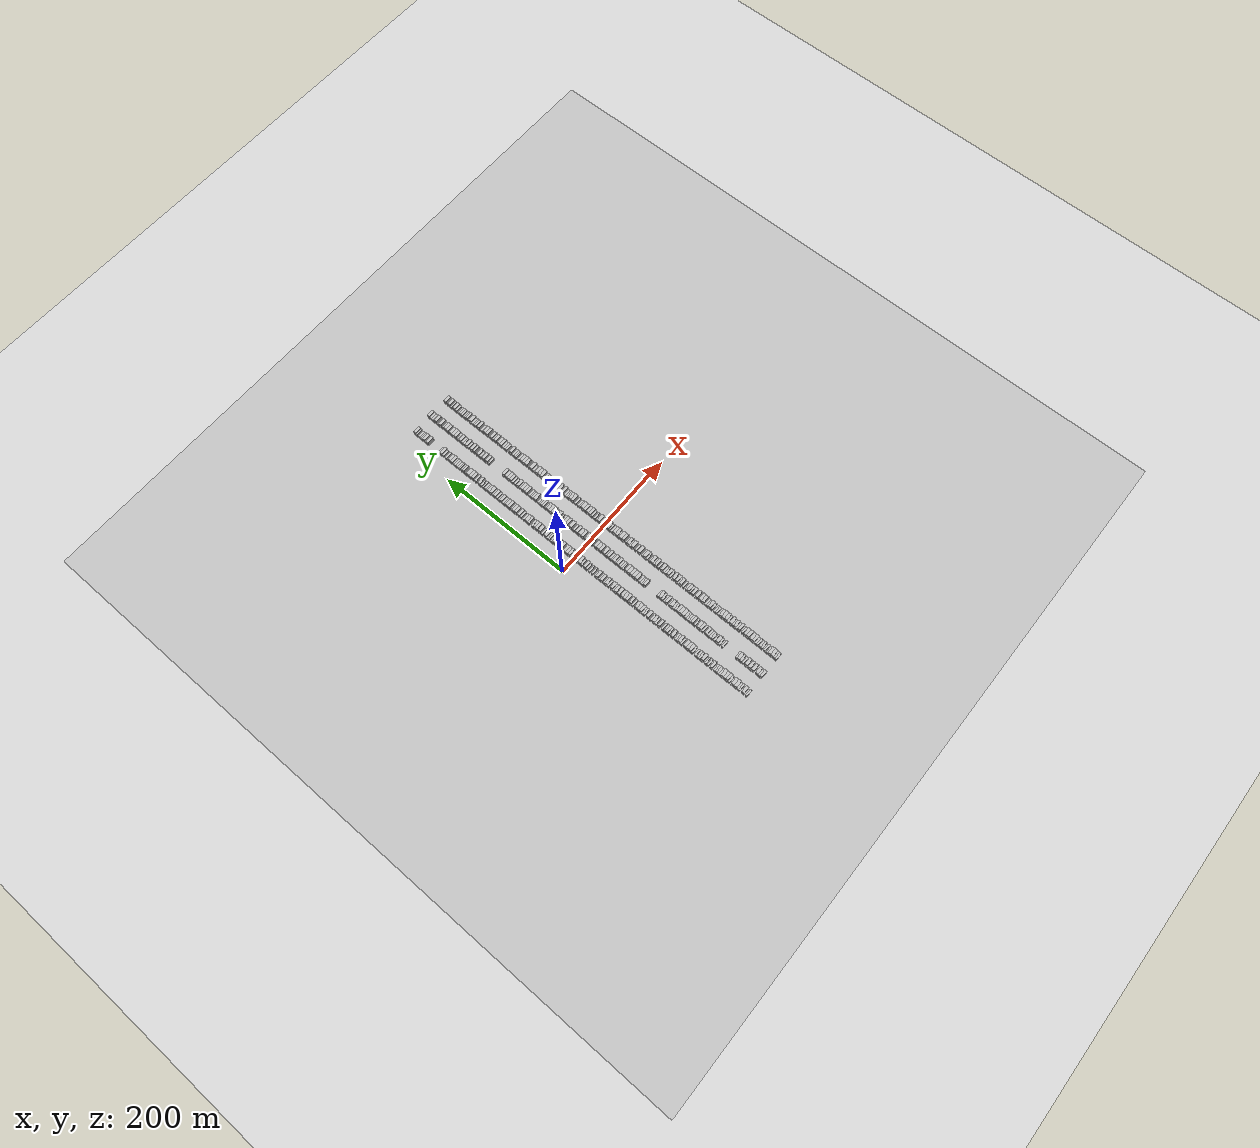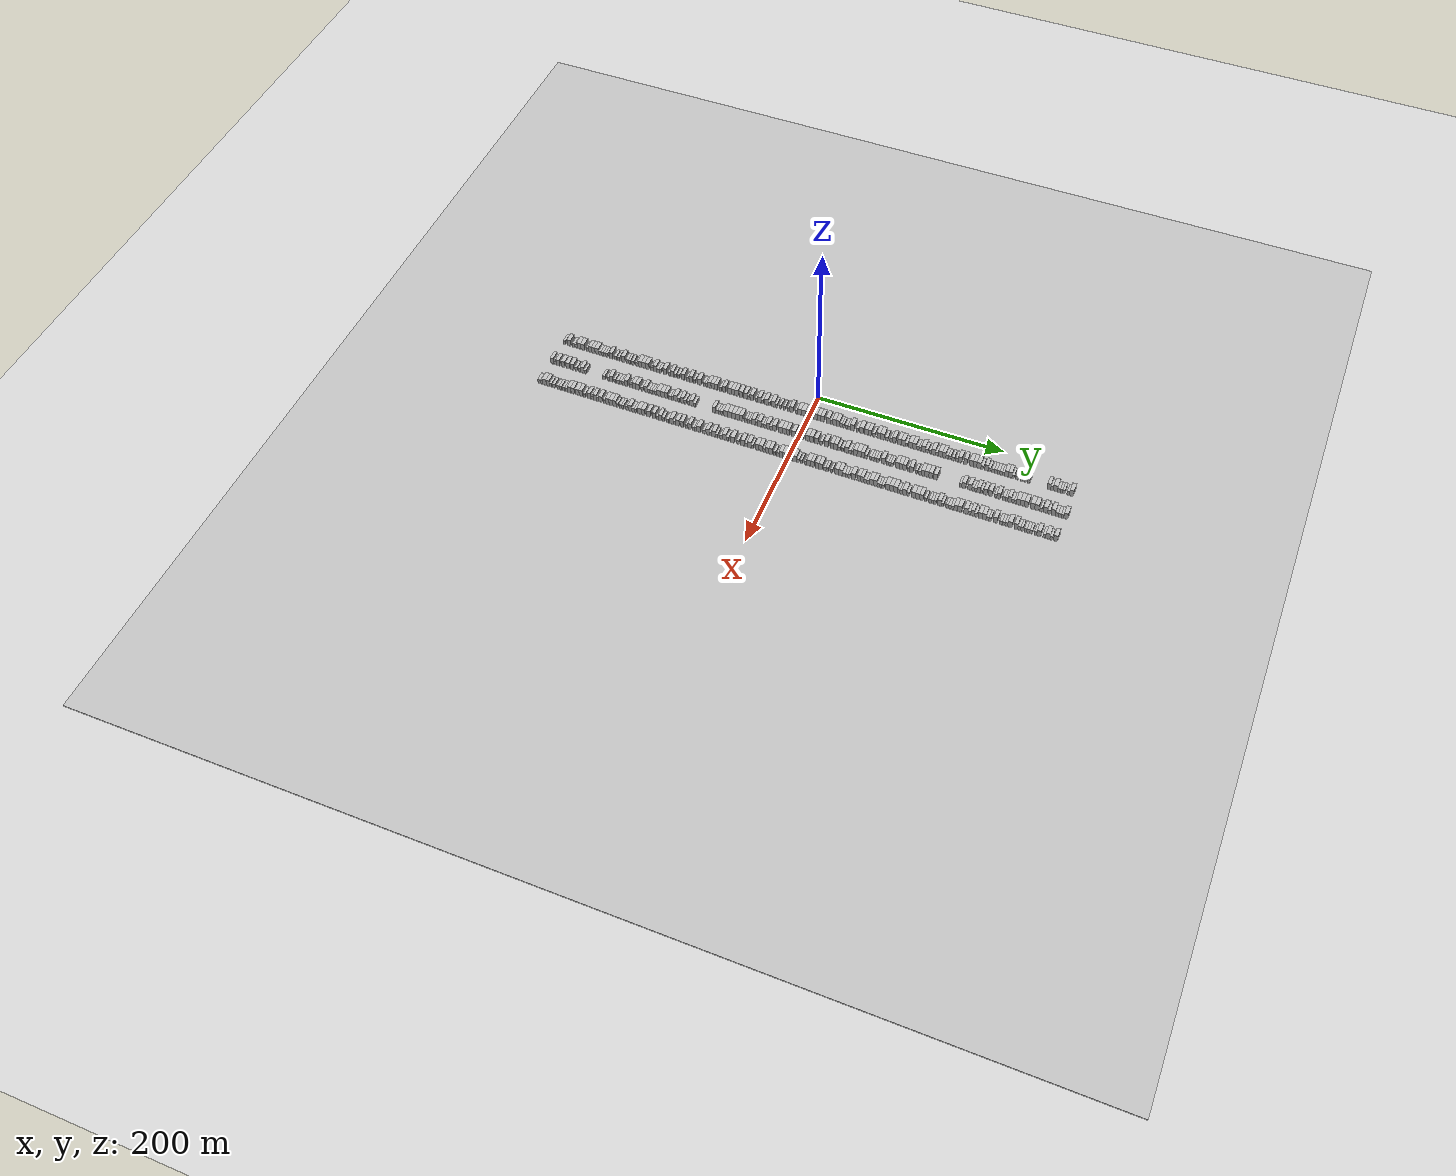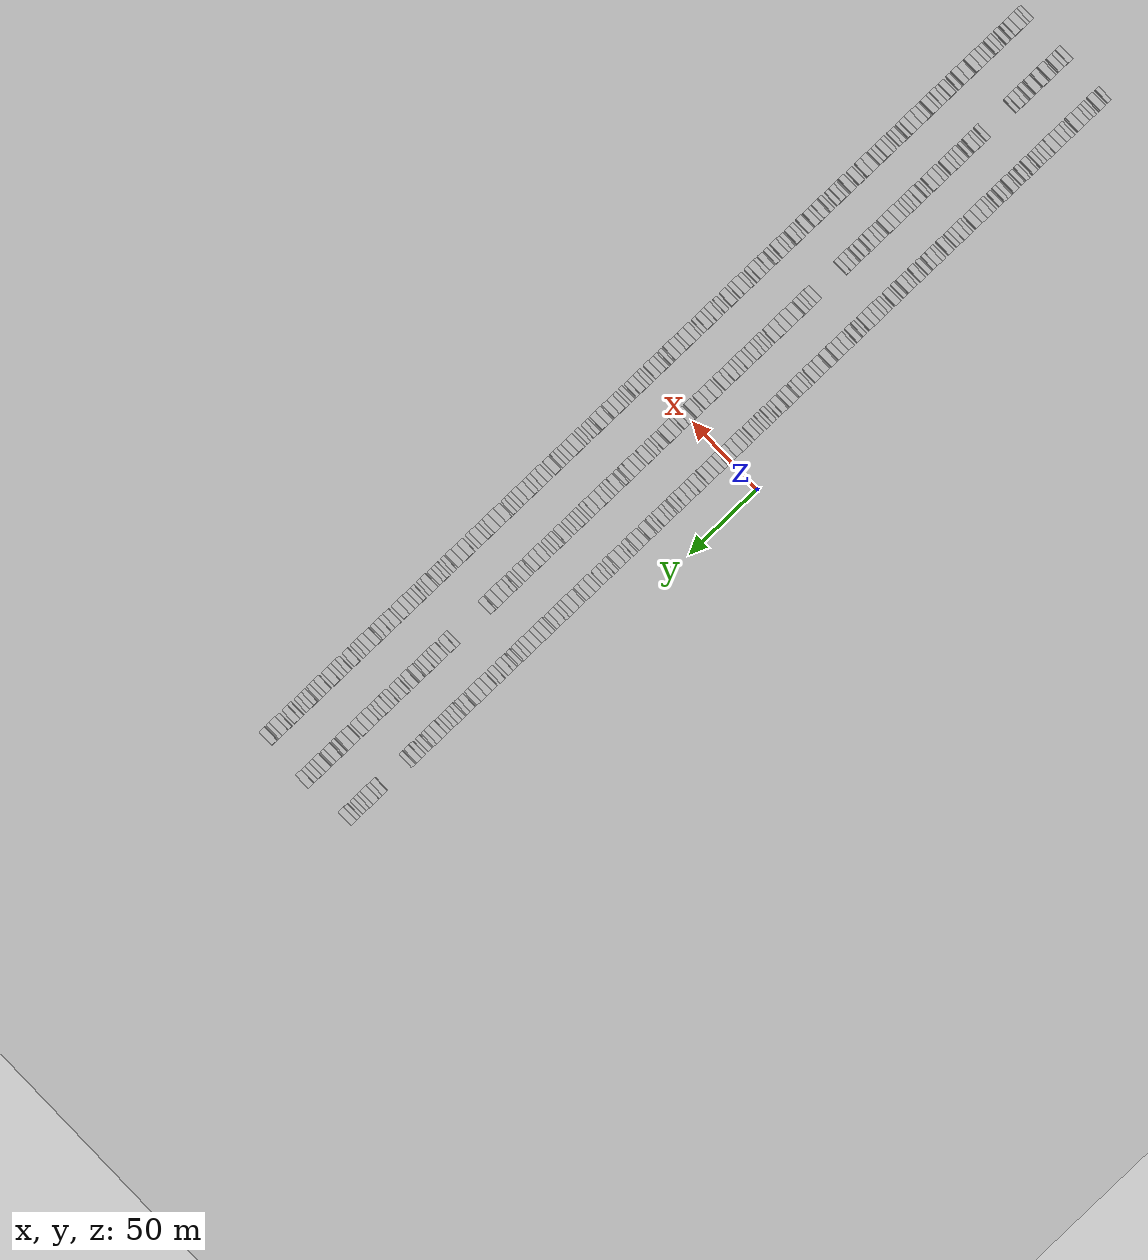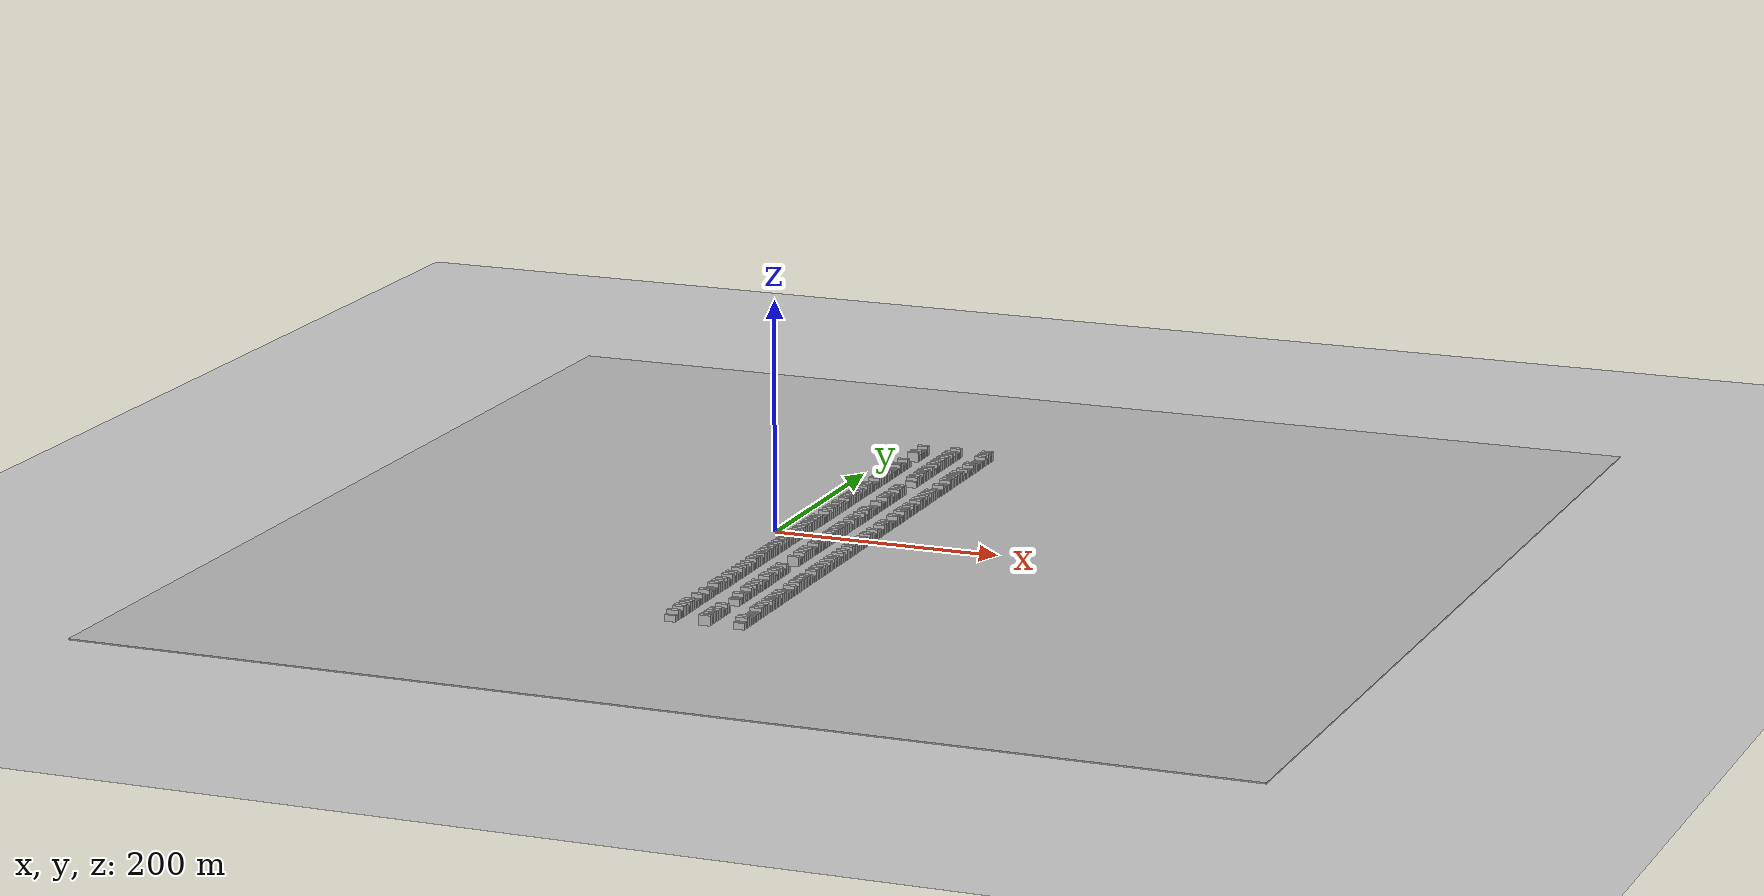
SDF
<?xml version="1.0" encoding="utf-8"?>

<sdf version="1.6">

   <world name="default">

      <gui fullscreen="0">

         <camera name="user_camera">

            <pose>-15 0 4.57585 0 0 0</pose>

            <view_controller>orbit</view_controller>

         </camera>

      </gui>

      <scene>

         <sky>

           <clouds>

             <speed>12</speed>

           </clouds>

         </sky>

         <ambient>0.4 0.4 0.4 1</ambient>

         <background>0.7 0.7 0.7 1</background>

         <shadows>1</shadows>

      </scene>

      <gravity>0 0 -9.8066</gravity>

      <magnetic_field>6e-06 2.3e-05 -4.2e-05</magnetic_field>

      <physics default="0" name="default_physics" type="ode">

         <ode>

            <solver>

               <type>quick</type>

               <iters>10</iters>

               <sor>1.0</sor>

               <use_dynamic_moi_rescaling>0</use_dynamic_moi_rescaling>

            </solver>

            <constraints>

               <cfm>0</cfm>

               <erp>0.2</erp>

               <contact_max_correcting_vel>100</contact_max_correcting_vel>

               <contact_surface_layer>0.001</contact_surface_layer>

            </constraints>

         </ode>

         <max_step_size>0.004</max_step_size>

         <real_time_factor>1</real_time_factor>

         <real_time_update_rate>250</real_time_update_rate>

      </physics>

      <light name="sun" type="directional">

         <cast_shadows>1</cast_shadows>

         <pose>0 0 10 0 0 0</pose>

         <diffuse>0.8 0.8 0.8 1</diffuse>

         <specular>0.2 0.2 0.2 1</specular>

         <attenuation>

            <range>1000</range>

            <constant>0.9</constant>

            <linear>0.01</linear>

            <quadratic>0.001</quadratic>

         </attenuation>

         <direction>-0.5 0.1 -0.9</direction>

      </light>

      <include>

         <name>ground_plane_1</name>

         <uri>model://HANNAS_ground_plane</uri>

         <pose>0 0 0  0 0 0</pose>

      </include>

      <include>

         <name>ground_plane_2</name>

         <uri>model://HANNAS_ground_plane</uri>

         <pose>100 0 0  0 0 0</pose>

      </include>

      <model name="building_1">

         <static>1</static>

         <pose frame="">25.0000 -278.6816 0 0.000000 0.000000 0.000000</pose>

         <link name="link">

            <pose frame="">0 0 3.00 0 0 0</pose>

            <collision name="collision">

               <geometry>

                  <box>

                     <size>10.0000 2.6369 6.0000</size>

                  </box>

               </geometry>

               <max_contacts>10</max_contacts>

               <surface>

                  <contact>

                     <ode/>

                  </contact>

                  <bounce/>

                  <friction>

                     <torsional>

                        <ode/>

                     </torsional>

                     <ode/>

                  </friction>

               </surface>

            </collision>

            <visual name="visual">

               <cast_shadows>0</cast_shadows>

               <geometry>

                  <box>

                     <size>10.0000 2.6369 6.0000</size>

                  </box>

               </geometry>

               <material>

                  <script>

                     <uri>model://HANNAS_wall/materials/scripts</uri>

                     <uri>model://HANNAS_wall/materials/textures</uri>

                     <name>vrc/HANNAS_wall</name>

                  </script>

               </material>

            </visual>

            <self_collide>0</self_collide>

            <enable_wind>0</enable_wind>

            <kinematic>0</kinematic>

         </link>

      </model>

      <model name="building_2">

         <static>1</static>

         <pose frame="">25.0000 -273.2493 0 0.000000 0.000000 0.000000</pose>

         <link name="link">

            <pose frame="">0 0 4.50 0 0 0</pose>

            <collision name="collision">

               <geometry>

                  <box>

                     <size>10.0000 4.2277 9.0000</size>

                  </box>

               </geometry>

               <max_contacts>10</max_contacts>

               <surface>

                  <contact>

                     <ode/>

                  </contact>

                  <bounce/>

                  <friction>

                     <torsional>

                        <ode/>

                     </torsional>

                     <ode/>

                  </friction>

               </surface>

            </collision>

            <visual name="visual">

               <cast_shadows>0</cast_shadows>

               <geometry>

                  <box>

                     <size>10.0000 4.2277 9.0000</size>

                  </box>

               </geometry>

               <material>

                  <script>

                     <uri>model://HANNAS_wall/materials/scripts</uri>

                     <uri>model://HANNAS_wall/materials/textures</uri>

                     <name>vrc/HANNAS_wall</name>

                  </script>

               </material>

            </visual>

            <self_collide>0</self_collide>

            <enable_wind>0</enable_wind>

            <kinematic>0</kinematic>

         </link>

      </model>

      <model name="building_3">

         <static>1</static>

         <pose frame="">25.0000 -267.8401 0 0.000000 0.000000 0.000000</pose>

         <link name="link">

            <pose frame="">0 0 3.00 0 0 0</pose>

            <collision name="collision">

               <geometry>

                  <box>

                     <size>10.0000 2.5906 6.0000</size>

                  </box>

               </geometry>

               <max_contacts>10</max_contacts>

               <surface>

                  <contact>

                     <ode/>

                  </contact>

                  <bounce/>

                  <friction>

                     <torsional>

                        <ode/>

                     </torsional>

                     <ode/>

                  </friction>

               </surface>

            </collision>

            <visual name="visual">

               <cast_shadows>0</cast_shadows>

               <geometry>

                  <box>

                     <size>10.0000 2.5906 6.0000</size>

                  </box>

               </geometry>

               <material>

                  <script>

                     <uri>model://HANNAS_wall/materials/scripts</uri>

                     <uri>model://HANNAS_wall/materials/textures</uri>

                     <name>vrc/HANNAS_wall</name>

                  </script>

               </material>

            </visual>

            <self_collide>0</self_collide>

            <enable_wind>0</enable_wind>

            <kinematic>0</kinematic>

         </link>

      </model>

      <model name="building_4">

         <static>1</static>

         <pose frame="">25.0000 -265.1921 0 0.000000 0.000000 0.000000</pose>

         <link name="link">

            <pose frame="">0 0 3.00 0 0 0</pose>

            <collision name="collision">

               <geometry>

                  <box>

                     <size>10.0000 2.7054 6.0000</size>

                  </box>

               </geometry>

               <max_contacts>10</max_contacts>

               <surface>

                  <contact>

                     <ode/>

                  </contact>

                  <bounce/>

                  <friction>

                     <torsional>

                        <ode/>

                     </torsional>

                     <ode/>

                  </friction>

               </surface>

            </collision>

            <visual name="visual">

               <cast_shadows>0</cast_shadows>

               <geometry>

                  <box>

                     <size>10.0000 2.7054 6.0000</size>

                  </box>

               </geometry>

               <material>

                  <script>

                     <uri>model://HANNAS_wall/materials/scripts</uri>

                     <uri>model://HANNAS_wall/materials/textures</uri>

                     <name>vrc/HANNAS_wall</name>

                  </script>

               </material>

            </visual>

            <self_collide>0</self_collide>

            <enable_wind>0</enable_wind>

            <kinematic>0</kinematic>

         </link>

      </model>

      <model name="building_5">

         <static>1</static>

         <pose frame="">25.0000 -261.6793 0 0.000000 0.000000 0.000000</pose>

         <link name="link">

            <pose frame="">0 0 4.50 0 0 0</pose>

            <collision name="collision">

               <geometry>

                  <box>

                     <size>10.0000 4.3202 9.0000</size>

                  </box>

               </geometry>

               <max_contacts>10</max_contacts>

               <surface>

                  <contact>

                     <ode/>

                  </contact>

                  <bounce/>

                  <friction>

                     <torsional>

                        <ode/>

                     </torsional>

                     <ode/>

                  </friction>

               </surface>

            </collision>

            <visual name="visual">

               <cast_shadows>0</cast_shadows>

               <geometry>

                  <box>

                     <size>10.0000 4.3202 9.0000</size>

                  </box>

               </geometry>

               <material>

                  <script>

                     <uri>model://HANNAS_wall/materials/scripts</uri>

                     <uri>model://HANNAS_wall/materials/textures</uri>

                     <name>vrc/HANNAS_wall</name>

                  </script>

               </material>

            </visual>

            <self_collide>0</self_collide>

            <enable_wind>0</enable_wind>

            <kinematic>0</kinematic>

         </link>

      </model>

      <model name="building_6">

         <static>1</static>

         <pose frame="">25.0000 -257.3326 0 0.000000 0.000000 0.000000</pose>

         <link name="link">

            <pose frame="">0 0 4.50 0 0 0</pose>

            <collision name="collision">

               <geometry>

                  <box>

                     <size>10.0000 4.3732 9.0000</size>

                  </box>

               </geometry>

               <max_contacts>10</max_contacts>

               <surface>

                  <contact>

                     <ode/>

                  </contact>

                  <bounce/>

                  <friction>

                     <torsional>

                        <ode/>

                     </torsional>

                     <ode/>

                  </friction>

               </surface>

            </collision>

            <visual name="visual">

               <cast_shadows>0</cast_shadows>

               <geometry>

                  <box>

                     <size>10.0000 4.3732 9.0000</size>

                  </box>

               </geometry>

               <material>

                  <script>

                     <uri>model://HANNAS_wall/materials/scripts</uri>

                     <uri>model://HANNAS_wall/materials/textures</uri>

                     <name>vrc/HANNAS_wall</name>

                  </script>

               </material>

            </visual>

            <self_collide>0</self_collide>

            <enable_wind>0</enable_wind>

            <kinematic>0</kinematic>

         </link>

      </model>

      <model name="building_7">

         <static>1</static>

         <pose frame="">25.0000 -251.7151 0 0.000000 0.000000 0.000000</pose>

         <link name="link">

            <pose frame="">0 0 3.00 0 0 0</pose>

            <collision name="collision">

               <geometry>

                  <box>

                     <size>10.0000 2.8618 6.0000</size>

                  </box>

               </geometry>

               <max_contacts>10</max_contacts>

               <surface>

                  <contact>

                     <ode/>

                  </contact>

                  <bounce/>

                  <friction>

                     <torsional>

                        <ode/>

                     </torsional>

                     <ode/>

                  </friction>

               </surface>

            </collision>

            <visual name="visual">

               <cast_shadows>0</cast_shadows>

               <geometry>

                  <box>

                     <size>10.0000 2.8618 6.0000</size>

                  </box>

               </geometry>

               <material>

                  <script>

                     <uri>model://HANNAS_wall/materials/scripts</uri>

                     <uri>model://HANNAS_wall/materials/textures</uri>

                     <name>vrc/HANNAS_wall</name>

                  </script>

               </material>

            </visual>

            <self_collide>0</self_collide>

            <enable_wind>0</enable_wind>

            <kinematic>0</kinematic>

         </link>

      </model>

      <model name="building_8">

         <static>1</static>

         <pose frame="">25.0000 -248.4774 0 0.000000 0.000000 0.000000</pose>

         <link name="link">

            <pose frame="">0 0 4.50 0 0 0</pose>

            <collision name="collision">

               <geometry>

                  <box>

                     <size>10.0000 3.6135 9.0000</size>

                  </box>

               </geometry>

               <max_contacts>10</max_contacts>

               <surface>

                  <contact>

                     <ode/>

                  </contact>

                  <bounce/>

                  <friction>

                     <torsional>

                        <ode/>

                     </torsional>

                     <ode/>

                  </friction>

               </surface>

            </collision>

            <visual name="visual">

               <cast_shadows>0</cast_shadows>

               <geometry>

                  <box>

                     <size>10.0000 3.6135 9.0000</size>

                  </box>

               </geometry>

               <material>

                  <script>

                     <uri>model://HANNAS_wall/materials/scripts</uri>

                     <uri>model://HANNAS_wall/materials/textures</uri>

                     <name>vrc/HANNAS_wall</name>

                  </script>

               </material>

            </visual>

            <self_collide>0</self_collide>

            <enable_wind>0</enable_wind>

            <kinematic>0</kinematic>

         </link>

      </model>

      <model name="building_9">

         <static>1</static>

         <pose frame="">25.0000 -244.8065 0 0.000000 0.000000 0.000000</pose>

         <link name="link">

            <pose frame="">0 0 4.50 0 0 0</pose>

            <collision name="collision">

               <geometry>

                  <box>

                     <size>10.0000 3.7282 9.0000</size>

                  </box>

               </geometry>

               <max_contacts>10</max_contacts>

               <surface>

                  <contact>

                     <ode/>

                  </contact>

                  <bounce/>

                  <friction>

                     <torsional>

                        <ode/>

                     </torsional>

                     <ode/>

                  </friction>

               </surface>

            </collision>

            <visual name="visual">

               <cast_shadows>0</cast_shadows>

               <geometry>

                  <box>

                     <size>10.0000 3.7282 9.0000</size>

                  </box>

               </geometry>

               <material>

                  <script>

                     <uri>model://HANNAS_wall/materials/scripts</uri>

                     <uri>model://HANNAS_wall/materials/textures</uri>

                     <name>vrc/HANNAS_wall</name>

                  </script>

               </material>

            </visual>

            <self_collide>0</self_collide>

            <enable_wind>0</enable_wind>

            <kinematic>0</kinematic>

         </link>

      </model>

      <model name="building_10">

         <static>1</static>

         <pose frame="">25.0000 -240.7461 0 0.000000 0.000000 0.000000</pose>

         <link name="link">

            <pose frame="">0 0 4.50 0 0 0</pose>

            <collision name="collision">

               <geometry>

                  <box>

                     <size>10.0000 4.3927 9.0000</size>

                  </box>

               </geometry>

               <max_contacts>10</max_contacts>

               <surface>

                  <contact>

                     <ode/>

                  </contact>

                  <bounce/>

                  <friction>

                     <torsional>

                        <ode/>

                     </torsional>

                     <ode/>

                  </friction>

               </surface>

            </collision>

            <visual name="visual">

               <cast_shadows>0</cast_shadows>

               <geometry>

                  <box>

                     <size>10.0000 4.3927 9.0000</size>

                  </box>

               </geometry>

               <material>

                  <script>

                     <uri>model://HANNAS_wall/materials/scripts</uri>

                     <uri>model://HANNAS_wall/materials/textures</uri>

                     <name>vrc/HANNAS_wall</name>

                  </script>

               </material>

            </visual>

            <self_collide>0</self_collide>

            <enable_wind>0</enable_wind>

            <kinematic>0</kinematic>

         </link>

      </model>

      <model name="building_11">

         <static>1</static>

         <pose frame="">25.0000 -237.1634 0 0.000000 0.000000 0.000000</pose>

         <link name="link">

            <pose frame="">0 0 3.00 0 0 0</pose>

            <collision name="collision">

               <geometry>

                  <box>

                     <size>10.0000 2.7726 6.0000</size>

                  </box>

               </geometry>

               <max_contacts>10</max_contacts>

               <surface>

                  <contact>

                     <ode/>

                  </contact>

                  <bounce/>

                  <friction>

                     <torsional>

                        <ode/>

                     </torsional>

                     <ode/>

                  </friction>

               </surface>

            </collision>

            <visual name="visual">

               <cast_shadows>0</cast_shadows>

               <geometry>

                  <box>

                     <size>10.0000 2.7726 6.0000</size>

                  </box>

               </geometry>

               <material>

                  <script>

                     <uri>model://HANNAS_wall/materials/scripts</uri>

                     <uri>model://HANNAS_wall/materials/textures</uri>

                     <name>vrc/HANNAS_wall</name>

                  </script>

               </material>

            </visual>

            <self_collide>0</self_collide>

            <enable_wind>0</enable_wind>

            <kinematic>0</kinematic>

         </link>

      </model>

      <model name="building_12">

         <static>1</static>

         <pose frame="">25.0000 -234.2931 0 0.000000 0.000000 0.000000</pose>

         <link name="link">

            <pose frame="">0 0 3.00 0 0 0</pose>

            <collision name="collision">

               <geometry>

                  <box>

                     <size>10.0000 2.9680 6.0000</size>

                  </box>

               </geometry>

               <max_contacts>10</max_contacts>

               <surface>

                  <contact>

                     <ode/>

                  </contact>

                  <bounce/>

                  <friction>

                     <torsional>

                        <ode/>

                     </torsional>

                     <ode/>

                  </friction>

               </surface>

            </collision>

            <visual name="visual">

               <cast_shadows>0</cast_shadows>

               <geometry>

                  <box>

                     <size>10.0000 2.9680 6.0000</size>

                  </box>

               </geometry>

               <material>

                  <script>

                     <uri>model://HANNAS_wall/materials/scripts</uri>

                     <uri>model://HANNAS_wall/materials/textures</uri>

                     <name>vrc/HANNAS_wall</name>

                  </script>

               </material>

            </visual>

            <self_collide>0</self_collide>

            <enable_wind>0</enable_wind>

            <kinematic>0</kinematic>

         </link>

      </model>

      <model name="building_13">

         <static>1</static>

         <pose frame="">25.0000 -231.5516 0 0.000000 0.000000 0.000000</pose>

         <link name="link">

            <pose frame="">0 0 3.00 0 0 0</pose>

            <collision name="collision">

               <geometry>

                  <box>

                     <size>10.0000 2.5151 6.0000</size>

                  </box>

               </geometry>

               <max_contacts>10</max_contacts>

               <surface>

                  <contact>

                     <ode/>

                  </contact>

                  <bounce/>

                  <friction>

                     <torsional>

                        <ode/>

                     </torsional>

                     <ode/>

                  </friction>

               </surface>

            </collision>

            <visual name="visual">

               <cast_shadows>0</cast_shadows>

               <geometry>

                  <box>

                     <size>10.0000 2.5151 6.0000</size>

                  </box>

               </geometry>

               <material>

                  <script>

                     <uri>model://HANNAS_wall/materials/scripts</uri>

                     <uri>model://HANNAS_wall/materials/textures</uri>

                     <name>vrc/HANNAS_wall</name>

                  </script>

               </material>

            </visual>

            <self_collide>0</self_collide>

            <enable_wind>0</enable_wind>

            <kinematic>0</kinematic>

         </link>

      </model>

      <model name="building_14">

         <static>1</static>

         <pose frame="">25.0000 -229.0391 0 0.000000 0.000000 0.000000</pose>

         <link name="link">

            <pose frame="">0 0 3.00 0 0 0</pose>

            <collision name="collision">

               <geometry>

                  <box>

                     <size>10.0000 2.5098 6.0000</size>

                  </box>

               </geometry>

               <max_contacts>10</max_contacts>

               <surface>

                  <contact>

                     <ode/>

                  </contact>

                  <bounce/>

                  <friction>

                     <torsional>

                        <ode/>

                     </torsional>

                     <ode/>

                  </friction>

               </surface>

            </collision>

            <visual name="visual">

               <cast_shadows>0</cast_shadows>

               <geometry>

                  <box>

                     <size>10.0000 2.5098 6.0000</size>

                  </box>

               </geometry>

               <material>

                  <script>

                     <uri>model://HANNAS_wall/materials/scripts</uri>

                     <uri>model://HANNAS_wall/materials/textures</uri>

                     <name>vrc/HANNAS_wall</name>

                  </script>

               </material>

            </visual>

            <self_collide>0</self_collide>

            <enable_wind>0</enable_wind>

            <kinematic>0</kinematic>

         </link>

      </model>

      <model name="building_15">

         <static>1</static>

         <pose frame="">25.0000 -223.9555 0 0.000000 0.000000 0.000000</pose>

         <link name="link">

            <pose frame="">0 0 4.50 0 0 0</pose>

            <collision name="collision">

               <geometry>

                  <box>

                     <size>10.0000 3.6572 9.0000</size>

                  </box>

               </geometry>

               <max_contacts>10</max_contacts>

               <surface>

                  <contact>

                     <ode/>

                  </contact>

                  <bounce/>

                  <friction>

                     <torsional>

                        <ode/>

                     </torsional>

                     <ode/>

                  </friction>

               </surface>

            </collision>

            <visual name="visual">

               <cast_shadows>0</cast_shadows>

               <geometry>

                  <box>

                     <size>10.0000 3.6572 9.0000</size>

                  </box>

               </geometry>

               <material>

                  <script>

                     <uri>model://HANNAS_wall/materials/scripts</uri>

                     <uri>model://HANNAS_wall/materials/textures</uri>

                     <name>vrc/HANNAS_wall</name>

                  </script>

               </material>

            </visual>

            <self_collide>0</self_collide>

            <enable_wind>0</enable_wind>

            <kinematic>0</kinematic>

         </link>

      </model>

      <model name="building_16">

         <static>1</static>

         <pose frame="">25.0000 -218.7445 0 0.000000 0.000000 0.000000</pose>

         <link name="link">

            <pose frame="">0 0 3.00 0 0 0</pose>

            <collision name="collision">

               <geometry>

                  <box>

                     <size>10.0000 2.7648 6.0000</size>

                  </box>

               </geometry>

               <max_contacts>10</max_contacts>

               <surface>

                  <contact>

                     <ode/>

                  </contact>

                  <bounce/>

                  <friction>

                     <torsional>

                        <ode/>

                     </torsional>

                     <ode/>

                  </friction>

               </surface>

            </collision>

            <visual name="visual">

               <cast_shadows>0</cast_shadows>

               <geometry>

                  <box>

                     <size>10.0000 2.7648 6.0000</size>

                  </box>

               </geometry>

               <material>

                  <script>

                     <uri>model://HANNAS_wall/materials/scripts</uri>

                     <uri>model://HANNAS_wall/materials/textures</uri>

                     <name>vrc/HANNAS_wall</name>

                  </script>

               </material>

            </visual>

            <self_collide>0</self_collide>

            <enable_wind>0</enable_wind>

            <kinematic>0</kinematic>

         </link>

      </model>

      <model name="building_17">

         <static>1</static>

         <pose frame="">25.0000 -215.1217 0 0.000000 0.000000 0.000000</pose>

         <link name="link">

            <pose frame="">0 0 3.00 0 0 0</pose>

            <collision name="collision">

               <geometry>

                  <box>

                     <size>10.0000 2.4809 6.0000</size>

                  </box>

               </geometry>

               <max_contacts>10</max_contacts>

               <surface>

                  <contact>

                     <ode/>

                  </contact>

                  <bounce/>

                  <friction>

                     <torsional>

                        <ode/>

                     </torsional>

                     <ode/>

                  </friction>

               </surface>

            </collision>

            <visual name="visual">

               <cast_shadows>0</cast_shadows>

               <geometry>

                  <box>

                     <size>10.0000 2.4809 6.0000</size>

                  </box>

               </geometry>

               <material>

                  <script>

                     <uri>model://HANNAS_wall/materials/scripts</uri>

                     <uri>model://HANNAS_wall/materials/textures</uri>

                     <name>vrc/HANNAS_wall</name>

                  </script>

               </material>

            </visual>

            <self_collide>0</self_collide>

            <enable_wind>0</enable_wind>

            <kinematic>0</kinematic>

         </link>

      </model>

      <model name="building_18">

         <static>1</static>

         <pose frame="">25.0000 -209.8505 0 0.000000 0.000000 0.000000</pose>

         <link name="link">

            <pose frame="">0 0 4.50 0 0 0</pose>

            <collision name="collision">

               <geometry>

                  <box>

                     <size>10.0000 4.0614 9.0000</size>

                  </box>

               </geometry>

               <max_contacts>10</max_contacts>

               <surface>

                  <contact>

                     <ode/>

                  </contact>

                  <bounce/>

                  <friction>

                     <torsional>

                        <ode/>

                     </torsional>

                     <ode/>

                  </friction>

               </surface>

            </collision>

            <visual name="visual">

               <cast_shadows>0</cast_shadows>

               <geometry>

                  <box>

                     <size>10.0000 4.0614 9.0000</size>

                  </box>

               </geometry>

               <material>

                  <script>

                     <uri>model://HANNAS_wall/materials/scripts</uri>

                     <uri>model://HANNAS_wall/materials/textures</uri>

                     <name>vrc/HANNAS_wall</name>

                  </script>

               </material>

            </visual>

            <self_collide>0</self_collide>

            <enable_wind>0</enable_wind>

            <kinematic>0</kinematic>

         </link>

      </model>

      <model name="building_19">

         <static>1</static>

         <pose frame="">25.0000 -205.3740 0 0.000000 0.000000 0.000000</pose>

         <link name="link">

            <pose frame="">0 0 3.00 0 0 0</pose>

            <collision name="collision">

               <geometry>

                  <box>

                     <size>10.0000 2.8917 6.0000</size>

                  </box>

               </geometry>

               <max_contacts>10</max_contacts>

               <surface>

                  <contact>

                     <ode/>

                  </contact>

                  <bounce/>

                  <friction>

                     <torsional>

                        <ode/>

                     </torsional>

                     <ode/>

                  </friction>

               </surface>

            </collision>

            <visual name="visual">

               <cast_shadows>0</cast_shadows>

               <geometry>

                  <box>

                     <size>10.0000 2.8917 6.0000</size>

                  </box>

               </geometry>

               <material>

                  <script>

                     <uri>model://HANNAS_wall/materials/scripts</uri>

                     <uri>model://HANNAS_wall/materials/textures</uri>

                     <name>vrc/HANNAS_wall</name>

                  </script>

               </material>

            </visual>

            <self_collide>0</self_collide>

            <enable_wind>0</enable_wind>

            <kinematic>0</kinematic>

         </link>

      </model>

      <model name="building_20">

         <static>1</static>

         <pose frame="">25.0000 -202.6111 0 0.000000 0.000000 0.000000</pose>

         <link name="link">

            <pose frame="">0 0 3.00 0 0 0</pose>

            <collision name="collision">

               <geometry>

                  <box>

                     <size>10.0000 2.6340 6.0000</size>

                  </box>

               </geometry>

               <max_contacts>10</max_contacts>

               <surface>

                  <contact>

                     <ode/>

                  </contact>

                  <bounce/>

                  <friction>

                     <torsional>

                        <ode/>

                     </torsional>

                     <ode/>

                  </friction>

               </surface>

            </collision>

            <visual name="visual">

               <cast_shadows>0</cast_shadows>

               <geometry>

                  <box>

                     <size>10.0000 2.6340 6.0000</size>

                  </box>

               </geometry>

               <material>

                  <script>

                     <uri>model://HANNAS_wall/materials/scripts</uri>

                     <uri>model://HANNAS_wall/materials/textures</uri>

                     <name>vrc/HANNAS_wall</name>

                  </script>

               </material>

            </visual>

            <self_collide>0</self_collide>

            <enable_wind>0</enable_wind>

            <kinematic>0</kinematic>

         </link>

      </model>

      <model name="building_21">

         <static>1</static>

         <pose frame="">25.0000 -198.8662 0 0.000000 0.000000 0.000000</pose>

         <link name="link">

            <pose frame="">0 0 3.00 0 0 0</pose>

            <collision name="collision">

               <geometry>

                  <box>

                     <size>10.0000 2.8558 6.0000</size>

                  </box>

               </geometry>

               <max_contacts>10</max_contacts>

               <surface>

                  <contact>

                     <ode/>

                  </contact>

                  <bounce/>

                  <friction>

                     <torsional>

                        <ode/>

                     </torsional>

                     <ode/>

                  </friction>

               </surface>

            </collision>

            <visual name="visual">

               <cast_shadows>0</cast_shadows>

               <geometry>

                  <box>

                     <size>10.0000 2.8558 6.0000</size>

                  </box>

               </geometry>

               <material>

                  <script>

                     <uri>model://HANNAS_wall/materials/scripts</uri>

                     <uri>model://HANNAS_wall/materials/textures</uri>

                     <name>vrc/HANNAS_wall</name>

                  </script>

               </material>

            </visual>

            <self_collide>0</self_collide>

            <enable_wind>0</enable_wind>

            <kinematic>0</kinematic>

         </link>

      </model>

      <model name="building_22">

         <static>1</static>

         <pose frame="">25.0000 -194.0693 0 0.000000 0.000000 0.000000</pose>

         <link name="link">

            <pose frame="">0 0 3.00 0 0 0</pose>

            <collision name="collision">

               <geometry>

                  <box>

                     <size>10.0000 2.7381 6.0000</size>

                  </box>

               </geometry>

               <max_contacts>10</max_contacts>

               <surface>

                  <contact>

                     <ode/>

                  </contact>

                  <bounce/>

                  <friction>

                     <torsional>

                        <ode/>

                     </torsional>

                     <ode/>

                  </friction>

               </surface>

            </collision>

            <visual name="visual">

               <cast_shadows>0</cast_shadows>

               <geometry>

                  <box>

                     <size>10.0000 2.7381 6.0000</size>

                  </box>

               </geometry>

               <material>

                  <script>

                     <uri>model://HANNAS_wall/materials/scripts</uri>

                     <uri>model://HANNAS_wall/materials/textures</uri>

                     <name>vrc/HANNAS_wall</name>

                  </script>

               </material>

            </visual>

            <self_collide>0</self_collide>

            <enable_wind>0</enable_wind>

            <kinematic>0</kinematic>

         </link>

      </model>

      <model name="building_23">

         <static>1</static>

         <pose frame="">25.0000 -190.6096 0 0.000000 0.000000 0.000000</pose>

         <link name="link">

            <pose frame="">0 0 4.50 0 0 0</pose>

            <collision name="collision">

               <geometry>

                  <box>

                     <size>10.0000 4.1812 9.0000</size>

                  </box>

               </geometry>

               <max_contacts>10</max_contacts>

               <surface>

                  <contact>

                     <ode/>

                  </contact>

                  <bounce/>

                  <friction>

                     <torsional>

                        <ode/>

                     </torsional>

                     <ode/>

                  </friction>

               </surface>

            </collision>

            <visual name="visual">

               <cast_shadows>0</cast_shadows>

               <geometry>

                  <box>

                     <size>10.0000 4.1812 9.0000</size>

                  </box>

               </geometry>

               <material>

                  <script>

                     <uri>model://HANNAS_wall/materials/scripts</uri>

                     <uri>model://HANNAS_wall/materials/textures</uri>

                     <name>vrc/HANNAS_wall</name>

                  </script>

               </material>

            </visual>

            <self_collide>0</self_collide>

            <enable_wind>0</enable_wind>

            <kinematic>0</kinematic>

         </link>

      </model>

      <model name="building_24">

         <static>1</static>

         <pose frame="">25.0000 -186.5205 0 0.000000 0.000000 0.000000</pose>

         <link name="link">

            <pose frame="">0 0 4.50 0 0 0</pose>

            <collision name="collision">

               <geometry>

                  <box>

                     <size>10.0000 3.9969 9.0000</size>

                  </box>

               </geometry>

               <max_contacts>10</max_contacts>

               <surface>

                  <contact>

                     <ode/>

                  </contact>

                  <bounce/>

                  <friction>

                     <torsional>

                        <ode/>

                     </torsional>

                     <ode/>

                  </friction>

               </surface>

            </collision>

            <visual name="visual">

               <cast_shadows>0</cast_shadows>

               <geometry>

                  <box>

                     <size>10.0000 3.9969 9.0000</size>

                  </box>

               </geometry>

               <material>

                  <script>

                     <uri>model://HANNAS_wall/materials/scripts</uri>

                     <uri>model://HANNAS_wall/materials/textures</uri>

                     <name>vrc/HANNAS_wall</name>

                  </script>

               </material>

            </visual>

            <self_collide>0</self_collide>

            <enable_wind>0</enable_wind>

            <kinematic>0</kinematic>

         </link>

      </model>

      <model name="building_25">

         <static>1</static>

         <pose frame="">25.0000 -182.3161 0 0.000000 0.000000 0.000000</pose>

         <link name="link">

            <pose frame="">0 0 4.50 0 0 0</pose>

            <collision name="collision">

               <geometry>

                  <box>

                     <size>10.0000 4.4120 9.0000</size>

                  </box>

               </geometry>

               <max_contacts>10</max_contacts>

               <surface>

                  <contact>

                     <ode/>

                  </contact>

                  <bounce/>

                  <friction>

                     <torsional>

                        <ode/>

                     </torsional>

                     <ode/>

                  </friction>

               </surface>

            </collision>

            <visual name="visual">

               <cast_shadows>0</cast_shadows>

               <geometry>

                  <box>

                     <size>10.0000 4.4120 9.0000</size>

                  </box>

               </geometry>

               <material>

                  <script>

                     <uri>model://HANNAS_wall/materials/scripts</uri>

                     <uri>model://HANNAS_wall/materials/textures</uri>

                     <name>vrc/HANNAS_wall</name>

                  </script>

               </material>

            </visual>

            <self_collide>0</self_collide>

            <enable_wind>0</enable_wind>

            <kinematic>0</kinematic>

         </link>

      </model>

      <model name="building_26">

         <static>1</static>

         <pose frame="">25.0000 -176.7188 0 0.000000 0.000000 0.000000</pose>

         <link name="link">

            <pose frame="">0 0 3.00 0 0 0</pose>

            <collision name="collision">

               <geometry>

                  <box>

                     <size>10.0000 2.7826 6.0000</size>

                  </box>

               </geometry>

               <max_contacts>10</max_contacts>

               <surface>

                  <contact>

                     <ode/>

                  </contact>

                  <bounce/>

                  <friction>

                     <torsional>

                        <ode/>

                     </torsional>

                     <ode/>

                  </friction>

               </surface>

            </collision>

            <visual name="visual">

               <cast_shadows>0</cast_shadows>

               <geometry>

                  <box>

                     <size>10.0000 2.7826 6.0000</size>

                  </box>

               </geometry>

               <material>

                  <script>

                     <uri>model://HANNAS_wall/materials/scripts</uri>

                     <uri>model://HANNAS_wall/materials/textures</uri>

                     <name>vrc/HANNAS_wall</name>

                  </script>

               </material>

            </visual>

            <self_collide>0</self_collide>

            <enable_wind>0</enable_wind>

            <kinematic>0</kinematic>

         </link>

      </model>

      <model name="building_27">

         <static>1</static>

         <pose frame="">25.0000 -173.3941 0 0.000000 0.000000 0.000000</pose>

         <link name="link">

            <pose frame="">0 0 4.50 0 0 0</pose>

            <collision name="collision">

               <geometry>

                  <box>

                     <size>10.0000 3.8668 9.0000</size>

                  </box>

               </geometry>

               <max_contacts>10</max_contacts>

               <surface>

                  <contact>

                     <ode/>

                  </contact>

                  <bounce/>

                  <friction>

                     <torsional>

                        <ode/>

                     </torsional>

                     <ode/>

                  </friction>

               </surface>

            </collision>

            <visual name="visual">

               <cast_shadows>0</cast_shadows>

               <geometry>

                  <box>

                     <size>10.0000 3.8668 9.0000</size>

                  </box>

               </geometry>

               <material>

                  <script>

                     <uri>model://HANNAS_wall/materials/scripts</uri>

                     <uri>model://HANNAS_wall/materials/textures</uri>

                     <name>vrc/HANNAS_wall</name>

                  </script>

               </material>

            </visual>

            <self_collide>0</self_collide>

            <enable_wind>0</enable_wind>

            <kinematic>0</kinematic>

         </link>

      </model>

      <model name="building_28">

         <static>1</static>

         <pose frame="">25.0000 -170.0270 0 0.000000 0.000000 0.000000</pose>

         <link name="link">

            <pose frame="">0 0 3.00 0 0 0</pose>

            <collision name="collision">

               <geometry>

                  <box>

                     <size>10.0000 2.8673 6.0000</size>

                  </box>

               </geometry>

               <max_contacts>10</max_contacts>

               <surface>

                  <contact>

                     <ode/>

                  </contact>

                  <bounce/>

                  <friction>

                     <torsional>

                        <ode/>

                     </torsional>

                     <ode/>

                  </friction>

               </surface>

            </collision>

            <visual name="visual">

               <cast_shadows>0</cast_shadows>

               <geometry>

                  <box>

                     <size>10.0000 2.8673 6.0000</size>

                  </box>

               </geometry>

               <material>

                  <script>

                     <uri>model://HANNAS_wall/materials/scripts</uri>

                     <uri>model://HANNAS_wall/materials/textures</uri>

                     <name>vrc/HANNAS_wall</name>

                  </script>

               </material>

            </visual>

            <self_collide>0</self_collide>

            <enable_wind>0</enable_wind>

            <kinematic>0</kinematic>

         </link>

      </model>

      <model name="building_29">

         <static>1</static>

         <pose frame="">25.0000 -167.2850 0 0.000000 0.000000 0.000000</pose>

         <link name="link">

            <pose frame="">0 0 3.00 0 0 0</pose>

            <collision name="collision">

               <geometry>

                  <box>

                     <size>10.0000 2.6166 6.0000</size>

                  </box>

               </geometry>

               <max_contacts>10</max_contacts>

               <surface>

                  <contact>

                     <ode/>

                  </contact>

                  <bounce/>

                  <friction>

                     <torsional>

                        <ode/>

                     </torsional>

                     <ode/>

                  </friction>

               </surface>

            </collision>

            <visual name="visual">

               <cast_shadows>0</cast_shadows>

               <geometry>

                  <box>

                     <size>10.0000 2.6166 6.0000</size>

                  </box>

               </geometry>

               <material>

                  <script>

                     <uri>model://HANNAS_wall/materials/scripts</uri>

                     <uri>model://HANNAS_wall/materials/textures</uri>

                     <name>vrc/HANNAS_wall</name>

                  </script>

               </material>

            </visual>

            <self_collide>0</self_collide>

            <enable_wind>0</enable_wind>

            <kinematic>0</kinematic>

         </link>

      </model>

      <model name="building_30">

         <static>1</static>

         <pose frame="">25.0000 -161.9713 0 0.000000 0.000000 0.000000</pose>

         <link name="link">

            <pose frame="">0 0 4.50 0 0 0</pose>

            <collision name="collision">

               <geometry>

                  <box>

                     <size>10.0000 4.0108 9.0000</size>

                  </box>

               </geometry>

               <max_contacts>10</max_contacts>

               <surface>

                  <contact>

                     <ode/>

                  </contact>

                  <bounce/>

                  <friction>

                     <torsional>

                        <ode/>

                     </torsional>

                     <ode/>

                  </friction>

               </surface>

            </collision>

            <visual name="visual">

               <cast_shadows>0</cast_shadows>

               <geometry>

                  <box>

                     <size>10.0000 4.0108 9.0000</size>

                  </box>

               </geometry>

               <material>

                  <script>

                     <uri>model://HANNAS_wall/materials/scripts</uri>

                     <uri>model://HANNAS_wall/materials/textures</uri>

                     <name>vrc/HANNAS_wall</name>

                  </script>

               </material>

            </visual>

            <self_collide>0</self_collide>

            <enable_wind>0</enable_wind>

            <kinematic>0</kinematic>

         </link>

      </model>

      <model name="building_31">

         <static>1</static>

         <pose frame="">25.0000 -156.6630 0 0.000000 0.000000 0.000000</pose>

         <link name="link">

            <pose frame="">0 0 3.00 0 0 0</pose>

            <collision name="collision">

               <geometry>

                  <box>

                     <size>10.0000 2.6059 6.0000</size>

                  </box>

               </geometry>

               <max_contacts>10</max_contacts>

               <surface>

                  <contact>

                     <ode/>

                  </contact>

                  <bounce/>

                  <friction>

                     <torsional>

                        <ode/>

                     </torsional>

                     <ode/>

                  </friction>

               </surface>

            </collision>

            <visual name="visual">

               <cast_shadows>0</cast_shadows>

               <geometry>

                  <box>

                     <size>10.0000 2.6059 6.0000</size>

                  </box>

               </geometry>

               <material>

                  <script>

                     <uri>model://HANNAS_wall/materials/scripts</uri>

                     <uri>model://HANNAS_wall/materials/textures</uri>

                     <name>vrc/HANNAS_wall</name>

                  </script>

               </material>

            </visual>

            <self_collide>0</self_collide>

            <enable_wind>0</enable_wind>

            <kinematic>0</kinematic>

         </link>

      </model>

      <model name="building_32">

         <static>1</static>

         <pose frame="">25.0000 -153.4546 0 0.000000 0.000000 0.000000</pose>

         <link name="link">

            <pose frame="">0 0 4.50 0 0 0</pose>

            <collision name="collision">

               <geometry>

                  <box>

                     <size>10.0000 3.8108 9.0000</size>

                  </box>

               </geometry>

               <max_contacts>10</max_contacts>

               <surface>

                  <contact>

                     <ode/>

                  </contact>

                  <bounce/>

                  <friction>

                     <torsional>

                        <ode/>

                     </torsional>

                     <ode/>

                  </friction>

               </surface>

            </collision>

            <visual name="visual">

               <cast_shadows>0</cast_shadows>

               <geometry>

                  <box>

                     <size>10.0000 3.8108 9.0000</size>

                  </box>

               </geometry>

               <material>

                  <script>

                     <uri>model://HANNAS_wall/materials/scripts</uri>

                     <uri>model://HANNAS_wall/materials/textures</uri>

                     <name>vrc/HANNAS_wall</name>

                  </script>

               </material>

            </visual>

            <self_collide>0</self_collide>

            <enable_wind>0</enable_wind>

            <kinematic>0</kinematic>

         </link>

      </model>

      <model name="building_33">

         <static>1</static>

         <pose frame="">25.0000 -150.1872 0 0.000000 0.000000 0.000000</pose>

         <link name="link">

            <pose frame="">0 0 3.00 0 0 0</pose>

            <collision name="collision">

               <geometry>

                  <box>

                     <size>10.0000 2.7240 6.0000</size>

                  </box>

               </geometry>

               <max_contacts>10</max_contacts>

               <surface>

                  <contact>

                     <ode/>

                  </contact>

                  <bounce/>

                  <friction>

                     <torsional>

                        <ode/>

                     </torsional>

                     <ode/>

                  </friction>

               </surface>

            </collision>

            <visual name="visual">

               <cast_shadows>0</cast_shadows>

               <geometry>

                  <box>

                     <size>10.0000 2.7240 6.0000</size>

                  </box>

               </geometry>

               <material>

                  <script>

                     <uri>model://HANNAS_wall/materials/scripts</uri>

                     <uri>model://HANNAS_wall/materials/textures</uri>

                     <name>vrc/HANNAS_wall</name>

                  </script>

               </material>

            </visual>

            <self_collide>0</self_collide>

            <enable_wind>0</enable_wind>

            <kinematic>0</kinematic>

         </link>

      </model>

      <model name="building_34">

         <static>1</static>

         <pose frame="">25.0000 -146.3787 0 0.000000 0.000000 0.000000</pose>

         <link name="link">

            <pose frame="">0 0 3.00 0 0 0</pose>

            <collision name="collision">

               <geometry>

                  <box>

                     <size>10.0000 2.8930 6.0000</size>

                  </box>

               </geometry>

               <max_contacts>10</max_contacts>

               <surface>

                  <contact>

                     <ode/>

                  </contact>

                  <bounce/>

                  <friction>

                     <torsional>

                        <ode/>

                     </torsional>

                     <ode/>

                  </friction>

               </surface>

            </collision>

            <visual name="visual">

               <cast_shadows>0</cast_shadows>

               <geometry>

                  <box>

                     <size>10.0000 2.8930 6.0000</size>

                  </box>

               </geometry>

               <material>

                  <script>

                     <uri>model://HANNAS_wall/materials/scripts</uri>

                     <uri>model://HANNAS_wall/materials/textures</uri>

                     <name>vrc/HANNAS_wall</name>

                  </script>

               </material>

            </visual>

            <self_collide>0</self_collide>

            <enable_wind>0</enable_wind>

            <kinematic>0</kinematic>

         </link>

      </model>

      <model name="building_35">

         <static>1</static>

         <pose frame="">25.0000 -141.0490 0 0.000000 0.000000 0.000000</pose>

         <link name="link">

            <pose frame="">0 0 4.50 0 0 0</pose>

            <collision name="collision">

               <geometry>

                  <box>

                     <size>10.0000 3.7663 9.0000</size>

                  </box>

               </geometry>

               <max_contacts>10</max_contacts>

               <surface>

                  <contact>

                     <ode/>

                  </contact>

                  <bounce/>

                  <friction>

                     <torsional>

                        <ode/>

                     </torsional>

                     <ode/>

                  </friction>

               </surface>

            </collision>

            <visual name="visual">

               <cast_shadows>0</cast_shadows>

               <geometry>

                  <box>

                     <size>10.0000 3.7663 9.0000</size>

                  </box>

               </geometry>

               <material>

                  <script>

                     <uri>model://HANNAS_wall/materials/scripts</uri>

                     <uri>model://HANNAS_wall/materials/textures</uri>

                     <name>vrc/HANNAS_wall</name>

                  </script>

               </material>

            </visual>

            <self_collide>0</self_collide>

            <enable_wind>0</enable_wind>

            <kinematic>0</kinematic>

         </link>

      </model>

      <model name="building_36">

         <static>1</static>

         <pose frame="">25.0000 -135.7231 0 0.000000 0.000000 0.000000</pose>

         <link name="link">

            <pose frame="">0 0 3.00 0 0 0</pose>

            <collision name="collision">

               <geometry>

                  <box>

                     <size>10.0000 2.8855 6.0000</size>

                  </box>

               </geometry>

               <max_contacts>10</max_contacts>

               <surface>

                  <contact>

                     <ode/>

                  </contact>

                  <bounce/>

                  <friction>

                     <torsional>

                        <ode/>

                     </torsional>

                     <ode/>

                  </friction>

               </surface>

            </collision>

            <visual name="visual">

               <cast_shadows>0</cast_shadows>

               <geometry>

                  <box>

                     <size>10.0000 2.8855 6.0000</size>

                  </box>

               </geometry>

               <material>

                  <script>

                     <uri>model://HANNAS_wall/materials/scripts</uri>

                     <uri>model://HANNAS_wall/materials/textures</uri>

                     <name>vrc/HANNAS_wall</name>

                  </script>

               </material>

            </visual>

            <self_collide>0</self_collide>

            <enable_wind>0</enable_wind>

            <kinematic>0</kinematic>

         </link>

      </model>

      <model name="building_37">

         <static>1</static>

         <pose frame="">25.0000 -132.3484 0 0.000000 0.000000 0.000000</pose>

         <link name="link">

            <pose frame="">0 0 4.50 0 0 0</pose>

            <collision name="collision">

               <geometry>

                  <box>

                     <size>10.0000 3.8639 9.0000</size>

                  </box>

               </geometry>

               <max_contacts>10</max_contacts>

               <surface>

                  <contact>

                     <ode/>

                  </contact>

                  <bounce/>

                  <friction>

                     <torsional>

                        <ode/>

                     </torsional>

                     <ode/>

                  </friction>

               </surface>

            </collision>

            <visual name="visual">

               <cast_shadows>0</cast_shadows>

               <geometry>

                  <box>

                     <size>10.0000 3.8639 9.0000</size>

                  </box>

               </geometry>

               <material>

                  <script>

                     <uri>model://HANNAS_wall/materials/scripts</uri>

                     <uri>model://HANNAS_wall/materials/textures</uri>

                     <name>vrc/HANNAS_wall</name>

                  </script>

               </material>

            </visual>

            <self_collide>0</self_collide>

            <enable_wind>0</enable_wind>

            <kinematic>0</kinematic>

         </link>

      </model>

      <model name="building_38">

         <static>1</static>

         <pose frame="">25.0000 -128.0818 0 0.000000 0.000000 0.000000</pose>

         <link name="link">

            <pose frame="">0 0 3.00 0 0 0</pose>

            <collision name="collision">

               <geometry>

                  <box>

                     <size>10.0000 2.6695 6.0000</size>

                  </box>

               </geometry>

               <max_contacts>10</max_contacts>

               <surface>

                  <contact>

                     <ode/>

                  </contact>

                  <bounce/>

                  <friction>

                     <torsional>

                        <ode/>

                     </torsional>

                     <ode/>

                  </friction>

               </surface>

            </collision>

            <visual name="visual">

               <cast_shadows>0</cast_shadows>

               <geometry>

                  <box>

                     <size>10.0000 2.6695 6.0000</size>

                  </box>

               </geometry>

               <material>

                  <script>

                     <uri>model://HANNAS_wall/materials/scripts</uri>

                     <uri>model://HANNAS_wall/materials/textures</uri>

                     <name>vrc/HANNAS_wall</name>

                  </script>

               </material>

            </visual>

            <self_collide>0</self_collide>

            <enable_wind>0</enable_wind>

            <kinematic>0</kinematic>

         </link>

      </model>

      <model name="building_39">

         <static>1</static>

         <pose frame="">25.0000 -122.6001 0 0.000000 0.000000 0.000000</pose>

         <link name="link">

            <pose frame="">0 0 4.50 0 0 0</pose>

            <collision name="collision">

               <geometry>

                  <box>

                     <size>10.0000 4.2939 9.0000</size>

                  </box>

               </geometry>

               <max_contacts>10</max_contacts>

               <surface>

                  <contact>

                     <ode/>

                  </contact>

                  <bounce/>

                  <friction>

                     <torsional>

                        <ode/>

                     </torsional>

                     <ode/>

                  </friction>

               </surface>

            </collision>

            <visual name="visual">

               <cast_shadows>0</cast_shadows>

               <geometry>

                  <box>

                     <size>10.0000 4.2939 9.0000</size>

                  </box>

               </geometry>

               <material>

                  <script>

                     <uri>model://HANNAS_wall/materials/scripts</uri>

                     <uri>model://HANNAS_wall/materials/textures</uri>

                     <name>vrc/HANNAS_wall</name>

                  </script>

               </material>

            </visual>

            <self_collide>0</self_collide>

            <enable_wind>0</enable_wind>

            <kinematic>0</kinematic>

         </link>

      </model>

      <model name="building_40">

         <static>1</static>

         <pose frame="">25.0000 -117.0866 0 0.000000 0.000000 0.000000</pose>

         <link name="link">

            <pose frame="">0 0 3.00 0 0 0</pose>

            <collision name="collision">

               <geometry>

                  <box>

                     <size>10.0000 2.7331 6.0000</size>

                  </box>

               </geometry>

               <max_contacts>10</max_contacts>

               <surface>

                  <contact>

                     <ode/>

                  </contact>

                  <bounce/>

                  <friction>

                     <torsional>

                        <ode/>

                     </torsional>

                     <ode/>

                  </friction>

               </surface>

            </collision>

            <visual name="visual">

               <cast_shadows>0</cast_shadows>

               <geometry>

                  <box>

                     <size>10.0000 2.7331 6.0000</size>

                  </box>

               </geometry>

               <material>

                  <script>

                     <uri>model://HANNAS_wall/materials/scripts</uri>

                     <uri>model://HANNAS_wall/materials/textures</uri>

                     <name>vrc/HANNAS_wall</name>

                  </script>

               </material>

            </visual>

            <self_collide>0</self_collide>

            <enable_wind>0</enable_wind>

            <kinematic>0</kinematic>

         </link>

      </model>

      <model name="building_41">

         <static>1</static>

         <pose frame="">25.0000 -114.3756 0 0.000000 0.000000 0.000000</pose>

         <link name="link">

            <pose frame="">0 0 3.00 0 0 0</pose>

            <collision name="collision">

               <geometry>

                  <box>

                     <size>10.0000 2.6889 6.0000</size>

                  </box>

               </geometry>

               <max_contacts>10</max_contacts>

               <surface>

                  <contact>

                     <ode/>

                  </contact>

                  <bounce/>

                  <friction>

                     <torsional>

                        <ode/>

                     </torsional>

                     <ode/>

                  </friction>

               </surface>

            </collision>

            <visual name="visual">

               <cast_shadows>0</cast_shadows>

               <geometry>

                  <box>

                     <size>10.0000 2.6889 6.0000</size>

                  </box>

               </geometry>

               <material>

                  <script>

                     <uri>model://HANNAS_wall/materials/scripts</uri>

                     <uri>model://HANNAS_wall/materials/textures</uri>

                     <name>vrc/HANNAS_wall</name>

                  </script>

               </material>

            </visual>

            <self_collide>0</self_collide>

            <enable_wind>0</enable_wind>

            <kinematic>0</kinematic>

         </link>

      </model>

      <model name="building_42">

         <static>1</static>

         <pose frame="">25.0000 -111.2043 0 0.000000 0.000000 0.000000</pose>

         <link name="link">

            <pose frame="">0 0 4.50 0 0 0</pose>

            <collision name="collision">

               <geometry>

                  <box>

                     <size>10.0000 3.6537 9.0000</size>

                  </box>

               </geometry>

               <max_contacts>10</max_contacts>

               <surface>

                  <contact>

                     <ode/>

                  </contact>

                  <bounce/>

                  <friction>

                     <torsional>

                        <ode/>

                     </torsional>

                     <ode/>

                  </friction>

               </surface>

            </collision>

            <visual name="visual">

               <cast_shadows>0</cast_shadows>

               <geometry>

                  <box>

                     <size>10.0000 3.6537 9.0000</size>

                  </box>

               </geometry>

               <material>

                  <script>

                     <uri>model://HANNAS_wall/materials/scripts</uri>

                     <uri>model://HANNAS_wall/materials/textures</uri>

                     <name>vrc/HANNAS_wall</name>

                  </script>

               </material>

            </visual>

            <self_collide>0</self_collide>

            <enable_wind>0</enable_wind>

            <kinematic>0</kinematic>

         </link>

      </model>

      <model name="building_43">

         <static>1</static>

         <pose frame="">25.0000 -107.4079 0 0.000000 0.000000 0.000000</pose>

         <link name="link">

            <pose frame="">0 0 4.50 0 0 0</pose>

            <collision name="collision">

               <geometry>

                  <box>

                     <size>10.0000 3.9390 9.0000</size>

                  </box>

               </geometry>

               <max_contacts>10</max_contacts>

               <surface>

                  <contact>

                     <ode/>

                  </contact>

                  <bounce/>

                  <friction>

                     <torsional>

                        <ode/>

                     </torsional>

                     <ode/>

                  </friction>

               </surface>

            </collision>

            <visual name="visual">

               <cast_shadows>0</cast_shadows>

               <geometry>

                  <box>

                     <size>10.0000 3.9390 9.0000</size>

                  </box>

               </geometry>

               <material>

                  <script>

                     <uri>model://HANNAS_wall/materials/scripts</uri>

                     <uri>model://HANNAS_wall/materials/textures</uri>

                     <name>vrc/HANNAS_wall</name>

                  </script>

               </material>

            </visual>

            <self_collide>0</self_collide>

            <enable_wind>0</enable_wind>

            <kinematic>0</kinematic>

         </link>

      </model>

      <model name="building_44">

         <static>1</static>

         <pose frame="">25.0000 -103.5517 0 0.000000 0.000000 0.000000</pose>

         <link name="link">

            <pose frame="">0 0 4.50 0 0 0</pose>

            <collision name="collision">

               <geometry>

                  <box>

                     <size>10.0000 3.7735 9.0000</size>

                  </box>

               </geometry>

               <max_contacts>10</max_contacts>

               <surface>

                  <contact>

                     <ode/>

                  </contact>

                  <bounce/>

                  <friction>

                     <torsional>

                        <ode/>

                     </torsional>

                     <ode/>

                  </friction>

               </surface>

            </collision>

            <visual name="visual">

               <cast_shadows>0</cast_shadows>

               <geometry>

                  <box>

                     <size>10.0000 3.7735 9.0000</size>

                  </box>

               </geometry>

               <material>

                  <script>

                     <uri>model://HANNAS_wall/materials/scripts</uri>

                     <uri>model://HANNAS_wall/materials/textures</uri>

                     <name>vrc/HANNAS_wall</name>

                  </script>

               </material>

            </visual>

            <self_collide>0</self_collide>

            <enable_wind>0</enable_wind>

            <kinematic>0</kinematic>

         </link>

      </model>

      <model name="building_45">

         <static>1</static>

         <pose frame="">25.0000 -98.4162 0 0.000000 0.000000 0.000000</pose>

         <link name="link">

            <pose frame="">0 0 3.00 0 0 0</pose>

            <collision name="collision">

               <geometry>

                  <box>

                     <size>10.0000 2.4974 6.0000</size>

                  </box>

               </geometry>

               <max_contacts>10</max_contacts>

               <surface>

                  <contact>

                     <ode/>

                  </contact>

                  <bounce/>

                  <friction>

                     <torsional>

                        <ode/>

                     </torsional>

                     <ode/>

                  </friction>

               </surface>

            </collision>

            <visual name="visual">

               <cast_shadows>0</cast_shadows>

               <geometry>

                  <box>

                     <size>10.0000 2.4974 6.0000</size>

                  </box>

               </geometry>

               <material>

                  <script>

                     <uri>model://HANNAS_wall/materials/scripts</uri>

                     <uri>model://HANNAS_wall/materials/textures</uri>

                     <name>vrc/HANNAS_wall</name>

                  </script>

               </material>

            </visual>

            <self_collide>0</self_collide>

            <enable_wind>0</enable_wind>

            <kinematic>0</kinematic>

         </link>

      </model>

      <model name="building_46">

         <static>1</static>

         <pose frame="">25.0000 -94.3609 0 0.000000 0.000000 0.000000</pose>

         <link name="link">

            <pose frame="">0 0 4.50 0 0 0</pose>

            <collision name="collision">

               <geometry>

                  <box>

                     <size>10.0000 3.6133 9.0000</size>

                  </box>

               </geometry>

               <max_contacts>10</max_contacts>

               <surface>

                  <contact>

                     <ode/>

                  </contact>

                  <bounce/>

                  <friction>

                     <torsional>

                        <ode/>

                     </torsional>

                     <ode/>

                  </friction>

               </surface>

            </collision>

            <visual name="visual">

               <cast_shadows>0</cast_shadows>

               <geometry>

                  <box>

                     <size>10.0000 3.6133 9.0000</size>

                  </box>

               </geometry>

               <material>

                  <script>

                     <uri>model://HANNAS_wall/materials/scripts</uri>

                     <uri>model://HANNAS_wall/materials/textures</uri>

                     <name>vrc/HANNAS_wall</name>

                  </script>

               </material>

            </visual>

            <self_collide>0</self_collide>

            <enable_wind>0</enable_wind>

            <kinematic>0</kinematic>

         </link>

      </model>

      <model name="building_47">

         <static>1</static>

         <pose frame="">25.0000 -88.4850 0 0.000000 0.000000 0.000000</pose>

         <link name="link">

            <pose frame="">0 0 4.50 0 0 0</pose>

            <collision name="collision">

               <geometry>

                  <box>

                     <size>10.0000 4.1384 9.0000</size>

                  </box>

               </geometry>

               <max_contacts>10</max_contacts>

               <surface>

                  <contact>

                     <ode/>

                  </contact>

                  <bounce/>

                  <friction>

                     <torsional>

                        <ode/>

                     </torsional>

                     <ode/>

                  </friction>

               </surface>

            </collision>

            <visual name="visual">

               <cast_shadows>0</cast_shadows>

               <geometry>

                  <box>

                     <size>10.0000 4.1384 9.0000</size>

                  </box>

               </geometry>

               <material>

                  <script>

                     <uri>model://HANNAS_wall/materials/scripts</uri>

                     <uri>model://HANNAS_wall/materials/textures</uri>

                     <name>vrc/HANNAS_wall</name>

                  </script>

               </material>

            </visual>

            <self_collide>0</self_collide>

            <enable_wind>0</enable_wind>

            <kinematic>0</kinematic>

         </link>

      </model>

      <model name="building_48">

         <static>1</static>

         <pose frame="">25.0000 -84.4528 0 0.000000 0.000000 0.000000</pose>

         <link name="link">

            <pose frame="">0 0 4.50 0 0 0</pose>

            <collision name="collision">

               <geometry>

                  <box>

                     <size>10.0000 3.9260 9.0000</size>

                  </box>

               </geometry>

               <max_contacts>10</max_contacts>

               <surface>

                  <contact>

                     <ode/>

                  </contact>

                  <bounce/>

                  <friction>

                     <torsional>

                        <ode/>

                     </torsional>

                     <ode/>

                  </friction>

               </surface>

            </collision>

            <visual name="visual">

               <cast_shadows>0</cast_shadows>

               <geometry>

                  <box>

                     <size>10.0000 3.9260 9.0000</size>

                  </box>

               </geometry>

               <material>

                  <script>

                     <uri>model://HANNAS_wall/materials/scripts</uri>

                     <uri>model://HANNAS_wall/materials/textures</uri>

                     <name>vrc/HANNAS_wall</name>

                  </script>

               </material>

            </visual>

            <self_collide>0</self_collide>

            <enable_wind>0</enable_wind>

            <kinematic>0</kinematic>

         </link>

      </model>

      <model name="building_49">

         <static>1</static>

         <pose frame="">25.0000 -80.6491 0 0.000000 0.000000 0.000000</pose>

         <link name="link">

            <pose frame="">0 0 4.50 0 0 0</pose>

            <collision name="collision">

               <geometry>

                  <box>

                     <size>10.0000 3.6814 9.0000</size>

                  </box>

               </geometry>

               <max_contacts>10</max_contacts>

               <surface>

                  <contact>

                     <ode/>

                  </contact>

                  <bounce/>

                  <friction>

                     <torsional>

                        <ode/>

                     </torsional>

                     <ode/>

                  </friction>

               </surface>

            </collision>

            <visual name="visual">

               <cast_shadows>0</cast_shadows>

               <geometry>

                  <box>

                     <size>10.0000 3.6814 9.0000</size>

                  </box>

               </geometry>

               <material>

                  <script>

                     <uri>model://HANNAS_wall/materials/scripts</uri>

                     <uri>model://HANNAS_wall/materials/textures</uri>

                     <name>vrc/HANNAS_wall</name>

                  </script>

               </material>

            </visual>

            <self_collide>0</self_collide>

            <enable_wind>0</enable_wind>

            <kinematic>0</kinematic>

         </link>

      </model>

      <model name="building_50">

         <static>1</static>

         <pose frame="">25.0000 -75.6490 0 0.000000 0.000000 0.000000</pose>

         <link name="link">

            <pose frame="">0 0 4.50 0 0 0</pose>

            <collision name="collision">

               <geometry>

                  <box>

                     <size>10.0000 4.3187 9.0000</size>

                  </box>

               </geometry>

               <max_contacts>10</max_contacts>

               <surface>

                  <contact>

                     <ode/>

                  </contact>

                  <bounce/>

                  <friction>

                     <torsional>

                        <ode/>

                     </torsional>

                     <ode/>

                  </friction>

               </surface>

            </collision>

            <visual name="visual">

               <cast_shadows>0</cast_shadows>

               <geometry>

                  <box>

                     <size>10.0000 4.3187 9.0000</size>

                  </box>

               </geometry>

               <material>

                  <script>

                     <uri>model://HANNAS_wall/materials/scripts</uri>

                     <uri>model://HANNAS_wall/materials/textures</uri>

                     <name>vrc/HANNAS_wall</name>

                  </script>

               </material>

            </visual>

            <self_collide>0</self_collide>

            <enable_wind>0</enable_wind>

            <kinematic>0</kinematic>

         </link>

      </model>

      <model name="building_51">

         <static>1</static>

         <pose frame="">25.0000 -70.3851 0 0.000000 0.000000 0.000000</pose>

         <link name="link">

            <pose frame="">0 0 4.50 0 0 0</pose>

            <collision name="collision">

               <geometry>

                  <box>

                     <size>10.0000 4.2092 9.0000</size>

                  </box>

               </geometry>

               <max_contacts>10</max_contacts>

               <surface>

                  <contact>

                     <ode/>

                  </contact>

                  <bounce/>

                  <friction>

                     <torsional>

                        <ode/>

                     </torsional>

                     <ode/>

                  </friction>

               </surface>

            </collision>

            <visual name="visual">

               <cast_shadows>0</cast_shadows>

               <geometry>

                  <box>

                     <size>10.0000 4.2092 9.0000</size>

                  </box>

               </geometry>

               <material>

                  <script>

                     <uri>model://HANNAS_wall/materials/scripts</uri>

                     <uri>model://HANNAS_wall/materials/textures</uri>

                     <name>vrc/HANNAS_wall</name>

                  </script>

               </material>

            </visual>

            <self_collide>0</self_collide>

            <enable_wind>0</enable_wind>

            <kinematic>0</kinematic>

         </link>

      </model>

      <model name="building_52">

         <static>1</static>

         <pose frame="">25.0000 -66.8908 0 0.000000 0.000000 0.000000</pose>

         <link name="link">

            <pose frame="">0 0 3.00 0 0 0</pose>

            <collision name="collision">

               <geometry>

                  <box>

                     <size>10.0000 2.7795 6.0000</size>

                  </box>

               </geometry>

               <max_contacts>10</max_contacts>

               <surface>

                  <contact>

                     <ode/>

                  </contact>

                  <bounce/>

                  <friction>

                     <torsional>

                        <ode/>

                     </torsional>

                     <ode/>

                  </friction>

               </surface>

            </collision>

            <visual name="visual">

               <cast_shadows>0</cast_shadows>

               <geometry>

                  <box>

                     <size>10.0000 2.7795 6.0000</size>

                  </box>

               </geometry>

               <material>

                  <script>

                     <uri>model://HANNAS_wall/materials/scripts</uri>

                     <uri>model://HANNAS_wall/materials/textures</uri>

                     <name>vrc/HANNAS_wall</name>

                  </script>

               </material>

            </visual>

            <self_collide>0</self_collide>

            <enable_wind>0</enable_wind>

            <kinematic>0</kinematic>

         </link>

      </model>

      <model name="building_53">

         <static>1</static>

         <pose frame="">25.0000 -63.5101 0 0.000000 0.000000 0.000000</pose>

         <link name="link">

            <pose frame="">0 0 4.50 0 0 0</pose>

            <collision name="collision">

               <geometry>

                  <box>

                     <size>10.0000 3.9818 9.0000</size>

                  </box>

               </geometry>

               <max_contacts>10</max_contacts>

               <surface>

                  <contact>

                     <ode/>

                  </contact>

                  <bounce/>

                  <friction>

                     <torsional>

                        <ode/>

                     </torsional>

                     <ode/>

                  </friction>

               </surface>

            </collision>

            <visual name="visual">

               <cast_shadows>0</cast_shadows>

               <geometry>

                  <box>

                     <size>10.0000 3.9818 9.0000</size>

                  </box>

               </geometry>

               <material>

                  <script>

                     <uri>model://HANNAS_wall/materials/scripts</uri>

                     <uri>model://HANNAS_wall/materials/textures</uri>

                     <name>vrc/HANNAS_wall</name>

                  </script>

               </material>

            </visual>

            <self_collide>0</self_collide>

            <enable_wind>0</enable_wind>

            <kinematic>0</kinematic>

         </link>

      </model>

      <model name="building_54">

         <static>1</static>

         <pose frame="">25.0000 -58.2209 0 0.000000 0.000000 0.000000</pose>

         <link name="link">

            <pose frame="">0 0 3.00 0 0 0</pose>

            <collision name="collision">

               <geometry>

                  <box>

                     <size>10.0000 2.5965 6.0000</size>

                  </box>

               </geometry>

               <max_contacts>10</max_contacts>

               <surface>

                  <contact>

                     <ode/>

                  </contact>

                  <bounce/>

                  <friction>

                     <torsional>

                        <ode/>

                     </torsional>

                     <ode/>

                  </friction>

               </surface>

            </collision>

            <visual name="visual">

               <cast_shadows>0</cast_shadows>

               <geometry>

                  <box>

                     <size>10.0000 2.5965 6.0000</size>

                  </box>

               </geometry>

               <material>

                  <script>

                     <uri>model://HANNAS_wall/materials/scripts</uri>

                     <uri>model://HANNAS_wall/materials/textures</uri>

                     <name>vrc/HANNAS_wall</name>

                  </script>

               </material>

            </visual>

            <self_collide>0</self_collide>

            <enable_wind>0</enable_wind>

            <kinematic>0</kinematic>

         </link>

      </model>

      <model name="building_55">

         <static>1</static>

         <pose frame="">25.0000 -54.8793 0 0.000000 0.000000 0.000000</pose>

         <link name="link">

            <pose frame="">0 0 4.50 0 0 0</pose>

            <collision name="collision">

               <geometry>

                  <box>

                     <size>10.0000 4.0868 9.0000</size>

                  </box>

               </geometry>

               <max_contacts>10</max_contacts>

               <surface>

                  <contact>

                     <ode/>

                  </contact>

                  <bounce/>

                  <friction>

                     <torsional>

                        <ode/>

                     </torsional>

                     <ode/>

                  </friction>

               </surface>

            </collision>

            <visual name="visual">

               <cast_shadows>0</cast_shadows>

               <geometry>

                  <box>

                     <size>10.0000 4.0868 9.0000</size>

                  </box>

               </geometry>

               <material>

                  <script>

                     <uri>model://HANNAS_wall/materials/scripts</uri>

                     <uri>model://HANNAS_wall/materials/textures</uri>

                     <name>vrc/HANNAS_wall</name>

                  </script>

               </material>

            </visual>

            <self_collide>0</self_collide>

            <enable_wind>0</enable_wind>

            <kinematic>0</kinematic>

         </link>

      </model>

      <model name="building_56">

         <static>1</static>

         <pose frame="">25.0000 -51.6076 0 0.000000 0.000000 0.000000</pose>

         <link name="link">

            <pose frame="">0 0 3.00 0 0 0</pose>

            <collision name="collision">

               <geometry>

                  <box>

                     <size>10.0000 2.4565 6.0000</size>

                  </box>

               </geometry>

               <max_contacts>10</max_contacts>

               <surface>

                  <contact>

                     <ode/>

                  </contact>

                  <bounce/>

                  <friction>

                     <torsional>

                        <ode/>

                     </torsional>

                     <ode/>

                  </friction>

               </surface>

            </collision>

            <visual name="visual">

               <cast_shadows>0</cast_shadows>

               <geometry>

                  <box>

                     <size>10.0000 2.4565 6.0000</size>

                  </box>

               </geometry>

               <material>

                  <script>

                     <uri>model://HANNAS_wall/materials/scripts</uri>

                     <uri>model://HANNAS_wall/materials/textures</uri>

                     <name>vrc/HANNAS_wall</name>

                  </script>

               </material>

            </visual>

            <self_collide>0</self_collide>

            <enable_wind>0</enable_wind>

            <kinematic>0</kinematic>

         </link>

      </model>

      <model name="building_57">

         <static>1</static>

         <pose frame="">25.0000 -47.3260 0 0.000000 0.000000 0.000000</pose>

         <link name="link">

            <pose frame="">0 0 4.50 0 0 0</pose>

            <collision name="collision">

               <geometry>

                  <box>

                     <size>10.0000 4.1068 9.0000</size>

                  </box>

               </geometry>

               <max_contacts>10</max_contacts>

               <surface>

                  <contact>

                     <ode/>

                  </contact>

                  <bounce/>

                  <friction>

                     <torsional>

                        <ode/>

                     </torsional>

                     <ode/>

                  </friction>

               </surface>

            </collision>

            <visual name="visual">

               <cast_shadows>0</cast_shadows>

               <geometry>

                  <box>

                     <size>10.0000 4.1068 9.0000</size>

                  </box>

               </geometry>

               <material>

                  <script>

                     <uri>model://HANNAS_wall/materials/scripts</uri>

                     <uri>model://HANNAS_wall/materials/textures</uri>

                     <name>vrc/HANNAS_wall</name>

                  </script>

               </material>

            </visual>

            <self_collide>0</self_collide>

            <enable_wind>0</enable_wind>

            <kinematic>0</kinematic>

         </link>

      </model>

      <model name="building_58">

         <static>1</static>

         <pose frame="">25.0000 -43.9816 0 0.000000 0.000000 0.000000</pose>

         <link name="link">

            <pose frame="">0 0 3.00 0 0 0</pose>

            <collision name="collision">

               <geometry>

                  <box>

                     <size>10.0000 2.5820 6.0000</size>

                  </box>

               </geometry>

               <max_contacts>10</max_contacts>

               <surface>

                  <contact>

                     <ode/>

                  </contact>

                  <bounce/>

                  <friction>

                     <torsional>

                        <ode/>

                     </torsional>

                     <ode/>

                  </friction>

               </surface>

            </collision>

            <visual name="visual">

               <cast_shadows>0</cast_shadows>

               <geometry>

                  <box>

                     <size>10.0000 2.5820 6.0000</size>

                  </box>

               </geometry>

               <material>

                  <script>

                     <uri>model://HANNAS_wall/materials/scripts</uri>

                     <uri>model://HANNAS_wall/materials/textures</uri>

                     <name>vrc/HANNAS_wall</name>

                  </script>

               </material>

            </visual>

            <self_collide>0</self_collide>

            <enable_wind>0</enable_wind>

            <kinematic>0</kinematic>

         </link>

      </model>

      <model name="building_59">

         <static>1</static>

         <pose frame="">25.0000 -39.6407 0 0.000000 0.000000 0.000000</pose>

         <link name="link">

            <pose frame="">0 0 4.50 0 0 0</pose>

            <collision name="collision">

               <geometry>

                  <box>

                     <size>10.0000 4.0999 9.0000</size>

                  </box>

               </geometry>

               <max_contacts>10</max_contacts>

               <surface>

                  <contact>

                     <ode/>

                  </contact>

                  <bounce/>

                  <friction>

                     <torsional>

                        <ode/>

                     </torsional>

                     <ode/>

                  </friction>

               </surface>

            </collision>

            <visual name="visual">

               <cast_shadows>0</cast_shadows>

               <geometry>

                  <box>

                     <size>10.0000 4.0999 9.0000</size>

                  </box>

               </geometry>

               <material>

                  <script>

                     <uri>model://HANNAS_wall/materials/scripts</uri>

                     <uri>model://HANNAS_wall/materials/textures</uri>

                     <name>vrc/HANNAS_wall</name>

                  </script>

               </material>

            </visual>

            <self_collide>0</self_collide>

            <enable_wind>0</enable_wind>

            <kinematic>0</kinematic>

         </link>

      </model>

      <model name="building_60">

         <static>1</static>

         <pose frame="">25.0000 -36.3896 0 0.000000 0.000000 0.000000</pose>

         <link name="link">

            <pose frame="">0 0 3.00 0 0 0</pose>

            <collision name="collision">

               <geometry>

                  <box>

                     <size>10.0000 2.4024 6.0000</size>

                  </box>

               </geometry>

               <max_contacts>10</max_contacts>

               <surface>

                  <contact>

                     <ode/>

                  </contact>

                  <bounce/>

                  <friction>

                     <torsional>

                        <ode/>

                     </torsional>

                     <ode/>

                  </friction>

               </surface>

            </collision>

            <visual name="visual">

               <cast_shadows>0</cast_shadows>

               <geometry>

                  <box>

                     <size>10.0000 2.4024 6.0000</size>

                  </box>

               </geometry>

               <material>

                  <script>

                     <uri>model://HANNAS_wall/materials/scripts</uri>

                     <uri>model://HANNAS_wall/materials/textures</uri>

                     <name>vrc/HANNAS_wall</name>

                  </script>

               </material>

            </visual>

            <self_collide>0</self_collide>

            <enable_wind>0</enable_wind>

            <kinematic>0</kinematic>

         </link>

      </model>

      <model name="building_61">

         <static>1</static>

         <pose frame="">25.0000 -31.8369 0 0.000000 0.000000 0.000000</pose>

         <link name="link">

            <pose frame="">0 0 3.00 0 0 0</pose>

            <collision name="collision">

               <geometry>

                  <box>

                     <size>10.0000 2.7029 6.0000</size>

                  </box>

               </geometry>

               <max_contacts>10</max_contacts>

               <surface>

                  <contact>

                     <ode/>

                  </contact>

                  <bounce/>

                  <friction>

                     <torsional>

                        <ode/>

                     </torsional>

                     <ode/>

                  </friction>

               </surface>

            </collision>

            <visual name="visual">

               <cast_shadows>0</cast_shadows>

               <geometry>

                  <box>

                     <size>10.0000 2.7029 6.0000</size>

                  </box>

               </geometry>

               <material>

                  <script>

                     <uri>model://HANNAS_wall/materials/scripts</uri>

                     <uri>model://HANNAS_wall/materials/textures</uri>

                     <name>vrc/HANNAS_wall</name>

                  </script>

               </material>

            </visual>

            <self_collide>0</self_collide>

            <enable_wind>0</enable_wind>

            <kinematic>0</kinematic>

         </link>

      </model>

      <model name="building_62">

         <static>1</static>

         <pose frame="">25.0000 -27.1818 0 0.000000 0.000000 0.000000</pose>

         <link name="link">

            <pose frame="">0 0 3.00 0 0 0</pose>

            <collision name="collision">

               <geometry>

                  <box>

                     <size>10.0000 2.6073 6.0000</size>

                  </box>

               </geometry>

               <max_contacts>10</max_contacts>

               <surface>

                  <contact>

                     <ode/>

                  </contact>

                  <bounce/>

                  <friction>

                     <torsional>

                        <ode/>

                     </torsional>

                     <ode/>

                  </friction>

               </surface>

            </collision>

            <visual name="visual">

               <cast_shadows>0</cast_shadows>

               <geometry>

                  <box>

                     <size>10.0000 2.6073 6.0000</size>

                  </box>

               </geometry>

               <material>

                  <script>

                     <uri>model://HANNAS_wall/materials/scripts</uri>

                     <uri>model://HANNAS_wall/materials/textures</uri>

                     <name>vrc/HANNAS_wall</name>

                  </script>

               </material>

            </visual>

            <self_collide>0</self_collide>

            <enable_wind>0</enable_wind>

            <kinematic>0</kinematic>

         </link>

      </model>

      <model name="building_63">

         <static>1</static>

         <pose frame="">25.0000 -22.5452 0 0.000000 0.000000 0.000000</pose>

         <link name="link">

            <pose frame="">0 0 3.00 0 0 0</pose>

            <collision name="collision">

               <geometry>

                  <box>

                     <size>10.0000 2.6658 6.0000</size>

                  </box>

               </geometry>

               <max_contacts>10</max_contacts>

               <surface>

                  <contact>

                     <ode/>

                  </contact>

                  <bounce/>

                  <friction>

                     <torsional>

                        <ode/>

                     </torsional>

                     <ode/>

                  </friction>

               </surface>

            </collision>

            <visual name="visual">

               <cast_shadows>0</cast_shadows>

               <geometry>

                  <box>

                     <size>10.0000 2.6658 6.0000</size>

                  </box>

               </geometry>

               <material>

                  <script>

                     <uri>model://HANNAS_wall/materials/scripts</uri>

                     <uri>model://HANNAS_wall/materials/textures</uri>

                     <name>vrc/HANNAS_wall</name>

                  </script>

               </material>

            </visual>

            <self_collide>0</self_collide>

            <enable_wind>0</enable_wind>

            <kinematic>0</kinematic>

         </link>

      </model>

      <model name="building_64">

         <static>1</static>

         <pose frame="">25.0000 -19.2137 0 0.000000 0.000000 0.000000</pose>

         <link name="link">

            <pose frame="">0 0 4.50 0 0 0</pose>

            <collision name="collision">

               <geometry>

                  <box>

                     <size>10.0000 3.9973 9.0000</size>

                  </box>

               </geometry>

               <max_contacts>10</max_contacts>

               <surface>

                  <contact>

                     <ode/>

                  </contact>

                  <bounce/>

                  <friction>

                     <torsional>

                        <ode/>

                     </torsional>

                     <ode/>

                  </friction>

               </surface>

            </collision>

            <visual name="visual">

               <cast_shadows>0</cast_shadows>

               <geometry>

                  <box>

                     <size>10.0000 3.9973 9.0000</size>

                  </box>

               </geometry>

               <material>

                  <script>

                     <uri>model://HANNAS_wall/materials/scripts</uri>

                     <uri>model://HANNAS_wall/materials/textures</uri>

                     <name>vrc/HANNAS_wall</name>

                  </script>

               </material>

            </visual>

            <self_collide>0</self_collide>

            <enable_wind>0</enable_wind>

            <kinematic>0</kinematic>

         </link>

      </model>

      <model name="building_65">

         <static>1</static>

         <pose frame="">25.0000 -13.7819 0 0.000000 0.000000 0.000000</pose>

         <link name="link">

            <pose frame="">0 0 3.00 0 0 0</pose>

            <collision name="collision">

               <geometry>

                  <box>

                     <size>10.0000 2.8661 6.0000</size>

                  </box>

               </geometry>

               <max_contacts>10</max_contacts>

               <surface>

                  <contact>

                     <ode/>

                  </contact>

                  <bounce/>

                  <friction>

                     <torsional>

                        <ode/>

                     </torsional>

                     <ode/>

                  </friction>

               </surface>

            </collision>

            <visual name="visual">

               <cast_shadows>0</cast_shadows>

               <geometry>

                  <box>

                     <size>10.0000 2.8661 6.0000</size>

                  </box>

               </geometry>

               <material>

                  <script>

                     <uri>model://HANNAS_wall/materials/scripts</uri>

                     <uri>model://HANNAS_wall/materials/textures</uri>

                     <name>vrc/HANNAS_wall</name>

                  </script>

               </material>

            </visual>

            <self_collide>0</self_collide>

            <enable_wind>0</enable_wind>

            <kinematic>0</kinematic>

         </link>

      </model>

      <model name="building_66">

         <static>1</static>

         <pose frame="">25.0000 -10.3824 0 0.000000 0.000000 0.000000</pose>

         <link name="link">

            <pose frame="">0 0 4.50 0 0 0</pose>

            <collision name="collision">

               <geometry>

                  <box>

                     <size>10.0000 3.9331 9.0000</size>

                  </box>

               </geometry>

               <max_contacts>10</max_contacts>

               <surface>

                  <contact>

                     <ode/>

                  </contact>

                  <bounce/>

                  <friction>

                     <torsional>

                        <ode/>

                     </torsional>

                     <ode/>

                  </friction>

               </surface>

            </collision>

            <visual name="visual">

               <cast_shadows>0</cast_shadows>

               <geometry>

                  <box>

                     <size>10.0000 3.9331 9.0000</size>

                  </box>

               </geometry>

               <material>

                  <script>

                     <uri>model://HANNAS_wall/materials/scripts</uri>

                     <uri>model://HANNAS_wall/materials/textures</uri>

                     <name>vrc/HANNAS_wall</name>

                  </script>

               </material>

            </visual>

            <self_collide>0</self_collide>

            <enable_wind>0</enable_wind>

            <kinematic>0</kinematic>

         </link>

      </model>

      <model name="building_67">

         <static>1</static>

         <pose frame="">25.0000 -6.1778 0 0.000000 0.000000 0.000000</pose>

         <link name="link">

            <pose frame="">0 0 4.50 0 0 0</pose>

            <collision name="collision">

               <geometry>

                  <box>

                     <size>10.0000 4.4761 9.0000</size>

                  </box>

               </geometry>

               <max_contacts>10</max_contacts>

               <surface>

                  <contact>

                     <ode/>

                  </contact>

                  <bounce/>

                  <friction>

                     <torsional>

                        <ode/>

                     </torsional>

                     <ode/>

                  </friction>

               </surface>

            </collision>

            <visual name="visual">

               <cast_shadows>0</cast_shadows>

               <geometry>

                  <box>

                     <size>10.0000 4.4761 9.0000</size>

                  </box>

               </geometry>

               <material>

                  <script>

                     <uri>model://HANNAS_wall/materials/scripts</uri>

                     <uri>model://HANNAS_wall/materials/textures</uri>

                     <name>vrc/HANNAS_wall</name>

                  </script>

               </material>

            </visual>

            <self_collide>0</self_collide>

            <enable_wind>0</enable_wind>

            <kinematic>0</kinematic>

         </link>

      </model>

      <model name="building_68">

         <static>1</static>

         <pose frame="">25.0000 -1.7875 0 0.000000 0.000000 0.000000</pose>

         <link name="link">

            <pose frame="">0 0 4.50 0 0 0</pose>

            <collision name="collision">

               <geometry>

                  <box>

                     <size>10.0000 4.3045 9.0000</size>

                  </box>

               </geometry>

               <max_contacts>10</max_contacts>

               <surface>

                  <contact>

                     <ode/>

                  </contact>

                  <bounce/>

                  <friction>

                     <torsional>

                        <ode/>

                     </torsional>

                     <ode/>

                  </friction>

               </surface>

            </collision>

            <visual name="visual">

               <cast_shadows>0</cast_shadows>

               <geometry>

                  <box>

                     <size>10.0000 4.3045 9.0000</size>

                  </box>

               </geometry>

               <material>

                  <script>

                     <uri>model://HANNAS_wall/materials/scripts</uri>

                     <uri>model://HANNAS_wall/materials/textures</uri>

                     <name>vrc/HANNAS_wall</name>

                  </script>

               </material>

            </visual>

            <self_collide>0</self_collide>

            <enable_wind>0</enable_wind>

            <kinematic>0</kinematic>

         </link>

      </model>

      <model name="building_69">

         <static>1</static>

         <pose frame="">25.0000 3.8394 0 0.000000 0.000000 0.000000</pose>

         <link name="link">

            <pose frame="">0 0 3.00 0 0 0</pose>

            <collision name="collision">

               <geometry>

                  <box>

                     <size>10.0000 2.9492 6.0000</size>

                  </box>

               </geometry>

               <max_contacts>10</max_contacts>

               <surface>

                  <contact>

                     <ode/>

                  </contact>

                  <bounce/>

                  <friction>

                     <torsional>

                        <ode/>

                     </torsional>

                     <ode/>

                  </friction>

               </surface>

            </collision>

            <visual name="visual">

               <cast_shadows>0</cast_shadows>

               <geometry>

                  <box>

                     <size>10.0000 2.9492 6.0000</size>

                  </box>

               </geometry>

               <material>

                  <script>

                     <uri>model://HANNAS_wall/materials/scripts</uri>

                     <uri>model://HANNAS_wall/materials/textures</uri>

                     <name>vrc/HANNAS_wall</name>

                  </script>

               </material>

            </visual>

            <self_collide>0</self_collide>

            <enable_wind>0</enable_wind>

            <kinematic>0</kinematic>

         </link>

      </model>

      <model name="building_70">

         <static>1</static>

         <pose frame="">25.0000 7.1778 0 0.000000 0.000000 0.000000</pose>

         <link name="link">

            <pose frame="">0 0 4.50 0 0 0</pose>

            <collision name="collision">

               <geometry>

                  <box>

                     <size>10.0000 3.7277 9.0000</size>

                  </box>

               </geometry>

               <max_contacts>10</max_contacts>

               <surface>

                  <contact>

                     <ode/>

                  </contact>

                  <bounce/>

                  <friction>

                     <torsional>

                        <ode/>

                     </torsional>

                     <ode/>

                  </friction>

               </surface>

            </collision>

            <visual name="visual">

               <cast_shadows>0</cast_shadows>

               <geometry>

                  <box>

                     <size>10.0000 3.7277 9.0000</size>

                  </box>

               </geometry>

               <material>

                  <script>

                     <uri>model://HANNAS_wall/materials/scripts</uri>

                     <uri>model://HANNAS_wall/materials/textures</uri>

                     <name>vrc/HANNAS_wall</name>

                  </script>

               </material>

            </visual>

            <self_collide>0</self_collide>

            <enable_wind>0</enable_wind>

            <kinematic>0</kinematic>

         </link>

      </model>

      <model name="building_71">

         <static>1</static>

         <pose frame="">25.0000 10.8776 0 0.000000 0.000000 0.000000</pose>

         <link name="link">

            <pose frame="">0 0 4.50 0 0 0</pose>

            <collision name="collision">

               <geometry>

                  <box>

                     <size>10.0000 3.6720 9.0000</size>

                  </box>

               </geometry>

               <max_contacts>10</max_contacts>

               <surface>

                  <contact>

                     <ode/>

                  </contact>

                  <bounce/>

                  <friction>

                     <torsional>

                        <ode/>

                     </torsional>

                     <ode/>

                  </friction>

               </surface>

            </collision>

            <visual name="visual">

               <cast_shadows>0</cast_shadows>

               <geometry>

                  <box>

                     <size>10.0000 3.6720 9.0000</size>

                  </box>

               </geometry>

               <material>

                  <script>

                     <uri>model://HANNAS_wall/materials/scripts</uri>

                     <uri>model://HANNAS_wall/materials/textures</uri>

                     <name>vrc/HANNAS_wall</name>

                  </script>

               </material>

            </visual>

            <self_collide>0</self_collide>

            <enable_wind>0</enable_wind>

            <kinematic>0</kinematic>

         </link>

      </model>

      <model name="building_72">

         <static>1</static>

         <pose frame="">25.0000 14.7044 0 0.000000 0.000000 0.000000</pose>

         <link name="link">

            <pose frame="">0 0 4.50 0 0 0</pose>

            <collision name="collision">

               <geometry>

                  <box>

                     <size>10.0000 3.9815 9.0000</size>

                  </box>

               </geometry>

               <max_contacts>10</max_contacts>

               <surface>

                  <contact>

                     <ode/>

                  </contact>

                  <bounce/>

                  <friction>

                     <torsional>

                        <ode/>

                     </torsional>

                     <ode/>

                  </friction>

               </surface>

            </collision>

            <visual name="visual">

               <cast_shadows>0</cast_shadows>

               <geometry>

                  <box>

                     <size>10.0000 3.9815 9.0000</size>

                  </box>

               </geometry>

               <material>

                  <script>

                     <uri>model://HANNAS_wall/materials/scripts</uri>

                     <uri>model://HANNAS_wall/materials/textures</uri>

                     <name>vrc/HANNAS_wall</name>

                  </script>

               </material>

            </visual>

            <self_collide>0</self_collide>

            <enable_wind>0</enable_wind>

            <kinematic>0</kinematic>

         </link>

      </model>

      <model name="building_73">

         <static>1</static>

         <pose frame="">25.0000 20.8589 0 0.000000 0.000000 0.000000</pose>

         <link name="link">

            <pose frame="">0 0 4.50 0 0 0</pose>

            <collision name="collision">

               <geometry>

                  <box>

                     <size>10.0000 4.3274 9.0000</size>

                  </box>

               </geometry>

               <max_contacts>10</max_contacts>

               <surface>

                  <contact>

                     <ode/>

                  </contact>

                  <bounce/>

                  <friction>

                     <torsional>

                        <ode/>

                     </torsional>

                     <ode/>

                  </friction>

               </surface>

            </collision>

            <visual name="visual">

               <cast_shadows>0</cast_shadows>

               <geometry>

                  <box>

                     <size>10.0000 4.3274 9.0000</size>

                  </box>

               </geometry>

               <material>

                  <script>

                     <uri>model://HANNAS_wall/materials/scripts</uri>

                     <uri>model://HANNAS_wall/materials/textures</uri>

                     <name>vrc/HANNAS_wall</name>

                  </script>

               </material>

            </visual>

            <self_collide>0</self_collide>

            <enable_wind>0</enable_wind>

            <kinematic>0</kinematic>

         </link>

      </model>

      <model name="building_74">

         <static>1</static>

         <pose frame="">25.0000 24.3996 0 0.000000 0.000000 0.000000</pose>

         <link name="link">

            <pose frame="">0 0 3.00 0 0 0</pose>

            <collision name="collision">

               <geometry>

                  <box>

                     <size>10.0000 2.7541 6.0000</size>

                  </box>

               </geometry>

               <max_contacts>10</max_contacts>

               <surface>

                  <contact>

                     <ode/>

                  </contact>

                  <bounce/>

                  <friction>

                     <torsional>

                        <ode/>

                     </torsional>

                     <ode/>

                  </friction>

               </surface>

            </collision>

            <visual name="visual">

               <cast_shadows>0</cast_shadows>

               <geometry>

                  <box>

                     <size>10.0000 2.7541 6.0000</size>

                  </box>

               </geometry>

               <material>

                  <script>

                     <uri>model://HANNAS_wall/materials/scripts</uri>

                     <uri>model://HANNAS_wall/materials/textures</uri>

                     <name>vrc/HANNAS_wall</name>

                  </script>

               </material>

            </visual>

            <self_collide>0</self_collide>

            <enable_wind>0</enable_wind>

            <kinematic>0</kinematic>

         </link>

      </model>

      <model name="building_75">

         <static>1</static>

         <pose frame="">25.0000 27.6662 0 0.000000 0.000000 0.000000</pose>

         <link name="link">

            <pose frame="">0 0 4.50 0 0 0</pose>

            <collision name="collision">

               <geometry>

                  <box>

                     <size>10.0000 3.7790 9.0000</size>

                  </box>

               </geometry>

               <max_contacts>10</max_contacts>

               <surface>

                  <contact>

                     <ode/>

                  </contact>

                  <bounce/>

                  <friction>

                     <torsional>

                        <ode/>

                     </torsional>

                     <ode/>

                  </friction>

               </surface>

            </collision>

            <visual name="visual">

               <cast_shadows>0</cast_shadows>

               <geometry>

                  <box>

                     <size>10.0000 3.7790 9.0000</size>

                  </box>

               </geometry>

               <material>

                  <script>

                     <uri>model://HANNAS_wall/materials/scripts</uri>

                     <uri>model://HANNAS_wall/materials/textures</uri>

                     <name>vrc/HANNAS_wall</name>

                  </script>

               </material>

            </visual>

            <self_collide>0</self_collide>

            <enable_wind>0</enable_wind>

            <kinematic>0</kinematic>

         </link>

      </model>

      <model name="building_76">

         <static>1</static>

         <pose frame="">25.0000 31.6096 0 0.000000 0.000000 0.000000</pose>

         <link name="link">

            <pose frame="">0 0 4.50 0 0 0</pose>

            <collision name="collision">

               <geometry>

                  <box>

                     <size>10.0000 4.1079 9.0000</size>

                  </box>

               </geometry>

               <max_contacts>10</max_contacts>

               <surface>

                  <contact>

                     <ode/>

                  </contact>

                  <bounce/>

                  <friction>

                     <torsional>

                        <ode/>

                     </torsional>

                     <ode/>

                  </friction>

               </surface>

            </collision>

            <visual name="visual">

               <cast_shadows>0</cast_shadows>

               <geometry>

                  <box>

                     <size>10.0000 4.1079 9.0000</size>

                  </box>

               </geometry>

               <material>

                  <script>

                     <uri>model://HANNAS_wall/materials/scripts</uri>

                     <uri>model://HANNAS_wall/materials/textures</uri>

                     <name>vrc/HANNAS_wall</name>

                  </script>

               </material>

            </visual>

            <self_collide>0</self_collide>

            <enable_wind>0</enable_wind>

            <kinematic>0</kinematic>

         </link>

      </model>

      <model name="building_77">

         <static>1</static>

         <pose frame="">25.0000 34.9238 0 0.000000 0.000000 0.000000</pose>

         <link name="link">

            <pose frame="">0 0 3.00 0 0 0</pose>

            <collision name="collision">

               <geometry>

                  <box>

                     <size>10.0000 2.5205 6.0000</size>

                  </box>

               </geometry>

               <max_contacts>10</max_contacts>

               <surface>

                  <contact>

                     <ode/>

                  </contact>

                  <bounce/>

                  <friction>

                     <torsional>

                        <ode/>

                     </torsional>

                     <ode/>

                  </friction>

               </surface>

            </collision>

            <visual name="visual">

               <cast_shadows>0</cast_shadows>

               <geometry>

                  <box>

                     <size>10.0000 2.5205 6.0000</size>

                  </box>

               </geometry>

               <material>

                  <script>

                     <uri>model://HANNAS_wall/materials/scripts</uri>

                     <uri>model://HANNAS_wall/materials/textures</uri>

                     <name>vrc/HANNAS_wall</name>

                  </script>

               </material>

            </visual>

            <self_collide>0</self_collide>

            <enable_wind>0</enable_wind>

            <kinematic>0</kinematic>

         </link>

      </model>

      <model name="building_78">

         <static>1</static>

         <pose frame="">25.0000 37.4037 0 0.000000 0.000000 0.000000</pose>

         <link name="link">

            <pose frame="">0 0 3.00 0 0 0</pose>

            <collision name="collision">

               <geometry>

                  <box>

                     <size>10.0000 2.4395 6.0000</size>

                  </box>

               </geometry>

               <max_contacts>10</max_contacts>

               <surface>

                  <contact>

                     <ode/>

                  </contact>

                  <bounce/>

                  <friction>

                     <torsional>

                        <ode/>

                     </torsional>

                     <ode/>

                  </friction>

               </surface>

            </collision>

            <visual name="visual">

               <cast_shadows>0</cast_shadows>

               <geometry>

                  <box>

                     <size>10.0000 2.4395 6.0000</size>

                  </box>

               </geometry>

               <material>

                  <script>

                     <uri>model://HANNAS_wall/materials/scripts</uri>

                     <uri>model://HANNAS_wall/materials/textures</uri>

                     <name>vrc/HANNAS_wall</name>

                  </script>

               </material>

            </visual>

            <self_collide>0</self_collide>

            <enable_wind>0</enable_wind>

            <kinematic>0</kinematic>

         </link>

      </model>

      <model name="building_79">

         <static>1</static>

         <pose frame="">25.0000 40.9928 0 0.000000 0.000000 0.000000</pose>

         <link name="link">

            <pose frame="">0 0 3.00 0 0 0</pose>

            <collision name="collision">

               <geometry>

                  <box>

                     <size>10.0000 2.7387 6.0000</size>

                  </box>

               </geometry>

               <max_contacts>10</max_contacts>

               <surface>

                  <contact>

                     <ode/>

                  </contact>

                  <bounce/>

                  <friction>

                     <torsional>

                        <ode/>

                     </torsional>

                     <ode/>

                  </friction>

               </surface>

            </collision>

            <visual name="visual">

               <cast_shadows>0</cast_shadows>

               <geometry>

                  <box>

                     <size>10.0000 2.7387 6.0000</size>

                  </box>

               </geometry>

               <material>

                  <script>

                     <uri>model://HANNAS_wall/materials/scripts</uri>

                     <uri>model://HANNAS_wall/materials/textures</uri>

                     <name>vrc/HANNAS_wall</name>

                  </script>

               </material>

            </visual>

            <self_collide>0</self_collide>

            <enable_wind>0</enable_wind>

            <kinematic>0</kinematic>

         </link>

      </model>

      <model name="building_80">

         <static>1</static>

         <pose frame="">25.0000 43.6758 0 0.000000 0.000000 0.000000</pose>

         <link name="link">

            <pose frame="">0 0 3.00 0 0 0</pose>

            <collision name="collision">

               <geometry>

                  <box>

                     <size>10.0000 2.6271 6.0000</size>

                  </box>

               </geometry>

               <max_contacts>10</max_contacts>

               <surface>

                  <contact>

                     <ode/>

                  </contact>

                  <bounce/>

                  <friction>

                     <torsional>

                        <ode/>

                     </torsional>

                     <ode/>

                  </friction>

               </surface>

            </collision>

            <visual name="visual">

               <cast_shadows>0</cast_shadows>

               <geometry>

                  <box>

                     <size>10.0000 2.6271 6.0000</size>

                  </box>

               </geometry>

               <material>

                  <script>

                     <uri>model://HANNAS_wall/materials/scripts</uri>

                     <uri>model://HANNAS_wall/materials/textures</uri>

                     <name>vrc/HANNAS_wall</name>

                  </script>

               </material>

            </visual>

            <self_collide>0</self_collide>

            <enable_wind>0</enable_wind>

            <kinematic>0</kinematic>

         </link>

      </model>

      <model name="building_81">

         <static>1</static>

         <pose frame="">25.0000 47.1945 0 0.000000 0.000000 0.000000</pose>

         <link name="link">

            <pose frame="">0 0 4.50 0 0 0</pose>

            <collision name="collision">

               <geometry>

                  <box>

                     <size>10.0000 4.4104 9.0000</size>

                  </box>

               </geometry>

               <max_contacts>10</max_contacts>

               <surface>

                  <contact>

                     <ode/>

                  </contact>

                  <bounce/>

                  <friction>

                     <torsional>

                        <ode/>

                     </torsional>

                     <ode/>

                  </friction>

               </surface>

            </collision>

            <visual name="visual">

               <cast_shadows>0</cast_shadows>

               <geometry>

                  <box>

                     <size>10.0000 4.4104 9.0000</size>

                  </box>

               </geometry>

               <material>

                  <script>

                     <uri>model://HANNAS_wall/materials/scripts</uri>

                     <uri>model://HANNAS_wall/materials/textures</uri>

                     <name>vrc/HANNAS_wall</name>

                  </script>

               </material>

            </visual>

            <self_collide>0</self_collide>

            <enable_wind>0</enable_wind>

            <kinematic>0</kinematic>

         </link>

      </model>

      <model name="building_82">

         <static>1</static>

         <pose frame="">25.0000 52.7461 0 0.000000 0.000000 0.000000</pose>

         <link name="link">

            <pose frame="">0 0 3.00 0 0 0</pose>

            <collision name="collision">

               <geometry>

                  <box>

                     <size>10.0000 2.6929 6.0000</size>

                  </box>

               </geometry>

               <max_contacts>10</max_contacts>

               <surface>

                  <contact>

                     <ode/>

                  </contact>

                  <bounce/>

                  <friction>

                     <torsional>

                        <ode/>

                     </torsional>

                     <ode/>

                  </friction>

               </surface>

            </collision>

            <visual name="visual">

               <cast_shadows>0</cast_shadows>

               <geometry>

                  <box>

                     <size>10.0000 2.6929 6.0000</size>

                  </box>

               </geometry>

               <material>

                  <script>

                     <uri>model://HANNAS_wall/materials/scripts</uri>

                     <uri>model://HANNAS_wall/materials/textures</uri>

                     <name>vrc/HANNAS_wall</name>

                  </script>

               </material>

            </visual>

            <self_collide>0</self_collide>

            <enable_wind>0</enable_wind>

            <kinematic>0</kinematic>

         </link>

      </model>

      <model name="building_83">

         <static>1</static>

         <pose frame="">25.0000 57.3291 0 0.000000 0.000000 0.000000</pose>

         <link name="link">

            <pose frame="">0 0 4.50 0 0 0</pose>

            <collision name="collision">

               <geometry>

                  <box>

                     <size>10.0000 4.4733 9.0000</size>

                  </box>

               </geometry>

               <max_contacts>10</max_contacts>

               <surface>

                  <contact>

                     <ode/>

                  </contact>

                  <bounce/>

                  <friction>

                     <torsional>

                        <ode/>

                     </torsional>

                     <ode/>

                  </friction>

               </surface>

            </collision>

            <visual name="visual">

               <cast_shadows>0</cast_shadows>

               <geometry>

                  <box>

                     <size>10.0000 4.4733 9.0000</size>

                  </box>

               </geometry>

               <material>

                  <script>

                     <uri>model://HANNAS_wall/materials/scripts</uri>

                     <uri>model://HANNAS_wall/materials/textures</uri>

                     <name>vrc/HANNAS_wall</name>

                  </script>

               </material>

            </visual>

            <self_collide>0</self_collide>

            <enable_wind>0</enable_wind>

            <kinematic>0</kinematic>

         </link>

      </model>

      <model name="building_84">

         <static>1</static>

         <pose frame="">25.0000 62.5295 0 0.000000 0.000000 0.000000</pose>

         <link name="link">

            <pose frame="">0 0 4.50 0 0 0</pose>

            <collision name="collision">

               <geometry>

                  <box>

                     <size>10.0000 3.9275 9.0000</size>

                  </box>

               </geometry>

               <max_contacts>10</max_contacts>

               <surface>

                  <contact>

                     <ode/>

                  </contact>

                  <bounce/>

                  <friction>

                     <torsional>

                        <ode/>

                     </torsional>

                     <ode/>

                  </friction>

               </surface>

            </collision>

            <visual name="visual">

               <cast_shadows>0</cast_shadows>

               <geometry>

                  <box>

                     <size>10.0000 3.9275 9.0000</size>

                  </box>

               </geometry>

               <material>

                  <script>

                     <uri>model://HANNAS_wall/materials/scripts</uri>

                     <uri>model://HANNAS_wall/materials/textures</uri>

                     <name>vrc/HANNAS_wall</name>

                  </script>

               </material>

            </visual>

            <self_collide>0</self_collide>

            <enable_wind>0</enable_wind>

            <kinematic>0</kinematic>

         </link>

      </model>

      <model name="building_85">

         <static>1</static>

         <pose frame="">25.0000 66.3014 0 0.000000 0.000000 0.000000</pose>

         <link name="link">

            <pose frame="">0 0 4.50 0 0 0</pose>

            <collision name="collision">

               <geometry>

                  <box>

                     <size>10.0000 3.6162 9.0000</size>

                  </box>

               </geometry>

               <max_contacts>10</max_contacts>

               <surface>

                  <contact>

                     <ode/>

                  </contact>

                  <bounce/>

                  <friction>

                     <torsional>

                        <ode/>

                     </torsional>

                     <ode/>

                  </friction>

               </surface>

            </collision>

            <visual name="visual">

               <cast_shadows>0</cast_shadows>

               <geometry>

                  <box>

                     <size>10.0000 3.6162 9.0000</size>

                  </box>

               </geometry>

               <material>

                  <script>

                     <uri>model://HANNAS_wall/materials/scripts</uri>

                     <uri>model://HANNAS_wall/materials/textures</uri>

                     <name>vrc/HANNAS_wall</name>

                  </script>

               </material>

            </visual>

            <self_collide>0</self_collide>

            <enable_wind>0</enable_wind>

            <kinematic>0</kinematic>

         </link>

      </model>

      <model name="building_86">

         <static>1</static>

         <pose frame="">25.0000 70.5685 0 0.000000 0.000000 0.000000</pose>

         <link name="link">

            <pose frame="">0 0 3.00 0 0 0</pose>

            <collision name="collision">

               <geometry>

                  <box>

                     <size>10.0000 2.9182 6.0000</size>

                  </box>

               </geometry>

               <max_contacts>10</max_contacts>

               <surface>

                  <contact>

                     <ode/>

                  </contact>

                  <bounce/>

                  <friction>

                     <torsional>

                        <ode/>

                     </torsional>

                     <ode/>

                  </friction>

               </surface>

            </collision>

            <visual name="visual">

               <cast_shadows>0</cast_shadows>

               <geometry>

                  <box>

                     <size>10.0000 2.9182 6.0000</size>

                  </box>

               </geometry>

               <material>

                  <script>

                     <uri>model://HANNAS_wall/materials/scripts</uri>

                     <uri>model://HANNAS_wall/materials/textures</uri>

                     <name>vrc/HANNAS_wall</name>

                  </script>

               </material>

            </visual>

            <self_collide>0</self_collide>

            <enable_wind>0</enable_wind>

            <kinematic>0</kinematic>

         </link>

      </model>

      <model name="building_87">

         <static>1</static>

         <pose frame="">25.0000 75.8554 0 0.000000 0.000000 0.000000</pose>

         <link name="link">

            <pose frame="">0 0 4.50 0 0 0</pose>

            <collision name="collision">

               <geometry>

                  <box>

                     <size>10.0000 3.6556 9.0000</size>

                  </box>

               </geometry>

               <max_contacts>10</max_contacts>

               <surface>

                  <contact>

                     <ode/>

                  </contact>

                  <bounce/>

                  <friction>

                     <torsional>

                        <ode/>

                     </torsional>

                     <ode/>

                  </friction>

               </surface>

            </collision>

            <visual name="visual">

               <cast_shadows>0</cast_shadows>

               <geometry>

                  <box>

                     <size>10.0000 3.6556 9.0000</size>

                  </box>

               </geometry>

               <material>

                  <script>

                     <uri>model://HANNAS_wall/materials/scripts</uri>

                     <uri>model://HANNAS_wall/materials/textures</uri>

                     <name>vrc/HANNAS_wall</name>

                  </script>

               </material>

            </visual>

            <self_collide>0</self_collide>

            <enable_wind>0</enable_wind>

            <kinematic>0</kinematic>

         </link>

      </model>

      <model name="building_88">

         <static>1</static>

         <pose frame="">25.0000 79.8506 0 0.000000 0.000000 0.000000</pose>

         <link name="link">

            <pose frame="">0 0 4.50 0 0 0</pose>

            <collision name="collision">

               <geometry>

                  <box>

                     <size>10.0000 4.3346 9.0000</size>

                  </box>

               </geometry>

               <max_contacts>10</max_contacts>

               <surface>

                  <contact>

                     <ode/>

                  </contact>

                  <bounce/>

                  <friction>

                     <torsional>

                        <ode/>

                     </torsional>

                     <ode/>

                  </friction>

               </surface>

            </collision>

            <visual name="visual">

               <cast_shadows>0</cast_shadows>

               <geometry>

                  <box>

                     <size>10.0000 4.3346 9.0000</size>

                  </box>

               </geometry>

               <material>

                  <script>

                     <uri>model://HANNAS_wall/materials/scripts</uri>

                     <uri>model://HANNAS_wall/materials/textures</uri>

                     <name>vrc/HANNAS_wall</name>

                  </script>

               </material>

            </visual>

            <self_collide>0</self_collide>

            <enable_wind>0</enable_wind>

            <kinematic>0</kinematic>

         </link>

      </model>

      <model name="building_89">

         <static>1</static>

         <pose frame="">25.0000 84.4746 0 0.000000 0.000000 0.000000</pose>

         <link name="link">

            <pose frame="">0 0 3.00 0 0 0</pose>

            <collision name="collision">

               <geometry>

                  <box>

                     <size>10.0000 2.9136 6.0000</size>

                  </box>

               </geometry>

               <max_contacts>10</max_contacts>

               <surface>

                  <contact>

                     <ode/>

                  </contact>

                  <bounce/>

                  <friction>

                     <torsional>

                        <ode/>

                     </torsional>

                     <ode/>

                  </friction>

               </surface>

            </collision>

            <visual name="visual">

               <cast_shadows>0</cast_shadows>

               <geometry>

                  <box>

                     <size>10.0000 2.9136 6.0000</size>

                  </box>

               </geometry>

               <material>

                  <script>

                     <uri>model://HANNAS_wall/materials/scripts</uri>

                     <uri>model://HANNAS_wall/materials/textures</uri>

                     <name>vrc/HANNAS_wall</name>

                  </script>

               </material>

            </visual>

            <self_collide>0</self_collide>

            <enable_wind>0</enable_wind>

            <kinematic>0</kinematic>

         </link>

      </model>

      <model name="building_90">

         <static>1</static>

         <pose frame="">25.0000 89.2673 0 0.000000 0.000000 0.000000</pose>

         <link name="link">

            <pose frame="">0 0 3.00 0 0 0</pose>

            <collision name="collision">

               <geometry>

                  <box>

                     <size>10.0000 2.6718 6.0000</size>

                  </box>

               </geometry>

               <max_contacts>10</max_contacts>

               <surface>

                  <contact>

                     <ode/>

                  </contact>

                  <bounce/>

                  <friction>

                     <torsional>

                        <ode/>

                     </torsional>

                     <ode/>

                  </friction>

               </surface>

            </collision>

            <visual name="visual">

               <cast_shadows>0</cast_shadows>

               <geometry>

                  <box>

                     <size>10.0000 2.6718 6.0000</size>

                  </box>

               </geometry>

               <material>

                  <script>

                     <uri>model://HANNAS_wall/materials/scripts</uri>

                     <uri>model://HANNAS_wall/materials/textures</uri>

                     <name>vrc/HANNAS_wall</name>

                  </script>

               </material>

            </visual>

            <self_collide>0</self_collide>

            <enable_wind>0</enable_wind>

            <kinematic>0</kinematic>

         </link>

      </model>

      <model name="building_91">

         <static>1</static>

         <pose frame="">25.0000 92.5031 0 0.000000 0.000000 0.000000</pose>

         <link name="link">

            <pose frame="">0 0 4.50 0 0 0</pose>

            <collision name="collision">

               <geometry>

                  <box>

                     <size>10.0000 3.7999 9.0000</size>

                  </box>

               </geometry>

               <max_contacts>10</max_contacts>

               <surface>

                  <contact>

                     <ode/>

                  </contact>

                  <bounce/>

                  <friction>

                     <torsional>

                        <ode/>

                     </torsional>

                     <ode/>

                  </friction>

               </surface>

            </collision>

            <visual name="visual">

               <cast_shadows>0</cast_shadows>

               <geometry>

                  <box>

                     <size>10.0000 3.7999 9.0000</size>

                  </box>

               </geometry>

               <material>

                  <script>

                     <uri>model://HANNAS_wall/materials/scripts</uri>

                     <uri>model://HANNAS_wall/materials/textures</uri>

                     <name>vrc/HANNAS_wall</name>

                  </script>

               </material>

            </visual>

            <self_collide>0</self_collide>

            <enable_wind>0</enable_wind>

            <kinematic>0</kinematic>

         </link>

      </model>

      <model name="building_92">

         <static>1</static>

         <pose frame="">25.0000 98.2462 0 0.000000 0.000000 0.000000</pose>

         <link name="link">

            <pose frame="">0 0 4.50 0 0 0</pose>

            <collision name="collision">

               <geometry>

                  <box>

                     <size>10.0000 3.6863 9.0000</size>

                  </box>

               </geometry>

               <max_contacts>10</max_contacts>

               <surface>

                  <contact>

                     <ode/>

                  </contact>

                  <bounce/>

                  <friction>

                     <torsional>

                        <ode/>

                     </torsional>

                     <ode/>

                  </friction>

               </surface>

            </collision>

            <visual name="visual">

               <cast_shadows>0</cast_shadows>

               <geometry>

                  <box>

                     <size>10.0000 3.6863 9.0000</size>

                  </box>

               </geometry>

               <material>

                  <script>

                     <uri>model://HANNAS_wall/materials/scripts</uri>

                     <uri>model://HANNAS_wall/materials/textures</uri>

                     <name>vrc/HANNAS_wall</name>

                  </script>

               </material>

            </visual>

            <self_collide>0</self_collide>

            <enable_wind>0</enable_wind>

            <kinematic>0</kinematic>

         </link>

      </model>

      <model name="building_93">

         <static>1</static>

         <pose frame="">25.0000 102.1440 0 0.000000 0.000000 0.000000</pose>

         <link name="link">

            <pose frame="">0 0 4.50 0 0 0</pose>

            <collision name="collision">

               <geometry>

                  <box>

                     <size>10.0000 4.1093 9.0000</size>

                  </box>

               </geometry>

               <max_contacts>10</max_contacts>

               <surface>

                  <contact>

                     <ode/>

                  </contact>

                  <bounce/>

                  <friction>

                     <torsional>

                        <ode/>

                     </torsional>

                     <ode/>

                  </friction>

               </surface>

            </collision>

            <visual name="visual">

               <cast_shadows>0</cast_shadows>

               <geometry>

                  <box>

                     <size>10.0000 4.1093 9.0000</size>

                  </box>

               </geometry>

               <material>

                  <script>

                     <uri>model://HANNAS_wall/materials/scripts</uri>

                     <uri>model://HANNAS_wall/materials/textures</uri>

                     <name>vrc/HANNAS_wall</name>

                  </script>

               </material>

            </visual>

            <self_collide>0</self_collide>

            <enable_wind>0</enable_wind>

            <kinematic>0</kinematic>

         </link>

      </model>

      <model name="building_94">

         <static>1</static>

         <pose frame="">25.0000 105.5680 0 0.000000 0.000000 0.000000</pose>

         <link name="link">

            <pose frame="">0 0 3.00 0 0 0</pose>

            <collision name="collision">

               <geometry>

                  <box>

                     <size>10.0000 2.7387 6.0000</size>

                  </box>

               </geometry>

               <max_contacts>10</max_contacts>

               <surface>

                  <contact>

                     <ode/>

                  </contact>

                  <bounce/>

                  <friction>

                     <torsional>

                        <ode/>

                     </torsional>

                     <ode/>

                  </friction>

               </surface>

            </collision>

            <visual name="visual">

               <cast_shadows>0</cast_shadows>

               <geometry>

                  <box>

                     <size>10.0000 2.7387 6.0000</size>

                  </box>

               </geometry>

               <material>

                  <script>

                     <uri>model://HANNAS_wall/materials/scripts</uri>

                     <uri>model://HANNAS_wall/materials/textures</uri>

                     <name>vrc/HANNAS_wall</name>

                  </script>

               </material>

            </visual>

            <self_collide>0</self_collide>

            <enable_wind>0</enable_wind>

            <kinematic>0</kinematic>

         </link>

      </model>

      <model name="building_95">

         <static>1</static>

         <pose frame="">25.0000 109.9369 0 0.000000 0.000000 0.000000</pose>

         <link name="link">

            <pose frame="">0 0 4.50 0 0 0</pose>

            <collision name="collision">

               <geometry>

                  <box>

                     <size>10.0000 3.9989 9.0000</size>

                  </box>

               </geometry>

               <max_contacts>10</max_contacts>

               <surface>

                  <contact>

                     <ode/>

                  </contact>

                  <bounce/>

                  <friction>

                     <torsional>

                        <ode/>

                     </torsional>

                     <ode/>

                  </friction>

               </surface>

            </collision>

            <visual name="visual">

               <cast_shadows>0</cast_shadows>

               <geometry>

                  <box>

                     <size>10.0000 3.9989 9.0000</size>

                  </box>

               </geometry>

               <material>

                  <script>

                     <uri>model://HANNAS_wall/materials/scripts</uri>

                     <uri>model://HANNAS_wall/materials/textures</uri>

                     <name>vrc/HANNAS_wall</name>

                  </script>

               </material>

            </visual>

            <self_collide>0</self_collide>

            <enable_wind>0</enable_wind>

            <kinematic>0</kinematic>

         </link>

      </model>

      <model name="building_96">

         <static>1</static>

         <pose frame="">25.0000 114.1396 0 0.000000 0.000000 0.000000</pose>

         <link name="link">

            <pose frame="">0 0 4.50 0 0 0</pose>

            <collision name="collision">

               <geometry>

                  <box>

                     <size>10.0000 4.4066 9.0000</size>

                  </box>

               </geometry>

               <max_contacts>10</max_contacts>

               <surface>

                  <contact>

                     <ode/>

                  </contact>

                  <bounce/>

                  <friction>

                     <torsional>

                        <ode/>

                     </torsional>

                     <ode/>

                  </friction>

               </surface>

            </collision>

            <visual name="visual">

               <cast_shadows>0</cast_shadows>

               <geometry>

                  <box>

                     <size>10.0000 4.4066 9.0000</size>

                  </box>

               </geometry>

               <material>

                  <script>

                     <uri>model://HANNAS_wall/materials/scripts</uri>

                     <uri>model://HANNAS_wall/materials/textures</uri>

                     <name>vrc/HANNAS_wall</name>

                  </script>

               </material>

            </visual>

            <self_collide>0</self_collide>

            <enable_wind>0</enable_wind>

            <kinematic>0</kinematic>

         </link>

      </model>

      <model name="building_97">

         <static>1</static>

         <pose frame="">25.0000 117.7361 0 0.000000 0.000000 0.000000</pose>

         <link name="link">

            <pose frame="">0 0 3.00 0 0 0</pose>

            <collision name="collision">

               <geometry>

                  <box>

                     <size>10.0000 2.7865 6.0000</size>

                  </box>

               </geometry>

               <max_contacts>10</max_contacts>

               <surface>

                  <contact>

                     <ode/>

                  </contact>

                  <bounce/>

                  <friction>

                     <torsional>

                        <ode/>

                     </torsional>

                     <ode/>

                  </friction>

               </surface>

            </collision>

            <visual name="visual">

               <cast_shadows>0</cast_shadows>

               <geometry>

                  <box>

                     <size>10.0000 2.7865 6.0000</size>

                  </box>

               </geometry>

               <material>

                  <script>

                     <uri>model://HANNAS_wall/materials/scripts</uri>

                     <uri>model://HANNAS_wall/materials/textures</uri>

                     <name>vrc/HANNAS_wall</name>

                  </script>

               </material>

            </visual>

            <self_collide>0</self_collide>

            <enable_wind>0</enable_wind>

            <kinematic>0</kinematic>

         </link>

      </model>

      <model name="building_98">

         <static>1</static>

         <pose frame="">25.0000 120.4450 0 0.000000 0.000000 0.000000</pose>

         <link name="link">

            <pose frame="">0 0 3.00 0 0 0</pose>

            <collision name="collision">

               <geometry>

                  <box>

                     <size>10.0000 2.6313 6.0000</size>

                  </box>

               </geometry>

               <max_contacts>10</max_contacts>

               <surface>

                  <contact>

                     <ode/>

                  </contact>

                  <bounce/>

                  <friction>

                     <torsional>

                        <ode/>

                     </torsional>

                     <ode/>

                  </friction>

               </surface>

            </collision>

            <visual name="visual">

               <cast_shadows>0</cast_shadows>

               <geometry>

                  <box>

                     <size>10.0000 2.6313 6.0000</size>

                  </box>

               </geometry>

               <material>

                  <script>

                     <uri>model://HANNAS_wall/materials/scripts</uri>

                     <uri>model://HANNAS_wall/materials/textures</uri>

                     <name>vrc/HANNAS_wall</name>

                  </script>

               </material>

            </visual>

            <self_collide>0</self_collide>

            <enable_wind>0</enable_wind>

            <kinematic>0</kinematic>

         </link>

      </model>

      <model name="building_99">

         <static>1</static>

         <pose frame="">25.0000 123.8416 0 0.000000 0.000000 0.000000</pose>

         <link name="link">

            <pose frame="">0 0 4.50 0 0 0</pose>

            <collision name="collision">

               <geometry>

                  <box>

                     <size>10.0000 4.1619 9.0000</size>

                  </box>

               </geometry>

               <max_contacts>10</max_contacts>

               <surface>

                  <contact>

                     <ode/>

                  </contact>

                  <bounce/>

                  <friction>

                     <torsional>

                        <ode/>

                     </torsional>

                     <ode/>

                  </friction>

               </surface>

            </collision>

            <visual name="visual">

               <cast_shadows>0</cast_shadows>

               <geometry>

                  <box>

                     <size>10.0000 4.1619 9.0000</size>

                  </box>

               </geometry>

               <material>

                  <script>

                     <uri>model://HANNAS_wall/materials/scripts</uri>

                     <uri>model://HANNAS_wall/materials/textures</uri>

                     <name>vrc/HANNAS_wall</name>

                  </script>

               </material>

            </visual>

            <self_collide>0</self_collide>

            <enable_wind>0</enable_wind>

            <kinematic>0</kinematic>

         </link>

      </model>

      <model name="building_100">

         <static>1</static>

         <pose frame="">25.0000 127.4074 0 0.000000 0.000000 0.000000</pose>

         <link name="link">

            <pose frame="">0 0 3.00 0 0 0</pose>

            <collision name="collision">

               <geometry>

                  <box>

                     <size>10.0000 2.9698 6.0000</size>

                  </box>

               </geometry>

               <max_contacts>10</max_contacts>

               <surface>

                  <contact>

                     <ode/>

                  </contact>

                  <bounce/>

                  <friction>

                     <torsional>

                        <ode/>

                     </torsional>

                     <ode/>

                  </friction>

               </surface>

            </collision>

            <visual name="visual">

               <cast_shadows>0</cast_shadows>

               <geometry>

                  <box>

                     <size>10.0000 2.9698 6.0000</size>

                  </box>

               </geometry>

               <material>

                  <script>

                     <uri>model://HANNAS_wall/materials/scripts</uri>

                     <uri>model://HANNAS_wall/materials/textures</uri>

                     <name>vrc/HANNAS_wall</name>

                  </script>

               </material>

            </visual>

            <self_collide>0</self_collide>

            <enable_wind>0</enable_wind>

            <kinematic>0</kinematic>

         </link>

      </model>

      <model name="building_101">

         <static>1</static>

         <pose frame="">25.0000 131.2274 0 0.000000 0.000000 0.000000</pose>

         <link name="link">

            <pose frame="">0 0 3.00 0 0 0</pose>

            <collision name="collision">

               <geometry>

                  <box>

                     <size>10.0000 2.6701 6.0000</size>

                  </box>

               </geometry>

               <max_contacts>10</max_contacts>

               <surface>

                  <contact>

                     <ode/>

                  </contact>

                  <bounce/>

                  <friction>

                     <torsional>

                        <ode/>

                     </torsional>

                     <ode/>

                  </friction>

               </surface>

            </collision>

            <visual name="visual">

               <cast_shadows>0</cast_shadows>

               <geometry>

                  <box>

                     <size>10.0000 2.6701 6.0000</size>

                  </box>

               </geometry>

               <material>

                  <script>

                     <uri>model://HANNAS_wall/materials/scripts</uri>

                     <uri>model://HANNAS_wall/materials/textures</uri>

                     <name>vrc/HANNAS_wall</name>

                  </script>

               </material>

            </visual>

            <self_collide>0</self_collide>

            <enable_wind>0</enable_wind>

            <kinematic>0</kinematic>

         </link>

      </model>

      <model name="building_102">

         <static>1</static>

         <pose frame="">25.0000 134.6650 0 0.000000 0.000000 0.000000</pose>

         <link name="link">

            <pose frame="">0 0 4.50 0 0 0</pose>

            <collision name="collision">

               <geometry>

                  <box>

                     <size>10.0000 4.2051 9.0000</size>

                  </box>

               </geometry>

               <max_contacts>10</max_contacts>

               <surface>

                  <contact>

                     <ode/>

                  </contact>

                  <bounce/>

                  <friction>

                     <torsional>

                        <ode/>

                     </torsional>

                     <ode/>

                  </friction>

               </surface>

            </collision>

            <visual name="visual">

               <cast_shadows>0</cast_shadows>

               <geometry>

                  <box>

                     <size>10.0000 4.2051 9.0000</size>

                  </box>

               </geometry>

               <material>

                  <script>

                     <uri>model://HANNAS_wall/materials/scripts</uri>

                     <uri>model://HANNAS_wall/materials/textures</uri>

                     <name>vrc/HANNAS_wall</name>

                  </script>

               </material>

            </visual>

            <self_collide>0</self_collide>

            <enable_wind>0</enable_wind>

            <kinematic>0</kinematic>

         </link>

      </model>

      <model name="building_103">

         <static>1</static>

         <pose frame="">25.0000 138.2220 0 0.000000 0.000000 0.000000</pose>

         <link name="link">

            <pose frame="">0 0 3.00 0 0 0</pose>

            <collision name="collision">

               <geometry>

                  <box>

                     <size>10.0000 2.9088 6.0000</size>

                  </box>

               </geometry>

               <max_contacts>10</max_contacts>

               <surface>

                  <contact>

                     <ode/>

                  </contact>

                  <bounce/>

                  <friction>

                     <torsional>

                        <ode/>

                     </torsional>

                     <ode/>

                  </friction>

               </surface>

            </collision>

            <visual name="visual">

               <cast_shadows>0</cast_shadows>

               <geometry>

                  <box>

                     <size>10.0000 2.9088 6.0000</size>

                  </box>

               </geometry>

               <material>

                  <script>

                     <uri>model://HANNAS_wall/materials/scripts</uri>

                     <uri>model://HANNAS_wall/materials/textures</uri>

                     <name>vrc/HANNAS_wall</name>

                  </script>

               </material>

            </visual>

            <self_collide>0</self_collide>

            <enable_wind>0</enable_wind>

            <kinematic>0</kinematic>

         </link>

      </model>

      <model name="building_104">

         <static>1</static>

         <pose frame="">25.0000 141.7715 0 0.000000 0.000000 0.000000</pose>

         <link name="link">

            <pose frame="">0 0 4.50 0 0 0</pose>

            <collision name="collision">

               <geometry>

                  <box>

                     <size>10.0000 4.1902 9.0000</size>

                  </box>

               </geometry>

               <max_contacts>10</max_contacts>

               <surface>

                  <contact>

                     <ode/>

                  </contact>

                  <bounce/>

                  <friction>

                     <torsional>

                        <ode/>

                     </torsional>

                     <ode/>

                  </friction>

               </surface>

            </collision>

            <visual name="visual">

               <cast_shadows>0</cast_shadows>

               <geometry>

                  <box>

                     <size>10.0000 4.1902 9.0000</size>

                  </box>

               </geometry>

               <material>

                  <script>

                     <uri>model://HANNAS_wall/materials/scripts</uri>

                     <uri>model://HANNAS_wall/materials/textures</uri>

                     <name>vrc/HANNAS_wall</name>

                  </script>

               </material>

            </visual>

            <self_collide>0</self_collide>

            <enable_wind>0</enable_wind>

            <kinematic>0</kinematic>

         </link>

      </model>

      <model name="building_105">

         <static>1</static>

         <pose frame="">25.0000 145.7543 0 0.000000 0.000000 0.000000</pose>

         <link name="link">

            <pose frame="">0 0 4.50 0 0 0</pose>

            <collision name="collision">

               <geometry>

                  <box>

                     <size>10.0000 3.7754 9.0000</size>

                  </box>

               </geometry>

               <max_contacts>10</max_contacts>

               <surface>

                  <contact>

                     <ode/>

                  </contact>

                  <bounce/>

                  <friction>

                     <torsional>

                        <ode/>

                     </torsional>

                     <ode/>

                  </friction>

               </surface>

            </collision>

            <visual name="visual">

               <cast_shadows>0</cast_shadows>

               <geometry>

                  <box>

                     <size>10.0000 3.7754 9.0000</size>

                  </box>

               </geometry>

               <material>

                  <script>

                     <uri>model://HANNAS_wall/materials/scripts</uri>

                     <uri>model://HANNAS_wall/materials/textures</uri>

                     <name>vrc/HANNAS_wall</name>

                  </script>

               </material>

            </visual>

            <self_collide>0</self_collide>

            <enable_wind>0</enable_wind>

            <kinematic>0</kinematic>

         </link>

      </model>

      <model name="building_106">

         <static>1</static>

         <pose frame="">25.0000 148.8828 0 0.000000 0.000000 0.000000</pose>

         <link name="link">

            <pose frame="">0 0 3.00 0 0 0</pose>

            <collision name="collision">

               <geometry>

                  <box>

                     <size>10.0000 2.4815 6.0000</size>

                  </box>

               </geometry>

               <max_contacts>10</max_contacts>

               <surface>

                  <contact>

                     <ode/>

                  </contact>

                  <bounce/>

                  <friction>

                     <torsional>

                        <ode/>

                     </torsional>

                     <ode/>

                  </friction>

               </surface>

            </collision>

            <visual name="visual">

               <cast_shadows>0</cast_shadows>

               <geometry>

                  <box>

                     <size>10.0000 2.4815 6.0000</size>

                  </box>

               </geometry>

               <material>

                  <script>

                     <uri>model://HANNAS_wall/materials/scripts</uri>

                     <uri>model://HANNAS_wall/materials/textures</uri>

                     <name>vrc/HANNAS_wall</name>

                  </script>

               </material>

            </visual>

            <self_collide>0</self_collide>

            <enable_wind>0</enable_wind>

            <kinematic>0</kinematic>

         </link>

      </model>

      <model name="building_107">

         <static>1</static>

         <pose frame="">25.0000 151.5865 0 0.000000 0.000000 0.000000</pose>

         <link name="link">

            <pose frame="">0 0 3.00 0 0 0</pose>

            <collision name="collision">

               <geometry>

                  <box>

                     <size>10.0000 2.9261 6.0000</size>

                  </box>

               </geometry>

               <max_contacts>10</max_contacts>

               <surface>

                  <contact>

                     <ode/>

                  </contact>

                  <bounce/>

                  <friction>

                     <torsional>

                        <ode/>

                     </torsional>

                     <ode/>

                  </friction>

               </surface>

            </collision>

            <visual name="visual">

               <cast_shadows>0</cast_shadows>

               <geometry>

                  <box>

                     <size>10.0000 2.9261 6.0000</size>

                  </box>

               </geometry>

               <material>

                  <script>

                     <uri>model://HANNAS_wall/materials/scripts</uri>

                     <uri>model://HANNAS_wall/materials/textures</uri>

                     <name>vrc/HANNAS_wall</name>

                  </script>

               </material>

            </visual>

            <self_collide>0</self_collide>

            <enable_wind>0</enable_wind>

            <kinematic>0</kinematic>

         </link>

      </model>

      <model name="building_108">

         <static>1</static>

         <pose frame="">25.0000 155.4279 0 0.000000 0.000000 0.000000</pose>

         <link name="link">

            <pose frame="">0 0 3.00 0 0 0</pose>

            <collision name="collision">

               <geometry>

                  <box>

                     <size>10.0000 2.7566 6.0000</size>

                  </box>

               </geometry>

               <max_contacts>10</max_contacts>

               <surface>

                  <contact>

                     <ode/>

                  </contact>

                  <bounce/>

                  <friction>

                     <torsional>

                        <ode/>

                     </torsional>

                     <ode/>

                  </friction>

               </surface>

            </collision>

            <visual name="visual">

               <cast_shadows>0</cast_shadows>

               <geometry>

                  <box>

                     <size>10.0000 2.7566 6.0000</size>

                  </box>

               </geometry>

               <material>

                  <script>

                     <uri>model://HANNAS_wall/materials/scripts</uri>

                     <uri>model://HANNAS_wall/materials/textures</uri>

                     <name>vrc/HANNAS_wall</name>

                  </script>

               </material>

            </visual>

            <self_collide>0</self_collide>

            <enable_wind>0</enable_wind>

            <kinematic>0</kinematic>

         </link>

      </model>

      <model name="building_109">

         <static>1</static>

         <pose frame="">25.0000 159.2056 0 0.000000 0.000000 0.000000</pose>

         <link name="link">

            <pose frame="">0 0 3.00 0 0 0</pose>

            <collision name="collision">

               <geometry>

                  <box>

                     <size>10.0000 2.7988 6.0000</size>

                  </box>

               </geometry>

               <max_contacts>10</max_contacts>

               <surface>

                  <contact>

                     <ode/>

                  </contact>

                  <bounce/>

                  <friction>

                     <torsional>

                        <ode/>

                     </torsional>

                     <ode/>

                  </friction>

               </surface>

            </collision>

            <visual name="visual">

               <cast_shadows>0</cast_shadows>

               <geometry>

                  <box>

                     <size>10.0000 2.7988 6.0000</size>

                  </box>

               </geometry>

               <material>

                  <script>

                     <uri>model://HANNAS_wall/materials/scripts</uri>

                     <uri>model://HANNAS_wall/materials/textures</uri>

                     <name>vrc/HANNAS_wall</name>

                  </script>

               </material>

            </visual>

            <self_collide>0</self_collide>

            <enable_wind>0</enable_wind>

            <kinematic>0</kinematic>

         </link>

      </model>

      <model name="building_110">

         <static>1</static>

         <pose frame="">25.0000 162.6018 0 0.000000 0.000000 0.000000</pose>

         <link name="link">

            <pose frame="">0 0 4.50 0 0 0</pose>

            <collision name="collision">

               <geometry>

                  <box>

                     <size>10.0000 3.9937 9.0000</size>

                  </box>

               </geometry>

               <max_contacts>10</max_contacts>

               <surface>

                  <contact>

                     <ode/>

                  </contact>

                  <bounce/>

                  <friction>

                     <torsional>

                        <ode/>

                     </torsional>

                     <ode/>

                  </friction>

               </surface>

            </collision>

            <visual name="visual">

               <cast_shadows>0</cast_shadows>

               <geometry>

                  <box>

                     <size>10.0000 3.9937 9.0000</size>

                  </box>

               </geometry>

               <material>

                  <script>

                     <uri>model://HANNAS_wall/materials/scripts</uri>

                     <uri>model://HANNAS_wall/materials/textures</uri>

                     <name>vrc/HANNAS_wall</name>

                  </script>

               </material>

            </visual>

            <self_collide>0</self_collide>

            <enable_wind>0</enable_wind>

            <kinematic>0</kinematic>

         </link>

      </model>

      <model name="building_111">

         <static>1</static>

         <pose frame="">25.0000 168.4789 0 0.000000 0.000000 0.000000</pose>

         <link name="link">

            <pose frame="">0 0 4.50 0 0 0</pose>

            <collision name="collision">

               <geometry>

                  <box>

                     <size>10.0000 3.7605 9.0000</size>

                  </box>

               </geometry>

               <max_contacts>10</max_contacts>

               <surface>

                  <contact>

                     <ode/>

                  </contact>

                  <bounce/>

                  <friction>

                     <torsional>

                        <ode/>

                     </torsional>

                     <ode/>

                  </friction>

               </surface>

            </collision>

            <visual name="visual">

               <cast_shadows>0</cast_shadows>

               <geometry>

                  <box>

                     <size>10.0000 3.7605 9.0000</size>

                  </box>

               </geometry>

               <material>

                  <script>

                     <uri>model://HANNAS_wall/materials/scripts</uri>

                     <uri>model://HANNAS_wall/materials/textures</uri>

                     <name>vrc/HANNAS_wall</name>

                  </script>

               </material>

            </visual>

            <self_collide>0</self_collide>

            <enable_wind>0</enable_wind>

            <kinematic>0</kinematic>

         </link>

      </model>

      <model name="building_112">

         <static>1</static>

         <pose frame="">25.0000 174.3198 0 0.000000 0.000000 0.000000</pose>

         <link name="link">

            <pose frame="">0 0 4.50 0 0 0</pose>

            <collision name="collision">

               <geometry>

                  <box>

                     <size>10.0000 3.9211 9.0000</size>

                  </box>

               </geometry>

               <max_contacts>10</max_contacts>

               <surface>

                  <contact>

                     <ode/>

                  </contact>

                  <bounce/>

                  <friction>

                     <torsional>

                        <ode/>

                     </torsional>

                     <ode/>

                  </friction>

               </surface>

            </collision>

            <visual name="visual">

               <cast_shadows>0</cast_shadows>

               <geometry>

                  <box>

                     <size>10.0000 3.9211 9.0000</size>

                  </box>

               </geometry>

               <material>

                  <script>

                     <uri>model://HANNAS_wall/materials/scripts</uri>

                     <uri>model://HANNAS_wall/materials/textures</uri>

                     <name>vrc/HANNAS_wall</name>

                  </script>

               </material>

            </visual>

            <self_collide>0</self_collide>

            <enable_wind>0</enable_wind>

            <kinematic>0</kinematic>

         </link>

      </model>

      <model name="building_113">

         <static>1</static>

         <pose frame="">25.0000 178.2292 0 0.000000 0.000000 0.000000</pose>

         <link name="link">

            <pose frame="">0 0 4.50 0 0 0</pose>

            <collision name="collision">

               <geometry>

                  <box>

                     <size>10.0000 3.8978 9.0000</size>

                  </box>

               </geometry>

               <max_contacts>10</max_contacts>

               <surface>

                  <contact>

                     <ode/>

                  </contact>

                  <bounce/>

                  <friction>

                     <torsional>

                        <ode/>

                     </torsional>

                     <ode/>

                  </friction>

               </surface>

            </collision>

            <visual name="visual">

               <cast_shadows>0</cast_shadows>

               <geometry>

                  <box>

                     <size>10.0000 3.8978 9.0000</size>

                  </box>

               </geometry>

               <material>

                  <script>

                     <uri>model://HANNAS_wall/materials/scripts</uri>

                     <uri>model://HANNAS_wall/materials/textures</uri>

                     <name>vrc/HANNAS_wall</name>

                  </script>

               </material>

            </visual>

            <self_collide>0</self_collide>

            <enable_wind>0</enable_wind>

            <kinematic>0</kinematic>

         </link>

      </model>

      <model name="building_114">

         <static>1</static>

         <pose frame="">25.0000 182.3680 0 0.000000 0.000000 0.000000</pose>

         <link name="link">

            <pose frame="">0 0 4.50 0 0 0</pose>

            <collision name="collision">

               <geometry>

                  <box>

                     <size>10.0000 4.3797 9.0000</size>

                  </box>

               </geometry>

               <max_contacts>10</max_contacts>

               <surface>

                  <contact>

                     <ode/>

                  </contact>

                  <bounce/>

                  <friction>

                     <torsional>

                        <ode/>

                     </torsional>

                     <ode/>

                  </friction>

               </surface>

            </collision>

            <visual name="visual">

               <cast_shadows>0</cast_shadows>

               <geometry>

                  <box>

                     <size>10.0000 4.3797 9.0000</size>

                  </box>

               </geometry>

               <material>

                  <script>

                     <uri>model://HANNAS_wall/materials/scripts</uri>

                     <uri>model://HANNAS_wall/materials/textures</uri>

                     <name>vrc/HANNAS_wall</name>

                  </script>

               </material>

            </visual>

            <self_collide>0</self_collide>

            <enable_wind>0</enable_wind>

            <kinematic>0</kinematic>

         </link>

      </model>

      <model name="building_115">

         <static>1</static>

         <pose frame="">25.0000 186.0306 0 0.000000 0.000000 0.000000</pose>

         <link name="link">

            <pose frame="">0 0 3.00 0 0 0</pose>

            <collision name="collision">

               <geometry>

                  <box>

                     <size>10.0000 2.9456 6.0000</size>

                  </box>

               </geometry>

               <max_contacts>10</max_contacts>

               <surface>

                  <contact>

                     <ode/>

                  </contact>

                  <bounce/>

                  <friction>

                     <torsional>

                        <ode/>

                     </torsional>

                     <ode/>

                  </friction>

               </surface>

            </collision>

            <visual name="visual">

               <cast_shadows>0</cast_shadows>

               <geometry>

                  <box>

                     <size>10.0000 2.9456 6.0000</size>

                  </box>

               </geometry>

               <material>

                  <script>

                     <uri>model://HANNAS_wall/materials/scripts</uri>

                     <uri>model://HANNAS_wall/materials/textures</uri>

                     <name>vrc/HANNAS_wall</name>

                  </script>

               </material>

            </visual>

            <self_collide>0</self_collide>

            <enable_wind>0</enable_wind>

            <kinematic>0</kinematic>

         </link>

      </model>

      <model name="building_116">

         <static>1</static>

         <pose frame="">25.0000 190.3924 0 0.000000 0.000000 0.000000</pose>

         <link name="link">

            <pose frame="">0 0 4.50 0 0 0</pose>

            <collision name="collision">

               <geometry>

                  <box>

                     <size>10.0000 3.7781 9.0000</size>

                  </box>

               </geometry>

               <max_contacts>10</max_contacts>

               <surface>

                  <contact>

                     <ode/>

                  </contact>

                  <bounce/>

                  <friction>

                     <torsional>

                        <ode/>

                     </torsional>

                     <ode/>

                  </friction>

               </surface>

            </collision>

            <visual name="visual">

               <cast_shadows>0</cast_shadows>

               <geometry>

                  <box>

                     <size>10.0000 3.7781 9.0000</size>

                  </box>

               </geometry>

               <material>

                  <script>

                     <uri>model://HANNAS_wall/materials/scripts</uri>

                     <uri>model://HANNAS_wall/materials/textures</uri>

                     <name>vrc/HANNAS_wall</name>

                  </script>

               </material>

            </visual>

            <self_collide>0</self_collide>

            <enable_wind>0</enable_wind>

            <kinematic>0</kinematic>

         </link>

      </model>

      <model name="building_117">

         <static>1</static>

         <pose frame="">25.0000 193.6157 0 0.000000 0.000000 0.000000</pose>

         <link name="link">

            <pose frame="">0 0 3.00 0 0 0</pose>

            <collision name="collision">

               <geometry>

                  <box>

                     <size>10.0000 2.6684 6.0000</size>

                  </box>

               </geometry>

               <max_contacts>10</max_contacts>

               <surface>

                  <contact>

                     <ode/>

                  </contact>

                  <bounce/>

                  <friction>

                     <torsional>

                        <ode/>

                     </torsional>

                     <ode/>

                  </friction>

               </surface>

            </collision>

            <visual name="visual">

               <cast_shadows>0</cast_shadows>

               <geometry>

                  <box>

                     <size>10.0000 2.6684 6.0000</size>

                  </box>

               </geometry>

               <material>

                  <script>

                     <uri>model://HANNAS_wall/materials/scripts</uri>

                     <uri>model://HANNAS_wall/materials/textures</uri>

                     <name>vrc/HANNAS_wall</name>

                  </script>

               </material>

            </visual>

            <self_collide>0</self_collide>

            <enable_wind>0</enable_wind>

            <kinematic>0</kinematic>

         </link>

      </model>

      <model name="building_118">

         <static>1</static>

         <pose frame="">25.0000 197.1840 0 0.000000 0.000000 0.000000</pose>

         <link name="link">

            <pose frame="">0 0 3.00 0 0 0</pose>

            <collision name="collision">

               <geometry>

                  <box>

                     <size>10.0000 2.4684 6.0000</size>

                  </box>

               </geometry>

               <max_contacts>10</max_contacts>

               <surface>

                  <contact>

                     <ode/>

                  </contact>

                  <bounce/>

                  <friction>

                     <torsional>

                        <ode/>

                     </torsional>

                     <ode/>

                  </friction>

               </surface>

            </collision>

            <visual name="visual">

               <cast_shadows>0</cast_shadows>

               <geometry>

                  <box>

                     <size>10.0000 2.4684 6.0000</size>

                  </box>

               </geometry>

               <material>

                  <script>

                     <uri>model://HANNAS_wall/materials/scripts</uri>

                     <uri>model://HANNAS_wall/materials/textures</uri>

                     <name>vrc/HANNAS_wall</name>

                  </script>

               </material>

            </visual>

            <self_collide>0</self_collide>

            <enable_wind>0</enable_wind>

            <kinematic>0</kinematic>

         </link>

      </model>

      <model name="building_119">

         <static>1</static>

         <pose frame="">25.0000 199.9133 0 0.000000 0.000000 0.000000</pose>

         <link name="link">

            <pose frame="">0 0 3.00 0 0 0</pose>

            <collision name="collision">

               <geometry>

                  <box>

                     <size>10.0000 2.9902 6.0000</size>

                  </box>

               </geometry>

               <max_contacts>10</max_contacts>

               <surface>

                  <contact>

                     <ode/>

                  </contact>

                  <bounce/>

                  <friction>

                     <torsional>

                        <ode/>

                     </torsional>

                     <ode/>

                  </friction>

               </surface>

            </collision>

            <visual name="visual">

               <cast_shadows>0</cast_shadows>

               <geometry>

                  <box>

                     <size>10.0000 2.9902 6.0000</size>

                  </box>

               </geometry>

               <material>

                  <script>

                     <uri>model://HANNAS_wall/materials/scripts</uri>

                     <uri>model://HANNAS_wall/materials/textures</uri>

                     <name>vrc/HANNAS_wall</name>

                  </script>

               </material>

            </visual>

            <self_collide>0</self_collide>

            <enable_wind>0</enable_wind>

            <kinematic>0</kinematic>

         </link>

      </model>

      <model name="building_120">

         <static>1</static>

         <pose frame="">25.0000 202.8676 0 0.000000 0.000000 0.000000</pose>

         <link name="link">

            <pose frame="">0 0 3.00 0 0 0</pose>

            <collision name="collision">

               <geometry>

                  <box>

                     <size>10.0000 2.9184 6.0000</size>

                  </box>

               </geometry>

               <max_contacts>10</max_contacts>

               <surface>

                  <contact>

                     <ode/>

                  </contact>

                  <bounce/>

                  <friction>

                     <torsional>

                        <ode/>

                     </torsional>

                     <ode/>

                  </friction>

               </surface>

            </collision>

            <visual name="visual">

               <cast_shadows>0</cast_shadows>

               <geometry>

                  <box>

                     <size>10.0000 2.9184 6.0000</size>

                  </box>

               </geometry>

               <material>

                  <script>

                     <uri>model://HANNAS_wall/materials/scripts</uri>

                     <uri>model://HANNAS_wall/materials/textures</uri>

                     <name>vrc/HANNAS_wall</name>

                  </script>

               </material>

            </visual>

            <self_collide>0</self_collide>

            <enable_wind>0</enable_wind>

            <kinematic>0</kinematic>

         </link>

      </model>

      <model name="building_121">

         <static>1</static>

         <pose frame="">25.0000 205.5789 0 0.000000 0.000000 0.000000</pose>

         <link name="link">

            <pose frame="">0 0 3.00 0 0 0</pose>

            <collision name="collision">

               <geometry>

                  <box>

                     <size>10.0000 2.5044 6.0000</size>

                  </box>

               </geometry>

               <max_contacts>10</max_contacts>

               <surface>

                  <contact>

                     <ode/>

                  </contact>

                  <bounce/>

                  <friction>

                     <torsional>

                        <ode/>

                     </torsional>

                     <ode/>

                  </friction>

               </surface>

            </collision>

            <visual name="visual">

               <cast_shadows>0</cast_shadows>

               <geometry>

                  <box>

                     <size>10.0000 2.5044 6.0000</size>

                  </box>

               </geometry>

               <material>

                  <script>

                     <uri>model://HANNAS_wall/materials/scripts</uri>

                     <uri>model://HANNAS_wall/materials/textures</uri>

                     <name>vrc/HANNAS_wall</name>

                  </script>

               </material>

            </visual>

            <self_collide>0</self_collide>

            <enable_wind>0</enable_wind>

            <kinematic>0</kinematic>

         </link>

      </model>

      <model name="building_122">

         <static>1</static>

         <pose frame="">25.0000 208.0792 0 0.000000 0.000000 0.000000</pose>

         <link name="link">

            <pose frame="">0 0 3.00 0 0 0</pose>

            <collision name="collision">

               <geometry>

                  <box>

                     <size>10.0000 2.4962 6.0000</size>

                  </box>

               </geometry>

               <max_contacts>10</max_contacts>

               <surface>

                  <contact>

                     <ode/>

                  </contact>

                  <bounce/>

                  <friction>

                     <torsional>

                        <ode/>

                     </torsional>

                     <ode/>

                  </friction>

               </surface>

            </collision>

            <visual name="visual">

               <cast_shadows>0</cast_shadows>

               <geometry>

                  <box>

                     <size>10.0000 2.4962 6.0000</size>

                  </box>

               </geometry>

               <material>

                  <script>

                     <uri>model://HANNAS_wall/materials/scripts</uri>

                     <uri>model://HANNAS_wall/materials/textures</uri>

                     <name>vrc/HANNAS_wall</name>

                  </script>

               </material>

            </visual>

            <self_collide>0</self_collide>

            <enable_wind>0</enable_wind>

            <kinematic>0</kinematic>

         </link>

      </model>

      <model name="building_123">

         <static>1</static>

         <pose frame="">25.0000 211.2091 0 0.000000 0.000000 0.000000</pose>

         <link name="link">

            <pose frame="">0 0 4.50 0 0 0</pose>

            <collision name="collision">

               <geometry>

                  <box>

                     <size>10.0000 3.7634 9.0000</size>

                  </box>

               </geometry>

               <max_contacts>10</max_contacts>

               <surface>

                  <contact>

                     <ode/>

                  </contact>

                  <bounce/>

                  <friction>

                     <torsional>

                        <ode/>

                     </torsional>

                     <ode/>

                  </friction>

               </surface>

            </collision>

            <visual name="visual">

               <cast_shadows>0</cast_shadows>

               <geometry>

                  <box>

                     <size>10.0000 3.7634 9.0000</size>

                  </box>

               </geometry>

               <material>

                  <script>

                     <uri>model://HANNAS_wall/materials/scripts</uri>

                     <uri>model://HANNAS_wall/materials/textures</uri>

                     <name>vrc/HANNAS_wall</name>

                  </script>

               </material>

            </visual>

            <self_collide>0</self_collide>

            <enable_wind>0</enable_wind>

            <kinematic>0</kinematic>

         </link>

      </model>

      <model name="building_124">

         <static>1</static>

         <pose frame="">25.0000 215.0703 0 0.000000 0.000000 0.000000</pose>

         <link name="link">

            <pose frame="">0 0 4.50 0 0 0</pose>

            <collision name="collision">

               <geometry>

                  <box>

                     <size>10.0000 3.9590 9.0000</size>

                  </box>

               </geometry>

               <max_contacts>10</max_contacts>

               <surface>

                  <contact>

                     <ode/>

                  </contact>

                  <bounce/>

                  <friction>

                     <torsional>

                        <ode/>

                     </torsional>

                     <ode/>

                  </friction>

               </surface>

            </collision>

            <visual name="visual">

               <cast_shadows>0</cast_shadows>

               <geometry>

                  <box>

                     <size>10.0000 3.9590 9.0000</size>

                  </box>

               </geometry>

               <material>

                  <script>

                     <uri>model://HANNAS_wall/materials/scripts</uri>

                     <uri>model://HANNAS_wall/materials/textures</uri>

                     <name>vrc/HANNAS_wall</name>

                  </script>

               </material>

            </visual>

            <self_collide>0</self_collide>

            <enable_wind>0</enable_wind>

            <kinematic>0</kinematic>

         </link>

      </model>

      <model name="building_125">

         <static>1</static>

         <pose frame="">25.0000 218.2602 0 0.000000 0.000000 0.000000</pose>

         <link name="link">

            <pose frame="">0 0 3.00 0 0 0</pose>

            <collision name="collision">

               <geometry>

                  <box>

                     <size>10.0000 2.4207 6.0000</size>

                  </box>

               </geometry>

               <max_contacts>10</max_contacts>

               <surface>

                  <contact>

                     <ode/>

                  </contact>

                  <bounce/>

                  <friction>

                     <torsional>

                        <ode/>

                     </torsional>

                     <ode/>

                  </friction>

               </surface>

            </collision>

            <visual name="visual">

               <cast_shadows>0</cast_shadows>

               <geometry>

                  <box>

                     <size>10.0000 2.4207 6.0000</size>

                  </box>

               </geometry>

               <material>

                  <script>

                     <uri>model://HANNAS_wall/materials/scripts</uri>

                     <uri>model://HANNAS_wall/materials/textures</uri>

                     <name>vrc/HANNAS_wall</name>

                  </script>

               </material>

            </visual>

            <self_collide>0</self_collide>

            <enable_wind>0</enable_wind>

            <kinematic>0</kinematic>

         </link>

      </model>

      <model name="building_126">

         <static>1</static>

         <pose frame="">25.0000 221.9155 0 0.000000 0.000000 0.000000</pose>

         <link name="link">

            <pose frame="">0 0 3.00 0 0 0</pose>

            <collision name="collision">

               <geometry>

                  <box>

                     <size>10.0000 2.8899 6.0000</size>

                  </box>

               </geometry>

               <max_contacts>10</max_contacts>

               <surface>

                  <contact>

                     <ode/>

                  </contact>

                  <bounce/>

                  <friction>

                     <torsional>

                        <ode/>

                     </torsional>

                     <ode/>

                  </friction>

               </surface>

            </collision>

            <visual name="visual">

               <cast_shadows>0</cast_shadows>

               <geometry>

                  <box>

                     <size>10.0000 2.8899 6.0000</size>

                  </box>

               </geometry>

               <material>

                  <script>

                     <uri>model://HANNAS_wall/materials/scripts</uri>

                     <uri>model://HANNAS_wall/materials/textures</uri>

                     <name>vrc/HANNAS_wall</name>

                  </script>

               </material>

            </visual>

            <self_collide>0</self_collide>

            <enable_wind>0</enable_wind>

            <kinematic>0</kinematic>

         </link>

      </model>

      <model name="building_127">

         <static>1</static>

         <pose frame="">25.0000 226.7656 0 0.000000 0.000000 0.000000</pose>

         <link name="link">

            <pose frame="">0 0 3.00 0 0 0</pose>

            <collision name="collision">

               <geometry>

                  <box>

                     <size>10.0000 2.8103 6.0000</size>

                  </box>

               </geometry>

               <max_contacts>10</max_contacts>

               <surface>

                  <contact>

                     <ode/>

                  </contact>

                  <bounce/>

                  <friction>

                     <torsional>

                        <ode/>

                     </torsional>

                     <ode/>

                  </friction>

               </surface>

            </collision>

            <visual name="visual">

               <cast_shadows>0</cast_shadows>

               <geometry>

                  <box>

                     <size>10.0000 2.8103 6.0000</size>

                  </box>

               </geometry>

               <material>

                  <script>

                     <uri>model://HANNAS_wall/materials/scripts</uri>

                     <uri>model://HANNAS_wall/materials/textures</uri>

                     <name>vrc/HANNAS_wall</name>

                  </script>

               </material>

            </visual>

            <self_collide>0</self_collide>

            <enable_wind>0</enable_wind>

            <kinematic>0</kinematic>

         </link>

      </model>

      <model name="building_128">

         <static>1</static>

         <pose frame="">25.0000 230.0128 0 0.000000 0.000000 0.000000</pose>

         <link name="link">

            <pose frame="">0 0 4.50 0 0 0</pose>

            <collision name="collision">

               <geometry>

                  <box>

                     <size>10.0000 3.6841 9.0000</size>

                  </box>

               </geometry>

               <max_contacts>10</max_contacts>

               <surface>

                  <contact>

                     <ode/>

                  </contact>

                  <bounce/>

                  <friction>

                     <torsional>

                        <ode/>

                     </torsional>

                     <ode/>

                  </friction>

               </surface>

            </collision>

            <visual name="visual">

               <cast_shadows>0</cast_shadows>

               <geometry>

                  <box>

                     <size>10.0000 3.6841 9.0000</size>

                  </box>

               </geometry>

               <material>

                  <script>

                     <uri>model://HANNAS_wall/materials/scripts</uri>

                     <uri>model://HANNAS_wall/materials/textures</uri>

                     <name>vrc/HANNAS_wall</name>

                  </script>

               </material>

            </visual>

            <self_collide>0</self_collide>

            <enable_wind>0</enable_wind>

            <kinematic>0</kinematic>

         </link>

      </model>

      <model name="building_129">

         <static>1</static>

         <pose frame="">25.0000 234.2269 0 0.000000 0.000000 0.000000</pose>

         <link name="link">

            <pose frame="">0 0 3.00 0 0 0</pose>

            <collision name="collision">

               <geometry>

                  <box>

                     <size>10.0000 2.7442 6.0000</size>

                  </box>

               </geometry>

               <max_contacts>10</max_contacts>

               <surface>

                  <contact>

                     <ode/>

                  </contact>

                  <bounce/>

                  <friction>

                     <torsional>

                        <ode/>

                     </torsional>

                     <ode/>

                  </friction>

               </surface>

            </collision>

            <visual name="visual">

               <cast_shadows>0</cast_shadows>

               <geometry>

                  <box>

                     <size>10.0000 2.7442 6.0000</size>

                  </box>

               </geometry>

               <material>

                  <script>

                     <uri>model://HANNAS_wall/materials/scripts</uri>

                     <uri>model://HANNAS_wall/materials/textures</uri>

                     <name>vrc/HANNAS_wall</name>

                  </script>

               </material>

            </visual>

            <self_collide>0</self_collide>

            <enable_wind>0</enable_wind>

            <kinematic>0</kinematic>

         </link>

      </model>

      <model name="building_130">

         <static>1</static>

         <pose frame="">25.0000 255.1570 0 0.000000 0.000000 0.000000</pose>

         <link name="link">

            <pose frame="">0 0 4.50 0 0 0</pose>

            <collision name="collision">

               <geometry>

                  <box>

                     <size>10.0000 3.7054 9.0000</size>

                  </box>

               </geometry>

               <max_contacts>10</max_contacts>

               <surface>

                  <contact>

                     <ode/>

                  </contact>

                  <bounce/>

                  <friction>

                     <torsional>

                        <ode/>

                     </torsional>

                     <ode/>

                  </friction>

               </surface>

            </collision>

            <visual name="visual">

               <cast_shadows>0</cast_shadows>

               <geometry>

                  <box>

                     <size>10.0000 3.7054 9.0000</size>

                  </box>

               </geometry>

               <material>

                  <script>

                     <uri>model://HANNAS_wall/materials/scripts</uri>

                     <uri>model://HANNAS_wall/materials/textures</uri>

                     <name>vrc/HANNAS_wall</name>

                  </script>

               </material>

            </visual>

            <self_collide>0</self_collide>

            <enable_wind>0</enable_wind>

            <kinematic>0</kinematic>

         </link>

      </model>

      <model name="building_131">

         <static>1</static>

         <pose frame="">25.0000 258.3027 0 0.000000 0.000000 0.000000</pose>

         <link name="link">

            <pose frame="">0 0 3.00 0 0 0</pose>

            <collision name="collision">

               <geometry>

                  <box>

                     <size>10.0000 2.5860 6.0000</size>

                  </box>

               </geometry>

               <max_contacts>10</max_contacts>

               <surface>

                  <contact>

                     <ode/>

                  </contact>

                  <bounce/>

                  <friction>

                     <torsional>

                        <ode/>

                     </torsional>

                     <ode/>

                  </friction>

               </surface>

            </collision>

            <visual name="visual">

               <cast_shadows>0</cast_shadows>

               <geometry>

                  <box>

                     <size>10.0000 2.5860 6.0000</size>

                  </box>

               </geometry>

               <material>

                  <script>

                     <uri>model://HANNAS_wall/materials/scripts</uri>

                     <uri>model://HANNAS_wall/materials/textures</uri>

                     <name>vrc/HANNAS_wall</name>

                  </script>

               </material>

            </visual>

            <self_collide>0</self_collide>

            <enable_wind>0</enable_wind>

            <kinematic>0</kinematic>

         </link>

      </model>

      <model name="building_132">

         <static>1</static>

         <pose frame="">25.0000 261.7933 0 0.000000 0.000000 0.000000</pose>

         <link name="link">

            <pose frame="">0 0 4.50 0 0 0</pose>

            <collision name="collision">

               <geometry>

                  <box>

                     <size>10.0000 4.3951 9.0000</size>

                  </box>

               </geometry>

               <max_contacts>10</max_contacts>

               <surface>

                  <contact>

                     <ode/>

                  </contact>

                  <bounce/>

                  <friction>

                     <torsional>

                        <ode/>

                     </torsional>

                     <ode/>

                  </friction>

               </surface>

            </collision>

            <visual name="visual">

               <cast_shadows>0</cast_shadows>

               <geometry>

                  <box>

                     <size>10.0000 4.3951 9.0000</size>

                  </box>

               </geometry>

               <material>

                  <script>

                     <uri>model://HANNAS_wall/materials/scripts</uri>

                     <uri>model://HANNAS_wall/materials/textures</uri>

                     <name>vrc/HANNAS_wall</name>

                  </script>

               </material>

            </visual>

            <self_collide>0</self_collide>

            <enable_wind>0</enable_wind>

            <kinematic>0</kinematic>

         </link>

      </model>

      <model name="building_133">

         <static>1</static>

         <pose frame="">25.0000 265.2767 0 0.000000 0.000000 0.000000</pose>

         <link name="link">

            <pose frame="">0 0 3.00 0 0 0</pose>

            <collision name="collision">

               <geometry>

                  <box>

                     <size>10.0000 2.5717 6.0000</size>

                  </box>

               </geometry>

               <max_contacts>10</max_contacts>

               <surface>

                  <contact>

                     <ode/>

                  </contact>

                  <bounce/>

                  <friction>

                     <torsional>

                        <ode/>

                     </torsional>

                     <ode/>

                  </friction>

               </surface>

            </collision>

            <visual name="visual">

               <cast_shadows>0</cast_shadows>

               <geometry>

                  <box>

                     <size>10.0000 2.5717 6.0000</size>

                  </box>

               </geometry>

               <material>

                  <script>

                     <uri>model://HANNAS_wall/materials/scripts</uri>

                     <uri>model://HANNAS_wall/materials/textures</uri>

                     <name>vrc/HANNAS_wall</name>

                  </script>

               </material>

            </visual>

            <self_collide>0</self_collide>

            <enable_wind>0</enable_wind>

            <kinematic>0</kinematic>

         </link>

      </model>

      <model name="building_134">

         <static>1</static>

         <pose frame="">25.0000 267.8227 0 0.000000 0.000000 0.000000</pose>

         <link name="link">

            <pose frame="">0 0 3.00 0 0 0</pose>

            <collision name="collision">

               <geometry>

                  <box>

                     <size>10.0000 2.5203 6.0000</size>

                  </box>

               </geometry>

               <max_contacts>10</max_contacts>

               <surface>

                  <contact>

                     <ode/>

                  </contact>

                  <bounce/>

                  <friction>

                     <torsional>

                        <ode/>

                     </torsional>

                     <ode/>

                  </friction>

               </surface>

            </collision>

            <visual name="visual">

               <cast_shadows>0</cast_shadows>

               <geometry>

                  <box>

                     <size>10.0000 2.5203 6.0000</size>

                  </box>

               </geometry>

               <material>

                  <script>

                     <uri>model://HANNAS_wall/materials/scripts</uri>

                     <uri>model://HANNAS_wall/materials/textures</uri>

                     <name>vrc/HANNAS_wall</name>

                  </script>

               </material>

            </visual>

            <self_collide>0</self_collide>

            <enable_wind>0</enable_wind>

            <kinematic>0</kinematic>

         </link>

      </model>

      <model name="building_135">

         <static>1</static>

         <pose frame="">25.0000 270.3590 0 0.000000 0.000000 0.000000</pose>

         <link name="link">

            <pose frame="">0 0 3.00 0 0 0</pose>

            <collision name="collision">

               <geometry>

                  <box>

                     <size>10.0000 2.5524 6.0000</size>

                  </box>

               </geometry>

               <max_contacts>10</max_contacts>

               <surface>

                  <contact>

                     <ode/>

                  </contact>

                  <bounce/>

                  <friction>

                     <torsional>

                        <ode/>

                     </torsional>

                     <ode/>

                  </friction>

               </surface>

            </collision>

            <visual name="visual">

               <cast_shadows>0</cast_shadows>

               <geometry>

                  <box>

                     <size>10.0000 2.5524 6.0000</size>

                  </box>

               </geometry>

               <material>

                  <script>

                     <uri>model://HANNAS_wall/materials/scripts</uri>

                     <uri>model://HANNAS_wall/materials/textures</uri>

                     <name>vrc/HANNAS_wall</name>

                  </script>

               </material>

            </visual>

            <self_collide>0</self_collide>

            <enable_wind>0</enable_wind>

            <kinematic>0</kinematic>

         </link>

      </model>

      <model name="building_136">

         <static>1</static>

         <pose frame="">25.0000 274.8785 0 0.000000 0.000000 0.000000</pose>

         <link name="link">

            <pose frame="">0 0 3.00 0 0 0</pose>

            <collision name="collision">

               <geometry>

                  <box>

                     <size>10.0000 2.4865 6.0000</size>

                  </box>

               </geometry>

               <max_contacts>10</max_contacts>

               <surface>

                  <contact>

                     <ode/>

                  </contact>

                  <bounce/>

                  <friction>

                     <torsional>

                        <ode/>

                     </torsional>

                     <ode/>

                  </friction>

               </surface>

            </collision>

            <visual name="visual">

               <cast_shadows>0</cast_shadows>

               <geometry>

                  <box>

                     <size>10.0000 2.4865 6.0000</size>

                  </box>

               </geometry>

               <material>

                  <script>

                     <uri>model://HANNAS_wall/materials/scripts</uri>

                     <uri>model://HANNAS_wall/materials/textures</uri>

                     <name>vrc/HANNAS_wall</name>

                  </script>

               </material>

            </visual>

            <self_collide>0</self_collide>

            <enable_wind>0</enable_wind>

            <kinematic>0</kinematic>

         </link>

      </model>

      <model name="building_137">

         <static>1</static>

         <pose frame="">25.0000 278.1976 0 0.000000 0.000000 0.000000</pose>

         <link name="link">

            <pose frame="">0 0 4.50 0 0 0</pose>

            <collision name="collision">

               <geometry>

                  <box>

                     <size>10.0000 4.1517 9.0000</size>

                  </box>

               </geometry>

               <max_contacts>10</max_contacts>

               <surface>

                  <contact>

                     <ode/>

                  </contact>

                  <bounce/>

                  <friction>

                     <torsional>

                        <ode/>

                     </torsional>

                     <ode/>

                  </friction>

               </surface>

            </collision>

            <visual name="visual">

               <cast_shadows>0</cast_shadows>

               <geometry>

                  <box>

                     <size>10.0000 4.1517 9.0000</size>

                  </box>

               </geometry>

               <material>

                  <script>

                     <uri>model://HANNAS_wall/materials/scripts</uri>

                     <uri>model://HANNAS_wall/materials/textures</uri>

                     <name>vrc/HANNAS_wall</name>

                  </script>

               </material>

            </visual>

            <self_collide>0</self_collide>

            <enable_wind>0</enable_wind>

            <kinematic>0</kinematic>

         </link>

      </model>

      <model name="building_138">

         <static>1</static>

         <pose frame="">55.0000 -278.1940 0 0.000000 0.000000 0.000000</pose>

         <link name="link">

            <pose frame="">0 0 4.50 0 0 0</pose>

            <collision name="collision">

               <geometry>

                  <box>

                     <size>10.0000 3.6120 9.0000</size>

                  </box>

               </geometry>

               <max_contacts>10</max_contacts>

               <surface>

                  <contact>

                     <ode/>

                  </contact>

                  <bounce/>

                  <friction>

                     <torsional>

                        <ode/>

                     </torsional>

                     <ode/>

                  </friction>

               </surface>

            </collision>

            <visual name="visual">

               <cast_shadows>0</cast_shadows>

               <geometry>

                  <box>

                     <size>10.0000 3.6120 9.0000</size>

                  </box>

               </geometry>

               <material>

                  <script>

                     <uri>model://HANNAS_wall/materials/scripts</uri>

                     <uri>model://HANNAS_wall/materials/textures</uri>

                     <name>vrc/HANNAS_wall</name>

                  </script>

               </material>

            </visual>

            <self_collide>0</self_collide>

            <enable_wind>0</enable_wind>

            <kinematic>0</kinematic>

         </link>

      </model>

      <model name="building_139">

         <static>1</static>

         <pose frame="">55.0000 -274.9974 0 0.000000 0.000000 0.000000</pose>

         <link name="link">

            <pose frame="">0 0 3.00 0 0 0</pose>

            <collision name="collision">

               <geometry>

                  <box>

                     <size>10.0000 2.7810 6.0000</size>

                  </box>

               </geometry>

               <max_contacts>10</max_contacts>

               <surface>

                  <contact>

                     <ode/>

                  </contact>

                  <bounce/>

                  <friction>

                     <torsional>

                        <ode/>

                     </torsional>

                     <ode/>

                  </friction>

               </surface>

            </collision>

            <visual name="visual">

               <cast_shadows>0</cast_shadows>

               <geometry>

                  <box>

                     <size>10.0000 2.7810 6.0000</size>

                  </box>

               </geometry>

               <material>

                  <script>

                     <uri>model://HANNAS_wall/materials/scripts</uri>

                     <uri>model://HANNAS_wall/materials/textures</uri>

                     <name>vrc/HANNAS_wall</name>

                  </script>

               </material>

            </visual>

            <self_collide>0</self_collide>

            <enable_wind>0</enable_wind>

            <kinematic>0</kinematic>

         </link>

      </model>

      <model name="building_140">

         <static>1</static>

         <pose frame="">55.0000 -271.6221 0 0.000000 0.000000 0.000000</pose>

         <link name="link">

            <pose frame="">0 0 4.50 0 0 0</pose>

            <collision name="collision">

               <geometry>

                  <box>

                     <size>10.0000 3.9696 9.0000</size>

                  </box>

               </geometry>

               <max_contacts>10</max_contacts>

               <surface>

                  <contact>

                     <ode/>

                  </contact>

                  <bounce/>

                  <friction>

                     <torsional>

                        <ode/>

                     </torsional>

                     <ode/>

                  </friction>

               </surface>

            </collision>

            <visual name="visual">

               <cast_shadows>0</cast_shadows>

               <geometry>

                  <box>

                     <size>10.0000 3.9696 9.0000</size>

                  </box>

               </geometry>

               <material>

                  <script>

                     <uri>model://HANNAS_wall/materials/scripts</uri>

                     <uri>model://HANNAS_wall/materials/textures</uri>

                     <name>vrc/HANNAS_wall</name>

                  </script>

               </material>

            </visual>

            <self_collide>0</self_collide>

            <enable_wind>0</enable_wind>

            <kinematic>0</kinematic>

         </link>

      </model>

      <model name="building_141">

         <static>1</static>

         <pose frame="">55.0000 -265.4866 0 0.000000 0.000000 0.000000</pose>

         <link name="link">

            <pose frame="">0 0 4.50 0 0 0</pose>

            <collision name="collision">

               <geometry>

                  <box>

                     <size>10.0000 4.3013 9.0000</size>

                  </box>

               </geometry>

               <max_contacts>10</max_contacts>

               <surface>

                  <contact>

                     <ode/>

                  </contact>

                  <bounce/>

                  <friction>

                     <torsional>

                        <ode/>

                     </torsional>

                     <ode/>

                  </friction>

               </surface>

            </collision>

            <visual name="visual">

               <cast_shadows>0</cast_shadows>

               <geometry>

                  <box>

                     <size>10.0000 4.3013 9.0000</size>

                  </box>

               </geometry>

               <material>

                  <script>

                     <uri>model://HANNAS_wall/materials/scripts</uri>

                     <uri>model://HANNAS_wall/materials/textures</uri>

                     <name>vrc/HANNAS_wall</name>

                  </script>

               </material>

            </visual>

            <self_collide>0</self_collide>

            <enable_wind>0</enable_wind>

            <kinematic>0</kinematic>

         </link>

      </model>

      <model name="building_142">

         <static>1</static>

         <pose frame="">55.0000 -260.2772 0 0.000000 0.000000 0.000000</pose>

         <link name="link">

            <pose frame="">0 0 4.50 0 0 0</pose>

            <collision name="collision">

               <geometry>

                  <box>

                     <size>10.0000 4.1176 9.0000</size>

                  </box>

               </geometry>

               <max_contacts>10</max_contacts>

               <surface>

                  <contact>

                     <ode/>

                  </contact>

                  <bounce/>

                  <friction>

                     <torsional>

                        <ode/>

                     </torsional>

                     <ode/>

                  </friction>

               </surface>

            </collision>

            <visual name="visual">

               <cast_shadows>0</cast_shadows>

               <geometry>

                  <box>

                     <size>10.0000 4.1176 9.0000</size>

                  </box>

               </geometry>

               <material>

                  <script>

                     <uri>model://HANNAS_wall/materials/scripts</uri>

                     <uri>model://HANNAS_wall/materials/textures</uri>

                     <name>vrc/HANNAS_wall</name>

                  </script>

               </material>

            </visual>

            <self_collide>0</self_collide>

            <enable_wind>0</enable_wind>

            <kinematic>0</kinematic>

         </link>

      </model>

      <model name="building_143">

         <static>1</static>

         <pose frame="">55.0000 -255.0789 0 0.000000 0.000000 0.000000</pose>

         <link name="link">

            <pose frame="">0 0 4.50 0 0 0</pose>

            <collision name="collision">

               <geometry>

                  <box>

                     <size>10.0000 4.2792 9.0000</size>

                  </box>

               </geometry>

               <max_contacts>10</max_contacts>

               <surface>

                  <contact>

                     <ode/>

                  </contact>

                  <bounce/>

                  <friction>

                     <torsional>

                        <ode/>

                     </torsional>

                     <ode/>

                  </friction>

               </surface>

            </collision>

            <visual name="visual">

               <cast_shadows>0</cast_shadows>

               <geometry>

                  <box>

                     <size>10.0000 4.2792 9.0000</size>

                  </box>

               </geometry>

               <material>

                  <script>

                     <uri>model://HANNAS_wall/materials/scripts</uri>

                     <uri>model://HANNAS_wall/materials/textures</uri>

                     <name>vrc/HANNAS_wall</name>

                  </script>

               </material>

            </visual>

            <self_collide>0</self_collide>

            <enable_wind>0</enable_wind>

            <kinematic>0</kinematic>

         </link>

      </model>

      <model name="building_144">

         <static>1</static>

         <pose frame="">55.0000 -250.4815 0 0.000000 0.000000 0.000000</pose>

         <link name="link">

            <pose frame="">0 0 3.00 0 0 0</pose>

            <collision name="collision">

               <geometry>

                  <box>

                     <size>10.0000 2.9156 6.0000</size>

                  </box>

               </geometry>

               <max_contacts>10</max_contacts>

               <surface>

                  <contact>

                     <ode/>

                  </contact>

                  <bounce/>

                  <friction>

                     <torsional>

                        <ode/>

                     </torsional>

                     <ode/>

                  </friction>

               </surface>

            </collision>

            <visual name="visual">

               <cast_shadows>0</cast_shadows>

               <geometry>

                  <box>

                     <size>10.0000 2.9156 6.0000</size>

                  </box>

               </geometry>

               <material>

                  <script>

                     <uri>model://HANNAS_wall/materials/scripts</uri>

                     <uri>model://HANNAS_wall/materials/textures</uri>

                     <name>vrc/HANNAS_wall</name>

                  </script>

               </material>

            </visual>

            <self_collide>0</self_collide>

            <enable_wind>0</enable_wind>

            <kinematic>0</kinematic>

         </link>

      </model>

      <model name="building_145">

         <static>1</static>

         <pose frame="">55.0000 -246.5535 0 0.000000 0.000000 0.000000</pose>

         <link name="link">

            <pose frame="">0 0 3.00 0 0 0</pose>

            <collision name="collision">

               <geometry>

                  <box>

                     <size>10.0000 2.9403 6.0000</size>

                  </box>

               </geometry>

               <max_contacts>10</max_contacts>

               <surface>

                  <contact>

                     <ode/>

                  </contact>

                  <bounce/>

                  <friction>

                     <torsional>

                        <ode/>

                     </torsional>

                     <ode/>

                  </friction>

               </surface>

            </collision>

            <visual name="visual">

               <cast_shadows>0</cast_shadows>

               <geometry>

                  <box>

                     <size>10.0000 2.9403 6.0000</size>

                  </box>

               </geometry>

               <material>

                  <script>

                     <uri>model://HANNAS_wall/materials/scripts</uri>

                     <uri>model://HANNAS_wall/materials/textures</uri>

                     <name>vrc/HANNAS_wall</name>

                  </script>

               </material>

            </visual>

            <self_collide>0</self_collide>

            <enable_wind>0</enable_wind>

            <kinematic>0</kinematic>

         </link>

      </model>

      <model name="building_146">

         <static>1</static>

         <pose frame="">55.0000 -243.1317 0 0.000000 0.000000 0.000000</pose>

         <link name="link">

            <pose frame="">0 0 4.50 0 0 0</pose>

            <collision name="collision">

               <geometry>

                  <box>

                     <size>10.0000 3.9034 9.0000</size>

                  </box>

               </geometry>

               <max_contacts>10</max_contacts>

               <surface>

                  <contact>

                     <ode/>

                  </contact>

                  <bounce/>

                  <friction>

                     <torsional>

                        <ode/>

                     </torsional>

                     <ode/>

                  </friction>

               </surface>

            </collision>

            <visual name="visual">

               <cast_shadows>0</cast_shadows>

               <geometry>

                  <box>

                     <size>10.0000 3.9034 9.0000</size>

                  </box>

               </geometry>

               <material>

                  <script>

                     <uri>model://HANNAS_wall/materials/scripts</uri>

                     <uri>model://HANNAS_wall/materials/textures</uri>

                     <name>vrc/HANNAS_wall</name>

                  </script>

               </material>

            </visual>

            <self_collide>0</self_collide>

            <enable_wind>0</enable_wind>

            <kinematic>0</kinematic>

         </link>

      </model>

      <model name="building_147">

         <static>1</static>

         <pose frame="">55.0000 -239.8656 0 0.000000 0.000000 0.000000</pose>

         <link name="link">

            <pose frame="">0 0 3.00 0 0 0</pose>

            <collision name="collision">

               <geometry>

                  <box>

                     <size>10.0000 2.6287 6.0000</size>

                  </box>

               </geometry>

               <max_contacts>10</max_contacts>

               <surface>

                  <contact>

                     <ode/>

                  </contact>

                  <bounce/>

                  <friction>

                     <torsional>

                        <ode/>

                     </torsional>

                     <ode/>

                  </friction>

               </surface>

            </collision>

            <visual name="visual">

               <cast_shadows>0</cast_shadows>

               <geometry>

                  <box>

                     <size>10.0000 2.6287 6.0000</size>

                  </box>

               </geometry>

               <material>

                  <script>

                     <uri>model://HANNAS_wall/materials/scripts</uri>

                     <uri>model://HANNAS_wall/materials/textures</uri>

                     <name>vrc/HANNAS_wall</name>

                  </script>

               </material>

            </visual>

            <self_collide>0</self_collide>

            <enable_wind>0</enable_wind>

            <kinematic>0</kinematic>

         </link>

      </model>

      <model name="building_148">

         <static>1</static>

         <pose frame="">55.0000 -218.1747 0 0.000000 0.000000 0.000000</pose>

         <link name="link">

            <pose frame="">0 0 3.00 0 0 0</pose>

            <collision name="collision">

               <geometry>

                  <box>

                     <size>10.0000 2.9177 6.0000</size>

                  </box>

               </geometry>

               <max_contacts>10</max_contacts>

               <surface>

                  <contact>

                     <ode/>

                  </contact>

                  <bounce/>

                  <friction>

                     <torsional>

                        <ode/>

                     </torsional>

                     <ode/>

                  </friction>

               </surface>

            </collision>

            <visual name="visual">

               <cast_shadows>0</cast_shadows>

               <geometry>

                  <box>

                     <size>10.0000 2.9177 6.0000</size>

                  </box>

               </geometry>

               <material>

                  <script>

                     <uri>model://HANNAS_wall/materials/scripts</uri>

                     <uri>model://HANNAS_wall/materials/textures</uri>

                     <name>vrc/HANNAS_wall</name>

                  </script>

               </material>

            </visual>

            <self_collide>0</self_collide>

            <enable_wind>0</enable_wind>

            <kinematic>0</kinematic>

         </link>

      </model>

      <model name="building_149">

         <static>1</static>

         <pose frame="">55.0000 -213.2936 0 0.000000 0.000000 0.000000</pose>

         <link name="link">

            <pose frame="">0 0 3.00 0 0 0</pose>

            <collision name="collision">

               <geometry>

                  <box>

                     <size>10.0000 2.8445 6.0000</size>

                  </box>

               </geometry>

               <max_contacts>10</max_contacts>

               <surface>

                  <contact>

                     <ode/>

                  </contact>

                  <bounce/>

                  <friction>

                     <torsional>

                        <ode/>

                     </torsional>

                     <ode/>

                  </friction>

               </surface>

            </collision>

            <visual name="visual">

               <cast_shadows>0</cast_shadows>

               <geometry>

                  <box>

                     <size>10.0000 2.8445 6.0000</size>

                  </box>

               </geometry>

               <material>

                  <script>

                     <uri>model://HANNAS_wall/materials/scripts</uri>

                     <uri>model://HANNAS_wall/materials/textures</uri>

                     <name>vrc/HANNAS_wall</name>

                  </script>

               </material>

            </visual>

            <self_collide>0</self_collide>

            <enable_wind>0</enable_wind>

            <kinematic>0</kinematic>

         </link>

      </model>

      <model name="building_150">

         <static>1</static>

         <pose frame="">55.0000 -209.8162 0 0.000000 0.000000 0.000000</pose>

         <link name="link">

            <pose frame="">0 0 4.50 0 0 0</pose>

            <collision name="collision">

               <geometry>

                  <box>

                     <size>10.0000 4.1103 9.0000</size>

                  </box>

               </geometry>

               <max_contacts>10</max_contacts>

               <surface>

                  <contact>

                     <ode/>

                  </contact>

                  <bounce/>

                  <friction>

                     <torsional>

                        <ode/>

                     </torsional>

                     <ode/>

                  </friction>

               </surface>

            </collision>

            <visual name="visual">

               <cast_shadows>0</cast_shadows>

               <geometry>

                  <box>

                     <size>10.0000 4.1103 9.0000</size>

                  </box>

               </geometry>

               <material>

                  <script>

                     <uri>model://HANNAS_wall/materials/scripts</uri>

                     <uri>model://HANNAS_wall/materials/textures</uri>

                     <name>vrc/HANNAS_wall</name>

                  </script>

               </material>

            </visual>

            <self_collide>0</self_collide>

            <enable_wind>0</enable_wind>

            <kinematic>0</kinematic>

         </link>

      </model>

      <model name="building_151">

         <static>1</static>

         <pose frame="">55.0000 -205.5580 0 0.000000 0.000000 0.000000</pose>

         <link name="link">

            <pose frame="">0 0 3.00 0 0 0</pose>

            <collision name="collision">

               <geometry>

                  <box>

                     <size>10.0000 2.4060 6.0000</size>

                  </box>

               </geometry>

               <max_contacts>10</max_contacts>

               <surface>

                  <contact>

                     <ode/>

                  </contact>

                  <bounce/>

                  <friction>

                     <torsional>

                        <ode/>

                     </torsional>

                     <ode/>

                  </friction>

               </surface>

            </collision>

            <visual name="visual">

               <cast_shadows>0</cast_shadows>

               <geometry>

                  <box>

                     <size>10.0000 2.4060 6.0000</size>

                  </box>

               </geometry>

               <material>

                  <script>

                     <uri>model://HANNAS_wall/materials/scripts</uri>

                     <uri>model://HANNAS_wall/materials/textures</uri>

                     <name>vrc/HANNAS_wall</name>

                  </script>

               </material>

            </visual>

            <self_collide>0</self_collide>

            <enable_wind>0</enable_wind>

            <kinematic>0</kinematic>

         </link>

      </model>

      <model name="building_152">

         <static>1</static>

         <pose frame="">55.0000 -201.8822 0 0.000000 0.000000 0.000000</pose>

         <link name="link">

            <pose frame="">0 0 3.00 0 0 0</pose>

            <collision name="collision">

               <geometry>

                  <box>

                     <size>10.0000 2.9455 6.0000</size>

                  </box>

               </geometry>

               <max_contacts>10</max_contacts>

               <surface>

                  <contact>

                     <ode/>

                  </contact>

                  <bounce/>

                  <friction>

                     <torsional>

                        <ode/>

                     </torsional>

                     <ode/>

                  </friction>

               </surface>

            </collision>

            <visual name="visual">

               <cast_shadows>0</cast_shadows>

               <geometry>

                  <box>

                     <size>10.0000 2.9455 6.0000</size>

                  </box>

               </geometry>

               <material>

                  <script>

                     <uri>model://HANNAS_wall/materials/scripts</uri>

                     <uri>model://HANNAS_wall/materials/textures</uri>

                     <name>vrc/HANNAS_wall</name>

                  </script>

               </material>

            </visual>

            <self_collide>0</self_collide>

            <enable_wind>0</enable_wind>

            <kinematic>0</kinematic>

         </link>

      </model>

      <model name="building_153">

         <static>1</static>

         <pose frame="">55.0000 -198.9611 0 0.000000 0.000000 0.000000</pose>

         <link name="link">

            <pose frame="">0 0 3.00 0 0 0</pose>

            <collision name="collision">

               <geometry>

                  <box>

                     <size>10.0000 2.8969 6.0000</size>

                  </box>

               </geometry>

               <max_contacts>10</max_contacts>

               <surface>

                  <contact>

                     <ode/>

                  </contact>

                  <bounce/>

                  <friction>

                     <torsional>

                        <ode/>

                     </torsional>

                     <ode/>

                  </friction>

               </surface>

            </collision>

            <visual name="visual">

               <cast_shadows>0</cast_shadows>

               <geometry>

                  <box>

                     <size>10.0000 2.8969 6.0000</size>

                  </box>

               </geometry>

               <material>

                  <script>

                     <uri>model://HANNAS_wall/materials/scripts</uri>

                     <uri>model://HANNAS_wall/materials/textures</uri>

                     <name>vrc/HANNAS_wall</name>

                  </script>

               </material>

            </visual>

            <self_collide>0</self_collide>

            <enable_wind>0</enable_wind>

            <kinematic>0</kinematic>

         </link>

      </model>

      <model name="building_154">

         <static>1</static>

         <pose frame="">55.0000 -196.0142 0 0.000000 0.000000 0.000000</pose>

         <link name="link">

            <pose frame="">0 0 3.00 0 0 0</pose>

            <collision name="collision">

               <geometry>

                  <box>

                     <size>10.0000 2.9969 6.0000</size>

                  </box>

               </geometry>

               <max_contacts>10</max_contacts>

               <surface>

                  <contact>

                     <ode/>

                  </contact>

                  <bounce/>

                  <friction>

                     <torsional>

                        <ode/>

                     </torsional>

                     <ode/>

                  </friction>

               </surface>

            </collision>

            <visual name="visual">

               <cast_shadows>0</cast_shadows>

               <geometry>

                  <box>

                     <size>10.0000 2.9969 6.0000</size>

                  </box>

               </geometry>

               <material>

                  <script>

                     <uri>model://HANNAS_wall/materials/scripts</uri>

                     <uri>model://HANNAS_wall/materials/textures</uri>

                     <name>vrc/HANNAS_wall</name>

                  </script>

               </material>

            </visual>

            <self_collide>0</self_collide>

            <enable_wind>0</enable_wind>

            <kinematic>0</kinematic>

         </link>

      </model>

      <model name="building_155">

         <static>1</static>

         <pose frame="">55.0000 -192.5365 0 0.000000 0.000000 0.000000</pose>

         <link name="link">

            <pose frame="">0 0 4.50 0 0 0</pose>

            <collision name="collision">

               <geometry>

                  <box>

                     <size>10.0000 3.9584 9.0000</size>

                  </box>

               </geometry>

               <max_contacts>10</max_contacts>

               <surface>

                  <contact>

                     <ode/>

                  </contact>

                  <bounce/>

                  <friction>

                     <torsional>

                        <ode/>

                     </torsional>

                     <ode/>

                  </friction>

               </surface>

            </collision>

            <visual name="visual">

               <cast_shadows>0</cast_shadows>

               <geometry>

                  <box>

                     <size>10.0000 3.9584 9.0000</size>

                  </box>

               </geometry>

               <material>

                  <script>

                     <uri>model://HANNAS_wall/materials/scripts</uri>

                     <uri>model://HANNAS_wall/materials/textures</uri>

                     <name>vrc/HANNAS_wall</name>

                  </script>

               </material>

            </visual>

            <self_collide>0</self_collide>

            <enable_wind>0</enable_wind>

            <kinematic>0</kinematic>

         </link>

      </model>

      <model name="building_156">

         <static>1</static>

         <pose frame="">55.0000 -187.0860 0 0.000000 0.000000 0.000000</pose>

         <link name="link">

            <pose frame="">0 0 3.00 0 0 0</pose>

            <collision name="collision">

               <geometry>

                  <box>

                     <size>10.0000 2.9426 6.0000</size>

                  </box>

               </geometry>

               <max_contacts>10</max_contacts>

               <surface>

                  <contact>

                     <ode/>

                  </contact>

                  <bounce/>

                  <friction>

                     <torsional>

                        <ode/>

                     </torsional>

                     <ode/>

                  </friction>

               </surface>

            </collision>

            <visual name="visual">

               <cast_shadows>0</cast_shadows>

               <geometry>

                  <box>

                     <size>10.0000 2.9426 6.0000</size>

                  </box>

               </geometry>

               <material>

                  <script>

                     <uri>model://HANNAS_wall/materials/scripts</uri>

                     <uri>model://HANNAS_wall/materials/textures</uri>

                     <name>vrc/HANNAS_wall</name>

                  </script>

               </material>

            </visual>

            <self_collide>0</self_collide>

            <enable_wind>0</enable_wind>

            <kinematic>0</kinematic>

         </link>

      </model>

      <model name="building_157">

         <static>1</static>

         <pose frame="">55.0000 -183.6602 0 0.000000 0.000000 0.000000</pose>

         <link name="link">

            <pose frame="">0 0 4.50 0 0 0</pose>

            <collision name="collision">

               <geometry>

                  <box>

                     <size>10.0000 3.9089 9.0000</size>

                  </box>

               </geometry>

               <max_contacts>10</max_contacts>

               <surface>

                  <contact>

                     <ode/>

                  </contact>

                  <bounce/>

                  <friction>

                     <torsional>

                        <ode/>

                     </torsional>

                     <ode/>

                  </friction>

               </surface>

            </collision>

            <visual name="visual">

               <cast_shadows>0</cast_shadows>

               <geometry>

                  <box>

                     <size>10.0000 3.9089 9.0000</size>

                  </box>

               </geometry>

               <material>

                  <script>

                     <uri>model://HANNAS_wall/materials/scripts</uri>

                     <uri>model://HANNAS_wall/materials/textures</uri>

                     <name>vrc/HANNAS_wall</name>

                  </script>

               </material>

            </visual>

            <self_collide>0</self_collide>

            <enable_wind>0</enable_wind>

            <kinematic>0</kinematic>

         </link>

      </model>

      <model name="building_158">

         <static>1</static>

         <pose frame="">55.0000 -179.6854 0 0.000000 0.000000 0.000000</pose>

         <link name="link">

            <pose frame="">0 0 4.50 0 0 0</pose>

            <collision name="collision">

               <geometry>

                  <box>

                     <size>10.0000 4.0408 9.0000</size>

                  </box>

               </geometry>

               <max_contacts>10</max_contacts>

               <surface>

                  <contact>

                     <ode/>

                  </contact>

                  <bounce/>

                  <friction>

                     <torsional>

                        <ode/>

                     </torsional>

                     <ode/>

                  </friction>

               </surface>

            </collision>

            <visual name="visual">

               <cast_shadows>0</cast_shadows>

               <geometry>

                  <box>

                     <size>10.0000 4.0408 9.0000</size>

                  </box>

               </geometry>

               <material>

                  <script>

                     <uri>model://HANNAS_wall/materials/scripts</uri>

                     <uri>model://HANNAS_wall/materials/textures</uri>

                     <name>vrc/HANNAS_wall</name>

                  </script>

               </material>

            </visual>

            <self_collide>0</self_collide>

            <enable_wind>0</enable_wind>

            <kinematic>0</kinematic>

         </link>

      </model>

      <model name="building_159">

         <static>1</static>

         <pose frame="">55.0000 -174.3899 0 0.000000 0.000000 0.000000</pose>

         <link name="link">

            <pose frame="">0 0 3.00 0 0 0</pose>

            <collision name="collision">

               <geometry>

                  <box>

                     <size>10.0000 2.5501 6.0000</size>

                  </box>

               </geometry>

               <max_contacts>10</max_contacts>

               <surface>

                  <contact>

                     <ode/>

                  </contact>

                  <bounce/>

                  <friction>

                     <torsional>

                        <ode/>

                     </torsional>

                     <ode/>

                  </friction>

               </surface>

            </collision>

            <visual name="visual">

               <cast_shadows>0</cast_shadows>

               <geometry>

                  <box>

                     <size>10.0000 2.5501 6.0000</size>

                  </box>

               </geometry>

               <material>

                  <script>

                     <uri>model://HANNAS_wall/materials/scripts</uri>

                     <uri>model://HANNAS_wall/materials/textures</uri>

                     <name>vrc/HANNAS_wall</name>

                  </script>

               </material>

            </visual>

            <self_collide>0</self_collide>

            <enable_wind>0</enable_wind>

            <kinematic>0</kinematic>

         </link>

      </model>

      <model name="building_160">

         <static>1</static>

         <pose frame="">55.0000 -170.2668 0 0.000000 0.000000 0.000000</pose>

         <link name="link">

            <pose frame="">0 0 4.50 0 0 0</pose>

            <collision name="collision">

               <geometry>

                  <box>

                     <size>10.0000 3.6962 9.0000</size>

                  </box>

               </geometry>

               <max_contacts>10</max_contacts>

               <surface>

                  <contact>

                     <ode/>

                  </contact>

                  <bounce/>

                  <friction>

                     <torsional>

                        <ode/>

                     </torsional>

                     <ode/>

                  </friction>

               </surface>

            </collision>

            <visual name="visual">

               <cast_shadows>0</cast_shadows>

               <geometry>

                  <box>

                     <size>10.0000 3.6962 9.0000</size>

                  </box>

               </geometry>

               <material>

                  <script>

                     <uri>model://HANNAS_wall/materials/scripts</uri>

                     <uri>model://HANNAS_wall/materials/textures</uri>

                     <name>vrc/HANNAS_wall</name>

                  </script>

               </material>

            </visual>

            <self_collide>0</self_collide>

            <enable_wind>0</enable_wind>

            <kinematic>0</kinematic>

         </link>

      </model>

      <model name="building_161">

         <static>1</static>

         <pose frame="">55.0000 -166.9541 0 0.000000 0.000000 0.000000</pose>

         <link name="link">

            <pose frame="">0 0 3.00 0 0 0</pose>

            <collision name="collision">

               <geometry>

                  <box>

                     <size>10.0000 2.9292 6.0000</size>

                  </box>

               </geometry>

               <max_contacts>10</max_contacts>

               <surface>

                  <contact>

                     <ode/>

                  </contact>

                  <bounce/>

                  <friction>

                     <torsional>

                        <ode/>

                     </torsional>

                     <ode/>

                  </friction>

               </surface>

            </collision>

            <visual name="visual">

               <cast_shadows>0</cast_shadows>

               <geometry>

                  <box>

                     <size>10.0000 2.9292 6.0000</size>

                  </box>

               </geometry>

               <material>

                  <script>

                     <uri>model://HANNAS_wall/materials/scripts</uri>

                     <uri>model://HANNAS_wall/materials/textures</uri>

                     <name>vrc/HANNAS_wall</name>

                  </script>

               </material>

            </visual>

            <self_collide>0</self_collide>

            <enable_wind>0</enable_wind>

            <kinematic>0</kinematic>

         </link>

      </model>

      <model name="building_162">

         <static>1</static>

         <pose frame="">55.0000 -164.2216 0 0.000000 0.000000 0.000000</pose>

         <link name="link">

            <pose frame="">0 0 3.00 0 0 0</pose>

            <collision name="collision">

               <geometry>

                  <box>

                     <size>10.0000 2.5359 6.0000</size>

                  </box>

               </geometry>

               <max_contacts>10</max_contacts>

               <surface>

                  <contact>

                     <ode/>

                  </contact>

                  <bounce/>

                  <friction>

                     <torsional>

                        <ode/>

                     </torsional>

                     <ode/>

                  </friction>

               </surface>

            </collision>

            <visual name="visual">

               <cast_shadows>0</cast_shadows>

               <geometry>

                  <box>

                     <size>10.0000 2.5359 6.0000</size>

                  </box>

               </geometry>

               <material>

                  <script>

                     <uri>model://HANNAS_wall/materials/scripts</uri>

                     <uri>model://HANNAS_wall/materials/textures</uri>

                     <name>vrc/HANNAS_wall</name>

                  </script>

               </material>

            </visual>

            <self_collide>0</self_collide>

            <enable_wind>0</enable_wind>

            <kinematic>0</kinematic>

         </link>

      </model>

      <model name="building_163">

         <static>1</static>

         <pose frame="">55.0000 -161.7078 0 0.000000 0.000000 0.000000</pose>

         <link name="link">

            <pose frame="">0 0 3.00 0 0 0</pose>

            <collision name="collision">

               <geometry>

                  <box>

                     <size>10.0000 2.4917 6.0000</size>

                  </box>

               </geometry>

               <max_contacts>10</max_contacts>

               <surface>

                  <contact>

                     <ode/>

                  </contact>

                  <bounce/>

                  <friction>

                     <torsional>

                        <ode/>

                     </torsional>

                     <ode/>

                  </friction>

               </surface>

            </collision>

            <visual name="visual">

               <cast_shadows>0</cast_shadows>

               <geometry>

                  <box>

                     <size>10.0000 2.4917 6.0000</size>

                  </box>

               </geometry>

               <material>

                  <script>

                     <uri>model://HANNAS_wall/materials/scripts</uri>

                     <uri>model://HANNAS_wall/materials/textures</uri>

                     <name>vrc/HANNAS_wall</name>

                  </script>

               </material>

            </visual>

            <self_collide>0</self_collide>

            <enable_wind>0</enable_wind>

            <kinematic>0</kinematic>

         </link>

      </model>

      <model name="building_164">

         <static>1</static>

         <pose frame="">55.0000 -158.9824 0 0.000000 0.000000 0.000000</pose>

         <link name="link">

            <pose frame="">0 0 3.00 0 0 0</pose>

            <collision name="collision">

               <geometry>

                  <box>

                     <size>10.0000 2.9591 6.0000</size>

                  </box>

               </geometry>

               <max_contacts>10</max_contacts>

               <surface>

                  <contact>

                     <ode/>

                  </contact>

                  <bounce/>

                  <friction>

                     <torsional>

                        <ode/>

                     </torsional>

                     <ode/>

                  </friction>

               </surface>

            </collision>

            <visual name="visual">

               <cast_shadows>0</cast_shadows>

               <geometry>

                  <box>

                     <size>10.0000 2.9591 6.0000</size>

                  </box>

               </geometry>

               <material>

                  <script>

                     <uri>model://HANNAS_wall/materials/scripts</uri>

                     <uri>model://HANNAS_wall/materials/textures</uri>

                     <name>vrc/HANNAS_wall</name>

                  </script>

               </material>

            </visual>

            <self_collide>0</self_collide>

            <enable_wind>0</enable_wind>

            <kinematic>0</kinematic>

         </link>

      </model>

      <model name="building_165">

         <static>1</static>

         <pose frame="">55.0000 -155.2646 0 0.000000 0.000000 0.000000</pose>

         <link name="link">

            <pose frame="">0 0 4.50 0 0 0</pose>

            <collision name="collision">

               <geometry>

                  <box>

                     <size>10.0000 4.4765 9.0000</size>

                  </box>

               </geometry>

               <max_contacts>10</max_contacts>

               <surface>

                  <contact>

                     <ode/>

                  </contact>

                  <bounce/>

                  <friction>

                     <torsional>

                        <ode/>

                     </torsional>

                     <ode/>

                  </friction>

               </surface>

            </collision>

            <visual name="visual">

               <cast_shadows>0</cast_shadows>

               <geometry>

                  <box>

                     <size>10.0000 4.4765 9.0000</size>

                  </box>

               </geometry>

               <material>

                  <script>

                     <uri>model://HANNAS_wall/materials/scripts</uri>

                     <uri>model://HANNAS_wall/materials/textures</uri>

                     <name>vrc/HANNAS_wall</name>

                  </script>

               </material>

            </visual>

            <self_collide>0</self_collide>

            <enable_wind>0</enable_wind>

            <kinematic>0</kinematic>

         </link>

      </model>

      <model name="building_166">

         <static>1</static>

         <pose frame="">55.0000 -150.9279 0 0.000000 0.000000 0.000000</pose>

         <link name="link">

            <pose frame="">0 0 4.50 0 0 0</pose>

            <collision name="collision">

               <geometry>

                  <box>

                     <size>10.0000 4.1971 9.0000</size>

                  </box>

               </geometry>

               <max_contacts>10</max_contacts>

               <surface>

                  <contact>

                     <ode/>

                  </contact>

                  <bounce/>

                  <friction>

                     <torsional>

                        <ode/>

                     </torsional>

                     <ode/>

                  </friction>

               </surface>

            </collision>

            <visual name="visual">

               <cast_shadows>0</cast_shadows>

               <geometry>

                  <box>

                     <size>10.0000 4.1971 9.0000</size>

                  </box>

               </geometry>

               <material>

                  <script>

                     <uri>model://HANNAS_wall/materials/scripts</uri>

                     <uri>model://HANNAS_wall/materials/textures</uri>

                     <name>vrc/HANNAS_wall</name>

                  </script>

               </material>

            </visual>

            <self_collide>0</self_collide>

            <enable_wind>0</enable_wind>

            <kinematic>0</kinematic>

         </link>

      </model>

      <model name="building_167">

         <static>1</static>

         <pose frame="">55.0000 -146.9853 0 0.000000 0.000000 0.000000</pose>

         <link name="link">

            <pose frame="">0 0 4.50 0 0 0</pose>

            <collision name="collision">

               <geometry>

                  <box>

                     <size>10.0000 3.6880 9.0000</size>

                  </box>

               </geometry>

               <max_contacts>10</max_contacts>

               <surface>

                  <contact>

                     <ode/>

                  </contact>

                  <bounce/>

                  <friction>

                     <torsional>

                        <ode/>

                     </torsional>

                     <ode/>

                  </friction>

               </surface>

            </collision>

            <visual name="visual">

               <cast_shadows>0</cast_shadows>

               <geometry>

                  <box>

                     <size>10.0000 3.6880 9.0000</size>

                  </box>

               </geometry>

               <material>

                  <script>

                     <uri>model://HANNAS_wall/materials/scripts</uri>

                     <uri>model://HANNAS_wall/materials/textures</uri>

                     <name>vrc/HANNAS_wall</name>

                  </script>

               </material>

            </visual>

            <self_collide>0</self_collide>

            <enable_wind>0</enable_wind>

            <kinematic>0</kinematic>

         </link>

      </model>

      <model name="building_168">

         <static>1</static>

         <pose frame="">55.0000 -142.7924 0 0.000000 0.000000 0.000000</pose>

         <link name="link">

            <pose frame="">0 0 3.00 0 0 0</pose>

            <collision name="collision">

               <geometry>

                  <box>

                     <size>10.0000 2.6979 6.0000</size>

                  </box>

               </geometry>

               <max_contacts>10</max_contacts>

               <surface>

                  <contact>

                     <ode/>

                  </contact>

                  <bounce/>

                  <friction>

                     <torsional>

                        <ode/>

                     </torsional>

                     <ode/>

                  </friction>

               </surface>

            </collision>

            <visual name="visual">

               <cast_shadows>0</cast_shadows>

               <geometry>

                  <box>

                     <size>10.0000 2.6979 6.0000</size>

                  </box>

               </geometry>

               <material>

                  <script>

                     <uri>model://HANNAS_wall/materials/scripts</uri>

                     <uri>model://HANNAS_wall/materials/textures</uri>

                     <name>vrc/HANNAS_wall</name>

                  </script>

               </material>

            </visual>

            <self_collide>0</self_collide>

            <enable_wind>0</enable_wind>

            <kinematic>0</kinematic>

         </link>

      </model>

      <model name="building_169">

         <static>1</static>

         <pose frame="">55.0000 -139.9579 0 0.000000 0.000000 0.000000</pose>

         <link name="link">

            <pose frame="">0 0 3.00 0 0 0</pose>

            <collision name="collision">

               <geometry>

                  <box>

                     <size>10.0000 2.9709 6.0000</size>

                  </box>

               </geometry>

               <max_contacts>10</max_contacts>

               <surface>

                  <contact>

                     <ode/>

                  </contact>

                  <bounce/>

                  <friction>

                     <torsional>

                        <ode/>

                     </torsional>

                     <ode/>

                  </friction>

               </surface>

            </collision>

            <visual name="visual">

               <cast_shadows>0</cast_shadows>

               <geometry>

                  <box>

                     <size>10.0000 2.9709 6.0000</size>

                  </box>

               </geometry>

               <material>

                  <script>

                     <uri>model://HANNAS_wall/materials/scripts</uri>

                     <uri>model://HANNAS_wall/materials/textures</uri>

                     <name>vrc/HANNAS_wall</name>

                  </script>

               </material>

            </visual>

            <self_collide>0</self_collide>

            <enable_wind>0</enable_wind>

            <kinematic>0</kinematic>

         </link>

      </model>

      <model name="building_170">

         <static>1</static>

         <pose frame="">55.0000 -136.4095 0 0.000000 0.000000 0.000000</pose>

         <link name="link">

            <pose frame="">0 0 4.50 0 0 0</pose>

            <collision name="collision">

               <geometry>

                  <box>

                     <size>10.0000 4.1260 9.0000</size>

                  </box>

               </geometry>

               <max_contacts>10</max_contacts>

               <surface>

                  <contact>

                     <ode/>

                  </contact>

                  <bounce/>

                  <friction>

                     <torsional>

                        <ode/>

                     </torsional>

                     <ode/>

                  </friction>

               </surface>

            </collision>

            <visual name="visual">

               <cast_shadows>0</cast_shadows>

               <geometry>

                  <box>

                     <size>10.0000 4.1260 9.0000</size>

                  </box>

               </geometry>

               <material>

                  <script>

                     <uri>model://HANNAS_wall/materials/scripts</uri>

                     <uri>model://HANNAS_wall/materials/textures</uri>

                     <name>vrc/HANNAS_wall</name>

                  </script>

               </material>

            </visual>

            <self_collide>0</self_collide>

            <enable_wind>0</enable_wind>

            <kinematic>0</kinematic>

         </link>

      </model>

      <model name="building_171">

         <static>1</static>

         <pose frame="">55.0000 -132.9893 0 0.000000 0.000000 0.000000</pose>

         <link name="link">

            <pose frame="">0 0 3.00 0 0 0</pose>

            <collision name="collision">

               <geometry>

                  <box>

                     <size>10.0000 2.7144 6.0000</size>

                  </box>

               </geometry>

               <max_contacts>10</max_contacts>

               <surface>

                  <contact>

                     <ode/>

                  </contact>

                  <bounce/>

                  <friction>

                     <torsional>

                        <ode/>

                     </torsional>

                     <ode/>

                  </friction>

               </surface>

            </collision>

            <visual name="visual">

               <cast_shadows>0</cast_shadows>

               <geometry>

                  <box>

                     <size>10.0000 2.7144 6.0000</size>

                  </box>

               </geometry>

               <material>

                  <script>

                     <uri>model://HANNAS_wall/materials/scripts</uri>

                     <uri>model://HANNAS_wall/materials/textures</uri>

                     <name>vrc/HANNAS_wall</name>

                  </script>

               </material>

            </visual>

            <self_collide>0</self_collide>

            <enable_wind>0</enable_wind>

            <kinematic>0</kinematic>

         </link>

      </model>

      <model name="building_172">

         <static>1</static>

         <pose frame="">55.0000 -128.7719 0 0.000000 0.000000 0.000000</pose>

         <link name="link">

            <pose frame="">0 0 4.50 0 0 0</pose>

            <collision name="collision">

               <geometry>

                  <box>

                     <size>10.0000 3.7205 9.0000</size>

                  </box>

               </geometry>

               <max_contacts>10</max_contacts>

               <surface>

                  <contact>

                     <ode/>

                  </contact>

                  <bounce/>

                  <friction>

                     <torsional>

                        <ode/>

                     </torsional>

                     <ode/>

                  </friction>

               </surface>

            </collision>

            <visual name="visual">

               <cast_shadows>0</cast_shadows>

               <geometry>

                  <box>

                     <size>10.0000 3.7205 9.0000</size>

                  </box>

               </geometry>

               <material>

                  <script>

                     <uri>model://HANNAS_wall/materials/scripts</uri>

                     <uri>model://HANNAS_wall/materials/textures</uri>

                     <name>vrc/HANNAS_wall</name>

                  </script>

               </material>

            </visual>

            <self_collide>0</self_collide>

            <enable_wind>0</enable_wind>

            <kinematic>0</kinematic>

         </link>

      </model>

      <model name="building_173">

         <static>1</static>

         <pose frame="">55.0000 -125.5892 0 0.000000 0.000000 0.000000</pose>

         <link name="link">

            <pose frame="">0 0 3.00 0 0 0</pose>

            <collision name="collision">

               <geometry>

                  <box>

                     <size>10.0000 2.6448 6.0000</size>

                  </box>

               </geometry>

               <max_contacts>10</max_contacts>

               <surface>

                  <contact>

                     <ode/>

                  </contact>

                  <bounce/>

                  <friction>

                     <torsional>

                        <ode/>

                     </torsional>

                     <ode/>

                  </friction>

               </surface>

            </collision>

            <visual name="visual">

               <cast_shadows>0</cast_shadows>

               <geometry>

                  <box>

                     <size>10.0000 2.6448 6.0000</size>

                  </box>

               </geometry>

               <material>

                  <script>

                     <uri>model://HANNAS_wall/materials/scripts</uri>

                     <uri>model://HANNAS_wall/materials/textures</uri>

                     <name>vrc/HANNAS_wall</name>

                  </script>

               </material>

            </visual>

            <self_collide>0</self_collide>

            <enable_wind>0</enable_wind>

            <kinematic>0</kinematic>

         </link>

      </model>

      <model name="building_174">

         <static>1</static>

         <pose frame="">55.0000 -121.8149 0 0.000000 0.000000 0.000000</pose>

         <link name="link">

            <pose frame="">0 0 3.00 0 0 0</pose>

            <collision name="collision">

               <geometry>

                  <box>

                     <size>10.0000 2.9039 6.0000</size>

                  </box>

               </geometry>

               <max_contacts>10</max_contacts>

               <surface>

                  <contact>

                     <ode/>

                  </contact>

                  <bounce/>

                  <friction>

                     <torsional>

                        <ode/>

                     </torsional>

                     <ode/>

                  </friction>

               </surface>

            </collision>

            <visual name="visual">

               <cast_shadows>0</cast_shadows>

               <geometry>

                  <box>

                     <size>10.0000 2.9039 6.0000</size>

                  </box>

               </geometry>

               <material>

                  <script>

                     <uri>model://HANNAS_wall/materials/scripts</uri>

                     <uri>model://HANNAS_wall/materials/textures</uri>

                     <name>vrc/HANNAS_wall</name>

                  </script>

               </material>

            </visual>

            <self_collide>0</self_collide>

            <enable_wind>0</enable_wind>

            <kinematic>0</kinematic>

         </link>

      </model>

      <model name="building_175">

         <static>1</static>

         <pose frame="">55.0000 -118.4434 0 0.000000 0.000000 0.000000</pose>

         <link name="link">

            <pose frame="">0 0 4.50 0 0 0</pose>

            <collision name="collision">

               <geometry>

                  <box>

                     <size>10.0000 3.8390 9.0000</size>

                  </box>

               </geometry>

               <max_contacts>10</max_contacts>

               <surface>

                  <contact>

                     <ode/>

                  </contact>

                  <bounce/>

                  <friction>

                     <torsional>

                        <ode/>

                     </torsional>

                     <ode/>

                  </friction>

               </surface>

            </collision>

            <visual name="visual">

               <cast_shadows>0</cast_shadows>

               <geometry>

                  <box>

                     <size>10.0000 3.8390 9.0000</size>

                  </box>

               </geometry>

               <material>

                  <script>

                     <uri>model://HANNAS_wall/materials/scripts</uri>

                     <uri>model://HANNAS_wall/materials/textures</uri>

                     <name>vrc/HANNAS_wall</name>

                  </script>

               </material>

            </visual>

            <self_collide>0</self_collide>

            <enable_wind>0</enable_wind>

            <kinematic>0</kinematic>

         </link>

      </model>

      <model name="building_176">

         <static>1</static>

         <pose frame="">55.0000 -115.0276 0 0.000000 0.000000 0.000000</pose>

         <link name="link">

            <pose frame="">0 0 3.00 0 0 0</pose>

            <collision name="collision">

               <geometry>

                  <box>

                     <size>10.0000 2.9926 6.0000</size>

                  </box>

               </geometry>

               <max_contacts>10</max_contacts>

               <surface>

                  <contact>

                     <ode/>

                  </contact>

                  <bounce/>

                  <friction>

                     <torsional>

                        <ode/>

                     </torsional>

                     <ode/>

                  </friction>

               </surface>

            </collision>

            <visual name="visual">

               <cast_shadows>0</cast_shadows>

               <geometry>

                  <box>

                     <size>10.0000 2.9926 6.0000</size>

                  </box>

               </geometry>

               <material>

                  <script>

                     <uri>model://HANNAS_wall/materials/scripts</uri>

                     <uri>model://HANNAS_wall/materials/textures</uri>

                     <name>vrc/HANNAS_wall</name>

                  </script>

               </material>

            </visual>

            <self_collide>0</self_collide>

            <enable_wind>0</enable_wind>

            <kinematic>0</kinematic>

         </link>

      </model>

      <model name="building_177">

         <static>1</static>

         <pose frame="">55.0000 -93.1078 0 0.000000 0.000000 0.000000</pose>

         <link name="link">

            <pose frame="">0 0 4.50 0 0 0</pose>

            <collision name="collision">

               <geometry>

                  <box>

                     <size>10.0000 3.6157 9.0000</size>

                  </box>

               </geometry>

               <max_contacts>10</max_contacts>

               <surface>

                  <contact>

                     <ode/>

                  </contact>

                  <bounce/>

                  <friction>

                     <torsional>

                        <ode/>

                     </torsional>

                     <ode/>

                  </friction>

               </surface>

            </collision>

            <visual name="visual">

               <cast_shadows>0</cast_shadows>

               <geometry>

                  <box>

                     <size>10.0000 3.6157 9.0000</size>

                  </box>

               </geometry>

               <material>

                  <script>

                     <uri>model://HANNAS_wall/materials/scripts</uri>

                     <uri>model://HANNAS_wall/materials/textures</uri>

                     <name>vrc/HANNAS_wall</name>

                  </script>

               </material>

            </visual>

            <self_collide>0</self_collide>

            <enable_wind>0</enable_wind>

            <kinematic>0</kinematic>

         </link>

      </model>

      <model name="building_178">

         <static>1</static>

         <pose frame="">55.0000 -89.9440 0 0.000000 0.000000 0.000000</pose>

         <link name="link">

            <pose frame="">0 0 3.00 0 0 0</pose>

            <collision name="collision">

               <geometry>

                  <box>

                     <size>10.0000 2.7118 6.0000</size>

                  </box>

               </geometry>

               <max_contacts>10</max_contacts>

               <surface>

                  <contact>

                     <ode/>

                  </contact>

                  <bounce/>

                  <friction>

                     <torsional>

                        <ode/>

                     </torsional>

                     <ode/>

                  </friction>

               </surface>

            </collision>

            <visual name="visual">

               <cast_shadows>0</cast_shadows>

               <geometry>

                  <box>

                     <size>10.0000 2.7118 6.0000</size>

                  </box>

               </geometry>

               <material>

                  <script>

                     <uri>model://HANNAS_wall/materials/scripts</uri>

                     <uri>model://HANNAS_wall/materials/textures</uri>

                     <name>vrc/HANNAS_wall</name>

                  </script>

               </material>

            </visual>

            <self_collide>0</self_collide>

            <enable_wind>0</enable_wind>

            <kinematic>0</kinematic>

         </link>

      </model>

      <model name="building_179">

         <static>1</static>

         <pose frame="">55.0000 -87.3339 0 0.000000 0.000000 0.000000</pose>

         <link name="link">

            <pose frame="">0 0 3.00 0 0 0</pose>

            <collision name="collision">

               <geometry>

                  <box>

                     <size>10.0000 2.5084 6.0000</size>

                  </box>

               </geometry>

               <max_contacts>10</max_contacts>

               <surface>

                  <contact>

                     <ode/>

                  </contact>

                  <bounce/>

                  <friction>

                     <torsional>

                        <ode/>

                     </torsional>

                     <ode/>

                  </friction>

               </surface>

            </collision>

            <visual name="visual">

               <cast_shadows>0</cast_shadows>

               <geometry>

                  <box>

                     <size>10.0000 2.5084 6.0000</size>

                  </box>

               </geometry>

               <material>

                  <script>

                     <uri>model://HANNAS_wall/materials/scripts</uri>

                     <uri>model://HANNAS_wall/materials/textures</uri>

                     <name>vrc/HANNAS_wall</name>

                  </script>

               </material>

            </visual>

            <self_collide>0</self_collide>

            <enable_wind>0</enable_wind>

            <kinematic>0</kinematic>

         </link>

      </model>

      <model name="building_180">

         <static>1</static>

         <pose frame="">55.0000 -84.5908 0 0.000000 0.000000 0.000000</pose>

         <link name="link">

            <pose frame="">0 0 3.00 0 0 0</pose>

            <collision name="collision">

               <geometry>

                  <box>

                     <size>10.0000 2.9777 6.0000</size>

                  </box>

               </geometry>

               <max_contacts>10</max_contacts>

               <surface>

                  <contact>

                     <ode/>

                  </contact>

                  <bounce/>

                  <friction>

                     <torsional>

                        <ode/>

                     </torsional>

                     <ode/>

                  </friction>

               </surface>

            </collision>

            <visual name="visual">

               <cast_shadows>0</cast_shadows>

               <geometry>

                  <box>

                     <size>10.0000 2.9777 6.0000</size>

                  </box>

               </geometry>

               <material>

                  <script>

                     <uri>model://HANNAS_wall/materials/scripts</uri>

                     <uri>model://HANNAS_wall/materials/textures</uri>

                     <name>vrc/HANNAS_wall</name>

                  </script>

               </material>

            </visual>

            <self_collide>0</self_collide>

            <enable_wind>0</enable_wind>

            <kinematic>0</kinematic>

         </link>

      </model>

      <model name="building_181">

         <static>1</static>

         <pose frame="">55.0000 -79.8754 0 0.000000 0.000000 0.000000</pose>

         <link name="link">

            <pose frame="">0 0 4.50 0 0 0</pose>

            <collision name="collision">

               <geometry>

                  <box>

                     <size>10.0000 4.4532 9.0000</size>

                  </box>

               </geometry>

               <max_contacts>10</max_contacts>

               <surface>

                  <contact>

                     <ode/>

                  </contact>

                  <bounce/>

                  <friction>

                     <torsional>

                        <ode/>

                     </torsional>

                     <ode/>

                  </friction>

               </surface>

            </collision>

            <visual name="visual">

               <cast_shadows>0</cast_shadows>

               <geometry>

                  <box>

                     <size>10.0000 4.4532 9.0000</size>

                  </box>

               </geometry>

               <material>

                  <script>

                     <uri>model://HANNAS_wall/materials/scripts</uri>

                     <uri>model://HANNAS_wall/materials/textures</uri>

                     <name>vrc/HANNAS_wall</name>

                  </script>

               </material>

            </visual>

            <self_collide>0</self_collide>

            <enable_wind>0</enable_wind>

            <kinematic>0</kinematic>

         </link>

      </model>

      <model name="building_182">

         <static>1</static>

         <pose frame="">55.0000 -75.4326 0 0.000000 0.000000 0.000000</pose>

         <link name="link">

            <pose frame="">0 0 4.50 0 0 0</pose>

            <collision name="collision">

               <geometry>

                  <box>

                     <size>10.0000 4.4323 9.0000</size>

                  </box>

               </geometry>

               <max_contacts>10</max_contacts>

               <surface>

                  <contact>

                     <ode/>

                  </contact>

                  <bounce/>

                  <friction>

                     <torsional>

                        <ode/>

                     </torsional>

                     <ode/>

                  </friction>

               </surface>

            </collision>

            <visual name="visual">

               <cast_shadows>0</cast_shadows>

               <geometry>

                  <box>

                     <size>10.0000 4.4323 9.0000</size>

                  </box>

               </geometry>

               <material>

                  <script>

                     <uri>model://HANNAS_wall/materials/scripts</uri>

                     <uri>model://HANNAS_wall/materials/textures</uri>

                     <name>vrc/HANNAS_wall</name>

                  </script>

               </material>

            </visual>

            <self_collide>0</self_collide>

            <enable_wind>0</enable_wind>

            <kinematic>0</kinematic>

         </link>

      </model>

      <model name="building_183">

         <static>1</static>

         <pose frame="">55.0000 -71.1804 0 0.000000 0.000000 0.000000</pose>

         <link name="link">

            <pose frame="">0 0 4.50 0 0 0</pose>

            <collision name="collision">

               <geometry>

                  <box>

                     <size>10.0000 4.0722 9.0000</size>

                  </box>

               </geometry>

               <max_contacts>10</max_contacts>

               <surface>

                  <contact>

                     <ode/>

                  </contact>

                  <bounce/>

                  <friction>

                     <torsional>

                        <ode/>

                     </torsional>

                     <ode/>

                  </friction>

               </surface>

            </collision>

            <visual name="visual">

               <cast_shadows>0</cast_shadows>

               <geometry>

                  <box>

                     <size>10.0000 4.0722 9.0000</size>

                  </box>

               </geometry>

               <material>

                  <script>

                     <uri>model://HANNAS_wall/materials/scripts</uri>

                     <uri>model://HANNAS_wall/materials/textures</uri>

                     <name>vrc/HANNAS_wall</name>

                  </script>

               </material>

            </visual>

            <self_collide>0</self_collide>

            <enable_wind>0</enable_wind>

            <kinematic>0</kinematic>

         </link>

      </model>

      <model name="building_184">

         <static>1</static>

         <pose frame="">55.0000 -66.9999 0 0.000000 0.000000 0.000000</pose>

         <link name="link">

            <pose frame="">0 0 4.50 0 0 0</pose>

            <collision name="collision">

               <geometry>

                  <box>

                     <size>10.0000 4.2887 9.0000</size>

                  </box>

               </geometry>

               <max_contacts>10</max_contacts>

               <surface>

                  <contact>

                     <ode/>

                  </contact>

                  <bounce/>

                  <friction>

                     <torsional>

                        <ode/>

                     </torsional>

                     <ode/>

                  </friction>

               </surface>

            </collision>

            <visual name="visual">

               <cast_shadows>0</cast_shadows>

               <geometry>

                  <box>

                     <size>10.0000 4.2887 9.0000</size>

                  </box>

               </geometry>

               <material>

                  <script>

                     <uri>model://HANNAS_wall/materials/scripts</uri>

                     <uri>model://HANNAS_wall/materials/textures</uri>

                     <name>vrc/HANNAS_wall</name>

                  </script>

               </material>

            </visual>

            <self_collide>0</self_collide>

            <enable_wind>0</enable_wind>

            <kinematic>0</kinematic>

         </link>

      </model>

      <model name="building_185">

         <static>1</static>

         <pose frame="">55.0000 -62.8555 0 0.000000 0.000000 0.000000</pose>

         <link name="link">

            <pose frame="">0 0 4.50 0 0 0</pose>

            <collision name="collision">

               <geometry>

                  <box>

                     <size>10.0000 4.0001 9.0000</size>

                  </box>

               </geometry>

               <max_contacts>10</max_contacts>

               <surface>

                  <contact>

                     <ode/>

                  </contact>

                  <bounce/>

                  <friction>

                     <torsional>

                        <ode/>

                     </torsional>

                     <ode/>

                  </friction>

               </surface>

            </collision>

            <visual name="visual">

               <cast_shadows>0</cast_shadows>

               <geometry>

                  <box>

                     <size>10.0000 4.0001 9.0000</size>

                  </box>

               </geometry>

               <material>

                  <script>

                     <uri>model://HANNAS_wall/materials/scripts</uri>

                     <uri>model://HANNAS_wall/materials/textures</uri>

                     <name>vrc/HANNAS_wall</name>

                  </script>

               </material>

            </visual>

            <self_collide>0</self_collide>

            <enable_wind>0</enable_wind>

            <kinematic>0</kinematic>

         </link>

      </model>

      <model name="building_186">

         <static>1</static>

         <pose frame="">55.0000 -57.6517 0 0.000000 0.000000 0.000000</pose>

         <link name="link">

            <pose frame="">0 0 3.00 0 0 0</pose>

            <collision name="collision">

               <geometry>

                  <box>

                     <size>10.0000 2.4075 6.0000</size>

                  </box>

               </geometry>

               <max_contacts>10</max_contacts>

               <surface>

                  <contact>

                     <ode/>

                  </contact>

                  <bounce/>

                  <friction>

                     <torsional>

                        <ode/>

                     </torsional>

                     <ode/>

                  </friction>

               </surface>

            </collision>

            <visual name="visual">

               <cast_shadows>0</cast_shadows>

               <geometry>

                  <box>

                     <size>10.0000 2.4075 6.0000</size>

                  </box>

               </geometry>

               <material>

                  <script>

                     <uri>model://HANNAS_wall/materials/scripts</uri>

                     <uri>model://HANNAS_wall/materials/textures</uri>

                     <name>vrc/HANNAS_wall</name>

                  </script>

               </material>

            </visual>

            <self_collide>0</self_collide>

            <enable_wind>0</enable_wind>

            <kinematic>0</kinematic>

         </link>

      </model>

      <model name="building_187">

         <static>1</static>

         <pose frame="">55.0000 -55.1774 0 0.000000 0.000000 0.000000</pose>

         <link name="link">

            <pose frame="">0 0 3.00 0 0 0</pose>

            <collision name="collision">

               <geometry>

                  <box>

                     <size>10.0000 2.5412 6.0000</size>

                  </box>

               </geometry>

               <max_contacts>10</max_contacts>

               <surface>

                  <contact>

                     <ode/>

                  </contact>

                  <bounce/>

                  <friction>

                     <torsional>

                        <ode/>

                     </torsional>

                     <ode/>

                  </friction>

               </surface>

            </collision>

            <visual name="visual">

               <cast_shadows>0</cast_shadows>

               <geometry>

                  <box>

                     <size>10.0000 2.5412 6.0000</size>

                  </box>

               </geometry>

               <material>

                  <script>

                     <uri>model://HANNAS_wall/materials/scripts</uri>

                     <uri>model://HANNAS_wall/materials/textures</uri>

                     <name>vrc/HANNAS_wall</name>

                  </script>

               </material>

            </visual>

            <self_collide>0</self_collide>

            <enable_wind>0</enable_wind>

            <kinematic>0</kinematic>

         </link>

      </model>

      <model name="building_188">

         <static>1</static>

         <pose frame="">55.0000 -52.5172 0 0.000000 0.000000 0.000000</pose>

         <link name="link">

            <pose frame="">0 0 3.00 0 0 0</pose>

            <collision name="collision">

               <geometry>

                  <box>

                     <size>10.0000 2.7793 6.0000</size>

                  </box>

               </geometry>

               <max_contacts>10</max_contacts>

               <surface>

                  <contact>

                     <ode/>

                  </contact>

                  <bounce/>

                  <friction>

                     <torsional>

                        <ode/>

                     </torsional>

                     <ode/>

                  </friction>

               </surface>

            </collision>

            <visual name="visual">

               <cast_shadows>0</cast_shadows>

               <geometry>

                  <box>

                     <size>10.0000 2.7793 6.0000</size>

                  </box>

               </geometry>

               <material>

                  <script>

                     <uri>model://HANNAS_wall/materials/scripts</uri>

                     <uri>model://HANNAS_wall/materials/textures</uri>

                     <name>vrc/HANNAS_wall</name>

                  </script>

               </material>

            </visual>

            <self_collide>0</self_collide>

            <enable_wind>0</enable_wind>

            <kinematic>0</kinematic>

         </link>

      </model>

      <model name="building_189">

         <static>1</static>

         <pose frame="">55.0000 -49.1889 0 0.000000 0.000000 0.000000</pose>

         <link name="link">

            <pose frame="">0 0 4.50 0 0 0</pose>

            <collision name="collision">

               <geometry>

                  <box>

                     <size>10.0000 3.8774 9.0000</size>

                  </box>

               </geometry>

               <max_contacts>10</max_contacts>

               <surface>

                  <contact>

                     <ode/>

                  </contact>

                  <bounce/>

                  <friction>

                     <torsional>

                        <ode/>

                     </torsional>

                     <ode/>

                  </friction>

               </surface>

            </collision>

            <visual name="visual">

               <cast_shadows>0</cast_shadows>

               <geometry>

                  <box>

                     <size>10.0000 3.8774 9.0000</size>

                  </box>

               </geometry>

               <material>

                  <script>

                     <uri>model://HANNAS_wall/materials/scripts</uri>

                     <uri>model://HANNAS_wall/materials/textures</uri>

                     <name>vrc/HANNAS_wall</name>

                  </script>

               </material>

            </visual>

            <self_collide>0</self_collide>

            <enable_wind>0</enable_wind>

            <kinematic>0</kinematic>

         </link>

      </model>

      <model name="building_190">

         <static>1</static>

         <pose frame="">55.0000 -46.0195 0 0.000000 0.000000 0.000000</pose>

         <link name="link">

            <pose frame="">0 0 3.00 0 0 0</pose>

            <collision name="collision">

               <geometry>

                  <box>

                     <size>10.0000 2.4613 6.0000</size>

                  </box>

               </geometry>

               <max_contacts>10</max_contacts>

               <surface>

                  <contact>

                     <ode/>

                  </contact>

                  <bounce/>

                  <friction>

                     <torsional>

                        <ode/>

                     </torsional>

                     <ode/>

                  </friction>

               </surface>

            </collision>

            <visual name="visual">

               <cast_shadows>0</cast_shadows>

               <geometry>

                  <box>

                     <size>10.0000 2.4613 6.0000</size>

                  </box>

               </geometry>

               <material>

                  <script>

                     <uri>model://HANNAS_wall/materials/scripts</uri>

                     <uri>model://HANNAS_wall/materials/textures</uri>

                     <name>vrc/HANNAS_wall</name>

                  </script>

               </material>

            </visual>

            <self_collide>0</self_collide>

            <enable_wind>0</enable_wind>

            <kinematic>0</kinematic>

         </link>

      </model>

      <model name="building_191">

         <static>1</static>

         <pose frame="">55.0000 -42.7622 0 0.000000 0.000000 0.000000</pose>

         <link name="link">

            <pose frame="">0 0 4.50 0 0 0</pose>

            <collision name="collision">

               <geometry>

                  <box>

                     <size>10.0000 4.0533 9.0000</size>

                  </box>

               </geometry>

               <max_contacts>10</max_contacts>

               <surface>

                  <contact>

                     <ode/>

                  </contact>

                  <bounce/>

                  <friction>

                     <torsional>

                        <ode/>

                     </torsional>

                     <ode/>

                  </friction>

               </surface>

            </collision>

            <visual name="visual">

               <cast_shadows>0</cast_shadows>

               <geometry>

                  <box>

                     <size>10.0000 4.0533 9.0000</size>

                  </box>

               </geometry>

               <material>

                  <script>

                     <uri>model://HANNAS_wall/materials/scripts</uri>

                     <uri>model://HANNAS_wall/materials/textures</uri>

                     <name>vrc/HANNAS_wall</name>

                  </script>

               </material>

            </visual>

            <self_collide>0</self_collide>

            <enable_wind>0</enable_wind>

            <kinematic>0</kinematic>

         </link>

      </model>

      <model name="building_192">

         <static>1</static>

         <pose frame="">55.0000 -39.4451 0 0.000000 0.000000 0.000000</pose>

         <link name="link">

            <pose frame="">0 0 3.00 0 0 0</pose>

            <collision name="collision">

               <geometry>

                  <box>

                     <size>10.0000 2.5809 6.0000</size>

                  </box>

               </geometry>

               <max_contacts>10</max_contacts>

               <surface>

                  <contact>

                     <ode/>

                  </contact>

                  <bounce/>

                  <friction>

                     <torsional>

                        <ode/>

                     </torsional>

                     <ode/>

                  </friction>

               </surface>

            </collision>

            <visual name="visual">

               <cast_shadows>0</cast_shadows>

               <geometry>

                  <box>

                     <size>10.0000 2.5809 6.0000</size>

                  </box>

               </geometry>

               <material>

                  <script>

                     <uri>model://HANNAS_wall/materials/scripts</uri>

                     <uri>model://HANNAS_wall/materials/textures</uri>

                     <name>vrc/HANNAS_wall</name>

                  </script>

               </material>

            </visual>

            <self_collide>0</self_collide>

            <enable_wind>0</enable_wind>

            <kinematic>0</kinematic>

         </link>

      </model>

      <model name="building_193">

         <static>1</static>

         <pose frame="">55.0000 -36.7395 0 0.000000 0.000000 0.000000</pose>

         <link name="link">

            <pose frame="">0 0 3.00 0 0 0</pose>

            <collision name="collision">

               <geometry>

                  <box>

                     <size>10.0000 2.8303 6.0000</size>

                  </box>

               </geometry>

               <max_contacts>10</max_contacts>

               <surface>

                  <contact>

                     <ode/>

                  </contact>

                  <bounce/>

                  <friction>

                     <torsional>

                        <ode/>

                     </torsional>

                     <ode/>

                  </friction>

               </surface>

            </collision>

            <visual name="visual">

               <cast_shadows>0</cast_shadows>

               <geometry>

                  <box>

                     <size>10.0000 2.8303 6.0000</size>

                  </box>

               </geometry>

               <material>

                  <script>

                     <uri>model://HANNAS_wall/materials/scripts</uri>

                     <uri>model://HANNAS_wall/materials/textures</uri>

                     <name>vrc/HANNAS_wall</name>

                  </script>

               </material>

            </visual>

            <self_collide>0</self_collide>

            <enable_wind>0</enable_wind>

            <kinematic>0</kinematic>

         </link>

      </model>

      <model name="building_194">

         <static>1</static>

         <pose frame="">55.0000 -33.2910 0 0.000000 0.000000 0.000000</pose>

         <link name="link">

            <pose frame="">0 0 4.50 0 0 0</pose>

            <collision name="collision">

               <geometry>

                  <box>

                     <size>10.0000 4.0667 9.0000</size>

                  </box>

               </geometry>

               <max_contacts>10</max_contacts>

               <surface>

                  <contact>

                     <ode/>

                  </contact>

                  <bounce/>

                  <friction>

                     <torsional>

                        <ode/>

                     </torsional>

                     <ode/>

                  </friction>

               </surface>

            </collision>

            <visual name="visual">

               <cast_shadows>0</cast_shadows>

               <geometry>

                  <box>

                     <size>10.0000 4.0667 9.0000</size>

                  </box>

               </geometry>

               <material>

                  <script>

                     <uri>model://HANNAS_wall/materials/scripts</uri>

                     <uri>model://HANNAS_wall/materials/textures</uri>

                     <name>vrc/HANNAS_wall</name>

                  </script>

               </material>

            </visual>

            <self_collide>0</self_collide>

            <enable_wind>0</enable_wind>

            <kinematic>0</kinematic>

         </link>

      </model>

      <model name="building_195">

         <static>1</static>

         <pose frame="">55.0000 -29.8455 0 0.000000 0.000000 0.000000</pose>

         <link name="link">

            <pose frame="">0 0 3.00 0 0 0</pose>

            <collision name="collision">

               <geometry>

                  <box>

                     <size>10.0000 2.8243 6.0000</size>

                  </box>

               </geometry>

               <max_contacts>10</max_contacts>

               <surface>

                  <contact>

                     <ode/>

                  </contact>

                  <bounce/>

                  <friction>

                     <torsional>

                        <ode/>

                     </torsional>

                     <ode/>

                  </friction>

               </surface>

            </collision>

            <visual name="visual">

               <cast_shadows>0</cast_shadows>

               <geometry>

                  <box>

                     <size>10.0000 2.8243 6.0000</size>

                  </box>

               </geometry>

               <material>

                  <script>

                     <uri>model://HANNAS_wall/materials/scripts</uri>

                     <uri>model://HANNAS_wall/materials/textures</uri>

                     <name>vrc/HANNAS_wall</name>

                  </script>

               </material>

            </visual>

            <self_collide>0</self_collide>

            <enable_wind>0</enable_wind>

            <kinematic>0</kinematic>

         </link>

      </model>

      <model name="building_196">

         <static>1</static>

         <pose frame="">55.0000 -26.3149 0 0.000000 0.000000 0.000000</pose>

         <link name="link">

            <pose frame="">0 0 4.50 0 0 0</pose>

            <collision name="collision">

               <geometry>

                  <box>

                     <size>10.0000 4.2370 9.0000</size>

                  </box>

               </geometry>

               <max_contacts>10</max_contacts>

               <surface>

                  <contact>

                     <ode/>

                  </contact>

                  <bounce/>

                  <friction>

                     <torsional>

                        <ode/>

                     </torsional>

                     <ode/>

                  </friction>

               </surface>

            </collision>

            <visual name="visual">

               <cast_shadows>0</cast_shadows>

               <geometry>

                  <box>

                     <size>10.0000 4.2370 9.0000</size>

                  </box>

               </geometry>

               <material>

                  <script>

                     <uri>model://HANNAS_wall/materials/scripts</uri>

                     <uri>model://HANNAS_wall/materials/textures</uri>

                     <name>vrc/HANNAS_wall</name>

                  </script>

               </material>

            </visual>

            <self_collide>0</self_collide>

            <enable_wind>0</enable_wind>

            <kinematic>0</kinematic>

         </link>

      </model>

      <model name="building_197">

         <static>1</static>

         <pose frame="">55.0000 -20.0473 0 0.000000 0.000000 0.000000</pose>

         <link name="link">

            <pose frame="">0 0 4.50 0 0 0</pose>

            <collision name="collision">

               <geometry>

                  <box>

                     <size>10.0000 4.2982 9.0000</size>

                  </box>

               </geometry>

               <max_contacts>10</max_contacts>

               <surface>

                  <contact>

                     <ode/>

                  </contact>

                  <bounce/>

                  <friction>

                     <torsional>

                        <ode/>

                     </torsional>

                     <ode/>

                  </friction>

               </surface>

            </collision>

            <visual name="visual">

               <cast_shadows>0</cast_shadows>

               <geometry>

                  <box>

                     <size>10.0000 4.2982 9.0000</size>

                  </box>

               </geometry>

               <material>

                  <script>

                     <uri>model://HANNAS_wall/materials/scripts</uri>

                     <uri>model://HANNAS_wall/materials/textures</uri>

                     <name>vrc/HANNAS_wall</name>

                  </script>

               </material>

            </visual>

            <self_collide>0</self_collide>

            <enable_wind>0</enable_wind>

            <kinematic>0</kinematic>

         </link>

      </model>

      <model name="building_198">

         <static>1</static>

         <pose frame="">55.0000 -15.6903 0 0.000000 0.000000 0.000000</pose>

         <link name="link">

            <pose frame="">0 0 4.50 0 0 0</pose>

            <collision name="collision">

               <geometry>

                  <box>

                     <size>10.0000 4.4159 9.0000</size>

                  </box>

               </geometry>

               <max_contacts>10</max_contacts>

               <surface>

                  <contact>

                     <ode/>

                  </contact>

                  <bounce/>

                  <friction>

                     <torsional>

                        <ode/>

                     </torsional>

                     <ode/>

                  </friction>

               </surface>

            </collision>

            <visual name="visual">

               <cast_shadows>0</cast_shadows>

               <geometry>

                  <box>

                     <size>10.0000 4.4159 9.0000</size>

                  </box>

               </geometry>

               <material>

                  <script>

                     <uri>model://HANNAS_wall/materials/scripts</uri>

                     <uri>model://HANNAS_wall/materials/textures</uri>

                     <name>vrc/HANNAS_wall</name>

                  </script>

               </material>

            </visual>

            <self_collide>0</self_collide>

            <enable_wind>0</enable_wind>

            <kinematic>0</kinematic>

         </link>

      </model>

      <model name="building_199">

         <static>1</static>

         <pose frame="">55.0000 -11.4758 0 0.000000 0.000000 0.000000</pose>

         <link name="link">

            <pose frame="">0 0 4.50 0 0 0</pose>

            <collision name="collision">

               <geometry>

                  <box>

                     <size>10.0000 4.0132 9.0000</size>

                  </box>

               </geometry>

               <max_contacts>10</max_contacts>

               <surface>

                  <contact>

                     <ode/>

                  </contact>

                  <bounce/>

                  <friction>

                     <torsional>

                        <ode/>

                     </torsional>

                     <ode/>

                  </friction>

               </surface>

            </collision>

            <visual name="visual">

               <cast_shadows>0</cast_shadows>

               <geometry>

                  <box>

                     <size>10.0000 4.0132 9.0000</size>

                  </box>

               </geometry>

               <material>

                  <script>

                     <uri>model://HANNAS_wall/materials/scripts</uri>

                     <uri>model://HANNAS_wall/materials/textures</uri>

                     <name>vrc/HANNAS_wall</name>

                  </script>

               </material>

            </visual>

            <self_collide>0</self_collide>

            <enable_wind>0</enable_wind>

            <kinematic>0</kinematic>

         </link>

      </model>

      <model name="building_200">

         <static>1</static>

         <pose frame="">55.0000 -5.2403 0 0.000000 0.000000 0.000000</pose>

         <link name="link">

            <pose frame="">0 0 4.50 0 0 0</pose>

            <collision name="collision">

               <geometry>

                  <box>

                     <size>10.0000 4.4578 9.0000</size>

                  </box>

               </geometry>

               <max_contacts>10</max_contacts>

               <surface>

                  <contact>

                     <ode/>

                  </contact>

                  <bounce/>

                  <friction>

                     <torsional>

                        <ode/>

                     </torsional>

                     <ode/>

                  </friction>

               </surface>

            </collision>

            <visual name="visual">

               <cast_shadows>0</cast_shadows>

               <geometry>

                  <box>

                     <size>10.0000 4.4578 9.0000</size>

                  </box>

               </geometry>

               <material>

                  <script>

                     <uri>model://HANNAS_wall/materials/scripts</uri>

                     <uri>model://HANNAS_wall/materials/textures</uri>

                     <name>vrc/HANNAS_wall</name>

                  </script>

               </material>

            </visual>

            <self_collide>0</self_collide>

            <enable_wind>0</enable_wind>

            <kinematic>0</kinematic>

         </link>

      </model>

      <model name="building_201">

         <static>1</static>

         <pose frame="">55.0000 0.1525 0 0.000000 0.000000 0.000000</pose>

         <link name="link">

            <pose frame="">0 0 4.50 0 0 0</pose>

            <collision name="collision">

               <geometry>

                  <box>

                     <size>10.0000 4.3277 9.0000</size>

                  </box>

               </geometry>

               <max_contacts>10</max_contacts>

               <surface>

                  <contact>

                     <ode/>

                  </contact>

                  <bounce/>

                  <friction>

                     <torsional>

                        <ode/>

                     </torsional>

                     <ode/>

                  </friction>

               </surface>

            </collision>

            <visual name="visual">

               <cast_shadows>0</cast_shadows>

               <geometry>

                  <box>

                     <size>10.0000 4.3277 9.0000</size>

                  </box>

               </geometry>

               <material>

                  <script>

                     <uri>model://HANNAS_wall/materials/scripts</uri>

                     <uri>model://HANNAS_wall/materials/textures</uri>

                     <name>vrc/HANNAS_wall</name>

                  </script>

               </material>

            </visual>

            <self_collide>0</self_collide>

            <enable_wind>0</enable_wind>

            <kinematic>0</kinematic>

         </link>

      </model>

      <model name="building_202">

         <static>1</static>

         <pose frame="">55.0000 4.1176 0 0.000000 0.000000 0.000000</pose>

         <link name="link">

            <pose frame="">0 0 4.50 0 0 0</pose>

            <collision name="collision">

               <geometry>

                  <box>

                     <size>10.0000 3.6024 9.0000</size>

                  </box>

               </geometry>

               <max_contacts>10</max_contacts>

               <surface>

                  <contact>

                     <ode/>

                  </contact>

                  <bounce/>

                  <friction>

                     <torsional>

                        <ode/>

                     </torsional>

                     <ode/>

                  </friction>

               </surface>

            </collision>

            <visual name="visual">

               <cast_shadows>0</cast_shadows>

               <geometry>

                  <box>

                     <size>10.0000 3.6024 9.0000</size>

                  </box>

               </geometry>

               <material>

                  <script>

                     <uri>model://HANNAS_wall/materials/scripts</uri>

                     <uri>model://HANNAS_wall/materials/textures</uri>

                     <name>vrc/HANNAS_wall</name>

                  </script>

               </material>

            </visual>

            <self_collide>0</self_collide>

            <enable_wind>0</enable_wind>

            <kinematic>0</kinematic>

         </link>

      </model>

      <model name="building_203">

         <static>1</static>

         <pose frame="">55.0000 10.1233 0 0.000000 0.000000 0.000000</pose>

         <link name="link">

            <pose frame="">0 0 4.50 0 0 0</pose>

            <collision name="collision">

               <geometry>

                  <box>

                     <size>10.0000 4.4091 9.0000</size>

                  </box>

               </geometry>

               <max_contacts>10</max_contacts>

               <surface>

                  <contact>

                     <ode/>

                  </contact>

                  <bounce/>

                  <friction>

                     <torsional>

                        <ode/>

                     </torsional>

                     <ode/>

                  </friction>

               </surface>

            </collision>

            <visual name="visual">

               <cast_shadows>0</cast_shadows>

               <geometry>

                  <box>

                     <size>10.0000 4.4091 9.0000</size>

                  </box>

               </geometry>

               <material>

                  <script>

                     <uri>model://HANNAS_wall/materials/scripts</uri>

                     <uri>model://HANNAS_wall/materials/textures</uri>

                     <name>vrc/HANNAS_wall</name>

                  </script>

               </material>

            </visual>

            <self_collide>0</self_collide>

            <enable_wind>0</enable_wind>

            <kinematic>0</kinematic>

         </link>

      </model>

      <model name="building_204">

         <static>1</static>

         <pose frame="">55.0000 14.4381 0 0.000000 0.000000 0.000000</pose>

         <link name="link">

            <pose frame="">0 0 4.50 0 0 0</pose>

            <collision name="collision">

               <geometry>

                  <box>

                     <size>10.0000 4.2206 9.0000</size>

                  </box>

               </geometry>

               <max_contacts>10</max_contacts>

               <surface>

                  <contact>

                     <ode/>

                  </contact>

                  <bounce/>

                  <friction>

                     <torsional>

                        <ode/>

                     </torsional>

                     <ode/>

                  </friction>

               </surface>

            </collision>

            <visual name="visual">

               <cast_shadows>0</cast_shadows>

               <geometry>

                  <box>

                     <size>10.0000 4.2206 9.0000</size>

                  </box>

               </geometry>

               <material>

                  <script>

                     <uri>model://HANNAS_wall/materials/scripts</uri>

                     <uri>model://HANNAS_wall/materials/textures</uri>

                     <name>vrc/HANNAS_wall</name>

                  </script>

               </material>

            </visual>

            <self_collide>0</self_collide>

            <enable_wind>0</enable_wind>

            <kinematic>0</kinematic>

         </link>

      </model>

      <model name="building_205">

         <static>1</static>

         <pose frame="">55.0000 19.4534 0 0.000000 0.000000 0.000000</pose>

         <link name="link">

            <pose frame="">0 0 4.50 0 0 0</pose>

            <collision name="collision">

               <geometry>

                  <box>

                     <size>10.0000 3.8100 9.0000</size>

                  </box>

               </geometry>

               <max_contacts>10</max_contacts>

               <surface>

                  <contact>

                     <ode/>

                  </contact>

                  <bounce/>

                  <friction>

                     <torsional>

                        <ode/>

                     </torsional>

                     <ode/>

                  </friction>

               </surface>

            </collision>

            <visual name="visual">

               <cast_shadows>0</cast_shadows>

               <geometry>

                  <box>

                     <size>10.0000 3.8100 9.0000</size>

                  </box>

               </geometry>

               <material>

                  <script>

                     <uri>model://HANNAS_wall/materials/scripts</uri>

                     <uri>model://HANNAS_wall/materials/textures</uri>

                     <name>vrc/HANNAS_wall</name>

                  </script>

               </material>

            </visual>

            <self_collide>0</self_collide>

            <enable_wind>0</enable_wind>

            <kinematic>0</kinematic>

         </link>

      </model>

      <model name="building_206">

         <static>1</static>

         <pose frame="">55.0000 24.7739 0 0.000000 0.000000 0.000000</pose>

         <link name="link">

            <pose frame="">0 0 3.00 0 0 0</pose>

            <collision name="collision">

               <geometry>

                  <box>

                     <size>10.0000 2.8310 6.0000</size>

                  </box>

               </geometry>

               <max_contacts>10</max_contacts>

               <surface>

                  <contact>

                     <ode/>

                  </contact>

                  <bounce/>

                  <friction>

                     <torsional>

                        <ode/>

                     </torsional>

                     <ode/>

                  </friction>

               </surface>

            </collision>

            <visual name="visual">

               <cast_shadows>0</cast_shadows>

               <geometry>

                  <box>

                     <size>10.0000 2.8310 6.0000</size>

                  </box>

               </geometry>

               <material>

                  <script>

                     <uri>model://HANNAS_wall/materials/scripts</uri>

                     <uri>model://HANNAS_wall/materials/textures</uri>

                     <name>vrc/HANNAS_wall</name>

                  </script>

               </material>

            </visual>

            <self_collide>0</self_collide>

            <enable_wind>0</enable_wind>

            <kinematic>0</kinematic>

         </link>

      </model>

      <model name="building_207">

         <static>1</static>

         <pose frame="">55.0000 30.3829 0 0.000000 0.000000 0.000000</pose>

         <link name="link">

            <pose frame="">0 0 4.50 0 0 0</pose>

            <collision name="collision">

               <geometry>

                  <box>

                     <size>10.0000 4.3870 9.0000</size>

                  </box>

               </geometry>

               <max_contacts>10</max_contacts>

               <surface>

                  <contact>

                     <ode/>

                  </contact>

                  <bounce/>

                  <friction>

                     <torsional>

                        <ode/>

                     </torsional>

                     <ode/>

                  </friction>

               </surface>

            </collision>

            <visual name="visual">

               <cast_shadows>0</cast_shadows>

               <geometry>

                  <box>

                     <size>10.0000 4.3870 9.0000</size>

                  </box>

               </geometry>

               <material>

                  <script>

                     <uri>model://HANNAS_wall/materials/scripts</uri>

                     <uri>model://HANNAS_wall/materials/textures</uri>

                     <name>vrc/HANNAS_wall</name>

                  </script>

               </material>

            </visual>

            <self_collide>0</self_collide>

            <enable_wind>0</enable_wind>

            <kinematic>0</kinematic>

         </link>

      </model>

      <model name="building_208">

         <static>1</static>

         <pose frame="">55.0000 36.4295 0 0.000000 0.000000 0.000000</pose>

         <link name="link">

            <pose frame="">0 0 4.50 0 0 0</pose>

            <collision name="collision">

               <geometry>

                  <box>

                     <size>10.0000 3.7062 9.0000</size>

                  </box>

               </geometry>

               <max_contacts>10</max_contacts>

               <surface>

                  <contact>

                     <ode/>

                  </contact>

                  <bounce/>

                  <friction>

                     <torsional>

                        <ode/>

                     </torsional>

                     <ode/>

                  </friction>

               </surface>

            </collision>

            <visual name="visual">

               <cast_shadows>0</cast_shadows>

               <geometry>

                  <box>

                     <size>10.0000 3.7062 9.0000</size>

                  </box>

               </geometry>

               <material>

                  <script>

                     <uri>model://HANNAS_wall/materials/scripts</uri>

                     <uri>model://HANNAS_wall/materials/textures</uri>

                     <name>vrc/HANNAS_wall</name>

                  </script>

               </material>

            </visual>

            <self_collide>0</self_collide>

            <enable_wind>0</enable_wind>

            <kinematic>0</kinematic>

         </link>

      </model>

      <model name="building_209">

         <static>1</static>

         <pose frame="">55.0000 40.5166 0 0.000000 0.000000 0.000000</pose>

         <link name="link">

            <pose frame="">0 0 4.50 0 0 0</pose>

            <collision name="collision">

               <geometry>

                  <box>

                     <size>10.0000 4.4681 9.0000</size>

                  </box>

               </geometry>

               <max_contacts>10</max_contacts>

               <surface>

                  <contact>

                     <ode/>

                  </contact>

                  <bounce/>

                  <friction>

                     <torsional>

                        <ode/>

                     </torsional>

                     <ode/>

                  </friction>

               </surface>

            </collision>

            <visual name="visual">

               <cast_shadows>0</cast_shadows>

               <geometry>

                  <box>

                     <size>10.0000 4.4681 9.0000</size>

                  </box>

               </geometry>

               <material>

                  <script>

                     <uri>model://HANNAS_wall/materials/scripts</uri>

                     <uri>model://HANNAS_wall/materials/textures</uri>

                     <name>vrc/HANNAS_wall</name>

                  </script>

               </material>

            </visual>

            <self_collide>0</self_collide>

            <enable_wind>0</enable_wind>

            <kinematic>0</kinematic>

         </link>

      </model>

      <model name="building_210">

         <static>1</static>

         <pose frame="">55.0000 44.2359 0 0.000000 0.000000 0.000000</pose>

         <link name="link">

            <pose frame="">0 0 3.00 0 0 0</pose>

            <collision name="collision">

               <geometry>

                  <box>

                     <size>10.0000 2.9705 6.0000</size>

                  </box>

               </geometry>

               <max_contacts>10</max_contacts>

               <surface>

                  <contact>

                     <ode/>

                  </contact>

                  <bounce/>

                  <friction>

                     <torsional>

                        <ode/>

                     </torsional>

                     <ode/>

                  </friction>

               </surface>

            </collision>

            <visual name="visual">

               <cast_shadows>0</cast_shadows>

               <geometry>

                  <box>

                     <size>10.0000 2.9705 6.0000</size>

                  </box>

               </geometry>

               <material>

                  <script>

                     <uri>model://HANNAS_wall/materials/scripts</uri>

                     <uri>model://HANNAS_wall/materials/textures</uri>

                     <name>vrc/HANNAS_wall</name>

                  </script>

               </material>

            </visual>

            <self_collide>0</self_collide>

            <enable_wind>0</enable_wind>

            <kinematic>0</kinematic>

         </link>

      </model>

      <model name="building_211">

         <static>1</static>

         <pose frame="">55.0000 47.9542 0 0.000000 0.000000 0.000000</pose>

         <link name="link">

            <pose frame="">0 0 3.00 0 0 0</pose>

            <collision name="collision">

               <geometry>

                  <box>

                     <size>10.0000 2.4661 6.0000</size>

                  </box>

               </geometry>

               <max_contacts>10</max_contacts>

               <surface>

                  <contact>

                     <ode/>

                  </contact>

                  <bounce/>

                  <friction>

                     <torsional>

                        <ode/>

                     </torsional>

                     <ode/>

                  </friction>

               </surface>

            </collision>

            <visual name="visual">

               <cast_shadows>0</cast_shadows>

               <geometry>

                  <box>

                     <size>10.0000 2.4661 6.0000</size>

                  </box>

               </geometry>

               <material>

                  <script>

                     <uri>model://HANNAS_wall/materials/scripts</uri>

                     <uri>model://HANNAS_wall/materials/textures</uri>

                     <name>vrc/HANNAS_wall</name>

                  </script>

               </material>

            </visual>

            <self_collide>0</self_collide>

            <enable_wind>0</enable_wind>

            <kinematic>0</kinematic>

         </link>

      </model>

      <model name="building_212">

         <static>1</static>

         <pose frame="">55.0000 52.3021 0 0.000000 0.000000 0.000000</pose>

         <link name="link">

            <pose frame="">0 0 4.50 0 0 0</pose>

            <collision name="collision">

               <geometry>

                  <box>

                     <size>10.0000 4.2296 9.0000</size>

                  </box>

               </geometry>

               <max_contacts>10</max_contacts>

               <surface>

                  <contact>

                     <ode/>

                  </contact>

                  <bounce/>

                  <friction>

                     <torsional>

                        <ode/>

                     </torsional>

                     <ode/>

                  </friction>

               </surface>

            </collision>

            <visual name="visual">

               <cast_shadows>0</cast_shadows>

               <geometry>

                  <box>

                     <size>10.0000 4.2296 9.0000</size>

                  </box>

               </geometry>

               <material>

                  <script>

                     <uri>model://HANNAS_wall/materials/scripts</uri>

                     <uri>model://HANNAS_wall/materials/textures</uri>

                     <name>vrc/HANNAS_wall</name>

                  </script>

               </material>

            </visual>

            <self_collide>0</self_collide>

            <enable_wind>0</enable_wind>

            <kinematic>0</kinematic>

         </link>

      </model>

      <model name="building_213">

         <static>1</static>

         <pose frame="">55.0000 55.8146 0 0.000000 0.000000 0.000000</pose>

         <link name="link">

            <pose frame="">0 0 3.00 0 0 0</pose>

            <collision name="collision">

               <geometry>

                  <box>

                     <size>10.0000 2.7955 6.0000</size>

                  </box>

               </geometry>

               <max_contacts>10</max_contacts>

               <surface>

                  <contact>

                     <ode/>

                  </contact>

                  <bounce/>

                  <friction>

                     <torsional>

                        <ode/>

                     </torsional>

                     <ode/>

                  </friction>

               </surface>

            </collision>

            <visual name="visual">

               <cast_shadows>0</cast_shadows>

               <geometry>

                  <box>

                     <size>10.0000 2.7955 6.0000</size>

                  </box>

               </geometry>

               <material>

                  <script>

                     <uri>model://HANNAS_wall/materials/scripts</uri>

                     <uri>model://HANNAS_wall/materials/textures</uri>

                     <name>vrc/HANNAS_wall</name>

                  </script>

               </material>

            </visual>

            <self_collide>0</self_collide>

            <enable_wind>0</enable_wind>

            <kinematic>0</kinematic>

         </link>

      </model>

      <model name="building_214">

         <static>1</static>

         <pose frame="">55.0000 58.4527 0 0.000000 0.000000 0.000000</pose>

         <link name="link">

            <pose frame="">0 0 3.00 0 0 0</pose>

            <collision name="collision">

               <geometry>

                  <box>

                     <size>10.0000 2.4807 6.0000</size>

                  </box>

               </geometry>

               <max_contacts>10</max_contacts>

               <surface>

                  <contact>

                     <ode/>

                  </contact>

                  <bounce/>

                  <friction>

                     <torsional>

                        <ode/>

                     </torsional>

                     <ode/>

                  </friction>

               </surface>

            </collision>

            <visual name="visual">

               <cast_shadows>0</cast_shadows>

               <geometry>

                  <box>

                     <size>10.0000 2.4807 6.0000</size>

                  </box>

               </geometry>

               <material>

                  <script>

                     <uri>model://HANNAS_wall/materials/scripts</uri>

                     <uri>model://HANNAS_wall/materials/textures</uri>

                     <name>vrc/HANNAS_wall</name>

                  </script>

               </material>

            </visual>

            <self_collide>0</self_collide>

            <enable_wind>0</enable_wind>

            <kinematic>0</kinematic>

         </link>

      </model>

      <model name="building_215">

         <static>1</static>

         <pose frame="">55.0000 61.5407 0 0.000000 0.000000 0.000000</pose>

         <link name="link">

            <pose frame="">0 0 4.50 0 0 0</pose>

            <collision name="collision">

               <geometry>

                  <box>

                     <size>10.0000 3.6954 9.0000</size>

                  </box>

               </geometry>

               <max_contacts>10</max_contacts>

               <surface>

                  <contact>

                     <ode/>

                  </contact>

                  <bounce/>

                  <friction>

                     <torsional>

                        <ode/>

                     </torsional>

                     <ode/>

                  </friction>

               </surface>

            </collision>

            <visual name="visual">

               <cast_shadows>0</cast_shadows>

               <geometry>

                  <box>

                     <size>10.0000 3.6954 9.0000</size>

                  </box>

               </geometry>

               <material>

                  <script>

                     <uri>model://HANNAS_wall/materials/scripts</uri>

                     <uri>model://HANNAS_wall/materials/textures</uri>

                     <name>vrc/HANNAS_wall</name>

                  </script>

               </material>

            </visual>

            <self_collide>0</self_collide>

            <enable_wind>0</enable_wind>

            <kinematic>0</kinematic>

         </link>

      </model>

      <model name="building_216">

         <static>1</static>

         <pose frame="">55.0000 65.6251 0 0.000000 0.000000 0.000000</pose>

         <link name="link">

            <pose frame="">0 0 4.50 0 0 0</pose>

            <collision name="collision">

               <geometry>

                  <box>

                     <size>10.0000 4.4733 9.0000</size>

                  </box>

               </geometry>

               <max_contacts>10</max_contacts>

               <surface>

                  <contact>

                     <ode/>

                  </contact>

                  <bounce/>

                  <friction>

                     <torsional>

                        <ode/>

                     </torsional>

                     <ode/>

                  </friction>

               </surface>

            </collision>

            <visual name="visual">

               <cast_shadows>0</cast_shadows>

               <geometry>

                  <box>

                     <size>10.0000 4.4733 9.0000</size>

                  </box>

               </geometry>

               <material>

                  <script>

                     <uri>model://HANNAS_wall/materials/scripts</uri>

                     <uri>model://HANNAS_wall/materials/textures</uri>

                     <name>vrc/HANNAS_wall</name>

                  </script>

               </material>

            </visual>

            <self_collide>0</self_collide>

            <enable_wind>0</enable_wind>

            <kinematic>0</kinematic>

         </link>

      </model>

      <model name="building_217">

         <static>1</static>

         <pose frame="">55.0000 69.7900 0 0.000000 0.000000 0.000000</pose>

         <link name="link">

            <pose frame="">0 0 4.50 0 0 0</pose>

            <collision name="collision">

               <geometry>

                  <box>

                     <size>10.0000 3.8564 9.0000</size>

                  </box>

               </geometry>

               <max_contacts>10</max_contacts>

               <surface>

                  <contact>

                     <ode/>

                  </contact>

                  <bounce/>

                  <friction>

                     <torsional>

                        <ode/>

                     </torsional>

                     <ode/>

                  </friction>

               </surface>

            </collision>

            <visual name="visual">

               <cast_shadows>0</cast_shadows>

               <geometry>

                  <box>

                     <size>10.0000 3.8564 9.0000</size>

                  </box>

               </geometry>

               <material>

                  <script>

                     <uri>model://HANNAS_wall/materials/scripts</uri>

                     <uri>model://HANNAS_wall/materials/textures</uri>

                     <name>vrc/HANNAS_wall</name>

                  </script>

               </material>

            </visual>

            <self_collide>0</self_collide>

            <enable_wind>0</enable_wind>

            <kinematic>0</kinematic>

         </link>

      </model>

      <model name="building_218">

         <static>1</static>

         <pose frame="">55.0000 73.0594 0 0.000000 0.000000 0.000000</pose>

         <link name="link">

            <pose frame="">0 0 3.00 0 0 0</pose>

            <collision name="collision">

               <geometry>

                  <box>

                     <size>10.0000 2.6823 6.0000</size>

                  </box>

               </geometry>

               <max_contacts>10</max_contacts>

               <surface>

                  <contact>

                     <ode/>

                  </contact>

                  <bounce/>

                  <friction>

                     <torsional>

                        <ode/>

                     </torsional>

                     <ode/>

                  </friction>

               </surface>

            </collision>

            <visual name="visual">

               <cast_shadows>0</cast_shadows>

               <geometry>

                  <box>

                     <size>10.0000 2.6823 6.0000</size>

                  </box>

               </geometry>

               <material>

                  <script>

                     <uri>model://HANNAS_wall/materials/scripts</uri>

                     <uri>model://HANNAS_wall/materials/textures</uri>

                     <name>vrc/HANNAS_wall</name>

                  </script>

               </material>

            </visual>

            <self_collide>0</self_collide>

            <enable_wind>0</enable_wind>

            <kinematic>0</kinematic>

         </link>

      </model>

      <model name="building_219">

         <static>1</static>

         <pose frame="">55.0000 77.7243 0 0.000000 0.000000 0.000000</pose>

         <link name="link">

            <pose frame="">0 0 3.00 0 0 0</pose>

            <collision name="collision">

               <geometry>

                  <box>

                     <size>10.0000 2.6475 6.0000</size>

                  </box>

               </geometry>

               <max_contacts>10</max_contacts>

               <surface>

                  <contact>

                     <ode/>

                  </contact>

                  <bounce/>

                  <friction>

                     <torsional>

                        <ode/>

                     </torsional>

                     <ode/>

                  </friction>

               </surface>

            </collision>

            <visual name="visual">

               <cast_shadows>0</cast_shadows>

               <geometry>

                  <box>

                     <size>10.0000 2.6475 6.0000</size>

                  </box>

               </geometry>

               <material>

                  <script>

                     <uri>model://HANNAS_wall/materials/scripts</uri>

                     <uri>model://HANNAS_wall/materials/textures</uri>

                     <name>vrc/HANNAS_wall</name>

                  </script>

               </material>

            </visual>

            <self_collide>0</self_collide>

            <enable_wind>0</enable_wind>

            <kinematic>0</kinematic>

         </link>

      </model>

      <model name="building_220">

         <static>1</static>

         <pose frame="">55.0000 80.3623 0 0.000000 0.000000 0.000000</pose>

         <link name="link">

            <pose frame="">0 0 3.00 0 0 0</pose>

            <collision name="collision">

               <geometry>

                  <box>

                     <size>10.0000 2.6285 6.0000</size>

                  </box>

               </geometry>

               <max_contacts>10</max_contacts>

               <surface>

                  <contact>

                     <ode/>

                  </contact>

                  <bounce/>

                  <friction>

                     <torsional>

                        <ode/>

                     </torsional>

                     <ode/>

                  </friction>

               </surface>

            </collision>

            <visual name="visual">

               <cast_shadows>0</cast_shadows>

               <geometry>

                  <box>

                     <size>10.0000 2.6285 6.0000</size>

                  </box>

               </geometry>

               <material>

                  <script>

                     <uri>model://HANNAS_wall/materials/scripts</uri>

                     <uri>model://HANNAS_wall/materials/textures</uri>

                     <name>vrc/HANNAS_wall</name>

                  </script>

               </material>

            </visual>

            <self_collide>0</self_collide>

            <enable_wind>0</enable_wind>

            <kinematic>0</kinematic>

         </link>

      </model>

      <model name="building_221">

         <static>1</static>

         <pose frame="">55.0000 83.0373 0 0.000000 0.000000 0.000000</pose>

         <link name="link">

            <pose frame="">0 0 3.00 0 0 0</pose>

            <collision name="collision">

               <geometry>

                  <box>

                     <size>10.0000 2.7214 6.0000</size>

                  </box>

               </geometry>

               <max_contacts>10</max_contacts>

               <surface>

                  <contact>

                     <ode/>

                  </contact>

                  <bounce/>

                  <friction>

                     <torsional>

                        <ode/>

                     </torsional>

                     <ode/>

                  </friction>

               </surface>

            </collision>

            <visual name="visual">

               <cast_shadows>0</cast_shadows>

               <geometry>

                  <box>

                     <size>10.0000 2.7214 6.0000</size>

                  </box>

               </geometry>

               <material>

                  <script>

                     <uri>model://HANNAS_wall/materials/scripts</uri>

                     <uri>model://HANNAS_wall/materials/textures</uri>

                     <name>vrc/HANNAS_wall</name>

                  </script>

               </material>

            </visual>

            <self_collide>0</self_collide>

            <enable_wind>0</enable_wind>

            <kinematic>0</kinematic>

         </link>

      </model>

      <model name="building_222">

         <static>1</static>

         <pose frame="">55.0000 85.8175 0 0.000000 0.000000 0.000000</pose>

         <link name="link">

            <pose frame="">0 0 3.00 0 0 0</pose>

            <collision name="collision">

               <geometry>

                  <box>

                     <size>10.0000 2.8389 6.0000</size>

                  </box>

               </geometry>

               <max_contacts>10</max_contacts>

               <surface>

                  <contact>

                     <ode/>

                  </contact>

                  <bounce/>

                  <friction>

                     <torsional>

                        <ode/>

                     </torsional>

                     <ode/>

                  </friction>

               </surface>

            </collision>

            <visual name="visual">

               <cast_shadows>0</cast_shadows>

               <geometry>

                  <box>

                     <size>10.0000 2.8389 6.0000</size>

                  </box>

               </geometry>

               <material>

                  <script>

                     <uri>model://HANNAS_wall/materials/scripts</uri>

                     <uri>model://HANNAS_wall/materials/textures</uri>

                     <name>vrc/HANNAS_wall</name>

                  </script>

               </material>

            </visual>

            <self_collide>0</self_collide>

            <enable_wind>0</enable_wind>

            <kinematic>0</kinematic>

         </link>

      </model>

      <model name="building_223">

         <static>1</static>

         <pose frame="">55.0000 91.3495 0 0.000000 0.000000 0.000000</pose>

         <link name="link">

            <pose frame="">0 0 4.50 0 0 0</pose>

            <collision name="collision">

               <geometry>

                  <box>

                     <size>10.0000 4.2250 9.0000</size>

                  </box>

               </geometry>

               <max_contacts>10</max_contacts>

               <surface>

                  <contact>

                     <ode/>

                  </contact>

                  <bounce/>

                  <friction>

                     <torsional>

                        <ode/>

                     </torsional>

                     <ode/>

                  </friction>

               </surface>

            </collision>

            <visual name="visual">

               <cast_shadows>0</cast_shadows>

               <geometry>

                  <box>

                     <size>10.0000 4.2250 9.0000</size>

                  </box>

               </geometry>

               <material>

                  <script>

                     <uri>model://HANNAS_wall/materials/scripts</uri>

                     <uri>model://HANNAS_wall/materials/textures</uri>

                     <name>vrc/HANNAS_wall</name>

                  </script>

               </material>

            </visual>

            <self_collide>0</self_collide>

            <enable_wind>0</enable_wind>

            <kinematic>0</kinematic>

         </link>

      </model>

      <model name="building_224">

         <static>1</static>

         <pose frame="">55.0000 95.8402 0 0.000000 0.000000 0.000000</pose>

         <link name="link">

            <pose frame="">0 0 3.00 0 0 0</pose>

            <collision name="collision">

               <geometry>

                  <box>

                     <size>10.0000 2.7562 6.0000</size>

                  </box>

               </geometry>

               <max_contacts>10</max_contacts>

               <surface>

                  <contact>

                     <ode/>

                  </contact>

                  <bounce/>

                  <friction>

                     <torsional>

                        <ode/>

                     </torsional>

                     <ode/>

                  </friction>

               </surface>

            </collision>

            <visual name="visual">

               <cast_shadows>0</cast_shadows>

               <geometry>

                  <box>

                     <size>10.0000 2.7562 6.0000</size>

                  </box>

               </geometry>

               <material>

                  <script>

                     <uri>model://HANNAS_wall/materials/scripts</uri>

                     <uri>model://HANNAS_wall/materials/textures</uri>

                     <name>vrc/HANNAS_wall</name>

                  </script>

               </material>

            </visual>

            <self_collide>0</self_collide>

            <enable_wind>0</enable_wind>

            <kinematic>0</kinematic>

         </link>

      </model>

      <model name="building_225">

         <static>1</static>

         <pose frame="">55.0000 98.4462 0 0.000000 0.000000 0.000000</pose>

         <link name="link">

            <pose frame="">0 0 3.00 0 0 0</pose>

            <collision name="collision">

               <geometry>

                  <box>

                     <size>10.0000 2.4559 6.0000</size>

                  </box>

               </geometry>

               <max_contacts>10</max_contacts>

               <surface>

                  <contact>

                     <ode/>

                  </contact>

                  <bounce/>

                  <friction>

                     <torsional>

                        <ode/>

                     </torsional>

                     <ode/>

                  </friction>

               </surface>

            </collision>

            <visual name="visual">

               <cast_shadows>0</cast_shadows>

               <geometry>

                  <box>

                     <size>10.0000 2.4559 6.0000</size>

                  </box>

               </geometry>

               <material>

                  <script>

                     <uri>model://HANNAS_wall/materials/scripts</uri>

                     <uri>model://HANNAS_wall/materials/textures</uri>

                     <name>vrc/HANNAS_wall</name>

                  </script>

               </material>

            </visual>

            <self_collide>0</self_collide>

            <enable_wind>0</enable_wind>

            <kinematic>0</kinematic>

         </link>

      </model>

      <model name="building_226">

         <static>1</static>

         <pose frame="">55.0000 101.0471 0 0.000000 0.000000 0.000000</pose>

         <link name="link">

            <pose frame="">0 0 3.00 0 0 0</pose>

            <collision name="collision">

               <geometry>

                  <box>

                     <size>10.0000 2.7459 6.0000</size>

                  </box>

               </geometry>

               <max_contacts>10</max_contacts>

               <surface>

                  <contact>

                     <ode/>

                  </contact>

                  <bounce/>

                  <friction>

                     <torsional>

                        <ode/>

                     </torsional>

                     <ode/>

                  </friction>

               </surface>

            </collision>

            <visual name="visual">

               <cast_shadows>0</cast_shadows>

               <geometry>

                  <box>

                     <size>10.0000 2.7459 6.0000</size>

                  </box>

               </geometry>

               <material>

                  <script>

                     <uri>model://HANNAS_wall/materials/scripts</uri>

                     <uri>model://HANNAS_wall/materials/textures</uri>

                     <name>vrc/HANNAS_wall</name>

                  </script>

               </material>

            </visual>

            <self_collide>0</self_collide>

            <enable_wind>0</enable_wind>

            <kinematic>0</kinematic>

         </link>

      </model>

      <model name="building_227">

         <static>1</static>

         <pose frame="">55.0000 106.3404 0 0.000000 0.000000 0.000000</pose>

         <link name="link">

            <pose frame="">0 0 4.50 0 0 0</pose>

            <collision name="collision">

               <geometry>

                  <box>

                     <size>10.0000 3.8407 9.0000</size>

                  </box>

               </geometry>

               <max_contacts>10</max_contacts>

               <surface>

                  <contact>

                     <ode/>

                  </contact>

                  <bounce/>

                  <friction>

                     <torsional>

                        <ode/>

                     </torsional>

                     <ode/>

                  </friction>

               </surface>

            </collision>

            <visual name="visual">

               <cast_shadows>0</cast_shadows>

               <geometry>

                  <box>

                     <size>10.0000 3.8407 9.0000</size>

                  </box>

               </geometry>

               <material>

                  <script>

                     <uri>model://HANNAS_wall/materials/scripts</uri>

                     <uri>model://HANNAS_wall/materials/textures</uri>

                     <name>vrc/HANNAS_wall</name>

                  </script>

               </material>

            </visual>

            <self_collide>0</self_collide>

            <enable_wind>0</enable_wind>

            <kinematic>0</kinematic>

         </link>

      </model>

      <model name="building_228">

         <static>1</static>

         <pose frame="">55.0000 110.1692 0 0.000000 0.000000 0.000000</pose>

         <link name="link">

            <pose frame="">0 0 4.50 0 0 0</pose>

            <collision name="collision">

               <geometry>

                  <box>

                     <size>10.0000 3.8169 9.0000</size>

                  </box>

               </geometry>

               <max_contacts>10</max_contacts>

               <surface>

                  <contact>

                     <ode/>

                  </contact>

                  <bounce/>

                  <friction>

                     <torsional>

                        <ode/>

                     </torsional>

                     <ode/>

                  </friction>

               </surface>

            </collision>

            <visual name="visual">

               <cast_shadows>0</cast_shadows>

               <geometry>

                  <box>

                     <size>10.0000 3.8169 9.0000</size>

                  </box>

               </geometry>

               <material>

                  <script>

                     <uri>model://HANNAS_wall/materials/scripts</uri>

                     <uri>model://HANNAS_wall/materials/textures</uri>

                     <name>vrc/HANNAS_wall</name>

                  </script>

               </material>

            </visual>

            <self_collide>0</self_collide>

            <enable_wind>0</enable_wind>

            <kinematic>0</kinematic>

         </link>

      </model>

      <model name="building_229">

         <static>1</static>

         <pose frame="">55.0000 114.0114 0 0.000000 0.000000 0.000000</pose>

         <link name="link">

            <pose frame="">0 0 4.50 0 0 0</pose>

            <collision name="collision">

               <geometry>

                  <box>

                     <size>10.0000 3.8675 9.0000</size>

                  </box>

               </geometry>

               <max_contacts>10</max_contacts>

               <surface>

                  <contact>

                     <ode/>

                  </contact>

                  <bounce/>

                  <friction>

                     <torsional>

                        <ode/>

                     </torsional>

                     <ode/>

                  </friction>

               </surface>

            </collision>

            <visual name="visual">

               <cast_shadows>0</cast_shadows>

               <geometry>

                  <box>

                     <size>10.0000 3.8675 9.0000</size>

                  </box>

               </geometry>

               <material>

                  <script>

                     <uri>model://HANNAS_wall/materials/scripts</uri>

                     <uri>model://HANNAS_wall/materials/textures</uri>

                     <name>vrc/HANNAS_wall</name>

                  </script>

               </material>

            </visual>

            <self_collide>0</self_collide>

            <enable_wind>0</enable_wind>

            <kinematic>0</kinematic>

         </link>

      </model>

      <model name="building_230">

         <static>1</static>

         <pose frame="">55.0000 118.1484 0 0.000000 0.000000 0.000000</pose>

         <link name="link">

            <pose frame="">0 0 3.00 0 0 0</pose>

            <collision name="collision">

               <geometry>

                  <box>

                     <size>10.0000 2.4064 6.0000</size>

                  </box>

               </geometry>

               <max_contacts>10</max_contacts>

               <surface>

                  <contact>

                     <ode/>

                  </contact>

                  <bounce/>

                  <friction>

                     <torsional>

                        <ode/>

                     </torsional>

                     <ode/>

                  </friction>

               </surface>

            </collision>

            <visual name="visual">

               <cast_shadows>0</cast_shadows>

               <geometry>

                  <box>

                     <size>10.0000 2.4064 6.0000</size>

                  </box>

               </geometry>

               <material>

                  <script>

                     <uri>model://HANNAS_wall/materials/scripts</uri>

                     <uri>model://HANNAS_wall/materials/textures</uri>

                     <name>vrc/HANNAS_wall</name>

                  </script>

               </material>

            </visual>

            <self_collide>0</self_collide>

            <enable_wind>0</enable_wind>

            <kinematic>0</kinematic>

         </link>

      </model>

      <model name="building_231">

         <static>1</static>

         <pose frame="">55.0000 121.3883 0 0.000000 0.000000 0.000000</pose>

         <link name="link">

            <pose frame="">0 0 4.50 0 0 0</pose>

            <collision name="collision">

               <geometry>

                  <box>

                     <size>10.0000 4.0736 9.0000</size>

                  </box>

               </geometry>

               <max_contacts>10</max_contacts>

               <surface>

                  <contact>

                     <ode/>

                  </contact>

                  <bounce/>

                  <friction>

                     <torsional>

                        <ode/>

                     </torsional>

                     <ode/>

                  </friction>

               </surface>

            </collision>

            <visual name="visual">

               <cast_shadows>0</cast_shadows>

               <geometry>

                  <box>

                     <size>10.0000 4.0736 9.0000</size>

                  </box>

               </geometry>

               <material>

                  <script>

                     <uri>model://HANNAS_wall/materials/scripts</uri>

                     <uri>model://HANNAS_wall/materials/textures</uri>

                     <name>vrc/HANNAS_wall</name>

                  </script>

               </material>

            </visual>

            <self_collide>0</self_collide>

            <enable_wind>0</enable_wind>

            <kinematic>0</kinematic>

         </link>

      </model>

      <model name="building_232">

         <static>1</static>

         <pose frame="">55.0000 126.7086 0 0.000000 0.000000 0.000000</pose>

         <link name="link">

            <pose frame="">0 0 3.00 0 0 0</pose>

            <collision name="collision">

               <geometry>

                  <box>

                     <size>10.0000 2.5669 6.0000</size>

                  </box>

               </geometry>

               <max_contacts>10</max_contacts>

               <surface>

                  <contact>

                     <ode/>

                  </contact>

                  <bounce/>

                  <friction>

                     <torsional>

                        <ode/>

                     </torsional>

                     <ode/>

                  </friction>

               </surface>

            </collision>

            <visual name="visual">

               <cast_shadows>0</cast_shadows>

               <geometry>

                  <box>

                     <size>10.0000 2.5669 6.0000</size>

                  </box>

               </geometry>

               <material>

                  <script>

                     <uri>model://HANNAS_wall/materials/scripts</uri>

                     <uri>model://HANNAS_wall/materials/textures</uri>

                     <name>vrc/HANNAS_wall</name>

                  </script>

               </material>

            </visual>

            <self_collide>0</self_collide>

            <enable_wind>0</enable_wind>

            <kinematic>0</kinematic>

         </link>

      </model>

      <model name="building_233">

         <static>1</static>

         <pose frame="">55.0000 130.2777 0 0.000000 0.000000 0.000000</pose>

         <link name="link">

            <pose frame="">0 0 3.00 0 0 0</pose>

            <collision name="collision">

               <geometry>

                  <box>

                     <size>10.0000 2.5713 6.0000</size>

                  </box>

               </geometry>

               <max_contacts>10</max_contacts>

               <surface>

                  <contact>

                     <ode/>

                  </contact>

                  <bounce/>

                  <friction>

                     <torsional>

                        <ode/>

                     </torsional>

                     <ode/>

                  </friction>

               </surface>

            </collision>

            <visual name="visual">

               <cast_shadows>0</cast_shadows>

               <geometry>

                  <box>

                     <size>10.0000 2.5713 6.0000</size>

                  </box>

               </geometry>

               <material>

                  <script>

                     <uri>model://HANNAS_wall/materials/scripts</uri>

                     <uri>model://HANNAS_wall/materials/textures</uri>

                     <name>vrc/HANNAS_wall</name>

                  </script>

               </material>

            </visual>

            <self_collide>0</self_collide>

            <enable_wind>0</enable_wind>

            <kinematic>0</kinematic>

         </link>

      </model>

      <model name="building_234">

         <static>1</static>

         <pose frame="">55.0000 133.4779 0 0.000000 0.000000 0.000000</pose>

         <link name="link">

            <pose frame="">0 0 4.50 0 0 0</pose>

            <collision name="collision">

               <geometry>

                  <box>

                     <size>10.0000 3.8293 9.0000</size>

                  </box>

               </geometry>

               <max_contacts>10</max_contacts>

               <surface>

                  <contact>

                     <ode/>

                  </contact>

                  <bounce/>

                  <friction>

                     <torsional>

                        <ode/>

                     </torsional>

                     <ode/>

                  </friction>

               </surface>

            </collision>

            <visual name="visual">

               <cast_shadows>0</cast_shadows>

               <geometry>

                  <box>

                     <size>10.0000 3.8293 9.0000</size>

                  </box>

               </geometry>

               <material>

                  <script>

                     <uri>model://HANNAS_wall/materials/scripts</uri>

                     <uri>model://HANNAS_wall/materials/textures</uri>

                     <name>vrc/HANNAS_wall</name>

                  </script>

               </material>

            </visual>

            <self_collide>0</self_collide>

            <enable_wind>0</enable_wind>

            <kinematic>0</kinematic>

         </link>

      </model>

      <model name="building_235">

         <static>1</static>

         <pose frame="">55.0000 137.5387 0 0.000000 0.000000 0.000000</pose>

         <link name="link">

            <pose frame="">0 0 4.50 0 0 0</pose>

            <collision name="collision">

               <geometry>

                  <box>

                     <size>10.0000 4.2923 9.0000</size>

                  </box>

               </geometry>

               <max_contacts>10</max_contacts>

               <surface>

                  <contact>

                     <ode/>

                  </contact>

                  <bounce/>

                  <friction>

                     <torsional>

                        <ode/>

                     </torsional>

                     <ode/>

                  </friction>

               </surface>

            </collision>

            <visual name="visual">

               <cast_shadows>0</cast_shadows>

               <geometry>

                  <box>

                     <size>10.0000 4.2923 9.0000</size>

                  </box>

               </geometry>

               <material>

                  <script>

                     <uri>model://HANNAS_wall/materials/scripts</uri>

                     <uri>model://HANNAS_wall/materials/textures</uri>

                     <name>vrc/HANNAS_wall</name>

                  </script>

               </material>

            </visual>

            <self_collide>0</self_collide>

            <enable_wind>0</enable_wind>

            <kinematic>0</kinematic>

         </link>

      </model>

      <model name="building_236">

         <static>1</static>

         <pose frame="">55.0000 141.7364 0 0.000000 0.000000 0.000000</pose>

         <link name="link">

            <pose frame="">0 0 4.50 0 0 0</pose>

            <collision name="collision">

               <geometry>

                  <box>

                     <size>10.0000 4.1030 9.0000</size>

                  </box>

               </geometry>

               <max_contacts>10</max_contacts>

               <surface>

                  <contact>

                     <ode/>

                  </contact>

                  <bounce/>

                  <friction>

                     <torsional>

                        <ode/>

                     </torsional>

                     <ode/>

                  </friction>

               </surface>

            </collision>

            <visual name="visual">

               <cast_shadows>0</cast_shadows>

               <geometry>

                  <box>

                     <size>10.0000 4.1030 9.0000</size>

                  </box>

               </geometry>

               <material>

                  <script>

                     <uri>model://HANNAS_wall/materials/scripts</uri>

                     <uri>model://HANNAS_wall/materials/textures</uri>

                     <name>vrc/HANNAS_wall</name>

                  </script>

               </material>

            </visual>

            <self_collide>0</self_collide>

            <enable_wind>0</enable_wind>

            <kinematic>0</kinematic>

         </link>

      </model>

      <model name="building_237">

         <static>1</static>

         <pose frame="">55.0000 146.7501 0 0.000000 0.000000 0.000000</pose>

         <link name="link">

            <pose frame="">0 0 4.50 0 0 0</pose>

            <collision name="collision">

               <geometry>

                  <box>

                     <size>10.0000 3.9243 9.0000</size>

                  </box>

               </geometry>

               <max_contacts>10</max_contacts>

               <surface>

                  <contact>

                     <ode/>

                  </contact>

                  <bounce/>

                  <friction>

                     <torsional>

                        <ode/>

                     </torsional>

                     <ode/>

                  </friction>

               </surface>

            </collision>

            <visual name="visual">

               <cast_shadows>0</cast_shadows>

               <geometry>

                  <box>

                     <size>10.0000 3.9243 9.0000</size>

                  </box>

               </geometry>

               <material>

                  <script>

                     <uri>model://HANNAS_wall/materials/scripts</uri>

                     <uri>model://HANNAS_wall/materials/textures</uri>

                     <name>vrc/HANNAS_wall</name>

                  </script>

               </material>

            </visual>

            <self_collide>0</self_collide>

            <enable_wind>0</enable_wind>

            <kinematic>0</kinematic>

         </link>

      </model>

      <model name="building_238">

         <static>1</static>

         <pose frame="">55.0000 172.7889 0 0.000000 0.000000 0.000000</pose>

         <link name="link">

            <pose frame="">0 0 3.00 0 0 0</pose>

            <collision name="collision">

               <geometry>

                  <box>

                     <size>10.0000 2.7178 6.0000</size>

                  </box>

               </geometry>

               <max_contacts>10</max_contacts>

               <surface>

                  <contact>

                     <ode/>

                  </contact>

                  <bounce/>

                  <friction>

                     <torsional>

                        <ode/>

                     </torsional>

                     <ode/>

                  </friction>

               </surface>

            </collision>

            <visual name="visual">

               <cast_shadows>0</cast_shadows>

               <geometry>

                  <box>

                     <size>10.0000 2.7178 6.0000</size>

                  </box>

               </geometry>

               <material>

                  <script>

                     <uri>model://HANNAS_wall/materials/scripts</uri>

                     <uri>model://HANNAS_wall/materials/textures</uri>

                     <name>vrc/HANNAS_wall</name>

                  </script>

               </material>

            </visual>

            <self_collide>0</self_collide>

            <enable_wind>0</enable_wind>

            <kinematic>0</kinematic>

         </link>

      </model>

      <model name="building_239">

         <static>1</static>

         <pose frame="">55.0000 176.2484 0 0.000000 0.000000 0.000000</pose>

         <link name="link">

            <pose frame="">0 0 4.50 0 0 0</pose>

            <collision name="collision">

               <geometry>

                  <box>

                     <size>10.0000 4.2013 9.0000</size>

                  </box>

               </geometry>

               <max_contacts>10</max_contacts>

               <surface>

                  <contact>

                     <ode/>

                  </contact>

                  <bounce/>

                  <friction>

                     <torsional>

                        <ode/>

                     </torsional>

                     <ode/>

                  </friction>

               </surface>

            </collision>

            <visual name="visual">

               <cast_shadows>0</cast_shadows>

               <geometry>

                  <box>

                     <size>10.0000 4.2013 9.0000</size>

                  </box>

               </geometry>

               <material>

                  <script>

                     <uri>model://HANNAS_wall/materials/scripts</uri>

                     <uri>model://HANNAS_wall/materials/textures</uri>

                     <name>vrc/HANNAS_wall</name>

                  </script>

               </material>

            </visual>

            <self_collide>0</self_collide>

            <enable_wind>0</enable_wind>

            <kinematic>0</kinematic>

         </link>

      </model>

      <model name="building_240">

         <static>1</static>

         <pose frame="">55.0000 182.4731 0 0.000000 0.000000 0.000000</pose>

         <link name="link">

            <pose frame="">0 0 4.50 0 0 0</pose>

            <collision name="collision">

               <geometry>

                  <box>

                     <size>10.0000 4.2481 9.0000</size>

                  </box>

               </geometry>

               <max_contacts>10</max_contacts>

               <surface>

                  <contact>

                     <ode/>

                  </contact>

                  <bounce/>

                  <friction>

                     <torsional>

                        <ode/>

                     </torsional>

                     <ode/>

                  </friction>

               </surface>

            </collision>

            <visual name="visual">

               <cast_shadows>0</cast_shadows>

               <geometry>

                  <box>

                     <size>10.0000 4.2481 9.0000</size>

                  </box>

               </geometry>

               <material>

                  <script>

                     <uri>model://HANNAS_wall/materials/scripts</uri>

                     <uri>model://HANNAS_wall/materials/textures</uri>

                     <name>vrc/HANNAS_wall</name>

                  </script>

               </material>

            </visual>

            <self_collide>0</self_collide>

            <enable_wind>0</enable_wind>

            <kinematic>0</kinematic>

         </link>

      </model>

      <model name="building_241">

         <static>1</static>

         <pose frame="">55.0000 185.8442 0 0.000000 0.000000 0.000000</pose>

         <link name="link">

            <pose frame="">0 0 3.00 0 0 0</pose>

            <collision name="collision">

               <geometry>

                  <box>

                     <size>10.0000 2.4940 6.0000</size>

                  </box>

               </geometry>

               <max_contacts>10</max_contacts>

               <surface>

                  <contact>

                     <ode/>

                  </contact>

                  <bounce/>

                  <friction>

                     <torsional>

                        <ode/>

                     </torsional>

                     <ode/>

                  </friction>

               </surface>

            </collision>

            <visual name="visual">

               <cast_shadows>0</cast_shadows>

               <geometry>

                  <box>

                     <size>10.0000 2.4940 6.0000</size>

                  </box>

               </geometry>

               <material>

                  <script>

                     <uri>model://HANNAS_wall/materials/scripts</uri>

                     <uri>model://HANNAS_wall/materials/textures</uri>

                     <name>vrc/HANNAS_wall</name>

                  </script>

               </material>

            </visual>

            <self_collide>0</self_collide>

            <enable_wind>0</enable_wind>

            <kinematic>0</kinematic>

         </link>

      </model>

      <model name="building_242">

         <static>1</static>

         <pose frame="">55.0000 188.4919 0 0.000000 0.000000 0.000000</pose>

         <link name="link">

            <pose frame="">0 0 3.00 0 0 0</pose>

            <collision name="collision">

               <geometry>

                  <box>

                     <size>10.0000 2.8014 6.0000</size>

                  </box>

               </geometry>

               <max_contacts>10</max_contacts>

               <surface>

                  <contact>

                     <ode/>

                  </contact>

                  <bounce/>

                  <friction>

                     <torsional>

                        <ode/>

                     </torsional>

                     <ode/>

                  </friction>

               </surface>

            </collision>

            <visual name="visual">

               <cast_shadows>0</cast_shadows>

               <geometry>

                  <box>

                     <size>10.0000 2.8014 6.0000</size>

                  </box>

               </geometry>

               <material>

                  <script>

                     <uri>model://HANNAS_wall/materials/scripts</uri>

                     <uri>model://HANNAS_wall/materials/textures</uri>

                     <name>vrc/HANNAS_wall</name>

                  </script>

               </material>

            </visual>

            <self_collide>0</self_collide>

            <enable_wind>0</enable_wind>

            <kinematic>0</kinematic>

         </link>

      </model>

      <model name="building_243">

         <static>1</static>

         <pose frame="">55.0000 191.7064 0 0.000000 0.000000 0.000000</pose>

         <link name="link">

            <pose frame="">0 0 4.50 0 0 0</pose>

            <collision name="collision">

               <geometry>

                  <box>

                     <size>10.0000 3.6275 9.0000</size>

                  </box>

               </geometry>

               <max_contacts>10</max_contacts>

               <surface>

                  <contact>

                     <ode/>

                  </contact>

                  <bounce/>

                  <friction>

                     <torsional>

                        <ode/>

                     </torsional>

                     <ode/>

                  </friction>

               </surface>

            </collision>

            <visual name="visual">

               <cast_shadows>0</cast_shadows>

               <geometry>

                  <box>

                     <size>10.0000 3.6275 9.0000</size>

                  </box>

               </geometry>

               <material>

                  <script>

                     <uri>model://HANNAS_wall/materials/scripts</uri>

                     <uri>model://HANNAS_wall/materials/textures</uri>

                     <name>vrc/HANNAS_wall</name>

                  </script>

               </material>

            </visual>

            <self_collide>0</self_collide>

            <enable_wind>0</enable_wind>

            <kinematic>0</kinematic>

         </link>

      </model>

      <model name="building_244">

         <static>1</static>

         <pose frame="">55.0000 194.7780 0 0.000000 0.000000 0.000000</pose>

         <link name="link">

            <pose frame="">0 0 3.00 0 0 0</pose>

            <collision name="collision">

               <geometry>

                  <box>

                     <size>10.0000 2.5157 6.0000</size>

                  </box>

               </geometry>

               <max_contacts>10</max_contacts>

               <surface>

                  <contact>

                     <ode/>

                  </contact>

                  <bounce/>

                  <friction>

                     <torsional>

                        <ode/>

                     </torsional>

                     <ode/>

                  </friction>

               </surface>

            </collision>

            <visual name="visual">

               <cast_shadows>0</cast_shadows>

               <geometry>

                  <box>

                     <size>10.0000 2.5157 6.0000</size>

                  </box>

               </geometry>

               <material>

                  <script>

                     <uri>model://HANNAS_wall/materials/scripts</uri>

                     <uri>model://HANNAS_wall/materials/textures</uri>

                     <name>vrc/HANNAS_wall</name>

                  </script>

               </material>

            </visual>

            <self_collide>0</self_collide>

            <enable_wind>0</enable_wind>

            <kinematic>0</kinematic>

         </link>

      </model>

      <model name="building_245">

         <static>1</static>

         <pose frame="">55.0000 198.8455 0 0.000000 0.000000 0.000000</pose>

         <link name="link">

            <pose frame="">0 0 4.50 0 0 0</pose>

            <collision name="collision">

               <geometry>

                  <box>

                     <size>10.0000 3.6194 9.0000</size>

                  </box>

               </geometry>

               <max_contacts>10</max_contacts>

               <surface>

                  <contact>

                     <ode/>

                  </contact>

                  <bounce/>

                  <friction>

                     <torsional>

                        <ode/>

                     </torsional>

                     <ode/>

                  </friction>

               </surface>

            </collision>

            <visual name="visual">

               <cast_shadows>0</cast_shadows>

               <geometry>

                  <box>

                     <size>10.0000 3.6194 9.0000</size>

                  </box>

               </geometry>

               <material>

                  <script>

                     <uri>model://HANNAS_wall/materials/scripts</uri>

                     <uri>model://HANNAS_wall/materials/textures</uri>

                     <name>vrc/HANNAS_wall</name>

                  </script>

               </material>

            </visual>

            <self_collide>0</self_collide>

            <enable_wind>0</enable_wind>

            <kinematic>0</kinematic>

         </link>

      </model>

      <model name="building_246">

         <static>1</static>

         <pose frame="">55.0000 203.7291 0 0.000000 0.000000 0.000000</pose>

         <link name="link">

            <pose frame="">0 0 4.50 0 0 0</pose>

            <collision name="collision">

               <geometry>

                  <box>

                     <size>10.0000 4.1476 9.0000</size>

                  </box>

               </geometry>

               <max_contacts>10</max_contacts>

               <surface>

                  <contact>

                     <ode/>

                  </contact>

                  <bounce/>

                  <friction>

                     <torsional>

                        <ode/>

                     </torsional>

                     <ode/>

                  </friction>

               </surface>

            </collision>

            <visual name="visual">

               <cast_shadows>0</cast_shadows>

               <geometry>

                  <box>

                     <size>10.0000 4.1476 9.0000</size>

                  </box>

               </geometry>

               <material>

                  <script>

                     <uri>model://HANNAS_wall/materials/scripts</uri>

                     <uri>model://HANNAS_wall/materials/textures</uri>

                     <name>vrc/HANNAS_wall</name>

                  </script>

               </material>

            </visual>

            <self_collide>0</self_collide>

            <enable_wind>0</enable_wind>

            <kinematic>0</kinematic>

         </link>

      </model>

      <model name="building_247">

         <static>1</static>

         <pose frame="">55.0000 209.1812 0 0.000000 0.000000 0.000000</pose>

         <link name="link">

            <pose frame="">0 0 3.00 0 0 0</pose>

            <collision name="collision">

               <geometry>

                  <box>

                     <size>10.0000 2.7566 6.0000</size>

                  </box>

               </geometry>

               <max_contacts>10</max_contacts>

               <surface>

                  <contact>

                     <ode/>

                  </contact>

                  <bounce/>

                  <friction>

                     <torsional>

                        <ode/>

                     </torsional>

                     <ode/>

                  </friction>

               </surface>

            </collision>

            <visual name="visual">

               <cast_shadows>0</cast_shadows>

               <geometry>

                  <box>

                     <size>10.0000 2.7566 6.0000</size>

                  </box>

               </geometry>

               <material>

                  <script>

                     <uri>model://HANNAS_wall/materials/scripts</uri>

                     <uri>model://HANNAS_wall/materials/textures</uri>

                     <name>vrc/HANNAS_wall</name>

                  </script>

               </material>

            </visual>

            <self_collide>0</self_collide>

            <enable_wind>0</enable_wind>

            <kinematic>0</kinematic>

         </link>

      </model>

      <model name="building_248">

         <static>1</static>

         <pose frame="">55.0000 212.4629 0 0.000000 0.000000 0.000000</pose>

         <link name="link">

            <pose frame="">0 0 4.50 0 0 0</pose>

            <collision name="collision">

               <geometry>

                  <box>

                     <size>10.0000 3.8070 9.0000</size>

                  </box>

               </geometry>

               <max_contacts>10</max_contacts>

               <surface>

                  <contact>

                     <ode/>

                  </contact>

                  <bounce/>

                  <friction>

                     <torsional>

                        <ode/>

                     </torsional>

                     <ode/>

                  </friction>

               </surface>

            </collision>

            <visual name="visual">

               <cast_shadows>0</cast_shadows>

               <geometry>

                  <box>

                     <size>10.0000 3.8070 9.0000</size>

                  </box>

               </geometry>

               <material>

                  <script>

                     <uri>model://HANNAS_wall/materials/scripts</uri>

                     <uri>model://HANNAS_wall/materials/textures</uri>

                     <name>vrc/HANNAS_wall</name>

                  </script>

               </material>

            </visual>

            <self_collide>0</self_collide>

            <enable_wind>0</enable_wind>

            <kinematic>0</kinematic>

         </link>

      </model>

      <model name="building_249">

         <static>1</static>

         <pose frame="">55.0000 217.7997 0 0.000000 0.000000 0.000000</pose>

         <link name="link">

            <pose frame="">0 0 3.00 0 0 0</pose>

            <collision name="collision">

               <geometry>

                  <box>

                     <size>10.0000 2.8664 6.0000</size>

                  </box>

               </geometry>

               <max_contacts>10</max_contacts>

               <surface>

                  <contact>

                     <ode/>

                  </contact>

                  <bounce/>

                  <friction>

                     <torsional>

                        <ode/>

                     </torsional>

                     <ode/>

                  </friction>

               </surface>

            </collision>

            <visual name="visual">

               <cast_shadows>0</cast_shadows>

               <geometry>

                  <box>

                     <size>10.0000 2.8664 6.0000</size>

                  </box>

               </geometry>

               <material>

                  <script>

                     <uri>model://HANNAS_wall/materials/scripts</uri>

                     <uri>model://HANNAS_wall/materials/textures</uri>

                     <name>vrc/HANNAS_wall</name>

                  </script>

               </material>

            </visual>

            <self_collide>0</self_collide>

            <enable_wind>0</enable_wind>

            <kinematic>0</kinematic>

         </link>

      </model>

      <model name="building_250">

         <static>1</static>

         <pose frame="">55.0000 220.4899 0 0.000000 0.000000 0.000000</pose>

         <link name="link">

            <pose frame="">0 0 3.00 0 0 0</pose>

            <collision name="collision">

               <geometry>

                  <box>

                     <size>10.0000 2.5140 6.0000</size>

                  </box>

               </geometry>

               <max_contacts>10</max_contacts>

               <surface>

                  <contact>

                     <ode/>

                  </contact>

                  <bounce/>

                  <friction>

                     <torsional>

                        <ode/>

                     </torsional>

                     <ode/>

                  </friction>

               </surface>

            </collision>

            <visual name="visual">

               <cast_shadows>0</cast_shadows>

               <geometry>

                  <box>

                     <size>10.0000 2.5140 6.0000</size>

                  </box>

               </geometry>

               <material>

                  <script>

                     <uri>model://HANNAS_wall/materials/scripts</uri>

                     <uri>model://HANNAS_wall/materials/textures</uri>

                     <name>vrc/HANNAS_wall</name>

                  </script>

               </material>

            </visual>

            <self_collide>0</self_collide>

            <enable_wind>0</enable_wind>

            <kinematic>0</kinematic>

         </link>

      </model>

      <model name="building_251">

         <static>1</static>

         <pose frame="">55.0000 223.5747 0 0.000000 0.000000 0.000000</pose>

         <link name="link">

            <pose frame="">0 0 4.50 0 0 0</pose>

            <collision name="collision">

               <geometry>

                  <box>

                     <size>10.0000 3.6557 9.0000</size>

                  </box>

               </geometry>

               <max_contacts>10</max_contacts>

               <surface>

                  <contact>

                     <ode/>

                  </contact>

                  <bounce/>

                  <friction>

                     <torsional>

                        <ode/>

                     </torsional>

                     <ode/>

                  </friction>

               </surface>

            </collision>

            <visual name="visual">

               <cast_shadows>0</cast_shadows>

               <geometry>

                  <box>

                     <size>10.0000 3.6557 9.0000</size>

                  </box>

               </geometry>

               <material>

                  <script>

                     <uri>model://HANNAS_wall/materials/scripts</uri>

                     <uri>model://HANNAS_wall/materials/textures</uri>

                     <name>vrc/HANNAS_wall</name>

                  </script>

               </material>

            </visual>

            <self_collide>0</self_collide>

            <enable_wind>0</enable_wind>

            <kinematic>0</kinematic>

         </link>

      </model>

      <model name="building_252">

         <static>1</static>

         <pose frame="">55.0000 226.7797 0 0.000000 0.000000 0.000000</pose>

         <link name="link">

            <pose frame="">0 0 3.00 0 0 0</pose>

            <collision name="collision">

               <geometry>

                  <box>

                     <size>10.0000 2.7542 6.0000</size>

                  </box>

               </geometry>

               <max_contacts>10</max_contacts>

               <surface>

                  <contact>

                     <ode/>

                  </contact>

                  <bounce/>

                  <friction>

                     <torsional>

                        <ode/>

                     </torsional>

                     <ode/>

                  </friction>

               </surface>

            </collision>

            <visual name="visual">

               <cast_shadows>0</cast_shadows>

               <geometry>

                  <box>

                     <size>10.0000 2.7542 6.0000</size>

                  </box>

               </geometry>

               <material>

                  <script>

                     <uri>model://HANNAS_wall/materials/scripts</uri>

                     <uri>model://HANNAS_wall/materials/textures</uri>

                     <name>vrc/HANNAS_wall</name>

                  </script>

               </material>

            </visual>

            <self_collide>0</self_collide>

            <enable_wind>0</enable_wind>

            <kinematic>0</kinematic>

         </link>

      </model>

      <model name="building_253">

         <static>1</static>

         <pose frame="">55.0000 229.3570 0 0.000000 0.000000 0.000000</pose>

         <link name="link">

            <pose frame="">0 0 3.00 0 0 0</pose>

            <collision name="collision">

               <geometry>

                  <box>

                     <size>10.0000 2.4004 6.0000</size>

                  </box>

               </geometry>

               <max_contacts>10</max_contacts>

               <surface>

                  <contact>

                     <ode/>

                  </contact>

                  <bounce/>

                  <friction>

                     <torsional>

                        <ode/>

                     </torsional>

                     <ode/>

                  </friction>

               </surface>

            </collision>

            <visual name="visual">

               <cast_shadows>0</cast_shadows>

               <geometry>

                  <box>

                     <size>10.0000 2.4004 6.0000</size>

                  </box>

               </geometry>

               <material>

                  <script>

                     <uri>model://HANNAS_wall/materials/scripts</uri>

                     <uri>model://HANNAS_wall/materials/textures</uri>

                     <name>vrc/HANNAS_wall</name>

                  </script>

               </material>

            </visual>

            <self_collide>0</self_collide>

            <enable_wind>0</enable_wind>

            <kinematic>0</kinematic>

         </link>

      </model>

      <model name="building_254">

         <static>1</static>

         <pose frame="">55.0000 232.5470 0 0.000000 0.000000 0.000000</pose>

         <link name="link">

            <pose frame="">0 0 4.50 0 0 0</pose>

            <collision name="collision">

               <geometry>

                  <box>

                     <size>10.0000 3.9797 9.0000</size>

                  </box>

               </geometry>

               <max_contacts>10</max_contacts>

               <surface>

                  <contact>

                     <ode/>

                  </contact>

                  <bounce/>

                  <friction>

                     <torsional>

                        <ode/>

                     </torsional>

                     <ode/>

                  </friction>

               </surface>

            </collision>

            <visual name="visual">

               <cast_shadows>0</cast_shadows>

               <geometry>

                  <box>

                     <size>10.0000 3.9797 9.0000</size>

                  </box>

               </geometry>

               <material>

                  <script>

                     <uri>model://HANNAS_wall/materials/scripts</uri>

                     <uri>model://HANNAS_wall/materials/textures</uri>

                     <name>vrc/HANNAS_wall</name>

                  </script>

               </material>

            </visual>

            <self_collide>0</self_collide>

            <enable_wind>0</enable_wind>

            <kinematic>0</kinematic>

         </link>

      </model>

      <model name="building_255">

         <static>1</static>

         <pose frame="">55.0000 236.5752 0 0.000000 0.000000 0.000000</pose>

         <link name="link">

            <pose frame="">0 0 4.50 0 0 0</pose>

            <collision name="collision">

               <geometry>

                  <box>

                     <size>10.0000 4.0766 9.0000</size>

                  </box>

               </geometry>

               <max_contacts>10</max_contacts>

               <surface>

                  <contact>

                     <ode/>

                  </contact>

                  <bounce/>

                  <friction>

                     <torsional>

                        <ode/>

                     </torsional>

                     <ode/>

                  </friction>

               </surface>

            </collision>

            <visual name="visual">

               <cast_shadows>0</cast_shadows>

               <geometry>

                  <box>

                     <size>10.0000 4.0766 9.0000</size>

                  </box>

               </geometry>

               <material>

                  <script>

                     <uri>model://HANNAS_wall/materials/scripts</uri>

                     <uri>model://HANNAS_wall/materials/textures</uri>

                     <name>vrc/HANNAS_wall</name>

                  </script>

               </material>

            </visual>

            <self_collide>0</self_collide>

            <enable_wind>0</enable_wind>

            <kinematic>0</kinematic>

         </link>

      </model>

      <model name="building_256">

         <static>1</static>

         <pose frame="">55.0000 240.7073 0 0.000000 0.000000 0.000000</pose>

         <link name="link">

            <pose frame="">0 0 4.50 0 0 0</pose>

            <collision name="collision">

               <geometry>

                  <box>

                     <size>10.0000 4.1876 9.0000</size>

                  </box>

               </geometry>

               <max_contacts>10</max_contacts>

               <surface>

                  <contact>

                     <ode/>

                  </contact>

                  <bounce/>

                  <friction>

                     <torsional>

                        <ode/>

                     </torsional>

                     <ode/>

                  </friction>

               </surface>

            </collision>

            <visual name="visual">

               <cast_shadows>0</cast_shadows>

               <geometry>

                  <box>

                     <size>10.0000 4.1876 9.0000</size>

                  </box>

               </geometry>

               <material>

                  <script>

                     <uri>model://HANNAS_wall/materials/scripts</uri>

                     <uri>model://HANNAS_wall/materials/textures</uri>

                     <name>vrc/HANNAS_wall</name>

                  </script>

               </material>

            </visual>

            <self_collide>0</self_collide>

            <enable_wind>0</enable_wind>

            <kinematic>0</kinematic>

         </link>

      </model>

      <model name="building_257">

         <static>1</static>

         <pose frame="">55.0000 247.0190 0 0.000000 0.000000 0.000000</pose>

         <link name="link">

            <pose frame="">0 0 4.50 0 0 0</pose>

            <collision name="collision">

               <geometry>

                  <box>

                     <size>10.0000 4.4359 9.0000</size>

                  </box>

               </geometry>

               <max_contacts>10</max_contacts>

               <surface>

                  <contact>

                     <ode/>

                  </contact>

                  <bounce/>

                  <friction>

                     <torsional>

                        <ode/>

                     </torsional>

                     <ode/>

                  </friction>

               </surface>

            </collision>

            <visual name="visual">

               <cast_shadows>0</cast_shadows>

               <geometry>

                  <box>

                     <size>10.0000 4.4359 9.0000</size>

                  </box>

               </geometry>

               <material>

                  <script>

                     <uri>model://HANNAS_wall/materials/scripts</uri>

                     <uri>model://HANNAS_wall/materials/textures</uri>

                     <name>vrc/HANNAS_wall</name>

                  </script>

               </material>

            </visual>

            <self_collide>0</self_collide>

            <enable_wind>0</enable_wind>

            <kinematic>0</kinematic>

         </link>

      </model>

      <model name="building_258">

         <static>1</static>

         <pose frame="">55.0000 251.4141 0 0.000000 0.000000 0.000000</pose>

         <link name="link">

            <pose frame="">0 0 4.50 0 0 0</pose>

            <collision name="collision">

               <geometry>

                  <box>

                     <size>10.0000 4.3542 9.0000</size>

                  </box>

               </geometry>

               <max_contacts>10</max_contacts>

               <surface>

                  <contact>

                     <ode/>

                  </contact>

                  <bounce/>

                  <friction>

                     <torsional>

                        <ode/>

                     </torsional>

                     <ode/>

                  </friction>

               </surface>

            </collision>

            <visual name="visual">

               <cast_shadows>0</cast_shadows>

               <geometry>

                  <box>

                     <size>10.0000 4.3542 9.0000</size>

                  </box>

               </geometry>

               <material>

                  <script>

                     <uri>model://HANNAS_wall/materials/scripts</uri>

                     <uri>model://HANNAS_wall/materials/textures</uri>

                     <name>vrc/HANNAS_wall</name>

                  </script>

               </material>

            </visual>

            <self_collide>0</self_collide>

            <enable_wind>0</enable_wind>

            <kinematic>0</kinematic>

         </link>

      </model>

      <model name="building_259">

         <static>1</static>

         <pose frame="">55.0000 255.8382 0 0.000000 0.000000 0.000000</pose>

         <link name="link">

            <pose frame="">0 0 3.00 0 0 0</pose>

            <collision name="collision">

               <geometry>

                  <box>

                     <size>10.0000 2.4940 6.0000</size>

                  </box>

               </geometry>

               <max_contacts>10</max_contacts>

               <surface>

                  <contact>

                     <ode/>

                  </contact>

                  <bounce/>

                  <friction>

                     <torsional>

                        <ode/>

                     </torsional>

                     <ode/>

                  </friction>

               </surface>

            </collision>

            <visual name="visual">

               <cast_shadows>0</cast_shadows>

               <geometry>

                  <box>

                     <size>10.0000 2.4940 6.0000</size>

                  </box>

               </geometry>

               <material>

                  <script>

                     <uri>model://HANNAS_wall/materials/scripts</uri>

                     <uri>model://HANNAS_wall/materials/textures</uri>

                     <name>vrc/HANNAS_wall</name>

                  </script>

               </material>

            </visual>

            <self_collide>0</self_collide>

            <enable_wind>0</enable_wind>

            <kinematic>0</kinematic>

         </link>

      </model>

      <model name="building_260">

         <static>1</static>

         <pose frame="">55.0000 260.2617 0 0.000000 0.000000 0.000000</pose>

         <link name="link">

            <pose frame="">0 0 4.50 0 0 0</pose>

            <collision name="collision">

               <geometry>

                  <box>

                     <size>10.0000 4.3530 9.0000</size>

                  </box>

               </geometry>

               <max_contacts>10</max_contacts>

               <surface>

                  <contact>

                     <ode/>

                  </contact>

                  <bounce/>

                  <friction>

                     <torsional>

                        <ode/>

                     </torsional>

                     <ode/>

                  </friction>

               </surface>

            </collision>

            <visual name="visual">

               <cast_shadows>0</cast_shadows>

               <geometry>

                  <box>

                     <size>10.0000 4.3530 9.0000</size>

                  </box>

               </geometry>

               <material>

                  <script>

                     <uri>model://HANNAS_wall/materials/scripts</uri>

                     <uri>model://HANNAS_wall/materials/textures</uri>

                     <name>vrc/HANNAS_wall</name>

                  </script>

               </material>

            </visual>

            <self_collide>0</self_collide>

            <enable_wind>0</enable_wind>

            <kinematic>0</kinematic>

         </link>

      </model>

      <model name="building_261">

         <static>1</static>

         <pose frame="">55.0000 263.7823 0 0.000000 0.000000 0.000000</pose>

         <link name="link">

            <pose frame="">0 0 3.00 0 0 0</pose>

            <collision name="collision">

               <geometry>

                  <box>

                     <size>10.0000 2.6881 6.0000</size>

                  </box>

               </geometry>

               <max_contacts>10</max_contacts>

               <surface>

                  <contact>

                     <ode/>

                  </contact>

                  <bounce/>

                  <friction>

                     <torsional>

                        <ode/>

                     </torsional>

                     <ode/>

                  </friction>

               </surface>

            </collision>

            <visual name="visual">

               <cast_shadows>0</cast_shadows>

               <geometry>

                  <box>

                     <size>10.0000 2.6881 6.0000</size>

                  </box>

               </geometry>

               <material>

                  <script>

                     <uri>model://HANNAS_wall/materials/scripts</uri>

                     <uri>model://HANNAS_wall/materials/textures</uri>

                     <name>vrc/HANNAS_wall</name>

                  </script>

               </material>

            </visual>

            <self_collide>0</self_collide>

            <enable_wind>0</enable_wind>

            <kinematic>0</kinematic>

         </link>

      </model>

      <model name="building_262">

         <static>1</static>

         <pose frame="">55.0000 268.2366 0 0.000000 0.000000 0.000000</pose>

         <link name="link">

            <pose frame="">0 0 4.50 0 0 0</pose>

            <collision name="collision">

               <geometry>

                  <box>

                     <size>10.0000 4.2204 9.0000</size>

                  </box>

               </geometry>

               <max_contacts>10</max_contacts>

               <surface>

                  <contact>

                     <ode/>

                  </contact>

                  <bounce/>

                  <friction>

                     <torsional>

                        <ode/>

                     </torsional>

                     <ode/>

                  </friction>

               </surface>

            </collision>

            <visual name="visual">

               <cast_shadows>0</cast_shadows>

               <geometry>

                  <box>

                     <size>10.0000 4.2204 9.0000</size>

                  </box>

               </geometry>

               <material>

                  <script>

                     <uri>model://HANNAS_wall/materials/scripts</uri>

                     <uri>model://HANNAS_wall/materials/textures</uri>

                     <name>vrc/HANNAS_wall</name>

                  </script>

               </material>

            </visual>

            <self_collide>0</self_collide>

            <enable_wind>0</enable_wind>

            <kinematic>0</kinematic>

         </link>

      </model>

      <model name="building_263">

         <static>1</static>

         <pose frame="">55.0000 271.7790 0 0.000000 0.000000 0.000000</pose>

         <link name="link">

            <pose frame="">0 0 3.00 0 0 0</pose>

            <collision name="collision">

               <geometry>

                  <box>

                     <size>10.0000 2.8643 6.0000</size>

                  </box>

               </geometry>

               <max_contacts>10</max_contacts>

               <surface>

                  <contact>

                     <ode/>

                  </contact>

                  <bounce/>

                  <friction>

                     <torsional>

                        <ode/>

                     </torsional>

                     <ode/>

                  </friction>

               </surface>

            </collision>

            <visual name="visual">

               <cast_shadows>0</cast_shadows>

               <geometry>

                  <box>

                     <size>10.0000 2.8643 6.0000</size>

                  </box>

               </geometry>

               <material>

                  <script>

                     <uri>model://HANNAS_wall/materials/scripts</uri>

                     <uri>model://HANNAS_wall/materials/textures</uri>

                     <name>vrc/HANNAS_wall</name>

                  </script>

               </material>

            </visual>

            <self_collide>0</self_collide>

            <enable_wind>0</enable_wind>

            <kinematic>0</kinematic>

         </link>

      </model>

      <model name="building_264">

         <static>1</static>

         <pose frame="">55.0000 274.6751 0 0.000000 0.000000 0.000000</pose>

         <link name="link">

            <pose frame="">0 0 3.00 0 0 0</pose>

            <collision name="collision">

               <geometry>

                  <box>

                     <size>10.0000 2.9279 6.0000</size>

                  </box>

               </geometry>

               <max_contacts>10</max_contacts>

               <surface>

                  <contact>

                     <ode/>

                  </contact>

                  <bounce/>

                  <friction>

                     <torsional>

                        <ode/>

                     </torsional>

                     <ode/>

                  </friction>

               </surface>

            </collision>

            <visual name="visual">

               <cast_shadows>0</cast_shadows>

               <geometry>

                  <box>

                     <size>10.0000 2.9279 6.0000</size>

                  </box>

               </geometry>

               <material>

                  <script>

                     <uri>model://HANNAS_wall/materials/scripts</uri>

                     <uri>model://HANNAS_wall/materials/textures</uri>

                     <name>vrc/HANNAS_wall</name>

                  </script>

               </material>

            </visual>

            <self_collide>0</self_collide>

            <enable_wind>0</enable_wind>

            <kinematic>0</kinematic>

         </link>

      </model>

      <model name="building_265">

         <static>1</static>

         <pose frame="">55.0000 277.4817 0 0.000000 0.000000 0.000000</pose>

         <link name="link">

            <pose frame="">0 0 3.00 0 0 0</pose>

            <collision name="collision">

               <geometry>

                  <box>

                     <size>10.0000 2.6854 6.0000</size>

                  </box>

               </geometry>

               <max_contacts>10</max_contacts>

               <surface>

                  <contact>

                     <ode/>

                  </contact>

                  <bounce/>

                  <friction>

                     <torsional>

                        <ode/>

                     </torsional>

                     <ode/>

                  </friction>

               </surface>

            </collision>

            <visual name="visual">

               <cast_shadows>0</cast_shadows>

               <geometry>

                  <box>

                     <size>10.0000 2.6854 6.0000</size>

                  </box>

               </geometry>

               <material>

                  <script>

                     <uri>model://HANNAS_wall/materials/scripts</uri>

                     <uri>model://HANNAS_wall/materials/textures</uri>

                     <name>vrc/HANNAS_wall</name>

                  </script>

               </material>

            </visual>

            <self_collide>0</self_collide>

            <enable_wind>0</enable_wind>

            <kinematic>0</kinematic>

         </link>

      </model>

      <model name="building_266">

         <static>1</static>

         <pose frame="">55.0000 280.9248 0 0.000000 0.000000 0.000000</pose>

         <link name="link">

            <pose frame="">0 0 4.50 0 0 0</pose>

            <collision name="collision">

               <geometry>

                  <box>

                     <size>10.0000 4.2008 9.0000</size>

                  </box>

               </geometry>

               <max_contacts>10</max_contacts>

               <surface>

                  <contact>

                     <ode/>

                  </contact>

                  <bounce/>

                  <friction>

                     <torsional>

                        <ode/>

                     </torsional>

                     <ode/>

                  </friction>

               </surface>

            </collision>

            <visual name="visual">

               <cast_shadows>0</cast_shadows>

               <geometry>

                  <box>

                     <size>10.0000 4.2008 9.0000</size>

                  </box>

               </geometry>

               <material>

                  <script>

                     <uri>model://HANNAS_wall/materials/scripts</uri>

                     <uri>model://HANNAS_wall/materials/textures</uri>

                     <name>vrc/HANNAS_wall</name>

                  </script>

               </material>

            </visual>

            <self_collide>0</self_collide>

            <enable_wind>0</enable_wind>

            <kinematic>0</kinematic>

         </link>

      </model>

      <model name="building_267">

         <static>1</static>

         <pose frame="">85.0000 -278.5379 0 0.000000 0.000000 0.000000</pose>

         <link name="link">

            <pose frame="">0 0 3.00 0 0 0</pose>

            <collision name="collision">

               <geometry>

                  <box>

                     <size>10.0000 2.9241 6.0000</size>

                  </box>

               </geometry>

               <max_contacts>10</max_contacts>

               <surface>

                  <contact>

                     <ode/>

                  </contact>

                  <bounce/>

                  <friction>

                     <torsional>

                        <ode/>

                     </torsional>

                     <ode/>

                  </friction>

               </surface>

            </collision>

            <visual name="visual">

               <cast_shadows>0</cast_shadows>

               <geometry>

                  <box>

                     <size>10.0000 2.9241 6.0000</size>

                  </box>

               </geometry>

               <material>

                  <script>

                     <uri>model://HANNAS_wall/materials/scripts</uri>

                     <uri>model://HANNAS_wall/materials/textures</uri>

                     <name>vrc/HANNAS_wall</name>

                  </script>

               </material>

            </visual>

            <self_collide>0</self_collide>

            <enable_wind>0</enable_wind>

            <kinematic>0</kinematic>

         </link>

      </model>

      <model name="building_268">

         <static>1</static>

         <pose frame="">85.0000 -275.8620 0 0.000000 0.000000 0.000000</pose>

         <link name="link">

            <pose frame="">0 0 3.00 0 0 0</pose>

            <collision name="collision">

               <geometry>

                  <box>

                     <size>10.0000 2.4278 6.0000</size>

                  </box>

               </geometry>

               <max_contacts>10</max_contacts>

               <surface>

                  <contact>

                     <ode/>

                  </contact>

                  <bounce/>

                  <friction>

                     <torsional>

                        <ode/>

                     </torsional>

                     <ode/>

                  </friction>

               </surface>

            </collision>

            <visual name="visual">

               <cast_shadows>0</cast_shadows>

               <geometry>

                  <box>

                     <size>10.0000 2.4278 6.0000</size>

                  </box>

               </geometry>

               <material>

                  <script>

                     <uri>model://HANNAS_wall/materials/scripts</uri>

                     <uri>model://HANNAS_wall/materials/textures</uri>

                     <name>vrc/HANNAS_wall</name>

                  </script>

               </material>

            </visual>

            <self_collide>0</self_collide>

            <enable_wind>0</enable_wind>

            <kinematic>0</kinematic>

         </link>

      </model>

      <model name="building_269">

         <static>1</static>

         <pose frame="">85.0000 -272.4338 0 0.000000 0.000000 0.000000</pose>

         <link name="link">

            <pose frame="">0 0 4.50 0 0 0</pose>

            <collision name="collision">

               <geometry>

                  <box>

                     <size>10.0000 4.4285 9.0000</size>

                  </box>

               </geometry>

               <max_contacts>10</max_contacts>

               <surface>

                  <contact>

                     <ode/>

                  </contact>

                  <bounce/>

                  <friction>

                     <torsional>

                        <ode/>

                     </torsional>

                     <ode/>

                  </friction>

               </surface>

            </collision>

            <visual name="visual">

               <cast_shadows>0</cast_shadows>

               <geometry>

                  <box>

                     <size>10.0000 4.4285 9.0000</size>

                  </box>

               </geometry>

               <material>

                  <script>

                     <uri>model://HANNAS_wall/materials/scripts</uri>

                     <uri>model://HANNAS_wall/materials/textures</uri>

                     <name>vrc/HANNAS_wall</name>

                  </script>

               </material>

            </visual>

            <self_collide>0</self_collide>

            <enable_wind>0</enable_wind>

            <kinematic>0</kinematic>

         </link>

      </model>

      <model name="building_270">

         <static>1</static>

         <pose frame="">85.0000 -268.2489 0 0.000000 0.000000 0.000000</pose>

         <link name="link">

            <pose frame="">0 0 4.50 0 0 0</pose>

            <collision name="collision">

               <geometry>

                  <box>

                     <size>10.0000 3.9415 9.0000</size>

                  </box>

               </geometry>

               <max_contacts>10</max_contacts>

               <surface>

                  <contact>

                     <ode/>

                  </contact>

                  <bounce/>

                  <friction>

                     <torsional>

                        <ode/>

                     </torsional>

                     <ode/>

                  </friction>

               </surface>

            </collision>

            <visual name="visual">

               <cast_shadows>0</cast_shadows>

               <geometry>

                  <box>

                     <size>10.0000 3.9415 9.0000</size>

                  </box>

               </geometry>

               <material>

                  <script>

                     <uri>model://HANNAS_wall/materials/scripts</uri>

                     <uri>model://HANNAS_wall/materials/textures</uri>

                     <name>vrc/HANNAS_wall</name>

                  </script>

               </material>

            </visual>

            <self_collide>0</self_collide>

            <enable_wind>0</enable_wind>

            <kinematic>0</kinematic>

         </link>

      </model>

      <model name="building_271">

         <static>1</static>

         <pose frame="">85.0000 -265.0725 0 0.000000 0.000000 0.000000</pose>

         <link name="link">

            <pose frame="">0 0 3.00 0 0 0</pose>

            <collision name="collision">

               <geometry>

                  <box>

                     <size>10.0000 2.4112 6.0000</size>

                  </box>

               </geometry>

               <max_contacts>10</max_contacts>

               <surface>

                  <contact>

                     <ode/>

                  </contact>

                  <bounce/>

                  <friction>

                     <torsional>

                        <ode/>

                     </torsional>

                     <ode/>

                  </friction>

               </surface>

            </collision>

            <visual name="visual">

               <cast_shadows>0</cast_shadows>

               <geometry>

                  <box>

                     <size>10.0000 2.4112 6.0000</size>

                  </box>

               </geometry>

               <material>

                  <script>

                     <uri>model://HANNAS_wall/materials/scripts</uri>

                     <uri>model://HANNAS_wall/materials/textures</uri>

                     <name>vrc/HANNAS_wall</name>

                  </script>

               </material>

            </visual>

            <self_collide>0</self_collide>

            <enable_wind>0</enable_wind>

            <kinematic>0</kinematic>

         </link>

      </model>

      <model name="building_272">

         <static>1</static>

         <pose frame="">85.0000 -261.3915 0 0.000000 0.000000 0.000000</pose>

         <link name="link">

            <pose frame="">0 0 3.00 0 0 0</pose>

            <collision name="collision">

               <geometry>

                  <box>

                     <size>10.0000 2.9510 6.0000</size>

                  </box>

               </geometry>

               <max_contacts>10</max_contacts>

               <surface>

                  <contact>

                     <ode/>

                  </contact>

                  <bounce/>

                  <friction>

                     <torsional>

                        <ode/>

                     </torsional>

                     <ode/>

                  </friction>

               </surface>

            </collision>

            <visual name="visual">

               <cast_shadows>0</cast_shadows>

               <geometry>

                  <box>

                     <size>10.0000 2.9510 6.0000</size>

                  </box>

               </geometry>

               <material>

                  <script>

                     <uri>model://HANNAS_wall/materials/scripts</uri>

                     <uri>model://HANNAS_wall/materials/textures</uri>

                     <name>vrc/HANNAS_wall</name>

                  </script>

               </material>

            </visual>

            <self_collide>0</self_collide>

            <enable_wind>0</enable_wind>

            <kinematic>0</kinematic>

         </link>

      </model>

      <model name="building_273">

         <static>1</static>

         <pose frame="">85.0000 -256.4971 0 0.000000 0.000000 0.000000</pose>

         <link name="link">

            <pose frame="">0 0 3.00 0 0 0</pose>

            <collision name="collision">

               <geometry>

                  <box>

                     <size>10.0000 2.8377 6.0000</size>

                  </box>

               </geometry>

               <max_contacts>10</max_contacts>

               <surface>

                  <contact>

                     <ode/>

                  </contact>

                  <bounce/>

                  <friction>

                     <torsional>

                        <ode/>

                     </torsional>

                     <ode/>

                  </friction>

               </surface>

            </collision>

            <visual name="visual">

               <cast_shadows>0</cast_shadows>

               <geometry>

                  <box>

                     <size>10.0000 2.8377 6.0000</size>

                  </box>

               </geometry>

               <material>

                  <script>

                     <uri>model://HANNAS_wall/materials/scripts</uri>

                     <uri>model://HANNAS_wall/materials/textures</uri>

                     <name>vrc/HANNAS_wall</name>

                  </script>

               </material>

            </visual>

            <self_collide>0</self_collide>

            <enable_wind>0</enable_wind>

            <kinematic>0</kinematic>

         </link>

      </model>

      <model name="building_274">

         <static>1</static>

         <pose frame="">85.0000 -253.6859 0 0.000000 0.000000 0.000000</pose>

         <link name="link">

            <pose frame="">0 0 3.00 0 0 0</pose>

            <collision name="collision">

               <geometry>

                  <box>

                     <size>10.0000 2.7848 6.0000</size>

                  </box>

               </geometry>

               <max_contacts>10</max_contacts>

               <surface>

                  <contact>

                     <ode/>

                  </contact>

                  <bounce/>

                  <friction>

                     <torsional>

                        <ode/>

                     </torsional>

                     <ode/>

                  </friction>

               </surface>

            </collision>

            <visual name="visual">

               <cast_shadows>0</cast_shadows>

               <geometry>

                  <box>

                     <size>10.0000 2.7848 6.0000</size>

                  </box>

               </geometry>

               <material>

                  <script>

                     <uri>model://HANNAS_wall/materials/scripts</uri>

                     <uri>model://HANNAS_wall/materials/textures</uri>

                     <name>vrc/HANNAS_wall</name>

                  </script>

               </material>

            </visual>

            <self_collide>0</self_collide>

            <enable_wind>0</enable_wind>

            <kinematic>0</kinematic>

         </link>

      </model>

      <model name="building_275">

         <static>1</static>

         <pose frame="">85.0000 -249.9524 0 0.000000 0.000000 0.000000</pose>

         <link name="link">

            <pose frame="">0 0 3.00 0 0 0</pose>

            <collision name="collision">

               <geometry>

                  <box>

                     <size>10.0000 2.6824 6.0000</size>

                  </box>

               </geometry>

               <max_contacts>10</max_contacts>

               <surface>

                  <contact>

                     <ode/>

                  </contact>

                  <bounce/>

                  <friction>

                     <torsional>

                        <ode/>

                     </torsional>

                     <ode/>

                  </friction>

               </surface>

            </collision>

            <visual name="visual">

               <cast_shadows>0</cast_shadows>

               <geometry>

                  <box>

                     <size>10.0000 2.6824 6.0000</size>

                  </box>

               </geometry>

               <material>

                  <script>

                     <uri>model://HANNAS_wall/materials/scripts</uri>

                     <uri>model://HANNAS_wall/materials/textures</uri>

                     <name>vrc/HANNAS_wall</name>

                  </script>

               </material>

            </visual>

            <self_collide>0</self_collide>

            <enable_wind>0</enable_wind>

            <kinematic>0</kinematic>

         </link>

      </model>

      <model name="building_276">

         <static>1</static>

         <pose frame="">85.0000 -247.1495 0 0.000000 0.000000 0.000000</pose>

         <link name="link">

            <pose frame="">0 0 3.00 0 0 0</pose>

            <collision name="collision">

               <geometry>

                  <box>

                     <size>10.0000 2.9233 6.0000</size>

                  </box>

               </geometry>

               <max_contacts>10</max_contacts>

               <surface>

                  <contact>

                     <ode/>

                  </contact>

                  <bounce/>

                  <friction>

                     <torsional>

                        <ode/>

                     </torsional>

                     <ode/>

                  </friction>

               </surface>

            </collision>

            <visual name="visual">

               <cast_shadows>0</cast_shadows>

               <geometry>

                  <box>

                     <size>10.0000 2.9233 6.0000</size>

                  </box>

               </geometry>

               <material>

                  <script>

                     <uri>model://HANNAS_wall/materials/scripts</uri>

                     <uri>model://HANNAS_wall/materials/textures</uri>

                     <name>vrc/HANNAS_wall</name>

                  </script>

               </material>

            </visual>

            <self_collide>0</self_collide>

            <enable_wind>0</enable_wind>

            <kinematic>0</kinematic>

         </link>

      </model>

      <model name="building_277">

         <static>1</static>

         <pose frame="">85.0000 -243.7344 0 0.000000 0.000000 0.000000</pose>

         <link name="link">

            <pose frame="">0 0 4.50 0 0 0</pose>

            <collision name="collision">

               <geometry>

                  <box>

                     <size>10.0000 3.9071 9.0000</size>

                  </box>

               </geometry>

               <max_contacts>10</max_contacts>

               <surface>

                  <contact>

                     <ode/>

                  </contact>

                  <bounce/>

                  <friction>

                     <torsional>

                        <ode/>

                     </torsional>

                     <ode/>

                  </friction>

               </surface>

            </collision>

            <visual name="visual">

               <cast_shadows>0</cast_shadows>

               <geometry>

                  <box>

                     <size>10.0000 3.9071 9.0000</size>

                  </box>

               </geometry>

               <material>

                  <script>

                     <uri>model://HANNAS_wall/materials/scripts</uri>

                     <uri>model://HANNAS_wall/materials/textures</uri>

                     <name>vrc/HANNAS_wall</name>

                  </script>

               </material>

            </visual>

            <self_collide>0</self_collide>

            <enable_wind>0</enable_wind>

            <kinematic>0</kinematic>

         </link>

      </model>

      <model name="building_278">

         <static>1</static>

         <pose frame="">85.0000 -239.7842 0 0.000000 0.000000 0.000000</pose>

         <link name="link">

            <pose frame="">0 0 4.50 0 0 0</pose>

            <collision name="collision">

               <geometry>

                  <box>

                     <size>10.0000 3.9933 9.0000</size>

                  </box>

               </geometry>

               <max_contacts>10</max_contacts>

               <surface>

                  <contact>

                     <ode/>

                  </contact>

                  <bounce/>

                  <friction>

                     <torsional>

                        <ode/>

                     </torsional>

                     <ode/>

                  </friction>

               </surface>

            </collision>

            <visual name="visual">

               <cast_shadows>0</cast_shadows>

               <geometry>

                  <box>

                     <size>10.0000 3.9933 9.0000</size>

                  </box>

               </geometry>

               <material>

                  <script>

                     <uri>model://HANNAS_wall/materials/scripts</uri>

                     <uri>model://HANNAS_wall/materials/textures</uri>

                     <name>vrc/HANNAS_wall</name>

                  </script>

               </material>

            </visual>

            <self_collide>0</self_collide>

            <enable_wind>0</enable_wind>

            <kinematic>0</kinematic>

         </link>

      </model>

      <model name="building_279">

         <static>1</static>

         <pose frame="">85.0000 -234.5559 0 0.000000 0.000000 0.000000</pose>

         <link name="link">

            <pose frame="">0 0 4.50 0 0 0</pose>

            <collision name="collision">

               <geometry>

                  <box>

                     <size>10.0000 4.4632 9.0000</size>

                  </box>

               </geometry>

               <max_contacts>10</max_contacts>

               <surface>

                  <contact>

                     <ode/>

                  </contact>

                  <bounce/>

                  <friction>

                     <torsional>

                        <ode/>

                     </torsional>

                     <ode/>

                  </friction>

               </surface>

            </collision>

            <visual name="visual">

               <cast_shadows>0</cast_shadows>

               <geometry>

                  <box>

                     <size>10.0000 4.4632 9.0000</size>

                  </box>

               </geometry>

               <material>

                  <script>

                     <uri>model://HANNAS_wall/materials/scripts</uri>

                     <uri>model://HANNAS_wall/materials/textures</uri>

                     <name>vrc/HANNAS_wall</name>

                  </script>

               </material>

            </visual>

            <self_collide>0</self_collide>

            <enable_wind>0</enable_wind>

            <kinematic>0</kinematic>

         </link>

      </model>

      <model name="building_280">

         <static>1</static>

         <pose frame="">85.0000 -230.3746 0 0.000000 0.000000 0.000000</pose>

         <link name="link">

            <pose frame="">0 0 4.50 0 0 0</pose>

            <collision name="collision">

               <geometry>

                  <box>

                     <size>10.0000 3.8994 9.0000</size>

                  </box>

               </geometry>

               <max_contacts>10</max_contacts>

               <surface>

                  <contact>

                     <ode/>

                  </contact>

                  <bounce/>

                  <friction>

                     <torsional>

                        <ode/>

                     </torsional>

                     <ode/>

                  </friction>

               </surface>

            </collision>

            <visual name="visual">

               <cast_shadows>0</cast_shadows>

               <geometry>

                  <box>

                     <size>10.0000 3.8994 9.0000</size>

                  </box>

               </geometry>

               <material>

                  <script>

                     <uri>model://HANNAS_wall/materials/scripts</uri>

                     <uri>model://HANNAS_wall/materials/textures</uri>

                     <name>vrc/HANNAS_wall</name>

                  </script>

               </material>

            </visual>

            <self_collide>0</self_collide>

            <enable_wind>0</enable_wind>

            <kinematic>0</kinematic>

         </link>

      </model>

      <model name="building_281">

         <static>1</static>

         <pose frame="">85.0000 -226.0766 0 0.000000 0.000000 0.000000</pose>

         <link name="link">

            <pose frame="">0 0 3.00 0 0 0</pose>

            <collision name="collision">

               <geometry>

                  <box>

                     <size>10.0000 2.6965 6.0000</size>

                  </box>

               </geometry>

               <max_contacts>10</max_contacts>

               <surface>

                  <contact>

                     <ode/>

                  </contact>

                  <bounce/>

                  <friction>

                     <torsional>

                        <ode/>

                     </torsional>

                     <ode/>

                  </friction>

               </surface>

            </collision>

            <visual name="visual">

               <cast_shadows>0</cast_shadows>

               <geometry>

                  <box>

                     <size>10.0000 2.6965 6.0000</size>

                  </box>

               </geometry>

               <material>

                  <script>

                     <uri>model://HANNAS_wall/materials/scripts</uri>

                     <uri>model://HANNAS_wall/materials/textures</uri>

                     <name>vrc/HANNAS_wall</name>

                  </script>

               </material>

            </visual>

            <self_collide>0</self_collide>

            <enable_wind>0</enable_wind>

            <kinematic>0</kinematic>

         </link>

      </model>

      <model name="building_282">

         <static>1</static>

         <pose frame="">85.0000 -220.7986 0 0.000000 0.000000 0.000000</pose>

         <link name="link">

            <pose frame="">0 0 4.50 0 0 0</pose>

            <collision name="collision">

               <geometry>

                  <box>

                     <size>10.0000 3.8596 9.0000</size>

                  </box>

               </geometry>

               <max_contacts>10</max_contacts>

               <surface>

                  <contact>

                     <ode/>

                  </contact>

                  <bounce/>

                  <friction>

                     <torsional>

                        <ode/>

                     </torsional>

                     <ode/>

                  </friction>

               </surface>

            </collision>

            <visual name="visual">

               <cast_shadows>0</cast_shadows>

               <geometry>

                  <box>

                     <size>10.0000 3.8596 9.0000</size>

                  </box>

               </geometry>

               <material>

                  <script>

                     <uri>model://HANNAS_wall/materials/scripts</uri>

                     <uri>model://HANNAS_wall/materials/textures</uri>

                     <name>vrc/HANNAS_wall</name>

                  </script>

               </material>

            </visual>

            <self_collide>0</self_collide>

            <enable_wind>0</enable_wind>

            <kinematic>0</kinematic>

         </link>

      </model>

      <model name="building_283">

         <static>1</static>

         <pose frame="">85.0000 -217.4584 0 0.000000 0.000000 0.000000</pose>

         <link name="link">

            <pose frame="">0 0 3.00 0 0 0</pose>

            <collision name="collision">

               <geometry>

                  <box>

                     <size>10.0000 2.8207 6.0000</size>

                  </box>

               </geometry>

               <max_contacts>10</max_contacts>

               <surface>

                  <contact>

                     <ode/>

                  </contact>

                  <bounce/>

                  <friction>

                     <torsional>

                        <ode/>

                     </torsional>

                     <ode/>

                  </friction>

               </surface>

            </collision>

            <visual name="visual">

               <cast_shadows>0</cast_shadows>

               <geometry>

                  <box>

                     <size>10.0000 2.8207 6.0000</size>

                  </box>

               </geometry>

               <material>

                  <script>

                     <uri>model://HANNAS_wall/materials/scripts</uri>

                     <uri>model://HANNAS_wall/materials/textures</uri>

                     <name>vrc/HANNAS_wall</name>

                  </script>

               </material>

            </visual>

            <self_collide>0</self_collide>

            <enable_wind>0</enable_wind>

            <kinematic>0</kinematic>

         </link>

      </model>

      <model name="building_284">

         <static>1</static>

         <pose frame="">85.0000 -214.2275 0 0.000000 0.000000 0.000000</pose>

         <link name="link">

            <pose frame="">0 0 4.50 0 0 0</pose>

            <collision name="collision">

               <geometry>

                  <box>

                     <size>10.0000 3.6411 9.0000</size>

                  </box>

               </geometry>

               <max_contacts>10</max_contacts>

               <surface>

                  <contact>

                     <ode/>

                  </contact>

                  <bounce/>

                  <friction>

                     <torsional>

                        <ode/>

                     </torsional>

                     <ode/>

                  </friction>

               </surface>

            </collision>

            <visual name="visual">

               <cast_shadows>0</cast_shadows>

               <geometry>

                  <box>

                     <size>10.0000 3.6411 9.0000</size>

                  </box>

               </geometry>

               <material>

                  <script>

                     <uri>model://HANNAS_wall/materials/scripts</uri>

                     <uri>model://HANNAS_wall/materials/textures</uri>

                     <name>vrc/HANNAS_wall</name>

                  </script>

               </material>

            </visual>

            <self_collide>0</self_collide>

            <enable_wind>0</enable_wind>

            <kinematic>0</kinematic>

         </link>

      </model>

      <model name="building_285">

         <static>1</static>

         <pose frame="">85.0000 -211.1892 0 0.000000 0.000000 0.000000</pose>

         <link name="link">

            <pose frame="">0 0 3.00 0 0 0</pose>

            <collision name="collision">

               <geometry>

                  <box>

                     <size>10.0000 2.4356 6.0000</size>

                  </box>

               </geometry>

               <max_contacts>10</max_contacts>

               <surface>

                  <contact>

                     <ode/>

                  </contact>

                  <bounce/>

                  <friction>

                     <torsional>

                        <ode/>

                     </torsional>

                     <ode/>

                  </friction>

               </surface>

            </collision>

            <visual name="visual">

               <cast_shadows>0</cast_shadows>

               <geometry>

                  <box>

                     <size>10.0000 2.4356 6.0000</size>

                  </box>

               </geometry>

               <material>

                  <script>

                     <uri>model://HANNAS_wall/materials/scripts</uri>

                     <uri>model://HANNAS_wall/materials/textures</uri>

                     <name>vrc/HANNAS_wall</name>

                  </script>

               </material>

            </visual>

            <self_collide>0</self_collide>

            <enable_wind>0</enable_wind>

            <kinematic>0</kinematic>

         </link>

      </model>

      <model name="building_286">

         <static>1</static>

         <pose frame="">85.0000 -207.8908 0 0.000000 0.000000 0.000000</pose>

         <link name="link">

            <pose frame="">0 0 4.50 0 0 0</pose>

            <collision name="collision">

               <geometry>

                  <box>

                     <size>10.0000 4.1612 9.0000</size>

                  </box>

               </geometry>

               <max_contacts>10</max_contacts>

               <surface>

                  <contact>

                     <ode/>

                  </contact>

                  <bounce/>

                  <friction>

                     <torsional>

                        <ode/>

                     </torsional>

                     <ode/>

                  </friction>

               </surface>

            </collision>

            <visual name="visual">

               <cast_shadows>0</cast_shadows>

               <geometry>

                  <box>

                     <size>10.0000 4.1612 9.0000</size>

                  </box>

               </geometry>

               <material>

                  <script>

                     <uri>model://HANNAS_wall/materials/scripts</uri>

                     <uri>model://HANNAS_wall/materials/textures</uri>

                     <name>vrc/HANNAS_wall</name>

                  </script>

               </material>

            </visual>

            <self_collide>0</self_collide>

            <enable_wind>0</enable_wind>

            <kinematic>0</kinematic>

         </link>

      </model>

      <model name="building_287">

         <static>1</static>

         <pose frame="">85.0000 -203.3667 0 0.000000 0.000000 0.000000</pose>

         <link name="link">

            <pose frame="">0 0 3.00 0 0 0</pose>

            <collision name="collision">

               <geometry>

                  <box>

                     <size>10.0000 2.8871 6.0000</size>

                  </box>

               </geometry>

               <max_contacts>10</max_contacts>

               <surface>

                  <contact>

                     <ode/>

                  </contact>

                  <bounce/>

                  <friction>

                     <torsional>

                        <ode/>

                     </torsional>

                     <ode/>

                  </friction>

               </surface>

            </collision>

            <visual name="visual">

               <cast_shadows>0</cast_shadows>

               <geometry>

                  <box>

                     <size>10.0000 2.8871 6.0000</size>

                  </box>

               </geometry>

               <material>

                  <script>

                     <uri>model://HANNAS_wall/materials/scripts</uri>

                     <uri>model://HANNAS_wall/materials/textures</uri>

                     <name>vrc/HANNAS_wall</name>

                  </script>

               </material>

            </visual>

            <self_collide>0</self_collide>

            <enable_wind>0</enable_wind>

            <kinematic>0</kinematic>

         </link>

      </model>

      <model name="building_288">

         <static>1</static>

         <pose frame="">85.0000 -199.9699 0 0.000000 0.000000 0.000000</pose>

         <link name="link">

            <pose frame="">0 0 4.50 0 0 0</pose>

            <collision name="collision">

               <geometry>

                  <box>

                     <size>10.0000 3.9065 9.0000</size>

                  </box>

               </geometry>

               <max_contacts>10</max_contacts>

               <surface>

                  <contact>

                     <ode/>

                  </contact>

                  <bounce/>

                  <friction>

                     <torsional>

                        <ode/>

                     </torsional>

                     <ode/>

                  </friction>

               </surface>

            </collision>

            <visual name="visual">

               <cast_shadows>0</cast_shadows>

               <geometry>

                  <box>

                     <size>10.0000 3.9065 9.0000</size>

                  </box>

               </geometry>

               <material>

                  <script>

                     <uri>model://HANNAS_wall/materials/scripts</uri>

                     <uri>model://HANNAS_wall/materials/textures</uri>

                     <name>vrc/HANNAS_wall</name>

                  </script>

               </material>

            </visual>

            <self_collide>0</self_collide>

            <enable_wind>0</enable_wind>

            <kinematic>0</kinematic>

         </link>

      </model>

      <model name="building_289">

         <static>1</static>

         <pose frame="">85.0000 -195.8744 0 0.000000 0.000000 0.000000</pose>

         <link name="link">

            <pose frame="">0 0 4.50 0 0 0</pose>

            <collision name="collision">

               <geometry>

                  <box>

                     <size>10.0000 4.2844 9.0000</size>

                  </box>

               </geometry>

               <max_contacts>10</max_contacts>

               <surface>

                  <contact>

                     <ode/>

                  </contact>

                  <bounce/>

                  <friction>

                     <torsional>

                        <ode/>

                     </torsional>

                     <ode/>

                  </friction>

               </surface>

            </collision>

            <visual name="visual">

               <cast_shadows>0</cast_shadows>

               <geometry>

                  <box>

                     <size>10.0000 4.2844 9.0000</size>

                  </box>

               </geometry>

               <material>

                  <script>

                     <uri>model://HANNAS_wall/materials/scripts</uri>

                     <uri>model://HANNAS_wall/materials/textures</uri>

                     <name>vrc/HANNAS_wall</name>

                  </script>

               </material>

            </visual>

            <self_collide>0</self_collide>

            <enable_wind>0</enable_wind>

            <kinematic>0</kinematic>

         </link>

      </model>

      <model name="building_290">

         <static>1</static>

         <pose frame="">85.0000 -191.8324 0 0.000000 0.000000 0.000000</pose>

         <link name="link">

            <pose frame="">0 0 4.50 0 0 0</pose>

            <collision name="collision">

               <geometry>

                  <box>

                     <size>10.0000 3.7996 9.0000</size>

                  </box>

               </geometry>

               <max_contacts>10</max_contacts>

               <surface>

                  <contact>

                     <ode/>

                  </contact>

                  <bounce/>

                  <friction>

                     <torsional>

                        <ode/>

                     </torsional>

                     <ode/>

                  </friction>

               </surface>

            </collision>

            <visual name="visual">

               <cast_shadows>0</cast_shadows>

               <geometry>

                  <box>

                     <size>10.0000 3.7996 9.0000</size>

                  </box>

               </geometry>

               <material>

                  <script>

                     <uri>model://HANNAS_wall/materials/scripts</uri>

                     <uri>model://HANNAS_wall/materials/textures</uri>

                     <name>vrc/HANNAS_wall</name>

                  </script>

               </material>

            </visual>

            <self_collide>0</self_collide>

            <enable_wind>0</enable_wind>

            <kinematic>0</kinematic>

         </link>

      </model>

      <model name="building_291">

         <static>1</static>

         <pose frame="">85.0000 -188.7066 0 0.000000 0.000000 0.000000</pose>

         <link name="link">

            <pose frame="">0 0 3.00 0 0 0</pose>

            <collision name="collision">

               <geometry>

                  <box>

                     <size>10.0000 2.4519 6.0000</size>

                  </box>

               </geometry>

               <max_contacts>10</max_contacts>

               <surface>

                  <contact>

                     <ode/>

                  </contact>

                  <bounce/>

                  <friction>

                     <torsional>

                        <ode/>

                     </torsional>

                     <ode/>

                  </friction>

               </surface>

            </collision>

            <visual name="visual">

               <cast_shadows>0</cast_shadows>

               <geometry>

                  <box>

                     <size>10.0000 2.4519 6.0000</size>

                  </box>

               </geometry>

               <material>

                  <script>

                     <uri>model://HANNAS_wall/materials/scripts</uri>

                     <uri>model://HANNAS_wall/materials/textures</uri>

                     <name>vrc/HANNAS_wall</name>

                  </script>

               </material>

            </visual>

            <self_collide>0</self_collide>

            <enable_wind>0</enable_wind>

            <kinematic>0</kinematic>

         </link>

      </model>

      <model name="building_292">

         <static>1</static>

         <pose frame="">85.0000 -185.0631 0 0.000000 0.000000 0.000000</pose>

         <link name="link">

            <pose frame="">0 0 3.00 0 0 0</pose>

            <collision name="collision">

               <geometry>

                  <box>

                     <size>10.0000 2.8352 6.0000</size>

                  </box>

               </geometry>

               <max_contacts>10</max_contacts>

               <surface>

                  <contact>

                     <ode/>

                  </contact>

                  <bounce/>

                  <friction>

                     <torsional>

                        <ode/>

                     </torsional>

                     <ode/>

                  </friction>

               </surface>

            </collision>

            <visual name="visual">

               <cast_shadows>0</cast_shadows>

               <geometry>

                  <box>

                     <size>10.0000 2.8352 6.0000</size>

                  </box>

               </geometry>

               <material>

                  <script>

                     <uri>model://HANNAS_wall/materials/scripts</uri>

                     <uri>model://HANNAS_wall/materials/textures</uri>

                     <name>vrc/HANNAS_wall</name>

                  </script>

               </material>

            </visual>

            <self_collide>0</self_collide>

            <enable_wind>0</enable_wind>

            <kinematic>0</kinematic>

         </link>

      </model>

      <model name="building_293">

         <static>1</static>

         <pose frame="">85.0000 -182.4044 0 0.000000 0.000000 0.000000</pose>

         <link name="link">

            <pose frame="">0 0 3.00 0 0 0</pose>

            <collision name="collision">

               <geometry>

                  <box>

                     <size>10.0000 2.4821 6.0000</size>

                  </box>

               </geometry>

               <max_contacts>10</max_contacts>

               <surface>

                  <contact>

                     <ode/>

                  </contact>

                  <bounce/>

                  <friction>

                     <torsional>

                        <ode/>

                     </torsional>

                     <ode/>

                  </friction>

               </surface>

            </collision>

            <visual name="visual">

               <cast_shadows>0</cast_shadows>

               <geometry>

                  <box>

                     <size>10.0000 2.4821 6.0000</size>

                  </box>

               </geometry>

               <material>

                  <script>

                     <uri>model://HANNAS_wall/materials/scripts</uri>

                     <uri>model://HANNAS_wall/materials/textures</uri>

                     <name>vrc/HANNAS_wall</name>

                  </script>

               </material>

            </visual>

            <self_collide>0</self_collide>

            <enable_wind>0</enable_wind>

            <kinematic>0</kinematic>

         </link>

      </model>

      <model name="building_294">

         <static>1</static>

         <pose frame="">85.0000 -177.7649 0 0.000000 0.000000 0.000000</pose>

         <link name="link">

            <pose frame="">0 0 3.00 0 0 0</pose>

            <collision name="collision">

               <geometry>

                  <box>

                     <size>10.0000 2.7969 6.0000</size>

                  </box>

               </geometry>

               <max_contacts>10</max_contacts>

               <surface>

                  <contact>

                     <ode/>

                  </contact>

                  <bounce/>

                  <friction>

                     <torsional>

                        <ode/>

                     </torsional>

                     <ode/>

                  </friction>

               </surface>

            </collision>

            <visual name="visual">

               <cast_shadows>0</cast_shadows>

               <geometry>

                  <box>

                     <size>10.0000 2.7969 6.0000</size>

                  </box>

               </geometry>

               <material>

                  <script>

                     <uri>model://HANNAS_wall/materials/scripts</uri>

                     <uri>model://HANNAS_wall/materials/textures</uri>

                     <name>vrc/HANNAS_wall</name>

                  </script>

               </material>

            </visual>

            <self_collide>0</self_collide>

            <enable_wind>0</enable_wind>

            <kinematic>0</kinematic>

         </link>

      </model>

      <model name="building_295">

         <static>1</static>

         <pose frame="">85.0000 -174.2799 0 0.000000 0.000000 0.000000</pose>

         <link name="link">

            <pose frame="">0 0 4.50 0 0 0</pose>

            <collision name="collision">

               <geometry>

                  <box>

                     <size>10.0000 4.1731 9.0000</size>

                  </box>

               </geometry>

               <max_contacts>10</max_contacts>

               <surface>

                  <contact>

                     <ode/>

                  </contact>

                  <bounce/>

                  <friction>

                     <torsional>

                        <ode/>

                     </torsional>

                     <ode/>

                  </friction>

               </surface>

            </collision>

            <visual name="visual">

               <cast_shadows>0</cast_shadows>

               <geometry>

                  <box>

                     <size>10.0000 4.1731 9.0000</size>

                  </box>

               </geometry>

               <material>

                  <script>

                     <uri>model://HANNAS_wall/materials/scripts</uri>

                     <uri>model://HANNAS_wall/materials/textures</uri>

                     <name>vrc/HANNAS_wall</name>

                  </script>

               </material>

            </visual>

            <self_collide>0</self_collide>

            <enable_wind>0</enable_wind>

            <kinematic>0</kinematic>

         </link>

      </model>

      <model name="building_296">

         <static>1</static>

         <pose frame="">85.0000 -170.7993 0 0.000000 0.000000 0.000000</pose>

         <link name="link">

            <pose frame="">0 0 3.00 0 0 0</pose>

            <collision name="collision">

               <geometry>

                  <box>

                     <size>10.0000 2.7880 6.0000</size>

                  </box>

               </geometry>

               <max_contacts>10</max_contacts>

               <surface>

                  <contact>

                     <ode/>

                  </contact>

                  <bounce/>

                  <friction>

                     <torsional>

                        <ode/>

                     </torsional>

                     <ode/>

                  </friction>

               </surface>

            </collision>

            <visual name="visual">

               <cast_shadows>0</cast_shadows>

               <geometry>

                  <box>

                     <size>10.0000 2.7880 6.0000</size>

                  </box>

               </geometry>

               <material>

                  <script>

                     <uri>model://HANNAS_wall/materials/scripts</uri>

                     <uri>model://HANNAS_wall/materials/textures</uri>

                     <name>vrc/HANNAS_wall</name>

                  </script>

               </material>

            </visual>

            <self_collide>0</self_collide>

            <enable_wind>0</enable_wind>

            <kinematic>0</kinematic>

         </link>

      </model>

      <model name="building_297">

         <static>1</static>

         <pose frame="">85.0000 -168.1282 0 0.000000 0.000000 0.000000</pose>

         <link name="link">

            <pose frame="">0 0 3.00 0 0 0</pose>

            <collision name="collision">

               <geometry>

                  <box>

                     <size>10.0000 2.5543 6.0000</size>

                  </box>

               </geometry>

               <max_contacts>10</max_contacts>

               <surface>

                  <contact>

                     <ode/>

                  </contact>

                  <bounce/>

                  <friction>

                     <torsional>

                        <ode/>

                     </torsional>

                     <ode/>

                  </friction>

               </surface>

            </collision>

            <visual name="visual">

               <cast_shadows>0</cast_shadows>

               <geometry>

                  <box>

                     <size>10.0000 2.5543 6.0000</size>

                  </box>

               </geometry>

               <material>

                  <script>

                     <uri>model://HANNAS_wall/materials/scripts</uri>

                     <uri>model://HANNAS_wall/materials/textures</uri>

                     <name>vrc/HANNAS_wall</name>

                  </script>

               </material>

            </visual>

            <self_collide>0</self_collide>

            <enable_wind>0</enable_wind>

            <kinematic>0</kinematic>

         </link>

      </model>

      <model name="building_298">

         <static>1</static>

         <pose frame="">85.0000 -163.6507 0 0.000000 0.000000 0.000000</pose>

         <link name="link">

            <pose frame="">0 0 4.50 0 0 0</pose>

            <collision name="collision">

               <geometry>

                  <box>

                     <size>10.0000 4.4007 9.0000</size>

                  </box>

               </geometry>

               <max_contacts>10</max_contacts>

               <surface>

                  <contact>

                     <ode/>

                  </contact>

                  <bounce/>

                  <friction>

                     <torsional>

                        <ode/>

                     </torsional>

                     <ode/>

                  </friction>

               </surface>

            </collision>

            <visual name="visual">

               <cast_shadows>0</cast_shadows>

               <geometry>

                  <box>

                     <size>10.0000 4.4007 9.0000</size>

                  </box>

               </geometry>

               <material>

                  <script>

                     <uri>model://HANNAS_wall/materials/scripts</uri>

                     <uri>model://HANNAS_wall/materials/textures</uri>

                     <name>vrc/HANNAS_wall</name>

                  </script>

               </material>

            </visual>

            <self_collide>0</self_collide>

            <enable_wind>0</enable_wind>

            <kinematic>0</kinematic>

         </link>

      </model>

      <model name="building_299">

         <static>1</static>

         <pose frame="">85.0000 -159.3759 0 0.000000 0.000000 0.000000</pose>

         <link name="link">

            <pose frame="">0 0 4.50 0 0 0</pose>

            <collision name="collision">

               <geometry>

                  <box>

                     <size>10.0000 4.1487 9.0000</size>

                  </box>

               </geometry>

               <max_contacts>10</max_contacts>

               <surface>

                  <contact>

                     <ode/>

                  </contact>

                  <bounce/>

                  <friction>

                     <torsional>

                        <ode/>

                     </torsional>

                     <ode/>

                  </friction>

               </surface>

            </collision>

            <visual name="visual">

               <cast_shadows>0</cast_shadows>

               <geometry>

                  <box>

                     <size>10.0000 4.1487 9.0000</size>

                  </box>

               </geometry>

               <material>

                  <script>

                     <uri>model://HANNAS_wall/materials/scripts</uri>

                     <uri>model://HANNAS_wall/materials/textures</uri>

                     <name>vrc/HANNAS_wall</name>

                  </script>

               </material>

            </visual>

            <self_collide>0</self_collide>

            <enable_wind>0</enable_wind>

            <kinematic>0</kinematic>

         </link>

      </model>

      <model name="building_300">

         <static>1</static>

         <pose frame="">85.0000 -153.2603 0 0.000000 0.000000 0.000000</pose>

         <link name="link">

            <pose frame="">0 0 4.50 0 0 0</pose>

            <collision name="collision">

               <geometry>

                  <box>

                     <size>10.0000 4.0827 9.0000</size>

                  </box>

               </geometry>

               <max_contacts>10</max_contacts>

               <surface>

                  <contact>

                     <ode/>

                  </contact>

                  <bounce/>

                  <friction>

                     <torsional>

                        <ode/>

                     </torsional>

                     <ode/>

                  </friction>

               </surface>

            </collision>

            <visual name="visual">

               <cast_shadows>0</cast_shadows>

               <geometry>

                  <box>

                     <size>10.0000 4.0827 9.0000</size>

                  </box>

               </geometry>

               <material>

                  <script>

                     <uri>model://HANNAS_wall/materials/scripts</uri>

                     <uri>model://HANNAS_wall/materials/textures</uri>

                     <name>vrc/HANNAS_wall</name>

                  </script>

               </material>

            </visual>

            <self_collide>0</self_collide>

            <enable_wind>0</enable_wind>

            <kinematic>0</kinematic>

         </link>

      </model>

      <model name="building_301">

         <static>1</static>

         <pose frame="">85.0000 -147.2596 0 0.000000 0.000000 0.000000</pose>

         <link name="link">

            <pose frame="">0 0 4.50 0 0 0</pose>

            <collision name="collision">

               <geometry>

                  <box>

                     <size>10.0000 3.9188 9.0000</size>

                  </box>

               </geometry>

               <max_contacts>10</max_contacts>

               <surface>

                  <contact>

                     <ode/>

                  </contact>

                  <bounce/>

                  <friction>

                     <torsional>

                        <ode/>

                     </torsional>

                     <ode/>

                  </friction>

               </surface>

            </collision>

            <visual name="visual">

               <cast_shadows>0</cast_shadows>

               <geometry>

                  <box>

                     <size>10.0000 3.9188 9.0000</size>

                  </box>

               </geometry>

               <material>

                  <script>

                     <uri>model://HANNAS_wall/materials/scripts</uri>

                     <uri>model://HANNAS_wall/materials/textures</uri>

                     <name>vrc/HANNAS_wall</name>

                  </script>

               </material>

            </visual>

            <self_collide>0</self_collide>

            <enable_wind>0</enable_wind>

            <kinematic>0</kinematic>

         </link>

      </model>

      <model name="building_302">

         <static>1</static>

         <pose frame="">85.0000 -143.0858 0 0.000000 0.000000 0.000000</pose>

         <link name="link">

            <pose frame="">0 0 3.00 0 0 0</pose>

            <collision name="collision">

               <geometry>

                  <box>

                     <size>10.0000 2.4287 6.0000</size>

                  </box>

               </geometry>

               <max_contacts>10</max_contacts>

               <surface>

                  <contact>

                     <ode/>

                  </contact>

                  <bounce/>

                  <friction>

                     <torsional>

                        <ode/>

                     </torsional>

                     <ode/>

                  </friction>

               </surface>

            </collision>

            <visual name="visual">

               <cast_shadows>0</cast_shadows>

               <geometry>

                  <box>

                     <size>10.0000 2.4287 6.0000</size>

                  </box>

               </geometry>

               <material>

                  <script>

                     <uri>model://HANNAS_wall/materials/scripts</uri>

                     <uri>model://HANNAS_wall/materials/textures</uri>

                     <name>vrc/HANNAS_wall</name>

                  </script>

               </material>

            </visual>

            <self_collide>0</self_collide>

            <enable_wind>0</enable_wind>

            <kinematic>0</kinematic>

         </link>

      </model>

      <model name="building_303">

         <static>1</static>

         <pose frame="">85.0000 -140.0541 0 0.000000 0.000000 0.000000</pose>

         <link name="link">

            <pose frame="">0 0 4.50 0 0 0</pose>

            <collision name="collision">

               <geometry>

                  <box>

                     <size>10.0000 3.6347 9.0000</size>

                  </box>

               </geometry>

               <max_contacts>10</max_contacts>

               <surface>

                  <contact>

                     <ode/>

                  </contact>

                  <bounce/>

                  <friction>

                     <torsional>

                        <ode/>

                     </torsional>

                     <ode/>

                  </friction>

               </surface>

            </collision>

            <visual name="visual">

               <cast_shadows>0</cast_shadows>

               <geometry>

                  <box>

                     <size>10.0000 3.6347 9.0000</size>

                  </box>

               </geometry>

               <material>

                  <script>

                     <uri>model://HANNAS_wall/materials/scripts</uri>

                     <uri>model://HANNAS_wall/materials/textures</uri>

                     <name>vrc/HANNAS_wall</name>

                  </script>

               </material>

            </visual>

            <self_collide>0</self_collide>

            <enable_wind>0</enable_wind>

            <kinematic>0</kinematic>

         </link>

      </model>

      <model name="building_304">

         <static>1</static>

         <pose frame="">85.0000 -136.7738 0 0.000000 0.000000 0.000000</pose>

         <link name="link">

            <pose frame="">0 0 3.00 0 0 0</pose>

            <collision name="collision">

               <geometry>

                  <box>

                     <size>10.0000 2.9258 6.0000</size>

                  </box>

               </geometry>

               <max_contacts>10</max_contacts>

               <surface>

                  <contact>

                     <ode/>

                  </contact>

                  <bounce/>

                  <friction>

                     <torsional>

                        <ode/>

                     </torsional>

                     <ode/>

                  </friction>

               </surface>

            </collision>

            <visual name="visual">

               <cast_shadows>0</cast_shadows>

               <geometry>

                  <box>

                     <size>10.0000 2.9258 6.0000</size>

                  </box>

               </geometry>

               <material>

                  <script>

                     <uri>model://HANNAS_wall/materials/scripts</uri>

                     <uri>model://HANNAS_wall/materials/textures</uri>

                     <name>vrc/HANNAS_wall</name>

                  </script>

               </material>

            </visual>

            <self_collide>0</self_collide>

            <enable_wind>0</enable_wind>

            <kinematic>0</kinematic>

         </link>

      </model>

      <model name="building_305">

         <static>1</static>

         <pose frame="">85.0000 -131.9158 0 0.000000 0.000000 0.000000</pose>

         <link name="link">

            <pose frame="">0 0 3.00 0 0 0</pose>

            <collision name="collision">

               <geometry>

                  <box>

                     <size>10.0000 2.7904 6.0000</size>

                  </box>

               </geometry>

               <max_contacts>10</max_contacts>

               <surface>

                  <contact>

                     <ode/>

                  </contact>

                  <bounce/>

                  <friction>

                     <torsional>

                        <ode/>

                     </torsional>

                     <ode/>

                  </friction>

               </surface>

            </collision>

            <visual name="visual">

               <cast_shadows>0</cast_shadows>

               <geometry>

                  <box>

                     <size>10.0000 2.7904 6.0000</size>

                  </box>

               </geometry>

               <material>

                  <script>

                     <uri>model://HANNAS_wall/materials/scripts</uri>

                     <uri>model://HANNAS_wall/materials/textures</uri>

                     <name>vrc/HANNAS_wall</name>

                  </script>

               </material>

            </visual>

            <self_collide>0</self_collide>

            <enable_wind>0</enable_wind>

            <kinematic>0</kinematic>

         </link>

      </model>

      <model name="building_306">

         <static>1</static>

         <pose frame="">85.0000 -127.4369 0 0.000000 0.000000 0.000000</pose>

         <link name="link">

            <pose frame="">0 0 4.50 0 0 0</pose>

            <collision name="collision">

               <geometry>

                  <box>

                     <size>10.0000 4.1673 9.0000</size>

                  </box>

               </geometry>

               <max_contacts>10</max_contacts>

               <surface>

                  <contact>

                     <ode/>

                  </contact>

                  <bounce/>

                  <friction>

                     <torsional>

                        <ode/>

                     </torsional>

                     <ode/>

                  </friction>

               </surface>

            </collision>

            <visual name="visual">

               <cast_shadows>0</cast_shadows>

               <geometry>

                  <box>

                     <size>10.0000 4.1673 9.0000</size>

                  </box>

               </geometry>

               <material>

                  <script>

                     <uri>model://HANNAS_wall/materials/scripts</uri>

                     <uri>model://HANNAS_wall/materials/textures</uri>

                     <name>vrc/HANNAS_wall</name>

                  </script>

               </material>

            </visual>

            <self_collide>0</self_collide>

            <enable_wind>0</enable_wind>

            <kinematic>0</kinematic>

         </link>

      </model>

      <model name="building_307">

         <static>1</static>

         <pose frame="">85.0000 -124.1355 0 0.000000 0.000000 0.000000</pose>

         <link name="link">

            <pose frame="">0 0 3.00 0 0 0</pose>

            <collision name="collision">

               <geometry>

                  <box>

                     <size>10.0000 2.4355 6.0000</size>

                  </box>

               </geometry>

               <max_contacts>10</max_contacts>

               <surface>

                  <contact>

                     <ode/>

                  </contact>

                  <bounce/>

                  <friction>

                     <torsional>

                        <ode/>

                     </torsional>

                     <ode/>

                  </friction>

               </surface>

            </collision>

            <visual name="visual">

               <cast_shadows>0</cast_shadows>

               <geometry>

                  <box>

                     <size>10.0000 2.4355 6.0000</size>

                  </box>

               </geometry>

               <material>

                  <script>

                     <uri>model://HANNAS_wall/materials/scripts</uri>

                     <uri>model://HANNAS_wall/materials/textures</uri>

                     <name>vrc/HANNAS_wall</name>

                  </script>

               </material>

            </visual>

            <self_collide>0</self_collide>

            <enable_wind>0</enable_wind>

            <kinematic>0</kinematic>

         </link>

      </model>

      <model name="building_308">

         <static>1</static>

         <pose frame="">85.0000 -120.9359 0 0.000000 0.000000 0.000000</pose>

         <link name="link">

            <pose frame="">0 0 4.50 0 0 0</pose>

            <collision name="collision">

               <geometry>

                  <box>

                     <size>10.0000 3.9636 9.0000</size>

                  </box>

               </geometry>

               <max_contacts>10</max_contacts>

               <surface>

                  <contact>

                     <ode/>

                  </contact>

                  <bounce/>

                  <friction>

                     <torsional>

                        <ode/>

                     </torsional>

                     <ode/>

                  </friction>

               </surface>

            </collision>

            <visual name="visual">

               <cast_shadows>0</cast_shadows>

               <geometry>

                  <box>

                     <size>10.0000 3.9636 9.0000</size>

                  </box>

               </geometry>

               <material>

                  <script>

                     <uri>model://HANNAS_wall/materials/scripts</uri>

                     <uri>model://HANNAS_wall/materials/textures</uri>

                     <name>vrc/HANNAS_wall</name>

                  </script>

               </material>

            </visual>

            <self_collide>0</self_collide>

            <enable_wind>0</enable_wind>

            <kinematic>0</kinematic>

         </link>

      </model>

      <model name="building_309">

         <static>1</static>

         <pose frame="">85.0000 -115.9824 0 0.000000 0.000000 0.000000</pose>

         <link name="link">

            <pose frame="">0 0 4.50 0 0 0</pose>

            <collision name="collision">

               <geometry>

                  <box>

                     <size>10.0000 3.9435 9.0000</size>

                  </box>

               </geometry>

               <max_contacts>10</max_contacts>

               <surface>

                  <contact>

                     <ode/>

                  </contact>

                  <bounce/>

                  <friction>

                     <torsional>

                        <ode/>

                     </torsional>

                     <ode/>

                  </friction>

               </surface>

            </collision>

            <visual name="visual">

               <cast_shadows>0</cast_shadows>

               <geometry>

                  <box>

                     <size>10.0000 3.9435 9.0000</size>

                  </box>

               </geometry>

               <material>

                  <script>

                     <uri>model://HANNAS_wall/materials/scripts</uri>

                     <uri>model://HANNAS_wall/materials/textures</uri>

                     <name>vrc/HANNAS_wall</name>

                  </script>

               </material>

            </visual>

            <self_collide>0</self_collide>

            <enable_wind>0</enable_wind>

            <kinematic>0</kinematic>

         </link>

      </model>

      <model name="building_310">

         <static>1</static>

         <pose frame="">85.0000 -110.5891 0 0.000000 0.000000 0.000000</pose>

         <link name="link">

            <pose frame="">0 0 3.00 0 0 0</pose>

            <collision name="collision">

               <geometry>

                  <box>

                     <size>10.0000 2.8429 6.0000</size>

                  </box>

               </geometry>

               <max_contacts>10</max_contacts>

               <surface>

                  <contact>

                     <ode/>

                  </contact>

                  <bounce/>

                  <friction>

                     <torsional>

                        <ode/>

                     </torsional>

                     <ode/>

                  </friction>

               </surface>

            </collision>

            <visual name="visual">

               <cast_shadows>0</cast_shadows>

               <geometry>

                  <box>

                     <size>10.0000 2.8429 6.0000</size>

                  </box>

               </geometry>

               <material>

                  <script>

                     <uri>model://HANNAS_wall/materials/scripts</uri>

                     <uri>model://HANNAS_wall/materials/textures</uri>

                     <name>vrc/HANNAS_wall</name>

                  </script>

               </material>

            </visual>

            <self_collide>0</self_collide>

            <enable_wind>0</enable_wind>

            <kinematic>0</kinematic>

         </link>

      </model>

      <model name="building_311">

         <static>1</static>

         <pose frame="">85.0000 -107.3210 0 0.000000 0.000000 0.000000</pose>

         <link name="link">

            <pose frame="">0 0 4.50 0 0 0</pose>

            <collision name="collision">

               <geometry>

                  <box>

                     <size>10.0000 3.6933 9.0000</size>

                  </box>

               </geometry>

               <max_contacts>10</max_contacts>

               <surface>

                  <contact>

                     <ode/>

                  </contact>

                  <bounce/>

                  <friction>

                     <torsional>

                        <ode/>

                     </torsional>

                     <ode/>

                  </friction>

               </surface>

            </collision>

            <visual name="visual">

               <cast_shadows>0</cast_shadows>

               <geometry>

                  <box>

                     <size>10.0000 3.6933 9.0000</size>

                  </box>

               </geometry>

               <material>

                  <script>

                     <uri>model://HANNAS_wall/materials/scripts</uri>

                     <uri>model://HANNAS_wall/materials/textures</uri>

                     <name>vrc/HANNAS_wall</name>

                  </script>

               </material>

            </visual>

            <self_collide>0</self_collide>

            <enable_wind>0</enable_wind>

            <kinematic>0</kinematic>

         </link>

      </model>

      <model name="building_312">

         <static>1</static>

         <pose frame="">85.0000 -103.1657 0 0.000000 0.000000 0.000000</pose>

         <link name="link">

            <pose frame="">0 0 3.00 0 0 0</pose>

            <collision name="collision">

               <geometry>

                  <box>

                     <size>10.0000 2.6173 6.0000</size>

                  </box>

               </geometry>

               <max_contacts>10</max_contacts>

               <surface>

                  <contact>

                     <ode/>

                  </contact>

                  <bounce/>

                  <friction>

                     <torsional>

                        <ode/>

                     </torsional>

                     <ode/>

                  </friction>

               </surface>

            </collision>

            <visual name="visual">

               <cast_shadows>0</cast_shadows>

               <geometry>

                  <box>

                     <size>10.0000 2.6173 6.0000</size>

                  </box>

               </geometry>

               <material>

                  <script>

                     <uri>model://HANNAS_wall/materials/scripts</uri>

                     <uri>model://HANNAS_wall/materials/textures</uri>

                     <name>vrc/HANNAS_wall</name>

                  </script>

               </material>

            </visual>

            <self_collide>0</self_collide>

            <enable_wind>0</enable_wind>

            <kinematic>0</kinematic>

         </link>

      </model>

      <model name="building_313">

         <static>1</static>

         <pose frame="">85.0000 -100.5785 0 0.000000 0.000000 0.000000</pose>

         <link name="link">

            <pose frame="">0 0 3.00 0 0 0</pose>

            <collision name="collision">

               <geometry>

                  <box>

                     <size>10.0000 2.5570 6.0000</size>

                  </box>

               </geometry>

               <max_contacts>10</max_contacts>

               <surface>

                  <contact>

                     <ode/>

                  </contact>

                  <bounce/>

                  <friction>

                     <torsional>

                        <ode/>

                     </torsional>

                     <ode/>

                  </friction>

               </surface>

            </collision>

            <visual name="visual">

               <cast_shadows>0</cast_shadows>

               <geometry>

                  <box>

                     <size>10.0000 2.5570 6.0000</size>

                  </box>

               </geometry>

               <material>

                  <script>

                     <uri>model://HANNAS_wall/materials/scripts</uri>

                     <uri>model://HANNAS_wall/materials/textures</uri>

                     <name>vrc/HANNAS_wall</name>

                  </script>

               </material>

            </visual>

            <self_collide>0</self_collide>

            <enable_wind>0</enable_wind>

            <kinematic>0</kinematic>

         </link>

      </model>

      <model name="building_314">

         <static>1</static>

         <pose frame="">85.0000 -97.1050 0 0.000000 0.000000 0.000000</pose>

         <link name="link">

            <pose frame="">0 0 4.50 0 0 0</pose>

            <collision name="collision">

               <geometry>

                  <box>

                     <size>10.0000 4.3900 9.0000</size>

                  </box>

               </geometry>

               <max_contacts>10</max_contacts>

               <surface>

                  <contact>

                     <ode/>

                  </contact>

                  <bounce/>

                  <friction>

                     <torsional>

                        <ode/>

                     </torsional>

                     <ode/>

                  </friction>

               </surface>

            </collision>

            <visual name="visual">

               <cast_shadows>0</cast_shadows>

               <geometry>

                  <box>

                     <size>10.0000 4.3900 9.0000</size>

                  </box>

               </geometry>

               <material>

                  <script>

                     <uri>model://HANNAS_wall/materials/scripts</uri>

                     <uri>model://HANNAS_wall/materials/textures</uri>

                     <name>vrc/HANNAS_wall</name>

                  </script>

               </material>

            </visual>

            <self_collide>0</self_collide>

            <enable_wind>0</enable_wind>

            <kinematic>0</kinematic>

         </link>

      </model>

      <model name="building_315">

         <static>1</static>

         <pose frame="">85.0000 -91.5423 0 0.000000 0.000000 0.000000</pose>

         <link name="link">

            <pose frame="">0 0 3.00 0 0 0</pose>

            <collision name="collision">

               <geometry>

                  <box>

                     <size>10.0000 2.7355 6.0000</size>

                  </box>

               </geometry>

               <max_contacts>10</max_contacts>

               <surface>

                  <contact>

                     <ode/>

                  </contact>

                  <bounce/>

                  <friction>

                     <torsional>

                        <ode/>

                     </torsional>

                     <ode/>

                  </friction>

               </surface>

            </collision>

            <visual name="visual">

               <cast_shadows>0</cast_shadows>

               <geometry>

                  <box>

                     <size>10.0000 2.7355 6.0000</size>

                  </box>

               </geometry>

               <material>

                  <script>

                     <uri>model://HANNAS_wall/materials/scripts</uri>

                     <uri>model://HANNAS_wall/materials/textures</uri>

                     <name>vrc/HANNAS_wall</name>

                  </script>

               </material>

            </visual>

            <self_collide>0</self_collide>

            <enable_wind>0</enable_wind>

            <kinematic>0</kinematic>

         </link>

      </model>

      <model name="building_316">

         <static>1</static>

         <pose frame="">85.0000 -87.3008 0 0.000000 0.000000 0.000000</pose>

         <link name="link">

            <pose frame="">0 0 4.50 0 0 0</pose>

            <collision name="collision">

               <geometry>

                  <box>

                     <size>10.0000 3.7475 9.0000</size>

                  </box>

               </geometry>

               <max_contacts>10</max_contacts>

               <surface>

                  <contact>

                     <ode/>

                  </contact>

                  <bounce/>

                  <friction>

                     <torsional>

                        <ode/>

                     </torsional>

                     <ode/>

                  </friction>

               </surface>

            </collision>

            <visual name="visual">

               <cast_shadows>0</cast_shadows>

               <geometry>

                  <box>

                     <size>10.0000 3.7475 9.0000</size>

                  </box>

               </geometry>

               <material>

                  <script>

                     <uri>model://HANNAS_wall/materials/scripts</uri>

                     <uri>model://HANNAS_wall/materials/textures</uri>

                     <name>vrc/HANNAS_wall</name>

                  </script>

               </material>

            </visual>

            <self_collide>0</self_collide>

            <enable_wind>0</enable_wind>

            <kinematic>0</kinematic>

         </link>

      </model>

      <model name="building_317">

         <static>1</static>

         <pose frame="">85.0000 -84.1127 0 0.000000 0.000000 0.000000</pose>

         <link name="link">

            <pose frame="">0 0 3.00 0 0 0</pose>

            <collision name="collision">

               <geometry>

                  <box>

                     <size>10.0000 2.6287 6.0000</size>

                  </box>

               </geometry>

               <max_contacts>10</max_contacts>

               <surface>

                  <contact>

                     <ode/>

                  </contact>

                  <bounce/>

                  <friction>

                     <torsional>

                        <ode/>

                     </torsional>

                     <ode/>

                  </friction>

               </surface>

            </collision>

            <visual name="visual">

               <cast_shadows>0</cast_shadows>

               <geometry>

                  <box>

                     <size>10.0000 2.6287 6.0000</size>

                  </box>

               </geometry>

               <material>

                  <script>

                     <uri>model://HANNAS_wall/materials/scripts</uri>

                     <uri>model://HANNAS_wall/materials/textures</uri>

                     <name>vrc/HANNAS_wall</name>

                  </script>

               </material>

            </visual>

            <self_collide>0</self_collide>

            <enable_wind>0</enable_wind>

            <kinematic>0</kinematic>

         </link>

      </model>

      <model name="building_318">

         <static>1</static>

         <pose frame="">85.0000 -80.6048 0 0.000000 0.000000 0.000000</pose>

         <link name="link">

            <pose frame="">0 0 4.50 0 0 0</pose>

            <collision name="collision">

               <geometry>

                  <box>

                     <size>10.0000 4.3871 9.0000</size>

                  </box>

               </geometry>

               <max_contacts>10</max_contacts>

               <surface>

                  <contact>

                     <ode/>

                  </contact>

                  <bounce/>

                  <friction>

                     <torsional>

                        <ode/>

                     </torsional>

                     <ode/>

                  </friction>

               </surface>

            </collision>

            <visual name="visual">

               <cast_shadows>0</cast_shadows>

               <geometry>

                  <box>

                     <size>10.0000 4.3871 9.0000</size>

                  </box>

               </geometry>

               <material>

                  <script>

                     <uri>model://HANNAS_wall/materials/scripts</uri>

                     <uri>model://HANNAS_wall/materials/textures</uri>

                     <name>vrc/HANNAS_wall</name>

                  </script>

               </material>

            </visual>

            <self_collide>0</self_collide>

            <enable_wind>0</enable_wind>

            <kinematic>0</kinematic>

         </link>

      </model>

      <model name="building_319">

         <static>1</static>

         <pose frame="">85.0000 -77.1844 0 0.000000 0.000000 0.000000</pose>

         <link name="link">

            <pose frame="">0 0 3.00 0 0 0</pose>

            <collision name="collision">

               <geometry>

                  <box>

                     <size>10.0000 2.4536 6.0000</size>

                  </box>

               </geometry>

               <max_contacts>10</max_contacts>

               <surface>

                  <contact>

                     <ode/>

                  </contact>

                  <bounce/>

                  <friction>

                     <torsional>

                        <ode/>

                     </torsional>

                     <ode/>

                  </friction>

               </surface>

            </collision>

            <visual name="visual">

               <cast_shadows>0</cast_shadows>

               <geometry>

                  <box>

                     <size>10.0000 2.4536 6.0000</size>

                  </box>

               </geometry>

               <material>

                  <script>

                     <uri>model://HANNAS_wall/materials/scripts</uri>

                     <uri>model://HANNAS_wall/materials/textures</uri>

                     <name>vrc/HANNAS_wall</name>

                  </script>

               </material>

            </visual>

            <self_collide>0</self_collide>

            <enable_wind>0</enable_wind>

            <kinematic>0</kinematic>

         </link>

      </model>

      <model name="building_320">

         <static>1</static>

         <pose frame="">85.0000 -72.6187 0 0.000000 0.000000 0.000000</pose>

         <link name="link">

            <pose frame="">0 0 3.00 0 0 0</pose>

            <collision name="collision">

               <geometry>

                  <box>

                     <size>10.0000 2.6778 6.0000</size>

                  </box>

               </geometry>

               <max_contacts>10</max_contacts>

               <surface>

                  <contact>

                     <ode/>

                  </contact>

                  <bounce/>

                  <friction>

                     <torsional>

                        <ode/>

                     </torsional>

                     <ode/>

                  </friction>

               </surface>

            </collision>

            <visual name="visual">

               <cast_shadows>0</cast_shadows>

               <geometry>

                  <box>

                     <size>10.0000 2.6778 6.0000</size>

                  </box>

               </geometry>

               <material>

                  <script>

                     <uri>model://HANNAS_wall/materials/scripts</uri>

                     <uri>model://HANNAS_wall/materials/textures</uri>

                     <name>vrc/HANNAS_wall</name>

                  </script>

               </material>

            </visual>

            <self_collide>0</self_collide>

            <enable_wind>0</enable_wind>

            <kinematic>0</kinematic>

         </link>

      </model>

      <model name="building_321">

         <static>1</static>

         <pose frame="">85.0000 -69.0503 0 0.000000 0.000000 0.000000</pose>

         <link name="link">

            <pose frame="">0 0 4.50 0 0 0</pose>

            <collision name="collision">

               <geometry>

                  <box>

                     <size>10.0000 4.4591 9.0000</size>

                  </box>

               </geometry>

               <max_contacts>10</max_contacts>

               <surface>

                  <contact>

                     <ode/>

                  </contact>

                  <bounce/>

                  <friction>

                     <torsional>

                        <ode/>

                     </torsional>

                     <ode/>

                  </friction>

               </surface>

            </collision>

            <visual name="visual">

               <cast_shadows>0</cast_shadows>

               <geometry>

                  <box>

                     <size>10.0000 4.4591 9.0000</size>

                  </box>

               </geometry>

               <material>

                  <script>

                     <uri>model://HANNAS_wall/materials/scripts</uri>

                     <uri>model://HANNAS_wall/materials/textures</uri>

                     <name>vrc/HANNAS_wall</name>

                  </script>

               </material>

            </visual>

            <self_collide>0</self_collide>

            <enable_wind>0</enable_wind>

            <kinematic>0</kinematic>

         </link>

      </model>

      <model name="building_322">

         <static>1</static>

         <pose frame="">85.0000 -65.3928 0 0.000000 0.000000 0.000000</pose>

         <link name="link">

            <pose frame="">0 0 3.00 0 0 0</pose>

            <collision name="collision">

               <geometry>

                  <box>

                     <size>10.0000 2.8559 6.0000</size>

                  </box>

               </geometry>

               <max_contacts>10</max_contacts>

               <surface>

                  <contact>

                     <ode/>

                  </contact>

                  <bounce/>

                  <friction>

                     <torsional>

                        <ode/>

                     </torsional>

                     <ode/>

                  </friction>

               </surface>

            </collision>

            <visual name="visual">

               <cast_shadows>0</cast_shadows>

               <geometry>

                  <box>

                     <size>10.0000 2.8559 6.0000</size>

                  </box>

               </geometry>

               <material>

                  <script>

                     <uri>model://HANNAS_wall/materials/scripts</uri>

                     <uri>model://HANNAS_wall/materials/textures</uri>

                     <name>vrc/HANNAS_wall</name>

                  </script>

               </material>

            </visual>

            <self_collide>0</self_collide>

            <enable_wind>0</enable_wind>

            <kinematic>0</kinematic>

         </link>

      </model>

      <model name="building_323">

         <static>1</static>

         <pose frame="">85.0000 -59.7520 0 0.000000 0.000000 0.000000</pose>

         <link name="link">

            <pose frame="">0 0 4.50 0 0 0</pose>

            <collision name="collision">

               <geometry>

                  <box>

                     <size>10.0000 4.4257 9.0000</size>

                  </box>

               </geometry>

               <max_contacts>10</max_contacts>

               <surface>

                  <contact>

                     <ode/>

                  </contact>

                  <bounce/>

                  <friction>

                     <torsional>

                        <ode/>

                     </torsional>

                     <ode/>

                  </friction>

               </surface>

            </collision>

            <visual name="visual">

               <cast_shadows>0</cast_shadows>

               <geometry>

                  <box>

                     <size>10.0000 4.4257 9.0000</size>

                  </box>

               </geometry>

               <material>

                  <script>

                     <uri>model://HANNAS_wall/materials/scripts</uri>

                     <uri>model://HANNAS_wall/materials/textures</uri>

                     <name>vrc/HANNAS_wall</name>

                  </script>

               </material>

            </visual>

            <self_collide>0</self_collide>

            <enable_wind>0</enable_wind>

            <kinematic>0</kinematic>

         </link>

      </model>

      <model name="building_324">

         <static>1</static>

         <pose frame="">85.0000 -54.1277 0 0.000000 0.000000 0.000000</pose>

         <link name="link">

            <pose frame="">0 0 3.00 0 0 0</pose>

            <collision name="collision">

               <geometry>

                  <box>

                     <size>10.0000 2.8228 6.0000</size>

                  </box>

               </geometry>

               <max_contacts>10</max_contacts>

               <surface>

                  <contact>

                     <ode/>

                  </contact>

                  <bounce/>

                  <friction>

                     <torsional>

                        <ode/>

                     </torsional>

                     <ode/>

                  </friction>

               </surface>

            </collision>

            <visual name="visual">

               <cast_shadows>0</cast_shadows>

               <geometry>

                  <box>

                     <size>10.0000 2.8228 6.0000</size>

                  </box>

               </geometry>

               <material>

                  <script>

                     <uri>model://HANNAS_wall/materials/scripts</uri>

                     <uri>model://HANNAS_wall/materials/textures</uri>

                     <name>vrc/HANNAS_wall</name>

                  </script>

               </material>

            </visual>

            <self_collide>0</self_collide>

            <enable_wind>0</enable_wind>

            <kinematic>0</kinematic>

         </link>

      </model>

      <model name="building_325">

         <static>1</static>

         <pose frame="">85.0000 -48.5790 0 0.000000 0.000000 0.000000</pose>

         <link name="link">

            <pose frame="">0 0 4.50 0 0 0</pose>

            <collision name="collision">

               <geometry>

                  <box>

                     <size>10.0000 4.2746 9.0000</size>

                  </box>

               </geometry>

               <max_contacts>10</max_contacts>

               <surface>

                  <contact>

                     <ode/>

                  </contact>

                  <bounce/>

                  <friction>

                     <torsional>

                        <ode/>

                     </torsional>

                     <ode/>

                  </friction>

               </surface>

            </collision>

            <visual name="visual">

               <cast_shadows>0</cast_shadows>

               <geometry>

                  <box>

                     <size>10.0000 4.2746 9.0000</size>

                  </box>

               </geometry>

               <material>

                  <script>

                     <uri>model://HANNAS_wall/materials/scripts</uri>

                     <uri>model://HANNAS_wall/materials/textures</uri>

                     <name>vrc/HANNAS_wall</name>

                  </script>

               </material>

            </visual>

            <self_collide>0</self_collide>

            <enable_wind>0</enable_wind>

            <kinematic>0</kinematic>

         </link>

      </model>

      <model name="building_326">

         <static>1</static>

         <pose frame="">85.0000 -45.1075 0 0.000000 0.000000 0.000000</pose>

         <link name="link">

            <pose frame="">0 0 3.00 0 0 0</pose>

            <collision name="collision">

               <geometry>

                  <box>

                     <size>10.0000 2.6684 6.0000</size>

                  </box>

               </geometry>

               <max_contacts>10</max_contacts>

               <surface>

                  <contact>

                     <ode/>

                  </contact>

                  <bounce/>

                  <friction>

                     <torsional>

                        <ode/>

                     </torsional>

                     <ode/>

                  </friction>

               </surface>

            </collision>

            <visual name="visual">

               <cast_shadows>0</cast_shadows>

               <geometry>

                  <box>

                     <size>10.0000 2.6684 6.0000</size>

                  </box>

               </geometry>

               <material>

                  <script>

                     <uri>model://HANNAS_wall/materials/scripts</uri>

                     <uri>model://HANNAS_wall/materials/textures</uri>

                     <name>vrc/HANNAS_wall</name>

                  </script>

               </material>

            </visual>

            <self_collide>0</self_collide>

            <enable_wind>0</enable_wind>

            <kinematic>0</kinematic>

         </link>

      </model>

      <model name="building_327">

         <static>1</static>

         <pose frame="">85.0000 -41.6454 0 0.000000 0.000000 0.000000</pose>

         <link name="link">

            <pose frame="">0 0 4.50 0 0 0</pose>

            <collision name="collision">

               <geometry>

                  <box>

                     <size>10.0000 4.2557 9.0000</size>

                  </box>

               </geometry>

               <max_contacts>10</max_contacts>

               <surface>

                  <contact>

                     <ode/>

                  </contact>

                  <bounce/>

                  <friction>

                     <torsional>

                        <ode/>

                     </torsional>

                     <ode/>

                  </friction>

               </surface>

            </collision>

            <visual name="visual">

               <cast_shadows>0</cast_shadows>

               <geometry>

                  <box>

                     <size>10.0000 4.2557 9.0000</size>

                  </box>

               </geometry>

               <material>

                  <script>

                     <uri>model://HANNAS_wall/materials/scripts</uri>

                     <uri>model://HANNAS_wall/materials/textures</uri>

                     <name>vrc/HANNAS_wall</name>

                  </script>

               </material>

            </visual>

            <self_collide>0</self_collide>

            <enable_wind>0</enable_wind>

            <kinematic>0</kinematic>

         </link>

      </model>

      <model name="building_328">

         <static>1</static>

         <pose frame="">85.0000 -38.2345 0 0.000000 0.000000 0.000000</pose>

         <link name="link">

            <pose frame="">0 0 3.00 0 0 0</pose>

            <collision name="collision">

               <geometry>

                  <box>

                     <size>10.0000 2.5662 6.0000</size>

                  </box>

               </geometry>

               <max_contacts>10</max_contacts>

               <surface>

                  <contact>

                     <ode/>

                  </contact>

                  <bounce/>

                  <friction>

                     <torsional>

                        <ode/>

                     </torsional>

                     <ode/>

                  </friction>

               </surface>

            </collision>

            <visual name="visual">

               <cast_shadows>0</cast_shadows>

               <geometry>

                  <box>

                     <size>10.0000 2.5662 6.0000</size>

                  </box>

               </geometry>

               <material>

                  <script>

                     <uri>model://HANNAS_wall/materials/scripts</uri>

                     <uri>model://HANNAS_wall/materials/textures</uri>

                     <name>vrc/HANNAS_wall</name>

                  </script>

               </material>

            </visual>

            <self_collide>0</self_collide>

            <enable_wind>0</enable_wind>

            <kinematic>0</kinematic>

         </link>

      </model>

      <model name="building_329">

         <static>1</static>

         <pose frame="">85.0000 -32.9453 0 0.000000 0.000000 0.000000</pose>

         <link name="link">

            <pose frame="">0 0 4.50 0 0 0</pose>

            <collision name="collision">

               <geometry>

                  <box>

                     <size>10.0000 4.0124 9.0000</size>

                  </box>

               </geometry>

               <max_contacts>10</max_contacts>

               <surface>

                  <contact>

                     <ode/>

                  </contact>

                  <bounce/>

                  <friction>

                     <torsional>

                        <ode/>

                     </torsional>

                     <ode/>

                  </friction>

               </surface>

            </collision>

            <visual name="visual">

               <cast_shadows>0</cast_shadows>

               <geometry>

                  <box>

                     <size>10.0000 4.0124 9.0000</size>

                  </box>

               </geometry>

               <material>

                  <script>

                     <uri>model://HANNAS_wall/materials/scripts</uri>

                     <uri>model://HANNAS_wall/materials/textures</uri>

                     <name>vrc/HANNAS_wall</name>

                  </script>

               </material>

            </visual>

            <self_collide>0</self_collide>

            <enable_wind>0</enable_wind>

            <kinematic>0</kinematic>

         </link>

      </model>

      <model name="building_330">

         <static>1</static>

         <pose frame="">85.0000 -28.7623 0 0.000000 0.000000 0.000000</pose>

         <link name="link">

            <pose frame="">0 0 4.50 0 0 0</pose>

            <collision name="collision">

               <geometry>

                  <box>

                     <size>10.0000 4.3535 9.0000</size>

                  </box>

               </geometry>

               <max_contacts>10</max_contacts>

               <surface>

                  <contact>

                     <ode/>

                  </contact>

                  <bounce/>

                  <friction>

                     <torsional>

                        <ode/>

                     </torsional>

                     <ode/>

                  </friction>

               </surface>

            </collision>

            <visual name="visual">

               <cast_shadows>0</cast_shadows>

               <geometry>

                  <box>

                     <size>10.0000 4.3535 9.0000</size>

                  </box>

               </geometry>

               <material>

                  <script>

                     <uri>model://HANNAS_wall/materials/scripts</uri>

                     <uri>model://HANNAS_wall/materials/textures</uri>

                     <name>vrc/HANNAS_wall</name>

                  </script>

               </material>

            </visual>

            <self_collide>0</self_collide>

            <enable_wind>0</enable_wind>

            <kinematic>0</kinematic>

         </link>

      </model>

      <model name="building_331">

         <static>1</static>

         <pose frame="">85.0000 -25.3501 0 0.000000 0.000000 0.000000</pose>

         <link name="link">

            <pose frame="">0 0 3.00 0 0 0</pose>

            <collision name="collision">

               <geometry>

                  <box>

                     <size>10.0000 2.4709 6.0000</size>

                  </box>

               </geometry>

               <max_contacts>10</max_contacts>

               <surface>

                  <contact>

                     <ode/>

                  </contact>

                  <bounce/>

                  <friction>

                     <torsional>

                        <ode/>

                     </torsional>

                     <ode/>

                  </friction>

               </surface>

            </collision>

            <visual name="visual">

               <cast_shadows>0</cast_shadows>

               <geometry>

                  <box>

                     <size>10.0000 2.4709 6.0000</size>

                  </box>

               </geometry>

               <material>

                  <script>

                     <uri>model://HANNAS_wall/materials/scripts</uri>

                     <uri>model://HANNAS_wall/materials/textures</uri>

                     <name>vrc/HANNAS_wall</name>

                  </script>

               </material>

            </visual>

            <self_collide>0</self_collide>

            <enable_wind>0</enable_wind>

            <kinematic>0</kinematic>

         </link>

      </model>

      <model name="building_332">

         <static>1</static>

         <pose frame="">85.0000 -22.1306 0 0.000000 0.000000 0.000000</pose>

         <link name="link">

            <pose frame="">0 0 4.50 0 0 0</pose>

            <collision name="collision">

               <geometry>

                  <box>

                     <size>10.0000 3.9680 9.0000</size>

                  </box>

               </geometry>

               <max_contacts>10</max_contacts>

               <surface>

                  <contact>

                     <ode/>

                  </contact>

                  <bounce/>

                  <friction>

                     <torsional>

                        <ode/>

                     </torsional>

                     <ode/>

                  </friction>

               </surface>

            </collision>

            <visual name="visual">

               <cast_shadows>0</cast_shadows>

               <geometry>

                  <box>

                     <size>10.0000 3.9680 9.0000</size>

                  </box>

               </geometry>

               <material>

                  <script>

                     <uri>model://HANNAS_wall/materials/scripts</uri>

                     <uri>model://HANNAS_wall/materials/textures</uri>

                     <name>vrc/HANNAS_wall</name>

                  </script>

               </material>

            </visual>

            <self_collide>0</self_collide>

            <enable_wind>0</enable_wind>

            <kinematic>0</kinematic>

         </link>

      </model>

      <model name="building_333">

         <static>1</static>

         <pose frame="">85.0000 -18.1212 0 0.000000 0.000000 0.000000</pose>

         <link name="link">

            <pose frame="">0 0 4.50 0 0 0</pose>

            <collision name="collision">

               <geometry>

                  <box>

                     <size>10.0000 4.0508 9.0000</size>

                  </box>

               </geometry>

               <max_contacts>10</max_contacts>

               <surface>

                  <contact>

                     <ode/>

                  </contact>

                  <bounce/>

                  <friction>

                     <torsional>

                        <ode/>

                     </torsional>

                     <ode/>

                  </friction>

               </surface>

            </collision>

            <visual name="visual">

               <cast_shadows>0</cast_shadows>

               <geometry>

                  <box>

                     <size>10.0000 4.0508 9.0000</size>

                  </box>

               </geometry>

               <material>

                  <script>

                     <uri>model://HANNAS_wall/materials/scripts</uri>

                     <uri>model://HANNAS_wall/materials/textures</uri>

                     <name>vrc/HANNAS_wall</name>

                  </script>

               </material>

            </visual>

            <self_collide>0</self_collide>

            <enable_wind>0</enable_wind>

            <kinematic>0</kinematic>

         </link>

      </model>

      <model name="building_334">

         <static>1</static>

         <pose frame="">85.0000 -13.8621 0 0.000000 0.000000 0.000000</pose>

         <link name="link">

            <pose frame="">0 0 3.00 0 0 0</pose>

            <collision name="collision">

               <geometry>

                  <box>

                     <size>10.0000 2.4675 6.0000</size>

                  </box>

               </geometry>

               <max_contacts>10</max_contacts>

               <surface>

                  <contact>

                     <ode/>

                  </contact>

                  <bounce/>

                  <friction>

                     <torsional>

                        <ode/>

                     </torsional>

                     <ode/>

                  </friction>

               </surface>

            </collision>

            <visual name="visual">

               <cast_shadows>0</cast_shadows>

               <geometry>

                  <box>

                     <size>10.0000 2.4675 6.0000</size>

                  </box>

               </geometry>

               <material>

                  <script>

                     <uri>model://HANNAS_wall/materials/scripts</uri>

                     <uri>model://HANNAS_wall/materials/textures</uri>

                     <name>vrc/HANNAS_wall</name>

                  </script>

               </material>

            </visual>

            <self_collide>0</self_collide>

            <enable_wind>0</enable_wind>

            <kinematic>0</kinematic>

         </link>

      </model>

      <model name="building_335">

         <static>1</static>

         <pose frame="">85.0000 -10.3748 0 0.000000 0.000000 0.000000</pose>

         <link name="link">

            <pose frame="">0 0 3.00 0 0 0</pose>

            <collision name="collision">

               <geometry>

                  <box>

                     <size>10.0000 2.5071 6.0000</size>

                  </box>

               </geometry>

               <max_contacts>10</max_contacts>

               <surface>

                  <contact>

                     <ode/>

                  </contact>

                  <bounce/>

                  <friction>

                     <torsional>

                        <ode/>

                     </torsional>

                     <ode/>

                  </friction>

               </surface>

            </collision>

            <visual name="visual">

               <cast_shadows>0</cast_shadows>

               <geometry>

                  <box>

                     <size>10.0000 2.5071 6.0000</size>

                  </box>

               </geometry>

               <material>

                  <script>

                     <uri>model://HANNAS_wall/materials/scripts</uri>

                     <uri>model://HANNAS_wall/materials/textures</uri>

                     <name>vrc/HANNAS_wall</name>

                  </script>

               </material>

            </visual>

            <self_collide>0</self_collide>

            <enable_wind>0</enable_wind>

            <kinematic>0</kinematic>

         </link>

      </model>

      <model name="building_336">

         <static>1</static>

         <pose frame="">85.0000 -7.3083 0 0.000000 0.000000 0.000000</pose>

         <link name="link">

            <pose frame="">0 0 4.50 0 0 0</pose>

            <collision name="collision">

               <geometry>

                  <box>

                     <size>10.0000 3.6260 9.0000</size>

                  </box>

               </geometry>

               <max_contacts>10</max_contacts>

               <surface>

                  <contact>

                     <ode/>

                  </contact>

                  <bounce/>

                  <friction>

                     <torsional>

                        <ode/>

                     </torsional>

                     <ode/>

                  </friction>

               </surface>

            </collision>

            <visual name="visual">

               <cast_shadows>0</cast_shadows>

               <geometry>

                  <box>

                     <size>10.0000 3.6260 9.0000</size>

                  </box>

               </geometry>

               <material>

                  <script>

                     <uri>model://HANNAS_wall/materials/scripts</uri>

                     <uri>model://HANNAS_wall/materials/textures</uri>

                     <name>vrc/HANNAS_wall</name>

                  </script>

               </material>

            </visual>

            <self_collide>0</self_collide>

            <enable_wind>0</enable_wind>

            <kinematic>0</kinematic>

         </link>

      </model>

      <model name="building_337">

         <static>1</static>

         <pose frame="">85.0000 -3.5073 0 0.000000 0.000000 0.000000</pose>

         <link name="link">

            <pose frame="">0 0 4.50 0 0 0</pose>

            <collision name="collision">

               <geometry>

                  <box>

                     <size>10.0000 3.9760 9.0000</size>

                  </box>

               </geometry>

               <max_contacts>10</max_contacts>

               <surface>

                  <contact>

                     <ode/>

                  </contact>

                  <bounce/>

                  <friction>

                     <torsional>

                        <ode/>

                     </torsional>

                     <ode/>

                  </friction>

               </surface>

            </collision>

            <visual name="visual">

               <cast_shadows>0</cast_shadows>

               <geometry>

                  <box>

                     <size>10.0000 3.9760 9.0000</size>

                  </box>

               </geometry>

               <material>

                  <script>

                     <uri>model://HANNAS_wall/materials/scripts</uri>

                     <uri>model://HANNAS_wall/materials/textures</uri>

                     <name>vrc/HANNAS_wall</name>

                  </script>

               </material>

            </visual>

            <self_collide>0</self_collide>

            <enable_wind>0</enable_wind>

            <kinematic>0</kinematic>

         </link>

      </model>

      <model name="building_338">

         <static>1</static>

         <pose frame="">85.0000 1.7675 0 0.000000 0.000000 0.000000</pose>

         <link name="link">

            <pose frame="">0 0 3.00 0 0 0</pose>

            <collision name="collision">

               <geometry>

                  <box>

                     <size>10.0000 2.5737 6.0000</size>

                  </box>

               </geometry>

               <max_contacts>10</max_contacts>

               <surface>

                  <contact>

                     <ode/>

                  </contact>

                  <bounce/>

                  <friction>

                     <torsional>

                        <ode/>

                     </torsional>

                     <ode/>

                  </friction>

               </surface>

            </collision>

            <visual name="visual">

               <cast_shadows>0</cast_shadows>

               <geometry>

                  <box>

                     <size>10.0000 2.5737 6.0000</size>

                  </box>

               </geometry>

               <material>

                  <script>

                     <uri>model://HANNAS_wall/materials/scripts</uri>

                     <uri>model://HANNAS_wall/materials/textures</uri>

                     <name>vrc/HANNAS_wall</name>

                  </script>

               </material>

            </visual>

            <self_collide>0</self_collide>

            <enable_wind>0</enable_wind>

            <kinematic>0</kinematic>

         </link>

      </model>

      <model name="building_339">

         <static>1</static>

         <pose frame="">85.0000 4.4862 0 0.000000 0.000000 0.000000</pose>

         <link name="link">

            <pose frame="">0 0 3.00 0 0 0</pose>

            <collision name="collision">

               <geometry>

                  <box>

                     <size>10.0000 2.8638 6.0000</size>

                  </box>

               </geometry>

               <max_contacts>10</max_contacts>

               <surface>

                  <contact>

                     <ode/>

                  </contact>

                  <bounce/>

                  <friction>

                     <torsional>

                        <ode/>

                     </torsional>

                     <ode/>

                  </friction>

               </surface>

            </collision>

            <visual name="visual">

               <cast_shadows>0</cast_shadows>

               <geometry>

                  <box>

                     <size>10.0000 2.8638 6.0000</size>

                  </box>

               </geometry>

               <material>

                  <script>

                     <uri>model://HANNAS_wall/materials/scripts</uri>

                     <uri>model://HANNAS_wall/materials/textures</uri>

                     <name>vrc/HANNAS_wall</name>

                  </script>

               </material>

            </visual>

            <self_collide>0</self_collide>

            <enable_wind>0</enable_wind>

            <kinematic>0</kinematic>

         </link>

      </model>

      <model name="building_340">

         <static>1</static>

         <pose frame="">85.0000 8.0243 0 0.000000 0.000000 0.000000</pose>

         <link name="link">

            <pose frame="">0 0 4.50 0 0 0</pose>

            <collision name="collision">

               <geometry>

                  <box>

                     <size>10.0000 4.2124 9.0000</size>

                  </box>

               </geometry>

               <max_contacts>10</max_contacts>

               <surface>

                  <contact>

                     <ode/>

                  </contact>

                  <bounce/>

                  <friction>

                     <torsional>

                        <ode/>

                     </torsional>

                     <ode/>

                  </friction>

               </surface>

            </collision>

            <visual name="visual">

               <cast_shadows>0</cast_shadows>

               <geometry>

                  <box>

                     <size>10.0000 4.2124 9.0000</size>

                  </box>

               </geometry>

               <material>

                  <script>

                     <uri>model://HANNAS_wall/materials/scripts</uri>

                     <uri>model://HANNAS_wall/materials/textures</uri>

                     <name>vrc/HANNAS_wall</name>

                  </script>

               </material>

            </visual>

            <self_collide>0</self_collide>

            <enable_wind>0</enable_wind>

            <kinematic>0</kinematic>

         </link>

      </model>

      <model name="building_341">

         <static>1</static>

         <pose frame="">85.0000 11.4112 0 0.000000 0.000000 0.000000</pose>

         <link name="link">

            <pose frame="">0 0 3.00 0 0 0</pose>

            <collision name="collision">

               <geometry>

                  <box>

                     <size>10.0000 2.5613 6.0000</size>

                  </box>

               </geometry>

               <max_contacts>10</max_contacts>

               <surface>

                  <contact>

                     <ode/>

                  </contact>

                  <bounce/>

                  <friction>

                     <torsional>

                        <ode/>

                     </torsional>

                     <ode/>

                  </friction>

               </surface>

            </collision>

            <visual name="visual">

               <cast_shadows>0</cast_shadows>

               <geometry>

                  <box>

                     <size>10.0000 2.5613 6.0000</size>

                  </box>

               </geometry>

               <material>

                  <script>

                     <uri>model://HANNAS_wall/materials/scripts</uri>

                     <uri>model://HANNAS_wall/materials/textures</uri>

                     <name>vrc/HANNAS_wall</name>

                  </script>

               </material>

            </visual>

            <self_collide>0</self_collide>

            <enable_wind>0</enable_wind>

            <kinematic>0</kinematic>

         </link>

      </model>

      <model name="building_342">

         <static>1</static>

         <pose frame="">85.0000 14.9995 0 0.000000 0.000000 0.000000</pose>

         <link name="link">

            <pose frame="">0 0 3.00 0 0 0</pose>

            <collision name="collision">

               <geometry>

                  <box>

                     <size>10.0000 2.6152 6.0000</size>

                  </box>

               </geometry>

               <max_contacts>10</max_contacts>

               <surface>

                  <contact>

                     <ode/>

                  </contact>

                  <bounce/>

                  <friction>

                     <torsional>

                        <ode/>

                     </torsional>

                     <ode/>

                  </friction>

               </surface>

            </collision>

            <visual name="visual">

               <cast_shadows>0</cast_shadows>

               <geometry>

                  <box>

                     <size>10.0000 2.6152 6.0000</size>

                  </box>

               </geometry>

               <material>

                  <script>

                     <uri>model://HANNAS_wall/materials/scripts</uri>

                     <uri>model://HANNAS_wall/materials/textures</uri>

                     <name>vrc/HANNAS_wall</name>

                  </script>

               </material>

            </visual>

            <self_collide>0</self_collide>

            <enable_wind>0</enable_wind>

            <kinematic>0</kinematic>

         </link>

      </model>

      <model name="building_343">

         <static>1</static>

         <pose frame="">85.0000 19.5948 0 0.000000 0.000000 0.000000</pose>

         <link name="link">

            <pose frame="">0 0 3.00 0 0 0</pose>

            <collision name="collision">

               <geometry>

                  <box>

                     <size>10.0000 2.5754 6.0000</size>

                  </box>

               </geometry>

               <max_contacts>10</max_contacts>

               <surface>

                  <contact>

                     <ode/>

                  </contact>

                  <bounce/>

                  <friction>

                     <torsional>

                        <ode/>

                     </torsional>

                     <ode/>

                  </friction>

               </surface>

            </collision>

            <visual name="visual">

               <cast_shadows>0</cast_shadows>

               <geometry>

                  <box>

                     <size>10.0000 2.5754 6.0000</size>

                  </box>

               </geometry>

               <material>

                  <script>

                     <uri>model://HANNAS_wall/materials/scripts</uri>

                     <uri>model://HANNAS_wall/materials/textures</uri>

                     <name>vrc/HANNAS_wall</name>

                  </script>

               </material>

            </visual>

            <self_collide>0</self_collide>

            <enable_wind>0</enable_wind>

            <kinematic>0</kinematic>

         </link>

      </model>

      <model name="building_344">

         <static>1</static>

         <pose frame="">85.0000 23.0541 0 0.000000 0.000000 0.000000</pose>

         <link name="link">

            <pose frame="">0 0 4.50 0 0 0</pose>

            <collision name="collision">

               <geometry>

                  <box>

                     <size>10.0000 4.3432 9.0000</size>

                  </box>

               </geometry>

               <max_contacts>10</max_contacts>

               <surface>

                  <contact>

                     <ode/>

                  </contact>

                  <bounce/>

                  <friction>

                     <torsional>

                        <ode/>

                     </torsional>

                     <ode/>

                  </friction>

               </surface>

            </collision>

            <visual name="visual">

               <cast_shadows>0</cast_shadows>

               <geometry>

                  <box>

                     <size>10.0000 4.3432 9.0000</size>

                  </box>

               </geometry>

               <material>

                  <script>

                     <uri>model://HANNAS_wall/materials/scripts</uri>

                     <uri>model://HANNAS_wall/materials/textures</uri>

                     <name>vrc/HANNAS_wall</name>

                  </script>

               </material>

            </visual>

            <self_collide>0</self_collide>

            <enable_wind>0</enable_wind>

            <kinematic>0</kinematic>

         </link>

      </model>

      <model name="building_345">

         <static>1</static>

         <pose frame="">85.0000 27.0541 0 0.000000 0.000000 0.000000</pose>

         <link name="link">

            <pose frame="">0 0 4.50 0 0 0</pose>

            <collision name="collision">

               <geometry>

                  <box>

                     <size>10.0000 3.6568 9.0000</size>

                  </box>

               </geometry>

               <max_contacts>10</max_contacts>

               <surface>

                  <contact>

                     <ode/>

                  </contact>

                  <bounce/>

                  <friction>

                     <torsional>

                        <ode/>

                     </torsional>

                     <ode/>

                  </friction>

               </surface>

            </collision>

            <visual name="visual">

               <cast_shadows>0</cast_shadows>

               <geometry>

                  <box>

                     <size>10.0000 3.6568 9.0000</size>

                  </box>

               </geometry>

               <material>

                  <script>

                     <uri>model://HANNAS_wall/materials/scripts</uri>

                     <uri>model://HANNAS_wall/materials/textures</uri>

                     <name>vrc/HANNAS_wall</name>

                  </script>

               </material>

            </visual>

            <self_collide>0</self_collide>

            <enable_wind>0</enable_wind>

            <kinematic>0</kinematic>

         </link>

      </model>

      <model name="building_346">

         <static>1</static>

         <pose frame="">85.0000 31.7793 0 0.000000 0.000000 0.000000</pose>

         <link name="link">

            <pose frame="">0 0 4.50 0 0 0</pose>

            <collision name="collision">

               <geometry>

                  <box>

                     <size>10.0000 3.7936 9.0000</size>

                  </box>

               </geometry>

               <max_contacts>10</max_contacts>

               <surface>

                  <contact>

                     <ode/>

                  </contact>

                  <bounce/>

                  <friction>

                     <torsional>

                        <ode/>

                     </torsional>

                     <ode/>

                  </friction>

               </surface>

            </collision>

            <visual name="visual">

               <cast_shadows>0</cast_shadows>

               <geometry>

                  <box>

                     <size>10.0000 3.7936 9.0000</size>

                  </box>

               </geometry>

               <material>

                  <script>

                     <uri>model://HANNAS_wall/materials/scripts</uri>

                     <uri>model://HANNAS_wall/materials/textures</uri>

                     <name>vrc/HANNAS_wall</name>

                  </script>

               </material>

            </visual>

            <self_collide>0</self_collide>

            <enable_wind>0</enable_wind>

            <kinematic>0</kinematic>

         </link>

      </model>

      <model name="building_347">

         <static>1</static>

         <pose frame="">85.0000 35.8178 0 0.000000 0.000000 0.000000</pose>

         <link name="link">

            <pose frame="">0 0 4.50 0 0 0</pose>

            <collision name="collision">

               <geometry>

                  <box>

                     <size>10.0000 4.2834 9.0000</size>

                  </box>

               </geometry>

               <max_contacts>10</max_contacts>

               <surface>

                  <contact>

                     <ode/>

                  </contact>

                  <bounce/>

                  <friction>

                     <torsional>

                        <ode/>

                     </torsional>

                     <ode/>

                  </friction>

               </surface>

            </collision>

            <visual name="visual">

               <cast_shadows>0</cast_shadows>

               <geometry>

                  <box>

                     <size>10.0000 4.2834 9.0000</size>

                  </box>

               </geometry>

               <material>

                  <script>

                     <uri>model://HANNAS_wall/materials/scripts</uri>

                     <uri>model://HANNAS_wall/materials/textures</uri>

                     <name>vrc/HANNAS_wall</name>

                  </script>

               </material>

            </visual>

            <self_collide>0</self_collide>

            <enable_wind>0</enable_wind>

            <kinematic>0</kinematic>

         </link>

      </model>

      <model name="building_348">

         <static>1</static>

         <pose frame="">85.0000 40.2103 0 0.000000 0.000000 0.000000</pose>

         <link name="link">

            <pose frame="">0 0 3.00 0 0 0</pose>

            <collision name="collision">

               <geometry>

                  <box>

                     <size>10.0000 2.5017 6.0000</size>

                  </box>

               </geometry>

               <max_contacts>10</max_contacts>

               <surface>

                  <contact>

                     <ode/>

                  </contact>

                  <bounce/>

                  <friction>

                     <torsional>

                        <ode/>

                     </torsional>

                     <ode/>

                  </friction>

               </surface>

            </collision>

            <visual name="visual">

               <cast_shadows>0</cast_shadows>

               <geometry>

                  <box>

                     <size>10.0000 2.5017 6.0000</size>

                  </box>

               </geometry>

               <material>

                  <script>

                     <uri>model://HANNAS_wall/materials/scripts</uri>

                     <uri>model://HANNAS_wall/materials/textures</uri>

                     <name>vrc/HANNAS_wall</name>

                  </script>

               </material>

            </visual>

            <self_collide>0</self_collide>

            <enable_wind>0</enable_wind>

            <kinematic>0</kinematic>

         </link>

      </model>

      <model name="building_349">

         <static>1</static>

         <pose frame="">85.0000 42.8747 0 0.000000 0.000000 0.000000</pose>

         <link name="link">

            <pose frame="">0 0 3.00 0 0 0</pose>

            <collision name="collision">

               <geometry>

                  <box>

                     <size>10.0000 2.8271 6.0000</size>

                  </box>

               </geometry>

               <max_contacts>10</max_contacts>

               <surface>

                  <contact>

                     <ode/>

                  </contact>

                  <bounce/>

                  <friction>

                     <torsional>

                        <ode/>

                     </torsional>

                     <ode/>

                  </friction>

               </surface>

            </collision>

            <visual name="visual">

               <cast_shadows>0</cast_shadows>

               <geometry>

                  <box>

                     <size>10.0000 2.8271 6.0000</size>

                  </box>

               </geometry>

               <material>

                  <script>

                     <uri>model://HANNAS_wall/materials/scripts</uri>

                     <uri>model://HANNAS_wall/materials/textures</uri>

                     <name>vrc/HANNAS_wall</name>

                  </script>

               </material>

            </visual>

            <self_collide>0</self_collide>

            <enable_wind>0</enable_wind>

            <kinematic>0</kinematic>

         </link>

      </model>

      <model name="building_350">

         <static>1</static>

         <pose frame="">85.0000 47.5408 0 0.000000 0.000000 0.000000</pose>

         <link name="link">

            <pose frame="">0 0 3.00 0 0 0</pose>

            <collision name="collision">

               <geometry>

                  <box>

                     <size>10.0000 2.5051 6.0000</size>

                  </box>

               </geometry>

               <max_contacts>10</max_contacts>

               <surface>

                  <contact>

                     <ode/>

                  </contact>

                  <bounce/>

                  <friction>

                     <torsional>

                        <ode/>

                     </torsional>

                     <ode/>

                  </friction>

               </surface>

            </collision>

            <visual name="visual">

               <cast_shadows>0</cast_shadows>

               <geometry>

                  <box>

                     <size>10.0000 2.5051 6.0000</size>

                  </box>

               </geometry>

               <material>

                  <script>

                     <uri>model://HANNAS_wall/materials/scripts</uri>

                     <uri>model://HANNAS_wall/materials/textures</uri>

                     <name>vrc/HANNAS_wall</name>

                  </script>

               </material>

            </visual>

            <self_collide>0</self_collide>

            <enable_wind>0</enable_wind>

            <kinematic>0</kinematic>

         </link>

      </model>

      <model name="building_351">

         <static>1</static>

         <pose frame="">85.0000 52.9918 0 0.000000 0.000000 0.000000</pose>

         <link name="link">

            <pose frame="">0 0 4.50 0 0 0</pose>

            <collision name="collision">

               <geometry>

                  <box>

                     <size>10.0000 4.3971 9.0000</size>

                  </box>

               </geometry>

               <max_contacts>10</max_contacts>

               <surface>

                  <contact>

                     <ode/>

                  </contact>

                  <bounce/>

                  <friction>

                     <torsional>

                        <ode/>

                     </torsional>

                     <ode/>

                  </friction>

               </surface>

            </collision>

            <visual name="visual">

               <cast_shadows>0</cast_shadows>

               <geometry>

                  <box>

                     <size>10.0000 4.3971 9.0000</size>

                  </box>

               </geometry>

               <material>

                  <script>

                     <uri>model://HANNAS_wall/materials/scripts</uri>

                     <uri>model://HANNAS_wall/materials/textures</uri>

                     <name>vrc/HANNAS_wall</name>

                  </script>

               </material>

            </visual>

            <self_collide>0</self_collide>

            <enable_wind>0</enable_wind>

            <kinematic>0</kinematic>

         </link>

      </model>

      <model name="building_352">

         <static>1</static>

         <pose frame="">85.0000 57.1162 0 0.000000 0.000000 0.000000</pose>

         <link name="link">

            <pose frame="">0 0 4.50 0 0 0</pose>

            <collision name="collision">

               <geometry>

                  <box>

                     <size>10.0000 3.8516 9.0000</size>

                  </box>

               </geometry>

               <max_contacts>10</max_contacts>

               <surface>

                  <contact>

                     <ode/>

                  </contact>

                  <bounce/>

                  <friction>

                     <torsional>

                        <ode/>

                     </torsional>

                     <ode/>

                  </friction>

               </surface>

            </collision>

            <visual name="visual">

               <cast_shadows>0</cast_shadows>

               <geometry>

                  <box>

                     <size>10.0000 3.8516 9.0000</size>

                  </box>

               </geometry>

               <material>

                  <script>

                     <uri>model://HANNAS_wall/materials/scripts</uri>

                     <uri>model://HANNAS_wall/materials/textures</uri>

                     <name>vrc/HANNAS_wall</name>

                  </script>

               </material>

            </visual>

            <self_collide>0</self_collide>

            <enable_wind>0</enable_wind>

            <kinematic>0</kinematic>

         </link>

      </model>

      <model name="building_353">

         <static>1</static>

         <pose frame="">85.0000 60.4735 0 0.000000 0.000000 0.000000</pose>

         <link name="link">

            <pose frame="">0 0 3.00 0 0 0</pose>

            <collision name="collision">

               <geometry>

                  <box>

                     <size>10.0000 2.8630 6.0000</size>

                  </box>

               </geometry>

               <max_contacts>10</max_contacts>

               <surface>

                  <contact>

                     <ode/>

                  </contact>

                  <bounce/>

                  <friction>

                     <torsional>

                        <ode/>

                     </torsional>

                     <ode/>

                  </friction>

               </surface>

            </collision>

            <visual name="visual">

               <cast_shadows>0</cast_shadows>

               <geometry>

                  <box>

                     <size>10.0000 2.8630 6.0000</size>

                  </box>

               </geometry>

               <material>

                  <script>

                     <uri>model://HANNAS_wall/materials/scripts</uri>

                     <uri>model://HANNAS_wall/materials/textures</uri>

                     <name>vrc/HANNAS_wall</name>

                  </script>

               </material>

            </visual>

            <self_collide>0</self_collide>

            <enable_wind>0</enable_wind>

            <kinematic>0</kinematic>

         </link>

      </model>

      <model name="building_354">

         <static>1</static>

         <pose frame="">85.0000 63.3069 0 0.000000 0.000000 0.000000</pose>

         <link name="link">

            <pose frame="">0 0 3.00 0 0 0</pose>

            <collision name="collision">

               <geometry>

                  <box>

                     <size>10.0000 2.8037 6.0000</size>

                  </box>

               </geometry>

               <max_contacts>10</max_contacts>

               <surface>

                  <contact>

                     <ode/>

                  </contact>

                  <bounce/>

                  <friction>

                     <torsional>

                        <ode/>

                     </torsional>

                     <ode/>

                  </friction>

               </surface>

            </collision>

            <visual name="visual">

               <cast_shadows>0</cast_shadows>

               <geometry>

                  <box>

                     <size>10.0000 2.8037 6.0000</size>

                  </box>

               </geometry>

               <material>

                  <script>

                     <uri>model://HANNAS_wall/materials/scripts</uri>

                     <uri>model://HANNAS_wall/materials/textures</uri>

                     <name>vrc/HANNAS_wall</name>

                  </script>

               </material>

            </visual>

            <self_collide>0</self_collide>

            <enable_wind>0</enable_wind>

            <kinematic>0</kinematic>

         </link>

      </model>

      <model name="building_355">

         <static>1</static>

         <pose frame="">85.0000 65.9221 0 0.000000 0.000000 0.000000</pose>

         <link name="link">

            <pose frame="">0 0 3.00 0 0 0</pose>

            <collision name="collision">

               <geometry>

                  <box>

                     <size>10.0000 2.4266 6.0000</size>

                  </box>

               </geometry>

               <max_contacts>10</max_contacts>

               <surface>

                  <contact>

                     <ode/>

                  </contact>

                  <bounce/>

                  <friction>

                     <torsional>

                        <ode/>

                     </torsional>

                     <ode/>

                  </friction>

               </surface>

            </collision>

            <visual name="visual">

               <cast_shadows>0</cast_shadows>

               <geometry>

                  <box>

                     <size>10.0000 2.4266 6.0000</size>

                  </box>

               </geometry>

               <material>

                  <script>

                     <uri>model://HANNAS_wall/materials/scripts</uri>

                     <uri>model://HANNAS_wall/materials/textures</uri>

                     <name>vrc/HANNAS_wall</name>

                  </script>

               </material>

            </visual>

            <self_collide>0</self_collide>

            <enable_wind>0</enable_wind>

            <kinematic>0</kinematic>

         </link>

      </model>

      <model name="building_356">

         <static>1</static>

         <pose frame="">85.0000 70.3062 0 0.000000 0.000000 0.000000</pose>

         <link name="link">

            <pose frame="">0 0 4.50 0 0 0</pose>

            <collision name="collision">

               <geometry>

                  <box>

                     <size>10.0000 4.3417 9.0000</size>

                  </box>

               </geometry>

               <max_contacts>10</max_contacts>

               <surface>

                  <contact>

                     <ode/>

                  </contact>

                  <bounce/>

                  <friction>

                     <torsional>

                        <ode/>

                     </torsional>

                     <ode/>

                  </friction>

               </surface>

            </collision>

            <visual name="visual">

               <cast_shadows>0</cast_shadows>

               <geometry>

                  <box>

                     <size>10.0000 4.3417 9.0000</size>

                  </box>

               </geometry>

               <material>

                  <script>

                     <uri>model://HANNAS_wall/materials/scripts</uri>

                     <uri>model://HANNAS_wall/materials/textures</uri>

                     <name>vrc/HANNAS_wall</name>

                  </script>

               </material>

            </visual>

            <self_collide>0</self_collide>

            <enable_wind>0</enable_wind>

            <kinematic>0</kinematic>

         </link>

      </model>

      <model name="building_357">

         <static>1</static>

         <pose frame="">85.0000 76.3014 0 0.000000 0.000000 0.000000</pose>

         <link name="link">

            <pose frame="">0 0 4.50 0 0 0</pose>

            <collision name="collision">

               <geometry>

                  <box>

                     <size>10.0000 3.6485 9.0000</size>

                  </box>

               </geometry>

               <max_contacts>10</max_contacts>

               <surface>

                  <contact>

                     <ode/>

                  </contact>

                  <bounce/>

                  <friction>

                     <torsional>

                        <ode/>

                     </torsional>

                     <ode/>

                  </friction>

               </surface>

            </collision>

            <visual name="visual">

               <cast_shadows>0</cast_shadows>

               <geometry>

                  <box>

                     <size>10.0000 3.6485 9.0000</size>

                  </box>

               </geometry>

               <material>

                  <script>

                     <uri>model://HANNAS_wall/materials/scripts</uri>

                     <uri>model://HANNAS_wall/materials/textures</uri>

                     <name>vrc/HANNAS_wall</name>

                  </script>

               </material>

            </visual>

            <self_collide>0</self_collide>

            <enable_wind>0</enable_wind>

            <kinematic>0</kinematic>

         </link>

      </model>

      <model name="building_358">

         <static>1</static>

         <pose frame="">85.0000 79.9512 0 0.000000 0.000000 0.000000</pose>

         <link name="link">

            <pose frame="">0 0 4.50 0 0 0</pose>

            <collision name="collision">

               <geometry>

                  <box>

                     <size>10.0000 3.6512 9.0000</size>

                  </box>

               </geometry>

               <max_contacts>10</max_contacts>

               <surface>

                  <contact>

                     <ode/>

                  </contact>

                  <bounce/>

                  <friction>

                     <torsional>

                        <ode/>

                     </torsional>

                     <ode/>

                  </friction>

               </surface>

            </collision>

            <visual name="visual">

               <cast_shadows>0</cast_shadows>

               <geometry>

                  <box>

                     <size>10.0000 3.6512 9.0000</size>

                  </box>

               </geometry>

               <material>

                  <script>

                     <uri>model://HANNAS_wall/materials/scripts</uri>

                     <uri>model://HANNAS_wall/materials/textures</uri>

                     <name>vrc/HANNAS_wall</name>

                  </script>

               </material>

            </visual>

            <self_collide>0</self_collide>

            <enable_wind>0</enable_wind>

            <kinematic>0</kinematic>

         </link>

      </model>

      <model name="building_359">

         <static>1</static>

         <pose frame="">85.0000 83.2402 0 0.000000 0.000000 0.000000</pose>

         <link name="link">

            <pose frame="">0 0 3.00 0 0 0</pose>

            <collision name="collision">

               <geometry>

                  <box>

                     <size>10.0000 2.9266 6.0000</size>

                  </box>

               </geometry>

               <max_contacts>10</max_contacts>

               <surface>

                  <contact>

                     <ode/>

                  </contact>

                  <bounce/>

                  <friction>

                     <torsional>

                        <ode/>

                     </torsional>

                     <ode/>

                  </friction>

               </surface>

            </collision>

            <visual name="visual">

               <cast_shadows>0</cast_shadows>

               <geometry>

                  <box>

                     <size>10.0000 2.9266 6.0000</size>

                  </box>

               </geometry>

               <material>

                  <script>

                     <uri>model://HANNAS_wall/materials/scripts</uri>

                     <uri>model://HANNAS_wall/materials/textures</uri>

                     <name>vrc/HANNAS_wall</name>

                  </script>

               </material>

            </visual>

            <self_collide>0</self_collide>

            <enable_wind>0</enable_wind>

            <kinematic>0</kinematic>

         </link>

      </model>

      <model name="building_360">

         <static>1</static>

         <pose frame="">85.0000 86.1026 0 0.000000 0.000000 0.000000</pose>

         <link name="link">

            <pose frame="">0 0 3.00 0 0 0</pose>

            <collision name="collision">

               <geometry>

                  <box>

                     <size>10.0000 2.7983 6.0000</size>

                  </box>

               </geometry>

               <max_contacts>10</max_contacts>

               <surface>

                  <contact>

                     <ode/>

                  </contact>

                  <bounce/>

                  <friction>

                     <torsional>

                        <ode/>

                     </torsional>

                     <ode/>

                  </friction>

               </surface>

            </collision>

            <visual name="visual">

               <cast_shadows>0</cast_shadows>

               <geometry>

                  <box>

                     <size>10.0000 2.7983 6.0000</size>

                  </box>

               </geometry>

               <material>

                  <script>

                     <uri>model://HANNAS_wall/materials/scripts</uri>

                     <uri>model://HANNAS_wall/materials/textures</uri>

                     <name>vrc/HANNAS_wall</name>

                  </script>

               </material>

            </visual>

            <self_collide>0</self_collide>

            <enable_wind>0</enable_wind>

            <kinematic>0</kinematic>

         </link>

      </model>

      <model name="building_361">

         <static>1</static>

         <pose frame="">85.0000 89.7027 0 0.000000 0.000000 0.000000</pose>

         <link name="link">

            <pose frame="">0 0 4.50 0 0 0</pose>

            <collision name="collision">

               <geometry>

                  <box>

                     <size>10.0000 4.4019 9.0000</size>

                  </box>

               </geometry>

               <max_contacts>10</max_contacts>

               <surface>

                  <contact>

                     <ode/>

                  </contact>

                  <bounce/>

                  <friction>

                     <torsional>

                        <ode/>

                     </torsional>

                     <ode/>

                  </friction>

               </surface>

            </collision>

            <visual name="visual">

               <cast_shadows>0</cast_shadows>

               <geometry>

                  <box>

                     <size>10.0000 4.4019 9.0000</size>

                  </box>

               </geometry>

               <material>

                  <script>

                     <uri>model://HANNAS_wall/materials/scripts</uri>

                     <uri>model://HANNAS_wall/materials/textures</uri>

                     <name>vrc/HANNAS_wall</name>

                  </script>

               </material>

            </visual>

            <self_collide>0</self_collide>

            <enable_wind>0</enable_wind>

            <kinematic>0</kinematic>

         </link>

      </model>

      <model name="building_362">

         <static>1</static>

         <pose frame="">85.0000 93.7673 0 0.000000 0.000000 0.000000</pose>

         <link name="link">

            <pose frame="">0 0 4.50 0 0 0</pose>

            <collision name="collision">

               <geometry>

                  <box>

                     <size>10.0000 3.7273 9.0000</size>

                  </box>

               </geometry>

               <max_contacts>10</max_contacts>

               <surface>

                  <contact>

                     <ode/>

                  </contact>

                  <bounce/>

                  <friction>

                     <torsional>

                        <ode/>

                     </torsional>

                     <ode/>

                  </friction>

               </surface>

            </collision>

            <visual name="visual">

               <cast_shadows>0</cast_shadows>

               <geometry>

                  <box>

                     <size>10.0000 3.7273 9.0000</size>

                  </box>

               </geometry>

               <material>

                  <script>

                     <uri>model://HANNAS_wall/materials/scripts</uri>

                     <uri>model://HANNAS_wall/materials/textures</uri>

                     <name>vrc/HANNAS_wall</name>

                  </script>

               </material>

            </visual>

            <self_collide>0</self_collide>

            <enable_wind>0</enable_wind>

            <kinematic>0</kinematic>

         </link>

      </model>

      <model name="building_363">

         <static>1</static>

         <pose frame="">85.0000 96.9276 0 0.000000 0.000000 0.000000</pose>

         <link name="link">

            <pose frame="">0 0 3.00 0 0 0</pose>

            <collision name="collision">

               <geometry>

                  <box>

                     <size>10.0000 2.5934 6.0000</size>

                  </box>

               </geometry>

               <max_contacts>10</max_contacts>

               <surface>

                  <contact>

                     <ode/>

                  </contact>

                  <bounce/>

                  <friction>

                     <torsional>

                        <ode/>

                     </torsional>

                     <ode/>

                  </friction>

               </surface>

            </collision>

            <visual name="visual">

               <cast_shadows>0</cast_shadows>

               <geometry>

                  <box>

                     <size>10.0000 2.5934 6.0000</size>

                  </box>

               </geometry>

               <material>

                  <script>

                     <uri>model://HANNAS_wall/materials/scripts</uri>

                     <uri>model://HANNAS_wall/materials/textures</uri>

                     <name>vrc/HANNAS_wall</name>

                  </script>

               </material>

            </visual>

            <self_collide>0</self_collide>

            <enable_wind>0</enable_wind>

            <kinematic>0</kinematic>

         </link>

      </model>

      <model name="building_364">

         <static>1</static>

         <pose frame="">85.0000 99.4740 0 0.000000 0.000000 0.000000</pose>

         <link name="link">

            <pose frame="">0 0 3.00 0 0 0</pose>

            <collision name="collision">

               <geometry>

                  <box>

                     <size>10.0000 2.4994 6.0000</size>

                  </box>

               </geometry>

               <max_contacts>10</max_contacts>

               <surface>

                  <contact>

                     <ode/>

                  </contact>

                  <bounce/>

                  <friction>

                     <torsional>

                        <ode/>

                     </torsional>

                     <ode/>

                  </friction>

               </surface>

            </collision>

            <visual name="visual">

               <cast_shadows>0</cast_shadows>

               <geometry>

                  <box>

                     <size>10.0000 2.4994 6.0000</size>

                  </box>

               </geometry>

               <material>

                  <script>

                     <uri>model://HANNAS_wall/materials/scripts</uri>

                     <uri>model://HANNAS_wall/materials/textures</uri>

                     <name>vrc/HANNAS_wall</name>

                  </script>

               </material>

            </visual>

            <self_collide>0</self_collide>

            <enable_wind>0</enable_wind>

            <kinematic>0</kinematic>

         </link>

      </model>

      <model name="building_365">

         <static>1</static>

         <pose frame="">85.0000 102.0286 0 0.000000 0.000000 0.000000</pose>

         <link name="link">

            <pose frame="">0 0 3.00 0 0 0</pose>

            <collision name="collision">

               <geometry>

                  <box>

                     <size>10.0000 2.6097 6.0000</size>

                  </box>

               </geometry>

               <max_contacts>10</max_contacts>

               <surface>

                  <contact>

                     <ode/>

                  </contact>

                  <bounce/>

                  <friction>

                     <torsional>

                        <ode/>

                     </torsional>

                     <ode/>

                  </friction>

               </surface>

            </collision>

            <visual name="visual">

               <cast_shadows>0</cast_shadows>

               <geometry>

                  <box>

                     <size>10.0000 2.6097 6.0000</size>

                  </box>

               </geometry>

               <material>

                  <script>

                     <uri>model://HANNAS_wall/materials/scripts</uri>

                     <uri>model://HANNAS_wall/materials/textures</uri>

                     <name>vrc/HANNAS_wall</name>

                  </script>

               </material>

            </visual>

            <self_collide>0</self_collide>

            <enable_wind>0</enable_wind>

            <kinematic>0</kinematic>

         </link>

      </model>

      <model name="building_366">

         <static>1</static>

         <pose frame="">85.0000 106.5788 0 0.000000 0.000000 0.000000</pose>

         <link name="link">

            <pose frame="">0 0 4.50 0 0 0</pose>

            <collision name="collision">

               <geometry>

                  <box>

                     <size>10.0000 4.4908 9.0000</size>

                  </box>

               </geometry>

               <max_contacts>10</max_contacts>

               <surface>

                  <contact>

                     <ode/>

                  </contact>

                  <bounce/>

                  <friction>

                     <torsional>

                        <ode/>

                     </torsional>

                     <ode/>

                  </friction>

               </surface>

            </collision>

            <visual name="visual">

               <cast_shadows>0</cast_shadows>

               <geometry>

                  <box>

                     <size>10.0000 4.4908 9.0000</size>

                  </box>

               </geometry>

               <material>

                  <script>

                     <uri>model://HANNAS_wall/materials/scripts</uri>

                     <uri>model://HANNAS_wall/materials/textures</uri>

                     <name>vrc/HANNAS_wall</name>

                  </script>

               </material>

            </visual>

            <self_collide>0</self_collide>

            <enable_wind>0</enable_wind>

            <kinematic>0</kinematic>

         </link>

      </model>

      <model name="building_367">

         <static>1</static>

         <pose frame="">85.0000 110.8342 0 0.000000 0.000000 0.000000</pose>

         <link name="link">

            <pose frame="">0 0 4.50 0 0 0</pose>

            <collision name="collision">

               <geometry>

                  <box>

                     <size>10.0000 4.0201 9.0000</size>

                  </box>

               </geometry>

               <max_contacts>10</max_contacts>

               <surface>

                  <contact>

                     <ode/>

                  </contact>

                  <bounce/>

                  <friction>

                     <torsional>

                        <ode/>

                     </torsional>

                     <ode/>

                  </friction>

               </surface>

            </collision>

            <visual name="visual">

               <cast_shadows>0</cast_shadows>

               <geometry>

                  <box>

                     <size>10.0000 4.0201 9.0000</size>

                  </box>

               </geometry>

               <material>

                  <script>

                     <uri>model://HANNAS_wall/materials/scripts</uri>

                     <uri>model://HANNAS_wall/materials/textures</uri>

                     <name>vrc/HANNAS_wall</name>

                  </script>

               </material>

            </visual>

            <self_collide>0</self_collide>

            <enable_wind>0</enable_wind>

            <kinematic>0</kinematic>

         </link>

      </model>

      <model name="building_368">

         <static>1</static>

         <pose frame="">85.0000 115.0541 0 0.000000 0.000000 0.000000</pose>

         <link name="link">

            <pose frame="">0 0 4.50 0 0 0</pose>

            <collision name="collision">

               <geometry>

                  <box>

                     <size>10.0000 4.4196 9.0000</size>

                  </box>

               </geometry>

               <max_contacts>10</max_contacts>

               <surface>

                  <contact>

                     <ode/>

                  </contact>

                  <bounce/>

                  <friction>

                     <torsional>

                        <ode/>

                     </torsional>

                     <ode/>

                  </friction>

               </surface>

            </collision>

            <visual name="visual">

               <cast_shadows>0</cast_shadows>

               <geometry>

                  <box>

                     <size>10.0000 4.4196 9.0000</size>

                  </box>

               </geometry>

               <material>

                  <script>

                     <uri>model://HANNAS_wall/materials/scripts</uri>

                     <uri>model://HANNAS_wall/materials/textures</uri>

                     <name>vrc/HANNAS_wall</name>

                  </script>

               </material>

            </visual>

            <self_collide>0</self_collide>

            <enable_wind>0</enable_wind>

            <kinematic>0</kinematic>

         </link>

      </model>

      <model name="building_369">

         <static>1</static>

         <pose frame="">85.0000 118.4673 0 0.000000 0.000000 0.000000</pose>

         <link name="link">

            <pose frame="">0 0 3.00 0 0 0</pose>

            <collision name="collision">

               <geometry>

                  <box>

                     <size>10.0000 2.4068 6.0000</size>

                  </box>

               </geometry>

               <max_contacts>10</max_contacts>

               <surface>

                  <contact>

                     <ode/>

                  </contact>

                  <bounce/>

                  <friction>

                     <torsional>

                        <ode/>

                     </torsional>

                     <ode/>

                  </friction>

               </surface>

            </collision>

            <visual name="visual">

               <cast_shadows>0</cast_shadows>

               <geometry>

                  <box>

                     <size>10.0000 2.4068 6.0000</size>

                  </box>

               </geometry>

               <material>

                  <script>

                     <uri>model://HANNAS_wall/materials/scripts</uri>

                     <uri>model://HANNAS_wall/materials/textures</uri>

                     <name>vrc/HANNAS_wall</name>

                  </script>

               </material>

            </visual>

            <self_collide>0</self_collide>

            <enable_wind>0</enable_wind>

            <kinematic>0</kinematic>

         </link>

      </model>

      <model name="building_370">

         <static>1</static>

         <pose frame="">85.0000 120.9732 0 0.000000 0.000000 0.000000</pose>

         <link name="link">

            <pose frame="">0 0 3.00 0 0 0</pose>

            <collision name="collision">

               <geometry>

                  <box>

                     <size>10.0000 2.6051 6.0000</size>

                  </box>

               </geometry>

               <max_contacts>10</max_contacts>

               <surface>

                  <contact>

                     <ode/>

                  </contact>

                  <bounce/>

                  <friction>

                     <torsional>

                        <ode/>

                     </torsional>

                     <ode/>

                  </friction>

               </surface>

            </collision>

            <visual name="visual">

               <cast_shadows>0</cast_shadows>

               <geometry>

                  <box>

                     <size>10.0000 2.6051 6.0000</size>

                  </box>

               </geometry>

               <material>

                  <script>

                     <uri>model://HANNAS_wall/materials/scripts</uri>

                     <uri>model://HANNAS_wall/materials/textures</uri>

                     <name>vrc/HANNAS_wall</name>

                  </script>

               </material>

            </visual>

            <self_collide>0</self_collide>

            <enable_wind>0</enable_wind>

            <kinematic>0</kinematic>

         </link>

      </model>

      <model name="building_371">

         <static>1</static>

         <pose frame="">85.0000 124.5020 0 0.000000 0.000000 0.000000</pose>

         <link name="link">

            <pose frame="">0 0 4.50 0 0 0</pose>

            <collision name="collision">

               <geometry>

                  <box>

                     <size>10.0000 4.4524 9.0000</size>

                  </box>

               </geometry>

               <max_contacts>10</max_contacts>

               <surface>

                  <contact>

                     <ode/>

                  </contact>

                  <bounce/>

                  <friction>

                     <torsional>

                        <ode/>

                     </torsional>

                     <ode/>

                  </friction>

               </surface>

            </collision>

            <visual name="visual">

               <cast_shadows>0</cast_shadows>

               <geometry>

                  <box>

                     <size>10.0000 4.4524 9.0000</size>

                  </box>

               </geometry>

               <material>

                  <script>

                     <uri>model://HANNAS_wall/materials/scripts</uri>

                     <uri>model://HANNAS_wall/materials/textures</uri>

                     <name>vrc/HANNAS_wall</name>

                  </script>

               </material>

            </visual>

            <self_collide>0</self_collide>

            <enable_wind>0</enable_wind>

            <kinematic>0</kinematic>

         </link>

      </model>

      <model name="building_372">

         <static>1</static>

         <pose frame="">85.0000 128.1152 0 0.000000 0.000000 0.000000</pose>

         <link name="link">

            <pose frame="">0 0 3.00 0 0 0</pose>

            <collision name="collision">

               <geometry>

                  <box>

                     <size>10.0000 2.7740 6.0000</size>

                  </box>

               </geometry>

               <max_contacts>10</max_contacts>

               <surface>

                  <contact>

                     <ode/>

                  </contact>

                  <bounce/>

                  <friction>

                     <torsional>

                        <ode/>

                     </torsional>

                     <ode/>

                  </friction>

               </surface>

            </collision>

            <visual name="visual">

               <cast_shadows>0</cast_shadows>

               <geometry>

                  <box>

                     <size>10.0000 2.7740 6.0000</size>

                  </box>

               </geometry>

               <material>

                  <script>

                     <uri>model://HANNAS_wall/materials/scripts</uri>

                     <uri>model://HANNAS_wall/materials/textures</uri>

                     <name>vrc/HANNAS_wall</name>

                  </script>

               </material>

            </visual>

            <self_collide>0</self_collide>

            <enable_wind>0</enable_wind>

            <kinematic>0</kinematic>

         </link>

      </model>

      <model name="building_373">

         <static>1</static>

         <pose frame="">85.0000 133.6269 0 0.000000 0.000000 0.000000</pose>

         <link name="link">

            <pose frame="">0 0 4.50 0 0 0</pose>

            <collision name="collision">

               <geometry>

                  <box>

                     <size>10.0000 4.2493 9.0000</size>

                  </box>

               </geometry>

               <max_contacts>10</max_contacts>

               <surface>

                  <contact>

                     <ode/>

                  </contact>

                  <bounce/>

                  <friction>

                     <torsional>

                        <ode/>

                     </torsional>

                     <ode/>

                  </friction>

               </surface>

            </collision>

            <visual name="visual">

               <cast_shadows>0</cast_shadows>

               <geometry>

                  <box>

                     <size>10.0000 4.2493 9.0000</size>

                  </box>

               </geometry>

               <material>

                  <script>

                     <uri>model://HANNAS_wall/materials/scripts</uri>

                     <uri>model://HANNAS_wall/materials/textures</uri>

                     <name>vrc/HANNAS_wall</name>

                  </script>

               </material>

            </visual>

            <self_collide>0</self_collide>

            <enable_wind>0</enable_wind>

            <kinematic>0</kinematic>

         </link>

      </model>

      <model name="building_374">

         <static>1</static>

         <pose frame="">85.0000 137.9146 0 0.000000 0.000000 0.000000</pose>

         <link name="link">

            <pose frame="">0 0 4.50 0 0 0</pose>

            <collision name="collision">

               <geometry>

                  <box>

                     <size>10.0000 4.3261 9.0000</size>

                  </box>

               </geometry>

               <max_contacts>10</max_contacts>

               <surface>

                  <contact>

                     <ode/>

                  </contact>

                  <bounce/>

                  <friction>

                     <torsional>

                        <ode/>

                     </torsional>

                     <ode/>

                  </friction>

               </surface>

            </collision>

            <visual name="visual">

               <cast_shadows>0</cast_shadows>

               <geometry>

                  <box>

                     <size>10.0000 4.3261 9.0000</size>

                  </box>

               </geometry>

               <material>

                  <script>

                     <uri>model://HANNAS_wall/materials/scripts</uri>

                     <uri>model://HANNAS_wall/materials/textures</uri>

                     <name>vrc/HANNAS_wall</name>

                  </script>

               </material>

            </visual>

            <self_collide>0</self_collide>

            <enable_wind>0</enable_wind>

            <kinematic>0</kinematic>

         </link>

      </model>

      <model name="building_375">

         <static>1</static>

         <pose frame="">85.0000 142.0823 0 0.000000 0.000000 0.000000</pose>

         <link name="link">

            <pose frame="">0 0 4.50 0 0 0</pose>

            <collision name="collision">

               <geometry>

                  <box>

                     <size>10.0000 4.0094 9.0000</size>

                  </box>

               </geometry>

               <max_contacts>10</max_contacts>

               <surface>

                  <contact>

                     <ode/>

                  </contact>

                  <bounce/>

                  <friction>

                     <torsional>

                        <ode/>

                     </torsional>

                     <ode/>

                  </friction>

               </surface>

            </collision>

            <visual name="visual">

               <cast_shadows>0</cast_shadows>

               <geometry>

                  <box>

                     <size>10.0000 4.0094 9.0000</size>

                  </box>

               </geometry>

               <material>

                  <script>

                     <uri>model://HANNAS_wall/materials/scripts</uri>

                     <uri>model://HANNAS_wall/materials/textures</uri>

                     <name>vrc/HANNAS_wall</name>

                  </script>

               </material>

            </visual>

            <self_collide>0</self_collide>

            <enable_wind>0</enable_wind>

            <kinematic>0</kinematic>

         </link>

      </model>

      <model name="building_376">

         <static>1</static>

         <pose frame="">85.0000 146.4305 0 0.000000 0.000000 0.000000</pose>

         <link name="link">

            <pose frame="">0 0 3.00 0 0 0</pose>

            <collision name="collision">

               <geometry>

                  <box>

                     <size>10.0000 2.6869 6.0000</size>

                  </box>

               </geometry>

               <max_contacts>10</max_contacts>

               <surface>

                  <contact>

                     <ode/>

                  </contact>

                  <bounce/>

                  <friction>

                     <torsional>

                        <ode/>

                     </torsional>

                     <ode/>

                  </friction>

               </surface>

            </collision>

            <visual name="visual">

               <cast_shadows>0</cast_shadows>

               <geometry>

                  <box>

                     <size>10.0000 2.6869 6.0000</size>

                  </box>

               </geometry>

               <material>

                  <script>

                     <uri>model://HANNAS_wall/materials/scripts</uri>

                     <uri>model://HANNAS_wall/materials/textures</uri>

                     <name>vrc/HANNAS_wall</name>

                  </script>

               </material>

            </visual>

            <self_collide>0</self_collide>

            <enable_wind>0</enable_wind>

            <kinematic>0</kinematic>

         </link>

      </model>

      <model name="building_377">

         <static>1</static>

         <pose frame="">85.0000 151.0142 0 0.000000 0.000000 0.000000</pose>

         <link name="link">

            <pose frame="">0 0 3.00 0 0 0</pose>

            <collision name="collision">

               <geometry>

                  <box>

                     <size>10.0000 2.4806 6.0000</size>

                  </box>

               </geometry>

               <max_contacts>10</max_contacts>

               <surface>

                  <contact>

                     <ode/>

                  </contact>

                  <bounce/>

                  <friction>

                     <torsional>

                        <ode/>

                     </torsional>

                     <ode/>

                  </friction>

               </surface>

            </collision>

            <visual name="visual">

               <cast_shadows>0</cast_shadows>

               <geometry>

                  <box>

                     <size>10.0000 2.4806 6.0000</size>

                  </box>

               </geometry>

               <material>

                  <script>

                     <uri>model://HANNAS_wall/materials/scripts</uri>

                     <uri>model://HANNAS_wall/materials/textures</uri>

                     <name>vrc/HANNAS_wall</name>

                  </script>

               </material>

            </visual>

            <self_collide>0</self_collide>

            <enable_wind>0</enable_wind>

            <kinematic>0</kinematic>

         </link>

      </model>

      <model name="building_378">

         <static>1</static>

         <pose frame="">85.0000 153.5389 0 0.000000 0.000000 0.000000</pose>

         <link name="link">

            <pose frame="">0 0 3.00 0 0 0</pose>

            <collision name="collision">

               <geometry>

                  <box>

                     <size>10.0000 2.5688 6.0000</size>

                  </box>

               </geometry>

               <max_contacts>10</max_contacts>

               <surface>

                  <contact>

                     <ode/>

                  </contact>

                  <bounce/>

                  <friction>

                     <torsional>

                        <ode/>

                     </torsional>

                     <ode/>

                  </friction>

               </surface>

            </collision>

            <visual name="visual">

               <cast_shadows>0</cast_shadows>

               <geometry>

                  <box>

                     <size>10.0000 2.5688 6.0000</size>

                  </box>

               </geometry>

               <material>

                  <script>

                     <uri>model://HANNAS_wall/materials/scripts</uri>

                     <uri>model://HANNAS_wall/materials/textures</uri>

                     <name>vrc/HANNAS_wall</name>

                  </script>

               </material>

            </visual>

            <self_collide>0</self_collide>

            <enable_wind>0</enable_wind>

            <kinematic>0</kinematic>

         </link>

      </model>

      <model name="building_379">

         <static>1</static>

         <pose frame="">85.0000 156.2960 0 0.000000 0.000000 0.000000</pose>

         <link name="link">

            <pose frame="">0 0 3.00 0 0 0</pose>

            <collision name="collision">

               <geometry>

                  <box>

                     <size>10.0000 2.9454 6.0000</size>

                  </box>

               </geometry>

               <max_contacts>10</max_contacts>

               <surface>

                  <contact>

                     <ode/>

                  </contact>

                  <bounce/>

                  <friction>

                     <torsional>

                        <ode/>

                     </torsional>

                     <ode/>

                  </friction>

               </surface>

            </collision>

            <visual name="visual">

               <cast_shadows>0</cast_shadows>

               <geometry>

                  <box>

                     <size>10.0000 2.9454 6.0000</size>

                  </box>

               </geometry>

               <material>

                  <script>

                     <uri>model://HANNAS_wall/materials/scripts</uri>

                     <uri>model://HANNAS_wall/materials/textures</uri>

                     <name>vrc/HANNAS_wall</name>

                  </script>

               </material>

            </visual>

            <self_collide>0</self_collide>

            <enable_wind>0</enable_wind>

            <kinematic>0</kinematic>

         </link>

      </model>

      <model name="building_380">

         <static>1</static>

         <pose frame="">85.0000 160.8169 0 0.000000 0.000000 0.000000</pose>

         <link name="link">

            <pose frame="">0 0 4.50 0 0 0</pose>

            <collision name="collision">

               <geometry>

                  <box>

                     <size>10.0000 4.0963 9.0000</size>

                  </box>

               </geometry>

               <max_contacts>10</max_contacts>

               <surface>

                  <contact>

                     <ode/>

                  </contact>

                  <bounce/>

                  <friction>

                     <torsional>

                        <ode/>

                     </torsional>

                     <ode/>

                  </friction>

               </surface>

            </collision>

            <visual name="visual">

               <cast_shadows>0</cast_shadows>

               <geometry>

                  <box>

                     <size>10.0000 4.0963 9.0000</size>

                  </box>

               </geometry>

               <material>

                  <script>

                     <uri>model://HANNAS_wall/materials/scripts</uri>

                     <uri>model://HANNAS_wall/materials/textures</uri>

                     <name>vrc/HANNAS_wall</name>

                  </script>

               </material>

            </visual>

            <self_collide>0</self_collide>

            <enable_wind>0</enable_wind>

            <kinematic>0</kinematic>

         </link>

      </model>

      <model name="building_381">

         <static>1</static>

         <pose frame="">85.0000 164.1521 0 0.000000 0.000000 0.000000</pose>

         <link name="link">

            <pose frame="">0 0 3.00 0 0 0</pose>

            <collision name="collision">

               <geometry>

                  <box>

                     <size>10.0000 2.5741 6.0000</size>

                  </box>

               </geometry>

               <max_contacts>10</max_contacts>

               <surface>

                  <contact>

                     <ode/>

                  </contact>

                  <bounce/>

                  <friction>

                     <torsional>

                        <ode/>

                     </torsional>

                     <ode/>

                  </friction>

               </surface>

            </collision>

            <visual name="visual">

               <cast_shadows>0</cast_shadows>

               <geometry>

                  <box>

                     <size>10.0000 2.5741 6.0000</size>

                  </box>

               </geometry>

               <material>

                  <script>

                     <uri>model://HANNAS_wall/materials/scripts</uri>

                     <uri>model://HANNAS_wall/materials/textures</uri>

                     <name>vrc/HANNAS_wall</name>

                  </script>

               </material>

            </visual>

            <self_collide>0</self_collide>

            <enable_wind>0</enable_wind>

            <kinematic>0</kinematic>

         </link>

      </model>

      <model name="building_382">

         <static>1</static>

         <pose frame="">85.0000 168.6631 0 0.000000 0.000000 0.000000</pose>

         <link name="link">

            <pose frame="">0 0 3.00 0 0 0</pose>

            <collision name="collision">

               <geometry>

                  <box>

                     <size>10.0000 2.4479 6.0000</size>

                  </box>

               </geometry>

               <max_contacts>10</max_contacts>

               <surface>

                  <contact>

                     <ode/>

                  </contact>

                  <bounce/>

                  <friction>

                     <torsional>

                        <ode/>

                     </torsional>

                     <ode/>

                  </friction>

               </surface>

            </collision>

            <visual name="visual">

               <cast_shadows>0</cast_shadows>

               <geometry>

                  <box>

                     <size>10.0000 2.4479 6.0000</size>

                  </box>

               </geometry>

               <material>

                  <script>

                     <uri>model://HANNAS_wall/materials/scripts</uri>

                     <uri>model://HANNAS_wall/materials/textures</uri>

                     <name>vrc/HANNAS_wall</name>

                  </script>

               </material>

            </visual>

            <self_collide>0</self_collide>

            <enable_wind>0</enable_wind>

            <kinematic>0</kinematic>

         </link>

      </model>

      <model name="building_383">

         <static>1</static>

         <pose frame="">85.0000 171.3659 0 0.000000 0.000000 0.000000</pose>

         <link name="link">

            <pose frame="">0 0 3.00 0 0 0</pose>

            <collision name="collision">

               <geometry>

                  <box>

                     <size>10.0000 2.9578 6.0000</size>

                  </box>

               </geometry>

               <max_contacts>10</max_contacts>

               <surface>

                  <contact>

                     <ode/>

                  </contact>

                  <bounce/>

                  <friction>

                     <torsional>

                        <ode/>

                     </torsional>

                     <ode/>

                  </friction>

               </surface>

            </collision>

            <visual name="visual">

               <cast_shadows>0</cast_shadows>

               <geometry>

                  <box>

                     <size>10.0000 2.9578 6.0000</size>

                  </box>

               </geometry>

               <material>

                  <script>

                     <uri>model://HANNAS_wall/materials/scripts</uri>

                     <uri>model://HANNAS_wall/materials/textures</uri>

                     <name>vrc/HANNAS_wall</name>

                  </script>

               </material>

            </visual>

            <self_collide>0</self_collide>

            <enable_wind>0</enable_wind>

            <kinematic>0</kinematic>

         </link>

      </model>

      <model name="building_384">

         <static>1</static>

         <pose frame="">85.0000 174.3142 0 0.000000 0.000000 0.000000</pose>

         <link name="link">

            <pose frame="">0 0 3.00 0 0 0</pose>

            <collision name="collision">

               <geometry>

                  <box>

                     <size>10.0000 2.9388 6.0000</size>

                  </box>

               </geometry>

               <max_contacts>10</max_contacts>

               <surface>

                  <contact>

                     <ode/>

                  </contact>

                  <bounce/>

                  <friction>

                     <torsional>

                        <ode/>

                     </torsional>

                     <ode/>

                  </friction>

               </surface>

            </collision>

            <visual name="visual">

               <cast_shadows>0</cast_shadows>

               <geometry>

                  <box>

                     <size>10.0000 2.9388 6.0000</size>

                  </box>

               </geometry>

               <material>

                  <script>

                     <uri>model://HANNAS_wall/materials/scripts</uri>

                     <uri>model://HANNAS_wall/materials/textures</uri>

                     <name>vrc/HANNAS_wall</name>

                  </script>

               </material>

            </visual>

            <self_collide>0</self_collide>

            <enable_wind>0</enable_wind>

            <kinematic>0</kinematic>

         </link>

      </model>

      <model name="building_385">

         <static>1</static>

         <pose frame="">85.0000 177.7170 0 0.000000 0.000000 0.000000</pose>

         <link name="link">

            <pose frame="">0 0 4.50 0 0 0</pose>

            <collision name="collision">

               <geometry>

                  <box>

                     <size>10.0000 3.8667 9.0000</size>

                  </box>

               </geometry>

               <max_contacts>10</max_contacts>

               <surface>

                  <contact>

                     <ode/>

                  </contact>

                  <bounce/>

                  <friction>

                     <torsional>

                        <ode/>

                     </torsional>

                     <ode/>

                  </friction>

               </surface>

            </collision>

            <visual name="visual">

               <cast_shadows>0</cast_shadows>

               <geometry>

                  <box>

                     <size>10.0000 3.8667 9.0000</size>

                  </box>

               </geometry>

               <material>

                  <script>

                     <uri>model://HANNAS_wall/materials/scripts</uri>

                     <uri>model://HANNAS_wall/materials/textures</uri>

                     <name>vrc/HANNAS_wall</name>

                  </script>

               </material>

            </visual>

            <self_collide>0</self_collide>

            <enable_wind>0</enable_wind>

            <kinematic>0</kinematic>

         </link>

      </model>

      <model name="building_386">

         <static>1</static>

         <pose frame="">85.0000 181.8330 0 0.000000 0.000000 0.000000</pose>

         <link name="link">

            <pose frame="">0 0 4.50 0 0 0</pose>

            <collision name="collision">

               <geometry>

                  <box>

                     <size>10.0000 4.3654 9.0000</size>

                  </box>

               </geometry>

               <max_contacts>10</max_contacts>

               <surface>

                  <contact>

                     <ode/>

                  </contact>

                  <bounce/>

                  <friction>

                     <torsional>

                        <ode/>

                     </torsional>

                     <ode/>

                  </friction>

               </surface>

            </collision>

            <visual name="visual">

               <cast_shadows>0</cast_shadows>

               <geometry>

                  <box>

                     <size>10.0000 4.3654 9.0000</size>

                  </box>

               </geometry>

               <material>

                  <script>

                     <uri>model://HANNAS_wall/materials/scripts</uri>

                     <uri>model://HANNAS_wall/materials/textures</uri>

                     <name>vrc/HANNAS_wall</name>

                  </script>

               </material>

            </visual>

            <self_collide>0</self_collide>

            <enable_wind>0</enable_wind>

            <kinematic>0</kinematic>

         </link>

      </model>

      <model name="building_387">

         <static>1</static>

         <pose frame="">85.0000 188.1411 0 0.000000 0.000000 0.000000</pose>

         <link name="link">

            <pose frame="">0 0 4.50 0 0 0</pose>

            <collision name="collision">

               <geometry>

                  <box>

                     <size>10.0000 4.2509 9.0000</size>

                  </box>

               </geometry>

               <max_contacts>10</max_contacts>

               <surface>

                  <contact>

                     <ode/>

                  </contact>

                  <bounce/>

                  <friction>

                     <torsional>

                        <ode/>

                     </torsional>

                     <ode/>

                  </friction>

               </surface>

            </collision>

            <visual name="visual">

               <cast_shadows>0</cast_shadows>

               <geometry>

                  <box>

                     <size>10.0000 4.2509 9.0000</size>

                  </box>

               </geometry>

               <material>

                  <script>

                     <uri>model://HANNAS_wall/materials/scripts</uri>

                     <uri>model://HANNAS_wall/materials/textures</uri>

                     <name>vrc/HANNAS_wall</name>

                  </script>

               </material>

            </visual>

            <self_collide>0</self_collide>

            <enable_wind>0</enable_wind>

            <kinematic>0</kinematic>

         </link>

      </model>

      <model name="building_388">

         <static>1</static>

         <pose frame="">85.0000 191.7627 0 0.000000 0.000000 0.000000</pose>

         <link name="link">

            <pose frame="">0 0 3.00 0 0 0</pose>

            <collision name="collision">

               <geometry>

                  <box>

                     <size>10.0000 2.9922 6.0000</size>

                  </box>

               </geometry>

               <max_contacts>10</max_contacts>

               <surface>

                  <contact>

                     <ode/>

                  </contact>

                  <bounce/>

                  <friction>

                     <torsional>

                        <ode/>

                     </torsional>

                     <ode/>

                  </friction>

               </surface>

            </collision>

            <visual name="visual">

               <cast_shadows>0</cast_shadows>

               <geometry>

                  <box>

                     <size>10.0000 2.9922 6.0000</size>

                  </box>

               </geometry>

               <material>

                  <script>

                     <uri>model://HANNAS_wall/materials/scripts</uri>

                     <uri>model://HANNAS_wall/materials/textures</uri>

                     <name>vrc/HANNAS_wall</name>

                  </script>

               </material>

            </visual>

            <self_collide>0</self_collide>

            <enable_wind>0</enable_wind>

            <kinematic>0</kinematic>

         </link>

      </model>

      <model name="building_389">

         <static>1</static>

         <pose frame="">85.0000 195.1197 0 0.000000 0.000000 0.000000</pose>

         <link name="link">

            <pose frame="">0 0 4.50 0 0 0</pose>

            <collision name="collision">

               <geometry>

                  <box>

                     <size>10.0000 3.7218 9.0000</size>

                  </box>

               </geometry>

               <max_contacts>10</max_contacts>

               <surface>

                  <contact>

                     <ode/>

                  </contact>

                  <bounce/>

                  <friction>

                     <torsional>

                        <ode/>

                     </torsional>

                     <ode/>

                  </friction>

               </surface>

            </collision>

            <visual name="visual">

               <cast_shadows>0</cast_shadows>

               <geometry>

                  <box>

                     <size>10.0000 3.7218 9.0000</size>

                  </box>

               </geometry>

               <material>

                  <script>

                     <uri>model://HANNAS_wall/materials/scripts</uri>

                     <uri>model://HANNAS_wall/materials/textures</uri>

                     <name>vrc/HANNAS_wall</name>

                  </script>

               </material>

            </visual>

            <self_collide>0</self_collide>

            <enable_wind>0</enable_wind>

            <kinematic>0</kinematic>

         </link>

      </model>

      <model name="building_390">

         <static>1</static>

         <pose frame="">85.0000 198.3272 0 0.000000 0.000000 0.000000</pose>

         <link name="link">

            <pose frame="">0 0 3.00 0 0 0</pose>

            <collision name="collision">

               <geometry>

                  <box>

                     <size>10.0000 2.6933 6.0000</size>

                  </box>

               </geometry>

               <max_contacts>10</max_contacts>

               <surface>

                  <contact>

                     <ode/>

                  </contact>

                  <bounce/>

                  <friction>

                     <torsional>

                        <ode/>

                     </torsional>

                     <ode/>

                  </friction>

               </surface>

            </collision>

            <visual name="visual">

               <cast_shadows>0</cast_shadows>

               <geometry>

                  <box>

                     <size>10.0000 2.6933 6.0000</size>

                  </box>

               </geometry>

               <material>

                  <script>

                     <uri>model://HANNAS_wall/materials/scripts</uri>

                     <uri>model://HANNAS_wall/materials/textures</uri>

                     <name>vrc/HANNAS_wall</name>

                  </script>

               </material>

            </visual>

            <self_collide>0</self_collide>

            <enable_wind>0</enable_wind>

            <kinematic>0</kinematic>

         </link>

      </model>

      <model name="building_391">

         <static>1</static>

         <pose frame="">85.0000 202.7019 0 0.000000 0.000000 0.000000</pose>

         <link name="link">

            <pose frame="">0 0 4.50 0 0 0</pose>

            <collision name="collision">

               <geometry>

                  <box>

                     <size>10.0000 4.0561 9.0000</size>

                  </box>

               </geometry>

               <max_contacts>10</max_contacts>

               <surface>

                  <contact>

                     <ode/>

                  </contact>

                  <bounce/>

                  <friction>

                     <torsional>

                        <ode/>

                     </torsional>

                     <ode/>

                  </friction>

               </surface>

            </collision>

            <visual name="visual">

               <cast_shadows>0</cast_shadows>

               <geometry>

                  <box>

                     <size>10.0000 4.0561 9.0000</size>

                  </box>

               </geometry>

               <material>

                  <script>

                     <uri>model://HANNAS_wall/materials/scripts</uri>

                     <uri>model://HANNAS_wall/materials/textures</uri>

                     <name>vrc/HANNAS_wall</name>

                  </script>

               </material>

            </visual>

            <self_collide>0</self_collide>

            <enable_wind>0</enable_wind>

            <kinematic>0</kinematic>

         </link>

      </model>

      <model name="building_392">

         <static>1</static>

         <pose frame="">85.0000 206.8115 0 0.000000 0.000000 0.000000</pose>

         <link name="link">

            <pose frame="">0 0 4.50 0 0 0</pose>

            <collision name="collision">

               <geometry>

                  <box>

                     <size>10.0000 4.1630 9.0000</size>

                  </box>

               </geometry>

               <max_contacts>10</max_contacts>

               <surface>

                  <contact>

                     <ode/>

                  </contact>

                  <bounce/>

                  <friction>

                     <torsional>

                        <ode/>

                     </torsional>

                     <ode/>

                  </friction>

               </surface>

            </collision>

            <visual name="visual">

               <cast_shadows>0</cast_shadows>

               <geometry>

                  <box>

                     <size>10.0000 4.1630 9.0000</size>

                  </box>

               </geometry>

               <material>

                  <script>

                     <uri>model://HANNAS_wall/materials/scripts</uri>

                     <uri>model://HANNAS_wall/materials/textures</uri>

                     <name>vrc/HANNAS_wall</name>

                  </script>

               </material>

            </visual>

            <self_collide>0</self_collide>

            <enable_wind>0</enable_wind>

            <kinematic>0</kinematic>

         </link>

      </model>

      <model name="building_393">

         <static>1</static>

         <pose frame="">85.0000 210.3338 0 0.000000 0.000000 0.000000</pose>

         <link name="link">

            <pose frame="">0 0 3.00 0 0 0</pose>

            <collision name="collision">

               <geometry>

                  <box>

                     <size>10.0000 2.8818 6.0000</size>

                  </box>

               </geometry>

               <max_contacts>10</max_contacts>

               <surface>

                  <contact>

                     <ode/>

                  </contact>

                  <bounce/>

                  <friction>

                     <torsional>

                        <ode/>

                     </torsional>

                     <ode/>

                  </friction>

               </surface>

            </collision>

            <visual name="visual">

               <cast_shadows>0</cast_shadows>

               <geometry>

                  <box>

                     <size>10.0000 2.8818 6.0000</size>

                  </box>

               </geometry>

               <material>

                  <script>

                     <uri>model://HANNAS_wall/materials/scripts</uri>

                     <uri>model://HANNAS_wall/materials/textures</uri>

                     <name>vrc/HANNAS_wall</name>

                  </script>

               </material>

            </visual>

            <self_collide>0</self_collide>

            <enable_wind>0</enable_wind>

            <kinematic>0</kinematic>

         </link>

      </model>

      <model name="building_394">

         <static>1</static>

         <pose frame="">85.0000 212.9844 0 0.000000 0.000000 0.000000</pose>

         <link name="link">

            <pose frame="">0 0 3.00 0 0 0</pose>

            <collision name="collision">

               <geometry>

                  <box>

                     <size>10.0000 2.4195 6.0000</size>

                  </box>

               </geometry>

               <max_contacts>10</max_contacts>

               <surface>

                  <contact>

                     <ode/>

                  </contact>

                  <bounce/>

                  <friction>

                     <torsional>

                        <ode/>

                     </torsional>

                     <ode/>

                  </friction>

               </surface>

            </collision>

            <visual name="visual">

               <cast_shadows>0</cast_shadows>

               <geometry>

                  <box>

                     <size>10.0000 2.4195 6.0000</size>

                  </box>

               </geometry>

               <material>

                  <script>

                     <uri>model://HANNAS_wall/materials/scripts</uri>

                     <uri>model://HANNAS_wall/materials/textures</uri>

                     <name>vrc/HANNAS_wall</name>

                  </script>

               </material>

            </visual>

            <self_collide>0</self_collide>

            <enable_wind>0</enable_wind>

            <kinematic>0</kinematic>

         </link>

      </model>

      <model name="building_395">

         <static>1</static>

         <pose frame="">85.0000 218.3086 0 0.000000 0.000000 0.000000</pose>

         <link name="link">

            <pose frame="">0 0 4.50 0 0 0</pose>

            <collision name="collision">

               <geometry>

                  <box>

                     <size>10.0000 4.2288 9.0000</size>

                  </box>

               </geometry>

               <max_contacts>10</max_contacts>

               <surface>

                  <contact>

                     <ode/>

                  </contact>

                  <bounce/>

                  <friction>

                     <torsional>

                        <ode/>

                     </torsional>

                     <ode/>

                  </friction>

               </surface>

            </collision>

            <visual name="visual">

               <cast_shadows>0</cast_shadows>

               <geometry>

                  <box>

                     <size>10.0000 4.2288 9.0000</size>

                  </box>

               </geometry>

               <material>

                  <script>

                     <uri>model://HANNAS_wall/materials/scripts</uri>

                     <uri>model://HANNAS_wall/materials/textures</uri>

                     <name>vrc/HANNAS_wall</name>

                  </script>

               </material>

            </visual>

            <self_collide>0</self_collide>

            <enable_wind>0</enable_wind>

            <kinematic>0</kinematic>

         </link>

      </model>

      <model name="building_396">

         <static>1</static>

         <pose frame="">85.0000 223.9092 0 0.000000 0.000000 0.000000</pose>

         <link name="link">

            <pose frame="">0 0 3.00 0 0 0</pose>

            <collision name="collision">

               <geometry>

                  <box>

                     <size>10.0000 2.9724 6.0000</size>

                  </box>

               </geometry>

               <max_contacts>10</max_contacts>

               <surface>

                  <contact>

                     <ode/>

                  </contact>

                  <bounce/>

                  <friction>

                     <torsional>

                        <ode/>

                     </torsional>

                     <ode/>

                  </friction>

               </surface>

            </collision>

            <visual name="visual">

               <cast_shadows>0</cast_shadows>

               <geometry>

                  <box>

                     <size>10.0000 2.9724 6.0000</size>

                  </box>

               </geometry>

               <material>

                  <script>

                     <uri>model://HANNAS_wall/materials/scripts</uri>

                     <uri>model://HANNAS_wall/materials/textures</uri>

                     <name>vrc/HANNAS_wall</name>

                  </script>

               </material>

            </visual>

            <self_collide>0</self_collide>

            <enable_wind>0</enable_wind>

            <kinematic>0</kinematic>

         </link>

      </model>

      <model name="building_397">

         <static>1</static>

         <pose frame="">85.0000 226.7723 0 0.000000 0.000000 0.000000</pose>

         <link name="link">

            <pose frame="">0 0 3.00 0 0 0</pose>

            <collision name="collision">

               <geometry>

                  <box>

                     <size>10.0000 2.7539 6.0000</size>

                  </box>

               </geometry>

               <max_contacts>10</max_contacts>

               <surface>

                  <contact>

                     <ode/>

                  </contact>

                  <bounce/>

                  <friction>

                     <torsional>

                        <ode/>

                     </torsional>

                     <ode/>

                  </friction>

               </surface>

            </collision>

            <visual name="visual">

               <cast_shadows>0</cast_shadows>

               <geometry>

                  <box>

                     <size>10.0000 2.7539 6.0000</size>

                  </box>

               </geometry>

               <material>

                  <script>

                     <uri>model://HANNAS_wall/materials/scripts</uri>

                     <uri>model://HANNAS_wall/materials/textures</uri>

                     <name>vrc/HANNAS_wall</name>

                  </script>

               </material>

            </visual>

            <self_collide>0</self_collide>

            <enable_wind>0</enable_wind>

            <kinematic>0</kinematic>

         </link>

      </model>

      <model name="building_398">

         <static>1</static>

         <pose frame="">85.0000 229.5227 0 0.000000 0.000000 0.000000</pose>

         <link name="link">

            <pose frame="">0 0 3.00 0 0 0</pose>

            <collision name="collision">

               <geometry>

                  <box>

                     <size>10.0000 2.7468 6.0000</size>

                  </box>

               </geometry>

               <max_contacts>10</max_contacts>

               <surface>

                  <contact>

                     <ode/>

                  </contact>

                  <bounce/>

                  <friction>

                     <torsional>

                        <ode/>

                     </torsional>

                     <ode/>

                  </friction>

               </surface>

            </collision>

            <visual name="visual">

               <cast_shadows>0</cast_shadows>

               <geometry>

                  <box>

                     <size>10.0000 2.7468 6.0000</size>

                  </box>

               </geometry>

               <material>

                  <script>

                     <uri>model://HANNAS_wall/materials/scripts</uri>

                     <uri>model://HANNAS_wall/materials/textures</uri>

                     <name>vrc/HANNAS_wall</name>

                  </script>

               </material>

            </visual>

            <self_collide>0</self_collide>

            <enable_wind>0</enable_wind>

            <kinematic>0</kinematic>

         </link>

      </model>

      <model name="building_399">

         <static>1</static>

         <pose frame="">85.0000 233.1284 0 0.000000 0.000000 0.000000</pose>

         <link name="link">

            <pose frame="">0 0 4.50 0 0 0</pose>

            <collision name="collision">

               <geometry>

                  <box>

                     <size>10.0000 4.4647 9.0000</size>

                  </box>

               </geometry>

               <max_contacts>10</max_contacts>

               <surface>

                  <contact>

                     <ode/>

                  </contact>

                  <bounce/>

                  <friction>

                     <torsional>

                        <ode/>

                     </torsional>

                     <ode/>

                  </friction>

               </surface>

            </collision>

            <visual name="visual">

               <cast_shadows>0</cast_shadows>

               <geometry>

                  <box>

                     <size>10.0000 4.4647 9.0000</size>

                  </box>

               </geometry>

               <material>

                  <script>

                     <uri>model://HANNAS_wall/materials/scripts</uri>

                     <uri>model://HANNAS_wall/materials/textures</uri>

                     <name>vrc/HANNAS_wall</name>

                  </script>

               </material>

            </visual>

            <self_collide>0</self_collide>

            <enable_wind>0</enable_wind>

            <kinematic>0</kinematic>

         </link>

      </model>

      <model name="building_400">

         <static>1</static>

         <pose frame="">85.0000 239.2844 0 0.000000 0.000000 0.000000</pose>

         <link name="link">

            <pose frame="">0 0 4.50 0 0 0</pose>

            <collision name="collision">

               <geometry>

                  <box>

                     <size>10.0000 3.8473 9.0000</size>

                  </box>

               </geometry>

               <max_contacts>10</max_contacts>

               <surface>

                  <contact>

                     <ode/>

                  </contact>

                  <bounce/>

                  <friction>

                     <torsional>

                        <ode/>

                     </torsional>

                     <ode/>

                  </friction>

               </surface>

            </collision>

            <visual name="visual">

               <cast_shadows>0</cast_shadows>

               <geometry>

                  <box>

                     <size>10.0000 3.8473 9.0000</size>

                  </box>

               </geometry>

               <material>

                  <script>

                     <uri>model://HANNAS_wall/materials/scripts</uri>

                     <uri>model://HANNAS_wall/materials/textures</uri>

                     <name>vrc/HANNAS_wall</name>

                  </script>

               </material>

            </visual>

            <self_collide>0</self_collide>

            <enable_wind>0</enable_wind>

            <kinematic>0</kinematic>

         </link>

      </model>

      <model name="building_401">

         <static>1</static>

         <pose frame="">85.0000 242.6284 0 0.000000 0.000000 0.000000</pose>

         <link name="link">

            <pose frame="">0 0 3.00 0 0 0</pose>

            <collision name="collision">

               <geometry>

                  <box>

                     <size>10.0000 2.8405 6.0000</size>

                  </box>

               </geometry>

               <max_contacts>10</max_contacts>

               <surface>

                  <contact>

                     <ode/>

                  </contact>

                  <bounce/>

                  <friction>

                     <torsional>

                        <ode/>

                     </torsional>

                     <ode/>

                  </friction>

               </surface>

            </collision>

            <visual name="visual">

               <cast_shadows>0</cast_shadows>

               <geometry>

                  <box>

                     <size>10.0000 2.8405 6.0000</size>

                  </box>

               </geometry>

               <material>

                  <script>

                     <uri>model://HANNAS_wall/materials/scripts</uri>

                     <uri>model://HANNAS_wall/materials/textures</uri>

                     <name>vrc/HANNAS_wall</name>

                  </script>

               </material>

            </visual>

            <self_collide>0</self_collide>

            <enable_wind>0</enable_wind>

            <kinematic>0</kinematic>

         </link>

      </model>

      <model name="building_402">

         <static>1</static>

         <pose frame="">85.0000 245.3175 0 0.000000 0.000000 0.000000</pose>

         <link name="link">

            <pose frame="">0 0 3.00 0 0 0</pose>

            <collision name="collision">

               <geometry>

                  <box>

                     <size>10.0000 2.5377 6.0000</size>

                  </box>

               </geometry>

               <max_contacts>10</max_contacts>

               <surface>

                  <contact>

                     <ode/>

                  </contact>

                  <bounce/>

                  <friction>

                     <torsional>

                        <ode/>

                     </torsional>

                     <ode/>

                  </friction>

               </surface>

            </collision>

            <visual name="visual">

               <cast_shadows>0</cast_shadows>

               <geometry>

                  <box>

                     <size>10.0000 2.5377 6.0000</size>

                  </box>

               </geometry>

               <material>

                  <script>

                     <uri>model://HANNAS_wall/materials/scripts</uri>

                     <uri>model://HANNAS_wall/materials/textures</uri>

                     <name>vrc/HANNAS_wall</name>

                  </script>

               </material>

            </visual>

            <self_collide>0</self_collide>

            <enable_wind>0</enable_wind>

            <kinematic>0</kinematic>

         </link>

      </model>

      <model name="building_403">

         <static>1</static>

         <pose frame="">85.0000 248.9648 0 0.000000 0.000000 0.000000</pose>

         <link name="link">

            <pose frame="">0 0 3.00 0 0 0</pose>

            <collision name="collision">

               <geometry>

                  <box>

                     <size>10.0000 2.7569 6.0000</size>

                  </box>

               </geometry>

               <max_contacts>10</max_contacts>

               <surface>

                  <contact>

                     <ode/>

                  </contact>

                  <bounce/>

                  <friction>

                     <torsional>

                        <ode/>

                     </torsional>

                     <ode/>

                  </friction>

               </surface>

            </collision>

            <visual name="visual">

               <cast_shadows>0</cast_shadows>

               <geometry>

                  <box>

                     <size>10.0000 2.7569 6.0000</size>

                  </box>

               </geometry>

               <material>

                  <script>

                     <uri>model://HANNAS_wall/materials/scripts</uri>

                     <uri>model://HANNAS_wall/materials/textures</uri>

                     <name>vrc/HANNAS_wall</name>

                  </script>

               </material>

            </visual>

            <self_collide>0</self_collide>

            <enable_wind>0</enable_wind>

            <kinematic>0</kinematic>

         </link>

      </model>

      <model name="building_404">

         <static>1</static>

         <pose frame="">85.0000 251.8265 0 0.000000 0.000000 0.000000</pose>

         <link name="link">

            <pose frame="">0 0 3.00 0 0 0</pose>

            <collision name="collision">

               <geometry>

                  <box>

                     <size>10.0000 2.9664 6.0000</size>

                  </box>

               </geometry>

               <max_contacts>10</max_contacts>

               <surface>

                  <contact>

                     <ode/>

                  </contact>

                  <bounce/>

                  <friction>

                     <torsional>

                        <ode/>

                     </torsional>

                     <ode/>

                  </friction>

               </surface>

            </collision>

            <visual name="visual">

               <cast_shadows>0</cast_shadows>

               <geometry>

                  <box>

                     <size>10.0000 2.9664 6.0000</size>

                  </box>

               </geometry>

               <material>

                  <script>

                     <uri>model://HANNAS_wall/materials/scripts</uri>

                     <uri>model://HANNAS_wall/materials/textures</uri>

                     <name>vrc/HANNAS_wall</name>

                  </script>

               </material>

            </visual>

            <self_collide>0</self_collide>

            <enable_wind>0</enable_wind>

            <kinematic>0</kinematic>

         </link>

      </model>

      <model name="building_405">

         <static>1</static>

         <pose frame="">85.0000 254.6063 0 0.000000 0.000000 0.000000</pose>

         <link name="link">

            <pose frame="">0 0 3.00 0 0 0</pose>

            <collision name="collision">

               <geometry>

                  <box>

                     <size>10.0000 2.5933 6.0000</size>

                  </box>

               </geometry>

               <max_contacts>10</max_contacts>

               <surface>

                  <contact>

                     <ode/>

                  </contact>

                  <bounce/>

                  <friction>

                     <torsional>

                        <ode/>

                     </torsional>

                     <ode/>

                  </friction>

               </surface>

            </collision>

            <visual name="visual">

               <cast_shadows>0</cast_shadows>

               <geometry>

                  <box>

                     <size>10.0000 2.5933 6.0000</size>

                  </box>

               </geometry>

               <material>

                  <script>

                     <uri>model://HANNAS_wall/materials/scripts</uri>

                     <uri>model://HANNAS_wall/materials/textures</uri>

                     <name>vrc/HANNAS_wall</name>

                  </script>

               </material>

            </visual>

            <self_collide>0</self_collide>

            <enable_wind>0</enable_wind>

            <kinematic>0</kinematic>

         </link>

      </model>

      <model name="building_406">

         <static>1</static>

         <pose frame="">85.0000 259.1657 0 0.000000 0.000000 0.000000</pose>

         <link name="link">

            <pose frame="">0 0 3.00 0 0 0</pose>

            <collision name="collision">

               <geometry>

                  <box>

                     <size>10.0000 2.5256 6.0000</size>

                  </box>

               </geometry>

               <max_contacts>10</max_contacts>

               <surface>

                  <contact>

                     <ode/>

                  </contact>

                  <bounce/>

                  <friction>

                     <torsional>

                        <ode/>

                     </torsional>

                     <ode/>

                  </friction>

               </surface>

            </collision>

            <visual name="visual">

               <cast_shadows>0</cast_shadows>

               <geometry>

                  <box>

                     <size>10.0000 2.5256 6.0000</size>

                  </box>

               </geometry>

               <material>

                  <script>

                     <uri>model://HANNAS_wall/materials/scripts</uri>

                     <uri>model://HANNAS_wall/materials/textures</uri>

                     <name>vrc/HANNAS_wall</name>

                  </script>

               </material>

            </visual>

            <self_collide>0</self_collide>

            <enable_wind>0</enable_wind>

            <kinematic>0</kinematic>

         </link>

      </model>

      <model name="building_407">

         <static>1</static>

         <pose frame="">85.0000 262.4657 0 0.000000 0.000000 0.000000</pose>

         <link name="link">

            <pose frame="">0 0 4.50 0 0 0</pose>

            <collision name="collision">

               <geometry>

                  <box>

                     <size>10.0000 4.0743 9.0000</size>

                  </box>

               </geometry>

               <max_contacts>10</max_contacts>

               <surface>

                  <contact>

                     <ode/>

                  </contact>

                  <bounce/>

                  <friction>

                     <torsional>

                        <ode/>

                     </torsional>

                     <ode/>

                  </friction>

               </surface>

            </collision>

            <visual name="visual">

               <cast_shadows>0</cast_shadows>

               <geometry>

                  <box>

                     <size>10.0000 4.0743 9.0000</size>

                  </box>

               </geometry>

               <material>

                  <script>

                     <uri>model://HANNAS_wall/materials/scripts</uri>

                     <uri>model://HANNAS_wall/materials/textures</uri>

                     <name>vrc/HANNAS_wall</name>

                  </script>

               </material>

            </visual>

            <self_collide>0</self_collide>

            <enable_wind>0</enable_wind>

            <kinematic>0</kinematic>

         </link>

      </model>

      <model name="building_408">

         <static>1</static>

         <pose frame="">85.0000 267.8940 0 0.000000 0.000000 0.000000</pose>

         <link name="link">

            <pose frame="">0 0 3.00 0 0 0</pose>

            <collision name="collision">

               <geometry>

                  <box>

                     <size>10.0000 2.7824 6.0000</size>

                  </box>

               </geometry>

               <max_contacts>10</max_contacts>

               <surface>

                  <contact>

                     <ode/>

                  </contact>

                  <bounce/>

                  <friction>

                     <torsional>

                        <ode/>

                     </torsional>

                     <ode/>

                  </friction>

               </surface>

            </collision>

            <visual name="visual">

               <cast_shadows>0</cast_shadows>

               <geometry>

                  <box>

                     <size>10.0000 2.7824 6.0000</size>

                  </box>

               </geometry>

               <material>

                  <script>

                     <uri>model://HANNAS_wall/materials/scripts</uri>

                     <uri>model://HANNAS_wall/materials/textures</uri>

                     <name>vrc/HANNAS_wall</name>

                  </script>

               </material>

            </visual>

            <self_collide>0</self_collide>

            <enable_wind>0</enable_wind>

            <kinematic>0</kinematic>

         </link>

      </model>

      <model name="building_409">

         <static>1</static>

         <pose frame="">85.0000 271.4766 0 0.000000 0.000000 0.000000</pose>

         <link name="link">

            <pose frame="">0 0 4.50 0 0 0</pose>

            <collision name="collision">

               <geometry>

                  <box>

                     <size>10.0000 4.3828 9.0000</size>

                  </box>

               </geometry>

               <max_contacts>10</max_contacts>

               <surface>

                  <contact>

                     <ode/>

                  </contact>

                  <bounce/>

                  <friction>

                     <torsional>

                        <ode/>

                     </torsional>

                     <ode/>

                  </friction>

               </surface>

            </collision>

            <visual name="visual">

               <cast_shadows>0</cast_shadows>

               <geometry>

                  <box>

                     <size>10.0000 4.3828 9.0000</size>

                  </box>

               </geometry>

               <material>

                  <script>

                     <uri>model://HANNAS_wall/materials/scripts</uri>

                     <uri>model://HANNAS_wall/materials/textures</uri>

                     <name>vrc/HANNAS_wall</name>

                  </script>

               </material>

            </visual>

            <self_collide>0</self_collide>

            <enable_wind>0</enable_wind>

            <kinematic>0</kinematic>

         </link>

      </model>

      <model name="building_410">

         <static>1</static>

         <pose frame="">85.0000 274.9386 0 0.000000 0.000000 0.000000</pose>

         <link name="link">

            <pose frame="">0 0 3.00 0 0 0</pose>

            <collision name="collision">

               <geometry>

                  <box>

                     <size>10.0000 2.5413 6.0000</size>

                  </box>

               </geometry>

               <max_contacts>10</max_contacts>

               <surface>

                  <contact>

                     <ode/>

                  </contact>

                  <bounce/>

                  <friction>

                     <torsional>

                        <ode/>

                     </torsional>

                     <ode/>

                  </friction>

               </surface>

            </collision>

            <visual name="visual">

               <cast_shadows>0</cast_shadows>

               <geometry>

                  <box>

                     <size>10.0000 2.5413 6.0000</size>

                  </box>

               </geometry>

               <material>

                  <script>

                     <uri>model://HANNAS_wall/materials/scripts</uri>

                     <uri>model://HANNAS_wall/materials/textures</uri>

                     <name>vrc/HANNAS_wall</name>

                  </script>

               </material>

            </visual>

            <self_collide>0</self_collide>

            <enable_wind>0</enable_wind>

            <kinematic>0</kinematic>

         </link>

      </model>

      <model name="building_411">

         <static>1</static>

         <pose frame="">85.0000 279.2358 0 0.000000 0.000000 0.000000</pose>

         <link name="link">

            <pose frame="">0 0 4.50 0 0 0</pose>

            <collision name="collision">

               <geometry>

                  <box>

                     <size>10.0000 4.0530 9.0000</size>

                  </box>

               </geometry>

               <max_contacts>10</max_contacts>

               <surface>

                  <contact>

                     <ode/>

                  </contact>

                  <bounce/>

                  <friction>

                     <torsional>

                        <ode/>

                     </torsional>

                     <ode/>

                  </friction>

               </surface>

            </collision>

            <visual name="visual">

               <cast_shadows>0</cast_shadows>

               <geometry>

                  <box>

                     <size>10.0000 4.0530 9.0000</size>

                  </box>

               </geometry>

               <material>

                  <script>

                     <uri>model://HANNAS_wall/materials/scripts</uri>

                     <uri>model://HANNAS_wall/materials/textures</uri>

                     <name>vrc/HANNAS_wall</name>

                  </script>

               </material>

            </visual>

            <self_collide>0</self_collide>

            <enable_wind>0</enable_wind>

            <kinematic>0</kinematic>

         </link>

      </model>

   </world>

</sdf>

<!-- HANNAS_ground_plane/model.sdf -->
<sdf version="1.4">
<model name="HANNAS_ground_plane">
  <static>true</static>
    <link name="link">
      <collision name="collision">
        <geometry>
          <plane>
            <normal>0 0 1</normal>
            <size>1000 1000</size>
          </plane>
        </geometry>
        <surface>
          <friction>
            <ode>
              <mu>100</mu>
              <mu2>50</mu2>
            </ode>
          </friction>
        </surface>
      </collision>
      <visual name="visual">
        <cast_shadows>false</cast_shadows>
        <geometry>
          <plane>
            <normal>0 0 1</normal>
            <size>1000 1000</size>
          </plane>
        </geometry>
        <material>
          <script>
            <uri>model://HANNAS_ground_plane/materials/scripts/HANNAS_ground_plane.material</uri>
	    <uri>model://HANNAS_ground_plane/materials/textures</uri>
            <name>HANNASGroundPlane/Image</name>
          </script>
        </material>
      </visual>
    </link>
  </model>
</sdf>
